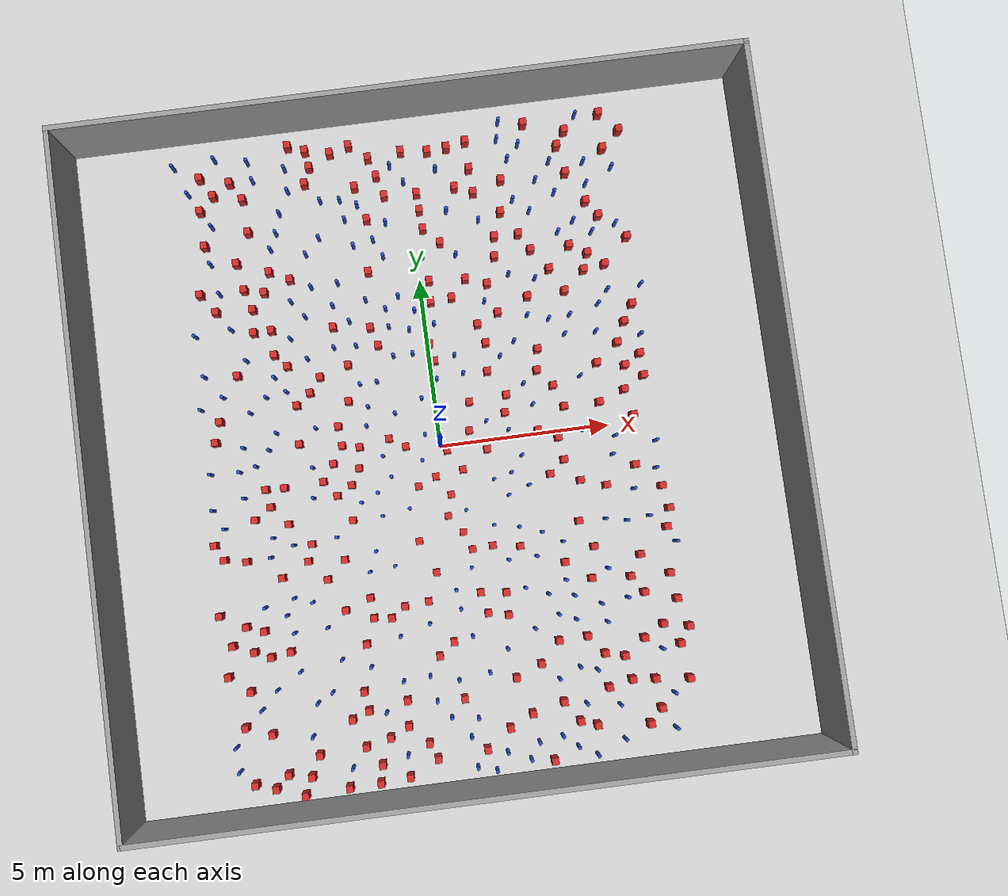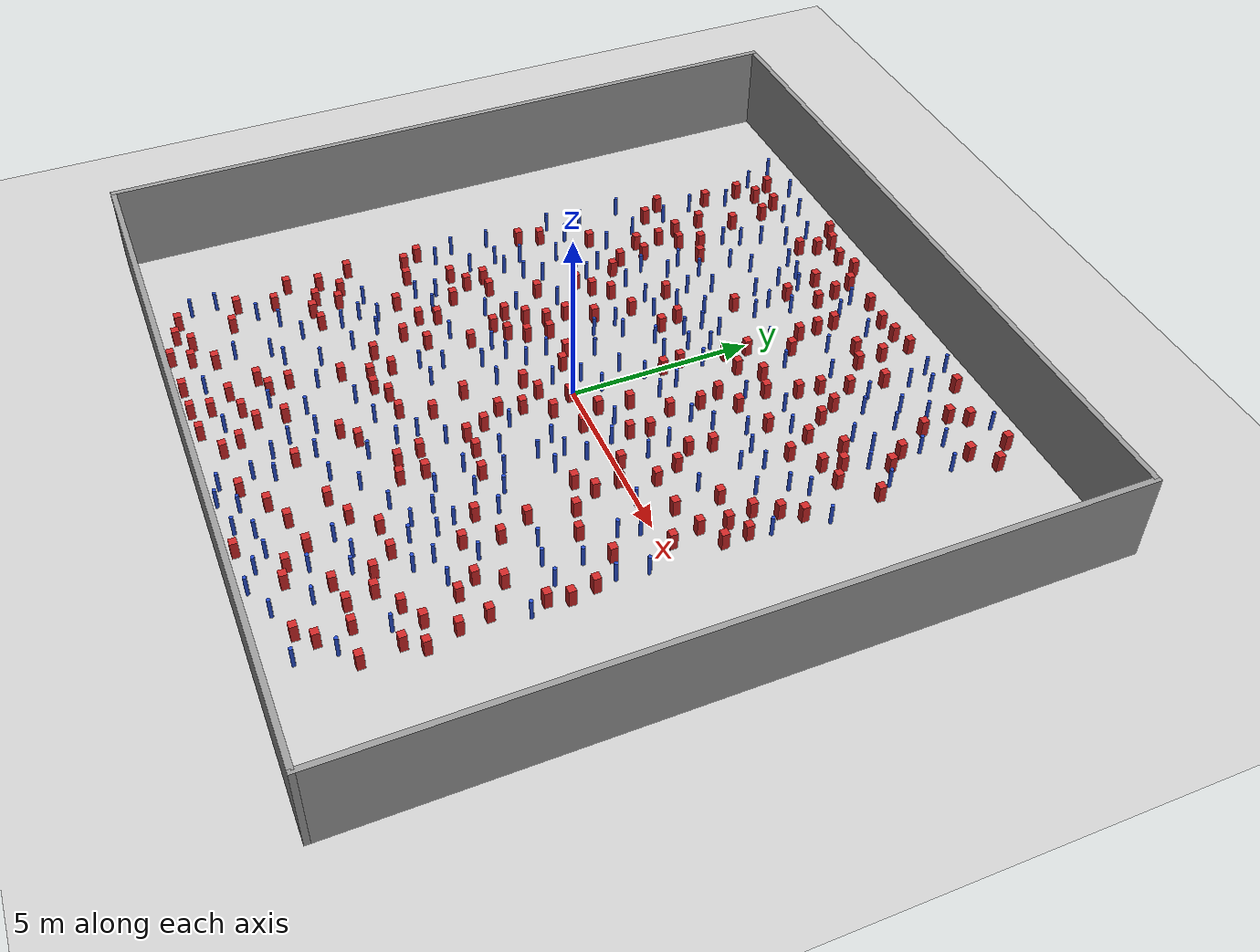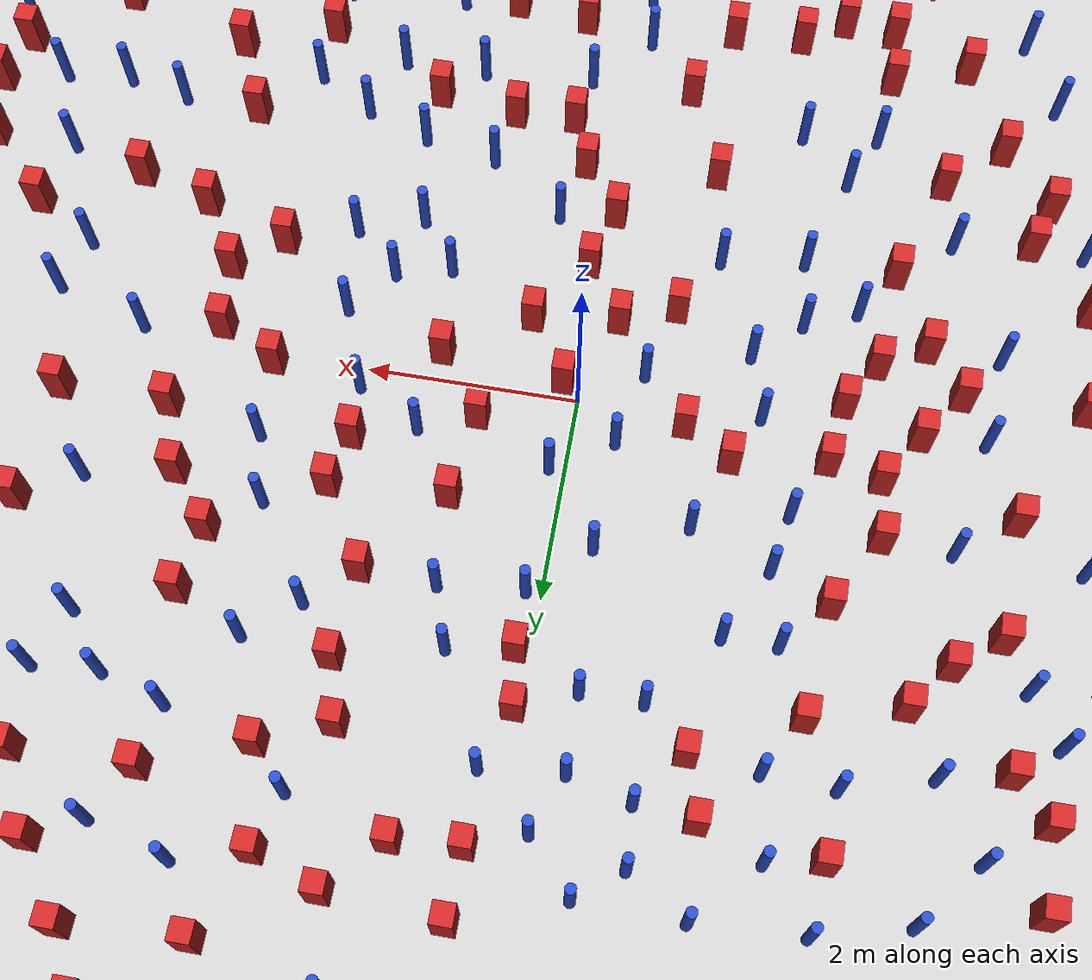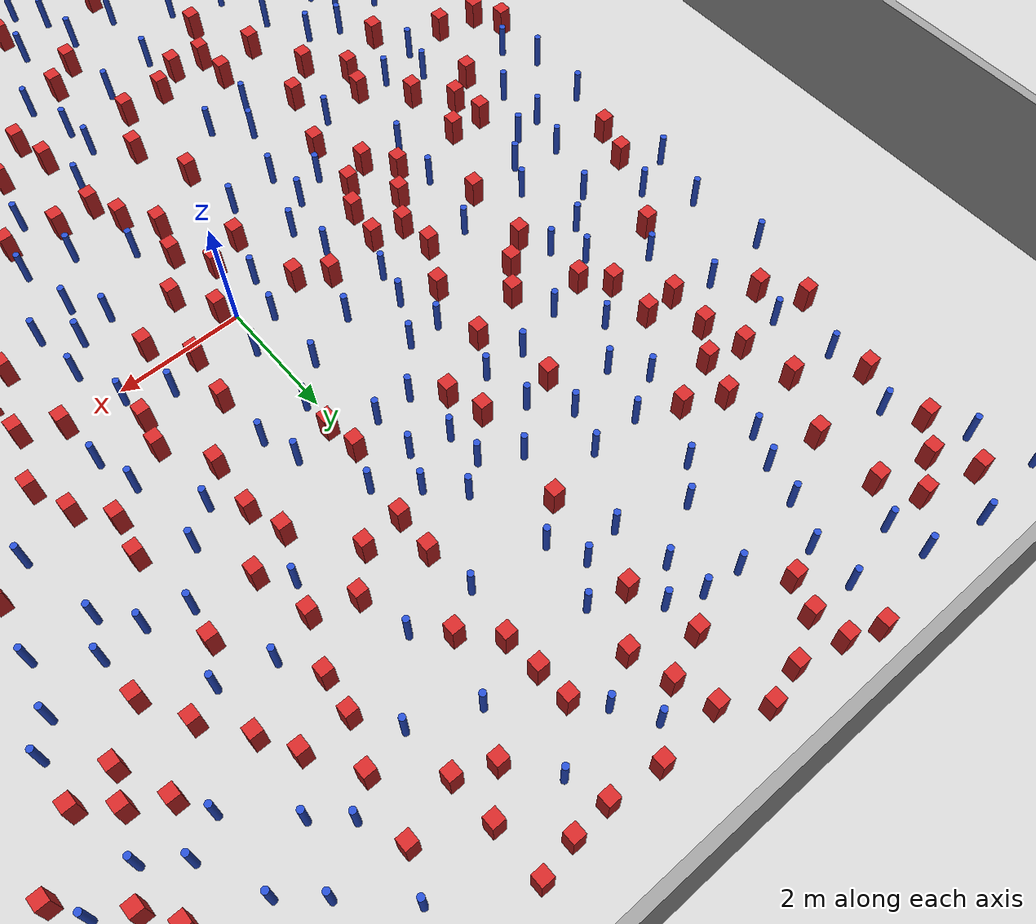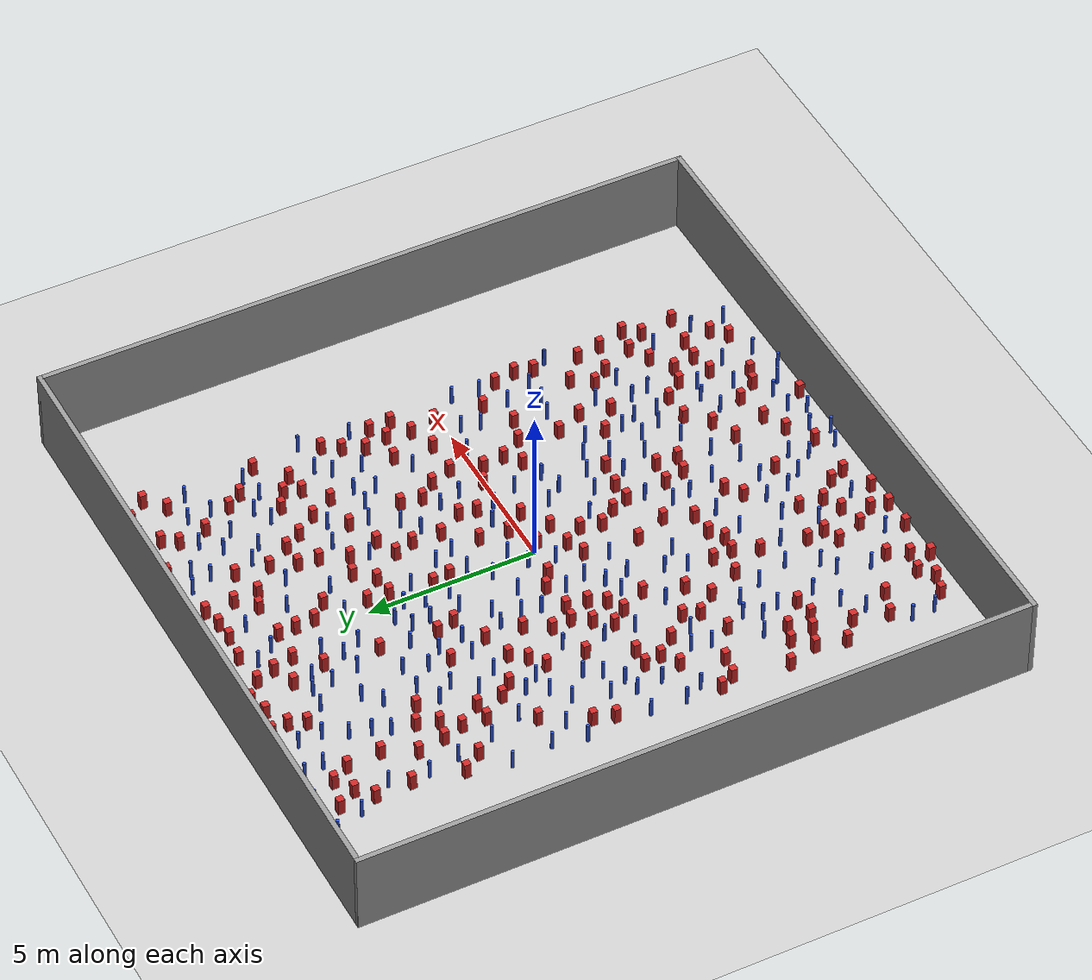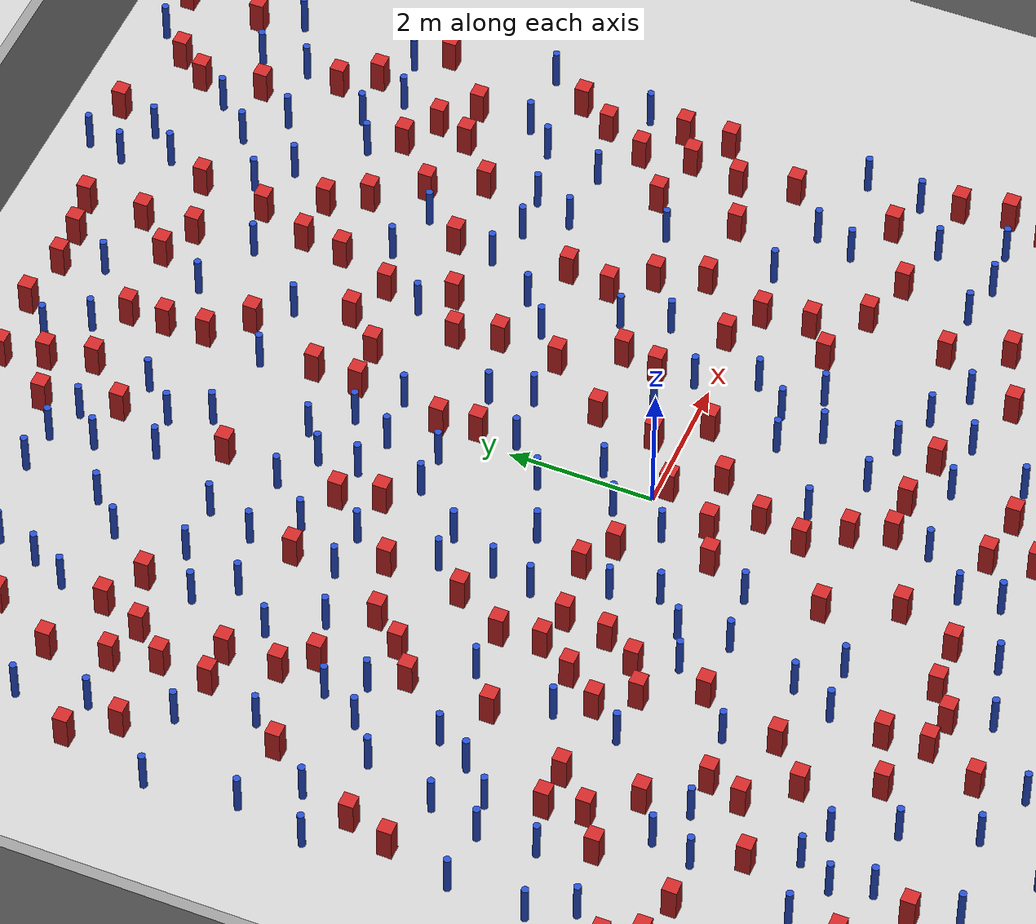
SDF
<sdf version="1.6">
 <world name="default">
  <light name="sun" type="directional">
   <pose>0 0 1000 0 -0 0</pose>
   <diffuse>0.8 0.8 0.8 1</diffuse>
   <specular>0.1 0.1 0.1 1</specular>
   <attenuation>
    <range>1000</range>
    <constant>0.9</constant>
    <linear>0.01</linear>
    <quadratic>0.001</quadratic>
   </attenuation>
   <direction>-0.5 0.5 -1</direction>
  </light>
  <model name="ground_plane">
   <static>1</static>
   <link name="link">
    <collision name="collision">
     <geometry><plane><normal>0 0 1</normal><size>100 100</size></plane></geometry>
     <surface><friction><ode><mu>100</mu><mu2>50</mu2></ode></friction></surface>
    </collision>
    <visual name="visual">
     <cast_shadows>0</cast_shadows>
     <geometry><plane><normal>0 0 1</normal><size>100 100</size></plane></geometry>
     <material>
      <ambient>1.0 1.0 1.0 1.0</ambient>
      <diffuse>0.8 0.8 0.8 1.0</diffuse>
      <specular>0.01 0.01 0.01 1.000000</specular>
     </material>
    </visual>
   </link>
  </model>
  <gravity>0 0 -9.8</gravity>
  <magnetic_field>6e-06 2.3e-05 -4.2e-05</magnetic_field>
  <atmosphere type="adiabatic"/>
  <physics name="default_physics" default="0" type="ode">
   <max_step_size>0.001</max_step_size>
   <real_time_factor>1</real_time_factor>
   <real_time_update_rate>1000</real_time_update_rate>
  </physics>
  <scene><ambient>0.4 0.4 0.4 1</ambient><background>0.7 0.7 0.7 1</background><shadows>1</shadows></scene>
  <spherical_coordinates>
   <surface_model>EARTH_WGS84</surface_model>
   <latitude_deg>0</latitude_deg>
   <longitude_deg>0</longitude_deg>
   <elevation>0</elevation>
   <heading_deg>0</heading_deg>
  </spherical_coordinates>
  <plugin name="gazebo_occupancy_map" filename="libgazebo_2Dmap_plugin.so">
   <map_resolution>0.05</map_resolution>
   <map_topic>generated_map</map_topic>
   <map_height>0.01</map_height>
   <map_size_x>50</map_size_x>
   <map_size_y>50</map_size_y>
  </plugin>
  <model name="NamedLocations">
   <static>true</static>
   <link name="DefaultStart"><pose>8.5 0 0 0 0 3.14</pose></link>
  </model>
  <model name="20x20_walls">
   <pose>0.044518 0.176112 0 0 -0 0</pose>
   <link name="Wall_1">
    <collision name="Wall_1_Collision">
     <geometry><box><size>20 0.15 2.5</size></box></geometry>
     <pose>0 0 1.25 0 -0 0</pose>
    </collision>
    <visual name="Wall_1_Visual">
     <pose>0 0 1.25 0 -0 0</pose>
     <geometry><box><size>20 0.15 2.5</size></box></geometry>
     <material>
      <script><uri>file://media/materials/scripts/gazebo.material</uri><name>Gazebo/Grey</name></script>
      <ambient>0.976471 0.992157 1 1</ambient>
     </material>
     <meta><layer>0</layer></meta>
    </visual>
    <pose>0 9.925 0 0 -0 0</pose>
   </link>
   <link name="Wall_3">
    <collision name="Wall_3_Collision">
     <geometry><box><size>20 0.15 2.5</size></box></geometry>
     <pose>0 0 1.25 0 -0 0</pose>
    </collision>
    <visual name="Wall_3_Visual">
     <pose>0 0 1.25 0 -0 0</pose>
     <geometry><box><size>20 0.15 2.5</size></box></geometry>
     <material>
      <script><uri>file://media/materials/scripts/gazebo.material</uri><name>Gazebo/Grey</name></script>
      <ambient>0.976471 0.992157 1 1</ambient>
     </material>
     <meta><layer>0</layer></meta>
    </visual>
    <pose>9.925 0 0 0 0 -1.5708</pose>
   </link>
   <link name="Wall_4">
    <collision name="Wall_4_Collision">
     <geometry><box><size>20 0.15 2.5</size></box></geometry>
     <pose>0 0 1.25 0 -0 0</pose>
    </collision>
    <visual name="Wall_4_Visual">
     <pose>0 0 1.25 0 -0 0</pose>
     <geometry><box><size>20 0.15 2.5</size></box></geometry>
     <material>
      <script><uri>file://media/materials/scripts/gazebo.material</uri><name>Gazebo/Grey</name></script>
      <ambient>0.976471 0.992157 1 1</ambient>
     </material>
     <meta><layer>0</layer></meta>
    </visual>
    <pose>0 -9.925 0 0 -0 3.14159</pose>
   </link>
   <link name="Wall_5">
    <collision name="Wall_5_Collision">
     <geometry><box><size>20 0.15 2.5</size></box></geometry>
     <pose>0 0 1.25 0 -0 0</pose>
    </collision>
    <visual name="Wall_5_Visual">
     <pose>0 0 1.25 0 -0 0</pose>
     <geometry><box><size>20 0.15 2.5</size></box></geometry>
     <material>
      <script><uri>file://media/materials/scripts/gazebo.material</uri><name>Gazebo/Grey</name></script>
      <ambient>0.976471 0.992157 1 1</ambient>
     </material>
     <meta><layer>0</layer></meta>
    </visual>
    <pose>-9.925 0 0 0 -0 1.5708</pose>
   </link>
   <static>1</static>
  </model>
  <model name="pole_obstacle0">
   <static>true</static>
   <pose>-3.90421917436 -4.82802902542 2.88873142074e-08 -9.90536689859e-09 4.60219948989e-07 -1.20965994961e-07</pose>
   <link name="link">
    <pose>0 0 0.3 0 -0 0</pose>
    <inertial>
     <mass>1</mass>
     <inertia><ixx>0.145833</ixx><ixy>0</ixy><ixz>0</ixz><iyy>0.145833</iyy><iyz>0</iyz><izz>0.125</izz></inertia>
    </inertial>
    <collision name="collision">
     <geometry><cylinder><radius>0.05</radius><length>.6</length></cylinder></geometry>
    </collision>
    <visual name="visual">
     <geometry><cylinder><radius>0.05</radius><length>.6</length></cylinder></geometry>
     <material>
      <script><name>Gazebo/Blue</name><uri>file://media/materials/scripts/gazebo.material</uri></script>
     </material>
    </visual>
   </link>
  </model>
  <model name="pole_obstacle1">
   <static>true</static>
   <pose>-1.12794419745 -1.71041319607 2.88873142074e-08 -9.90536689672e-09 4.60219948993e-07 -1.20965994959e-07</pose>
   <link name="link">
    <pose>0 0 0.3 0 -0 0</pose>
    <inertial>
     <mass>1</mass>
     <inertia><ixx>0.145833</ixx><ixy>0</ixy><ixz>0</ixz><iyy>0.145833</iyy><iyz>0</iyz><izz>0.125</izz></inertia>
    </inertial>
    <collision name="collision">
     <geometry><cylinder><radius>0.05</radius><length>.6</length></cylinder></geometry>
    </collision>
    <visual name="visual">
     <geometry><cylinder><radius>0.05</radius><length>.6</length></cylinder></geometry>
     <material>
      <script><name>Gazebo/Blue</name><uri>file://media/materials/scripts/gazebo.material</uri></script>
     </material>
    </visual>
   </link>
  </model>
  <model name="square_post_obstacle0">
   <static>true</static>
   <pose>-4.23861289255 -2.85928618477 8.22691968438e-08 7.2212513382e-06 -7.54495500217e-07 2.29674213826e-05</pose>
   <link name="link">
    <pose>0 0 0.25 0 -0 0</pose>
    <inertial>
     <mass>100</mass>
     <inertia>
      <ixx>0.166667</ixx>
      <ixy>0</ixy>
      <ixz>0</ixz>
      <iyy>0.166667</iyy>
      <iyz>0</iyz>
      <izz>0.166667</izz>
     </inertia>
    </inertial>
    <collision name="collision"><geometry><box><size>.2 .2 .5</size></box></geometry></collision>
    <visual name="visual">
     <geometry><box><size>.2 .2 .5</size></box></geometry>
     <material>
      <script><name>Gazebo/Red</name><uri>file://media/materials/scripts/gazebo.material</uri></script>
     </material>
    </visual>
   </link>
  </model>
  <model name="square_post_obstacle1">
   <static>true</static>
   <pose>6.15523489396 -6.55460731302 8.22691968438e-08 7.2212513382e-06 -7.54495500217e-07 2.29674213826e-05</pose>
   <link name="link">
    <pose>0 0 0.25 0 -0 0</pose>
    <inertial>
     <mass>100</mass>
     <inertia>
      <ixx>0.166667</ixx>
      <ixy>0</ixy>
      <ixz>0</ixz>
      <iyy>0.166667</iyy>
      <iyz>0</iyz>
      <izz>0.166667</izz>
     </inertia>
    </inertial>
    <collision name="collision"><geometry><box><size>.2 .2 .5</size></box></geometry></collision>
    <visual name="visual">
     <geometry><box><size>.2 .2 .5</size></box></geometry>
     <material>
      <script><name>Gazebo/Red</name><uri>file://media/materials/scripts/gazebo.material</uri></script>
     </material>
    </visual>
   </link>
  </model>
  <model name="pole_obstacle2">
   <static>true</static>
   <pose>-2.06542453884 7.65838804077 2.88873142074e-08 -9.90536689859e-09 4.60219948989e-07 -1.20965994961e-07</pose>
   <link name="link">
    <pose>0 0 0.3 0 -0 0</pose>
    <inertial>
     <mass>1</mass>
     <inertia><ixx>0.145833</ixx><ixy>0</ixy><ixz>0</ixz><iyy>0.145833</iyy><iyz>0</iyz><izz>0.125</izz></inertia>
    </inertial>
    <collision name="collision">
     <geometry><cylinder><radius>0.05</radius><length>.6</length></cylinder></geometry>
    </collision>
    <visual name="visual">
     <geometry><cylinder><radius>0.05</radius><length>.6</length></cylinder></geometry>
     <material>
      <script><name>Gazebo/Blue</name><uri>file://media/materials/scripts/gazebo.material</uri></script>
     </material>
    </visual>
   </link>
  </model>
  <model name="pole_obstacle3">
   <static>true</static>
   <pose>-0.69472149845 4.55980668532 2.88873142074e-08 -9.90536689661e-09 4.60219948993e-07 -1.20965994957e-07</pose>
   <link name="link">
    <pose>0 0 0.3 0 -0 0</pose>
    <inertial>
     <mass>1</mass>
     <inertia><ixx>0.145833</ixx><ixy>0</ixy><ixz>0</ixz><iyy>0.145833</iyy><iyz>0</iyz><izz>0.125</izz></inertia>
    </inertial>
    <collision name="collision">
     <geometry><cylinder><radius>0.05</radius><length>.6</length></cylinder></geometry>
    </collision>
    <visual name="visual">
     <geometry><cylinder><radius>0.05</radius><length>.6</length></cylinder></geometry>
     <material>
      <script><name>Gazebo/Blue</name><uri>file://media/materials/scripts/gazebo.material</uri></script>
     </material>
    </visual>
   </link>
  </model>
  <model name="pole_obstacle4">
   <static>true</static>
   <pose>-4.8280388207 -5.97307406828 2.88873142074e-08 -9.90536690842e-09 4.60219948965e-07 -1.20965994976e-07</pose>
   <link name="link">
    <pose>0 0 0.3 0 -0 0</pose>
    <inertial>
     <mass>1</mass>
     <inertia><ixx>0.145833</ixx><ixy>0</ixy><ixz>0</ixz><iyy>0.145833</iyy><iyz>0</iyz><izz>0.125</izz></inertia>
    </inertial>
    <collision name="collision">
     <geometry><cylinder><radius>0.05</radius><length>.6</length></cylinder></geometry>
    </collision>
    <visual name="visual">
     <geometry><cylinder><radius>0.05</radius><length>.6</length></cylinder></geometry>
     <material>
      <script><name>Gazebo/Blue</name><uri>file://media/materials/scripts/gazebo.material</uri></script>
     </material>
    </visual>
   </link>
  </model>
  <model name="pole_obstacle5">
   <static>true</static>
   <pose>-1.84646677378 -5.33789048613 2.88873142074e-08 -9.90536689852e-09 4.60219948989e-07 -1.2096599496e-07</pose>
   <link name="link">
    <pose>0 0 0.3 0 -0 0</pose>
    <inertial>
     <mass>1</mass>
     <inertia><ixx>0.145833</ixx><ixy>0</ixy><ixz>0</ixz><iyy>0.145833</iyy><iyz>0</iyz><izz>0.125</izz></inertia>
    </inertial>
    <collision name="collision">
     <geometry><cylinder><radius>0.05</radius><length>.6</length></cylinder></geometry>
    </collision>
    <visual name="visual">
     <geometry><cylinder><radius>0.05</radius><length>.6</length></cylinder></geometry>
     <material>
      <script><name>Gazebo/Blue</name><uri>file://media/materials/scripts/gazebo.material</uri></script>
     </material>
    </visual>
   </link>
  </model>
  <model name="pole_obstacle6">
   <static>true</static>
   <pose>6.27253599688 -0.637736351606 2.88873142074e-08 -9.90536689837e-09 4.60219948989e-07 -1.2096599496e-07</pose>
   <link name="link">
    <pose>0 0 0.3 0 -0 0</pose>
    <inertial>
     <mass>1</mass>
     <inertia><ixx>0.145833</ixx><ixy>0</ixy><ixz>0</ixz><iyy>0.145833</iyy><iyz>0</iyz><izz>0.125</izz></inertia>
    </inertial>
    <collision name="collision">
     <geometry><cylinder><radius>0.05</radius><length>.6</length></cylinder></geometry>
    </collision>
    <visual name="visual">
     <geometry><cylinder><radius>0.05</radius><length>.6</length></cylinder></geometry>
     <material>
      <script><name>Gazebo/Blue</name><uri>file://media/materials/scripts/gazebo.material</uri></script>
     </material>
    </visual>
   </link>
  </model>
  <model name="square_post_obstacle2">
   <static>true</static>
   <pose>-0.332540221934 -5.68965694797 8.22691968438e-08 7.2212513382e-06 -7.54495500217e-07 2.29674213826e-05</pose>
   <link name="link">
    <pose>0 0 0.25 0 -0 0</pose>
    <inertial>
     <mass>100</mass>
     <inertia>
      <ixx>0.166667</ixx>
      <ixy>0</ixy>
      <ixz>0</ixz>
      <iyy>0.166667</iyy>
      <iyz>0</iyz>
      <izz>0.166667</izz>
     </inertia>
    </inertial>
    <collision name="collision"><geometry><box><size>.2 .2 .5</size></box></geometry></collision>
    <visual name="visual">
     <geometry><box><size>.2 .2 .5</size></box></geometry>
     <material>
      <script><name>Gazebo/Red</name><uri>file://media/materials/scripts/gazebo.material</uri></script>
     </material>
    </visual>
   </link>
  </model>
  <model name="square_post_obstacle3">
   <static>true</static>
   <pose>-6.22019308932 7.83400990401 8.22691968438e-08 7.22125133819e-06 -7.54495500217e-07 2.29674213826e-05</pose>
   <link name="link">
    <pose>0 0 0.25 0 -0 0</pose>
    <inertial>
     <mass>100</mass>
     <inertia>
      <ixx>0.166667</ixx>
      <ixy>0</ixy>
      <ixz>0</ixz>
      <iyy>0.166667</iyy>
      <iyz>0</iyz>
      <izz>0.166667</izz>
     </inertia>
    </inertial>
    <collision name="collision"><geometry><box><size>.2 .2 .5</size></box></geometry></collision>
    <visual name="visual">
     <geometry><box><size>.2 .2 .5</size></box></geometry>
     <material>
      <script><name>Gazebo/Red</name><uri>file://media/materials/scripts/gazebo.material</uri></script>
     </material>
    </visual>
   </link>
  </model>
  <model name="square_post_obstacle4">
   <static>true</static>
   <pose>1.65579554901 -8.00289531495 8.22691968438e-08 7.22125133819e-06 -7.54495500217e-07 2.29674213826e-05</pose>
   <link name="link">
    <pose>0 0 0.25 0 -0 0</pose>
    <inertial>
     <mass>100</mass>
     <inertia>
      <ixx>0.166667</ixx>
      <ixy>0</ixy>
      <ixz>0</ixz>
      <iyy>0.166667</iyy>
      <iyz>0</iyz>
      <izz>0.166667</izz>
     </inertia>
    </inertial>
    <collision name="collision"><geometry><box><size>.2 .2 .5</size></box></geometry></collision>
    <visual name="visual">
     <geometry><box><size>.2 .2 .5</size></box></geometry>
     <material>
      <script><name>Gazebo/Red</name><uri>file://media/materials/scripts/gazebo.material</uri></script>
     </material>
    </visual>
   </link>
  </model>
  <model name="pole_obstacle7">
   <static>true</static>
   <pose>-3.65876709347 -8.87386158231 2.88873142074e-08 -9.90536692318e-09 4.6021994893e-07 -1.20965994988e-07</pose>
   <link name="link">
    <pose>0 0 0.3 0 -0 0</pose>
    <inertial>
     <mass>1</mass>
     <inertia><ixx>0.145833</ixx><ixy>0</ixy><ixz>0</ixz><iyy>0.145833</iyy><iyz>0</iyz><izz>0.125</izz></inertia>
    </inertial>
    <collision name="collision">
     <geometry><cylinder><radius>0.05</radius><length>.6</length></cylinder></geometry>
    </collision>
    <visual name="visual">
     <geometry><cylinder><radius>0.05</radius><length>.6</length></cylinder></geometry>
     <material>
      <script><name>Gazebo/Blue</name><uri>file://media/materials/scripts/gazebo.material</uri></script>
     </material>
    </visual>
   </link>
  </model>
  <model name="pole_obstacle8">
   <static>true</static>
   <pose>2.83560817841 -9.08859295885 2.88873142074e-08 -9.90536692318e-09 4.6021994893e-07 -1.20965994988e-07</pose>
   <link name="link">
    <pose>0 0 0.3 0 -0 0</pose>
    <inertial>
     <mass>1</mass>
     <inertia><ixx>0.145833</ixx><ixy>0</ixy><ixz>0</ixz><iyy>0.145833</iyy><iyz>0</iyz><izz>0.125</izz></inertia>
    </inertial>
    <collision name="collision">
     <geometry><cylinder><radius>0.05</radius><length>.6</length></cylinder></geometry>
    </collision>
    <visual name="visual">
     <geometry><cylinder><radius>0.05</radius><length>.6</length></cylinder></geometry>
     <material>
      <script><name>Gazebo/Blue</name><uri>file://media/materials/scripts/gazebo.material</uri></script>
     </material>
    </visual>
   </link>
  </model>
  <model name="square_post_obstacle5">
   <static>true</static>
   <pose>-5.83656839227 -7.64539995667 8.22691968438e-08 7.2212513382e-06 -7.54495500217e-07 2.29674213826e-05</pose>
   <link name="link">
    <pose>0 0 0.25 0 -0 0</pose>
    <inertial>
     <mass>100</mass>
     <inertia>
      <ixx>0.166667</ixx>
      <ixy>0</ixy>
      <ixz>0</ixz>
      <iyy>0.166667</iyy>
      <iyz>0</iyz>
      <izz>0.166667</izz>
     </inertia>
    </inertial>
    <collision name="collision"><geometry><box><size>.2 .2 .5</size></box></geometry></collision>
    <visual name="visual">
     <geometry><box><size>.2 .2 .5</size></box></geometry>
     <material>
      <script><name>Gazebo/Red</name><uri>file://media/materials/scripts/gazebo.material</uri></script>
     </material>
    </visual>
   </link>
  </model>
  <model name="square_post_obstacle6">
   <static>true</static>
   <pose>5.55854668269 0.973483236023 8.22691968438e-08 7.2212513382e-06 -7.54495500217e-07 2.29674213826e-05</pose>
   <link name="link">
    <pose>0 0 0.25 0 -0 0</pose>
    <inertial>
     <mass>100</mass>
     <inertia>
      <ixx>0.166667</ixx>
      <ixy>0</ixy>
      <ixz>0</ixz>
      <iyy>0.166667</iyy>
      <iyz>0</iyz>
      <izz>0.166667</izz>
     </inertia>
    </inertial>
    <collision name="collision"><geometry><box><size>.2 .2 .5</size></box></geometry></collision>
    <visual name="visual">
     <geometry><box><size>.2 .2 .5</size></box></geometry>
     <material>
      <script><name>Gazebo/Red</name><uri>file://media/materials/scripts/gazebo.material</uri></script>
     </material>
    </visual>
   </link>
  </model>
  <model name="square_post_obstacle7">
   <static>true</static>
   <pose>-3.04575474347 8.28717111365 8.22691968438e-08 7.2212513382e-06 -7.54495500217e-07 2.29674213826e-05</pose>
   <link name="link">
    <pose>0 0 0.25 0 -0 0</pose>
    <inertial>
     <mass>100</mass>
     <inertia>
      <ixx>0.166667</ixx>
      <ixy>0</ixy>
      <ixz>0</ixz>
      <iyy>0.166667</iyy>
      <iyz>0</iyz>
      <izz>0.166667</izz>
     </inertia>
    </inertial>
    <collision name="collision"><geometry><box><size>.2 .2 .5</size></box></geometry></collision>
    <visual name="visual">
     <geometry><box><size>.2 .2 .5</size></box></geometry>
     <material>
      <script><name>Gazebo/Red</name><uri>file://media/materials/scripts/gazebo.material</uri></script>
     </material>
    </visual>
   </link>
  </model>
  <model name="pole_obstacle9">
   <static>true</static>
   <pose>-0.113606203026 7.9641684089 2.88873142074e-08 -9.9053669038e-09 4.60219948976e-07 -1.20965994968e-07</pose>
   <link name="link">
    <pose>0 0 0.3 0 -0 0</pose>
    <inertial>
     <mass>1</mass>
     <inertia><ixx>0.145833</ixx><ixy>0</ixy><ixz>0</ixz><iyy>0.145833</iyy><iyz>0</iyz><izz>0.125</izz></inertia>
    </inertial>
    <collision name="collision">
     <geometry><cylinder><radius>0.05</radius><length>.6</length></cylinder></geometry>
    </collision>
    <visual name="visual">
     <geometry><cylinder><radius>0.05</radius><length>.6</length></cylinder></geometry>
     <material>
      <script><name>Gazebo/Blue</name><uri>file://media/materials/scripts/gazebo.material</uri></script>
     </material>
    </visual>
   </link>
  </model>
  <model name="pole_obstacle10">
   <static>true</static>
   <pose>-4.67073189763 9.15093612614 2.88873142074e-08 -9.9053668967e-09 4.60219948993e-07 -1.20965994957e-07</pose>
   <link name="link">
    <pose>0 0 0.3 0 -0 0</pose>
    <inertial>
     <mass>1</mass>
     <inertia><ixx>0.145833</ixx><ixy>0</ixy><ixz>0</ixz><iyy>0.145833</iyy><iyz>0</iyz><izz>0.125</izz></inertia>
    </inertial>
    <collision name="collision">
     <geometry><cylinder><radius>0.05</radius><length>.6</length></cylinder></geometry>
    </collision>
    <visual name="visual">
     <geometry><cylinder><radius>0.05</radius><length>.6</length></cylinder></geometry>
     <material>
      <script><name>Gazebo/Blue</name><uri>file://media/materials/scripts/gazebo.material</uri></script>
     </material>
    </visual>
   </link>
  </model>
  <model name="pole_obstacle11">
   <static>true</static>
   <pose>-6.77563240851 4.10837574099 2.88873142074e-08 -9.90536690842e-09 4.60219948965e-07 -1.20965994976e-07</pose>
   <link name="link">
    <pose>0 0 0.3 0 -0 0</pose>
    <inertial>
     <mass>1</mass>
     <inertia><ixx>0.145833</ixx><ixy>0</ixy><ixz>0</ixz><iyy>0.145833</iyy><iyz>0</iyz><izz>0.125</izz></inertia>
    </inertial>
    <collision name="collision">
     <geometry><cylinder><radius>0.05</radius><length>.6</length></cylinder></geometry>
    </collision>
    <visual name="visual">
     <geometry><cylinder><radius>0.05</radius><length>.6</length></cylinder></geometry>
     <material>
      <script><name>Gazebo/Blue</name><uri>file://media/materials/scripts/gazebo.material</uri></script>
     </material>
    </visual>
   </link>
  </model>
  <model name="pole_obstacle12">
   <static>true</static>
   <pose>-0.015884387727 -4.78618979516 2.88873142074e-08 -9.90536689661e-09 4.60219948993e-07 -1.20965994958e-07</pose>
   <link name="link">
    <pose>0 0 0.3 0 -0 0</pose>
    <inertial>
     <mass>1</mass>
     <inertia><ixx>0.145833</ixx><ixy>0</ixy><ixz>0</ixz><iyy>0.145833</iyy><iyz>0</iyz><izz>0.125</izz></inertia>
    </inertial>
    <collision name="collision">
     <geometry><cylinder><radius>0.05</radius><length>.6</length></cylinder></geometry>
    </collision>
    <visual name="visual">
     <geometry><cylinder><radius>0.05</radius><length>.6</length></cylinder></geometry>
     <material>
      <script><name>Gazebo/Blue</name><uri>file://media/materials/scripts/gazebo.material</uri></script>
     </material>
    </visual>
   </link>
  </model>
  <model name="square_post_obstacle8">
   <static>true</static>
   <pose>1.33177363671 -5.12421022262 8.22691968438e-08 7.2212513382e-06 -7.54495500217e-07 2.29674213826e-05</pose>
   <link name="link">
    <pose>0 0 0.25 0 -0 0</pose>
    <inertial>
     <mass>100</mass>
     <inertia>
      <ixx>0.166667</ixx>
      <ixy>0</ixy>
      <ixz>0</ixz>
      <iyy>0.166667</iyy>
      <iyz>0</iyz>
      <izz>0.166667</izz>
     </inertia>
    </inertial>
    <collision name="collision"><geometry><box><size>.2 .2 .5</size></box></geometry></collision>
    <visual name="visual">
     <geometry><box><size>.2 .2 .5</size></box></geometry>
     <material>
      <script><name>Gazebo/Red</name><uri>file://media/materials/scripts/gazebo.material</uri></script>
     </material>
    </visual>
   </link>
  </model>
  <model name="square_post_obstacle9">
   <static>true</static>
   <pose>1.99024103625 0.733178355571 8.22691968438e-08 7.2212513382e-06 -7.54495500217e-07 2.29674213826e-05</pose>
   <link name="link">
    <pose>0 0 0.25 0 -0 0</pose>
    <inertial>
     <mass>100</mass>
     <inertia>
      <ixx>0.166667</ixx>
      <ixy>0</ixy>
      <ixz>0</ixz>
      <iyy>0.166667</iyy>
      <iyz>0</iyz>
      <izz>0.166667</izz>
     </inertia>
    </inertial>
    <collision name="collision"><geometry><box><size>.2 .2 .5</size></box></geometry></collision>
    <visual name="visual">
     <geometry><box><size>.2 .2 .5</size></box></geometry>
     <material>
      <script><name>Gazebo/Red</name><uri>file://media/materials/scripts/gazebo.material</uri></script>
     </material>
    </visual>
   </link>
  </model>
  <model name="pole_obstacle13">
   <static>true</static>
   <pose>-3.25947055534 6.15746719498 2.88873142074e-08 -9.90536689859e-09 4.60219948989e-07 -1.20965994961e-07</pose>
   <link name="link">
    <pose>0 0 0.3 0 -0 0</pose>
    <inertial>
     <mass>1</mass>
     <inertia><ixx>0.145833</ixx><ixy>0</ixy><ixz>0</ixz><iyy>0.145833</iyy><iyz>0</iyz><izz>0.125</izz></inertia>
    </inertial>
    <collision name="collision">
     <geometry><cylinder><radius>0.05</radius><length>.6</length></cylinder></geometry>
    </collision>
    <visual name="visual">
     <geometry><cylinder><radius>0.05</radius><length>.6</length></cylinder></geometry>
     <material>
      <script><name>Gazebo/Blue</name><uri>file://media/materials/scripts/gazebo.material</uri></script>
     </material>
    </visual>
   </link>
  </model>
  <model name="square_post_obstacle10">
   <static>true</static>
   <pose>-6.01871886512 -2.64771498312 8.22691968438e-08 7.2212513382e-06 -7.54495500217e-07 2.29674213826e-05</pose>
   <link name="link">
    <pose>0 0 0.25 0 -0 0</pose>
    <inertial>
     <mass>100</mass>
     <inertia>
      <ixx>0.166667</ixx>
      <ixy>0</ixy>
      <ixz>0</ixz>
      <iyy>0.166667</iyy>
      <iyz>0</iyz>
      <izz>0.166667</izz>
     </inertia>
    </inertial>
    <collision name="collision"><geometry><box><size>.2 .2 .5</size></box></geometry></collision>
    <visual name="visual">
     <geometry><box><size>.2 .2 .5</size></box></geometry>
     <material>
      <script><name>Gazebo/Red</name><uri>file://media/materials/scripts/gazebo.material</uri></script>
     </material>
    </visual>
   </link>
  </model>
  <model name="square_post_obstacle11">
   <static>true</static>
   <pose>3.44342406219 -0.192606901467 8.22691968438e-08 7.2212513382e-06 -7.54495500217e-07 2.29674213826e-05</pose>
   <link name="link">
    <pose>0 0 0.25 0 -0 0</pose>
    <inertial>
     <mass>100</mass>
     <inertia>
      <ixx>0.166667</ixx>
      <ixy>0</ixy>
      <ixz>0</ixz>
      <iyy>0.166667</iyy>
      <iyz>0</iyz>
      <izz>0.166667</izz>
     </inertia>
    </inertial>
    <collision name="collision"><geometry><box><size>.2 .2 .5</size></box></geometry></collision>
    <visual name="visual">
     <geometry><box><size>.2 .2 .5</size></box></geometry>
     <material>
      <script><name>Gazebo/Red</name><uri>file://media/materials/scripts/gazebo.material</uri></script>
     </material>
    </visual>
   </link>
  </model>
  <model name="pole_obstacle14">
   <static>true</static>
   <pose>-2.51315668525 -7.44446797202 2.88873142074e-08 -9.90536689859e-09 4.60219948989e-07 -1.20965994961e-07</pose>
   <link name="link">
    <pose>0 0 0.3 0 -0 0</pose>
    <inertial>
     <mass>1</mass>
     <inertia><ixx>0.145833</ixx><ixy>0</ixy><ixz>0</ixz><iyy>0.145833</iyy><iyz>0</iyz><izz>0.125</izz></inertia>
    </inertial>
    <collision name="collision">
     <geometry><cylinder><radius>0.05</radius><length>.6</length></cylinder></geometry>
    </collision>
    <visual name="visual">
     <geometry><cylinder><radius>0.05</radius><length>.6</length></cylinder></geometry>
     <material>
      <script><name>Gazebo/Blue</name><uri>file://media/materials/scripts/gazebo.material</uri></script>
     </material>
    </visual>
   </link>
  </model>
  <model name="pole_obstacle15">
   <static>true</static>
   <pose>4.20658721971 -0.0656060145119 2.88873142074e-08 -9.90536689153e-09 4.60219949006e-07 -1.20965994951e-07</pose>
   <link name="link">
    <pose>0 0 0.3 0 -0 0</pose>
    <inertial>
     <mass>1</mass>
     <inertia><ixx>0.145833</ixx><ixy>0</ixy><ixz>0</ixz><iyy>0.145833</iyy><iyz>0</iyz><izz>0.125</izz></inertia>
    </inertial>
    <collision name="collision">
     <geometry><cylinder><radius>0.05</radius><length>.6</length></cylinder></geometry>
    </collision>
    <visual name="visual">
     <geometry><cylinder><radius>0.05</radius><length>.6</length></cylinder></geometry>
     <material>
      <script><name>Gazebo/Blue</name><uri>file://media/materials/scripts/gazebo.material</uri></script>
     </material>
    </visual>
   </link>
  </model>
  <model name="square_post_obstacle12">
   <static>true</static>
   <pose>-1.61959890597 -4.50232946245 8.22691968438e-08 7.2212513382e-06 -7.54495500217e-07 2.29674213826e-05</pose>
   <link name="link">
    <pose>0 0 0.25 0 -0 0</pose>
    <inertial>
     <mass>100</mass>
     <inertia>
      <ixx>0.166667</ixx>
      <ixy>0</ixy>
      <ixz>0</ixz>
      <iyy>0.166667</iyy>
      <iyz>0</iyz>
      <izz>0.166667</izz>
     </inertia>
    </inertial>
    <collision name="collision"><geometry><box><size>.2 .2 .5</size></box></geometry></collision>
    <visual name="visual">
     <geometry><box><size>.2 .2 .5</size></box></geometry>
     <material>
      <script><name>Gazebo/Red</name><uri>file://media/materials/scripts/gazebo.material</uri></script>
     </material>
    </visual>
   </link>
  </model>
  <model name="pole_obstacle16">
   <static>true</static>
   <pose>6.44915126913 -3.62196301448 2.88873142074e-08 -9.90536690245e-09 4.6021994898e-07 -1.20965994966e-07</pose>
   <link name="link">
    <pose>0 0 0.3 0 -0 0</pose>
    <inertial>
     <mass>1</mass>
     <inertia><ixx>0.145833</ixx><ixy>0</ixy><ixz>0</ixz><iyy>0.145833</iyy><iyz>0</iyz><izz>0.125</izz></inertia>
    </inertial>
    <collision name="collision">
     <geometry><cylinder><radius>0.05</radius><length>.6</length></cylinder></geometry>
    </collision>
    <visual name="visual">
     <geometry><cylinder><radius>0.05</radius><length>.6</length></cylinder></geometry>
     <material>
      <script><name>Gazebo/Blue</name><uri>file://media/materials/scripts/gazebo.material</uri></script>
     </material>
    </visual>
   </link>
  </model>
  <model name="pole_obstacle17">
   <static>true</static>
   <pose>0.143945520194 0.741125710017 2.88873142074e-08 -9.90536690033e-09 4.60219948985e-07 -1.20965994963e-07</pose>
   <link name="link">
    <pose>0 0 0.3 0 -0 0</pose>
    <inertial>
     <mass>1</mass>
     <inertia><ixx>0.145833</ixx><ixy>0</ixy><ixz>0</ixz><iyy>0.145833</iyy><iyz>0</iyz><izz>0.125</izz></inertia>
    </inertial>
    <collision name="collision">
     <geometry><cylinder><radius>0.05</radius><length>.6</length></cylinder></geometry>
    </collision>
    <visual name="visual">
     <geometry><cylinder><radius>0.05</radius><length>.6</length></cylinder></geometry>
     <material>
      <script><name>Gazebo/Blue</name><uri>file://media/materials/scripts/gazebo.material</uri></script>
     </material>
    </visual>
   </link>
  </model>
  <model name="square_post_obstacle13">
   <static>true</static>
   <pose>-6.90271289844 -2.06878785685 8.22691968438e-08 7.2212513382e-06 -7.54495500217e-07 2.29674213826e-05</pose>
   <link name="link">
    <pose>0 0 0.25 0 -0 0</pose>
    <inertial>
     <mass>100</mass>
     <inertia>
      <ixx>0.166667</ixx>
      <ixy>0</ixy>
      <ixz>0</ixz>
      <iyy>0.166667</iyy>
      <iyz>0</iyz>
      <izz>0.166667</izz>
     </inertia>
    </inertial>
    <collision name="collision"><geometry><box><size>.2 .2 .5</size></box></geometry></collision>
    <visual name="visual">
     <geometry><box><size>.2 .2 .5</size></box></geometry>
     <material>
      <script><name>Gazebo/Red</name><uri>file://media/materials/scripts/gazebo.material</uri></script>
     </material>
    </visual>
   </link>
  </model>
  <model name="pole_obstacle18">
   <static>true</static>
   <pose>-1.91676649097 -6.62138611373 2.88873142074e-08 -9.90536689852e-09 4.60219948989e-07 -1.2096599496e-07</pose>
   <link name="link">
    <pose>0 0 0.3 0 -0 0</pose>
    <inertial>
     <mass>1</mass>
     <inertia><ixx>0.145833</ixx><ixy>0</ixy><ixz>0</ixz><iyy>0.145833</iyy><iyz>0</iyz><izz>0.125</izz></inertia>
    </inertial>
    <collision name="collision">
     <geometry><cylinder><radius>0.05</radius><length>.6</length></cylinder></geometry>
    </collision>
    <visual name="visual">
     <geometry><cylinder><radius>0.05</radius><length>.6</length></cylinder></geometry>
     <material>
      <script><name>Gazebo/Blue</name><uri>file://media/materials/scripts/gazebo.material</uri></script>
     </material>
    </visual>
   </link>
  </model>
  <model name="square_post_obstacle14">
   <static>true</static>
   <pose>-1.48114246793 5.40035358558 8.22691968438e-08 7.2212513382e-06 -7.54495500217e-07 2.29674213826e-05</pose>
   <link name="link">
    <pose>0 0 0.25 0 -0 0</pose>
    <inertial>
     <mass>100</mass>
     <inertia>
      <ixx>0.166667</ixx>
      <ixy>0</ixy>
      <ixz>0</ixz>
      <iyy>0.166667</iyy>
      <iyz>0</iyz>
      <izz>0.166667</izz>
     </inertia>
    </inertial>
    <collision name="collision"><geometry><box><size>.2 .2 .5</size></box></geometry></collision>
    <visual name="visual">
     <geometry><box><size>.2 .2 .5</size></box></geometry>
     <material>
      <script><name>Gazebo/Red</name><uri>file://media/materials/scripts/gazebo.material</uri></script>
     </material>
    </visual>
   </link>
  </model>
  <model name="pole_obstacle19">
   <static>true</static>
   <pose>3.04665153583 8.27095719519 2.88873142074e-08 -9.90536692318e-09 4.6021994893e-07 -1.20965994988e-07</pose>
   <link name="link">
    <pose>0 0 0.3 0 -0 0</pose>
    <inertial>
     <mass>1</mass>
     <inertia><ixx>0.145833</ixx><ixy>0</ixy><ixz>0</ixz><iyy>0.145833</iyy><iyz>0</iyz><izz>0.125</izz></inertia>
    </inertial>
    <collision name="collision">
     <geometry><cylinder><radius>0.05</radius><length>.6</length></cylinder></geometry>
    </collision>
    <visual name="visual">
     <geometry><cylinder><radius>0.05</radius><length>.6</length></cylinder></geometry>
     <material>
      <script><name>Gazebo/Blue</name><uri>file://media/materials/scripts/gazebo.material</uri></script>
     </material>
    </visual>
   </link>
  </model>
  <model name="square_post_obstacle15">
   <static>true</static>
   <pose>5.49864312743 4.75280284831 8.22691968438e-08 7.2212513382e-06 -7.54495500217e-07 2.29674213826e-05</pose>
   <link name="link">
    <pose>0 0 0.25 0 -0 0</pose>
    <inertial>
     <mass>100</mass>
     <inertia>
      <ixx>0.166667</ixx>
      <ixy>0</ixy>
      <ixz>0</ixz>
      <iyy>0.166667</iyy>
      <iyz>0</iyz>
      <izz>0.166667</izz>
     </inertia>
    </inertial>
    <collision name="collision"><geometry><box><size>.2 .2 .5</size></box></geometry></collision>
    <visual name="visual">
     <geometry><box><size>.2 .2 .5</size></box></geometry>
     <material>
      <script><name>Gazebo/Red</name><uri>file://media/materials/scripts/gazebo.material</uri></script>
     </material>
    </visual>
   </link>
  </model>
  <model name="square_post_obstacle16">
   <static>true</static>
   <pose>-5.26272390022 8.59142701754 8.22691968438e-08 7.22125133819e-06 -7.54495500217e-07 2.29674213826e-05</pose>
   <link name="link">
    <pose>0 0 0.25 0 -0 0</pose>
    <inertial>
     <mass>100</mass>
     <inertia>
      <ixx>0.166667</ixx>
      <ixy>0</ixy>
      <ixz>0</ixz>
      <iyy>0.166667</iyy>
      <iyz>0</iyz>
      <izz>0.166667</izz>
     </inertia>
    </inertial>
    <collision name="collision"><geometry><box><size>.2 .2 .5</size></box></geometry></collision>
    <visual name="visual">
     <geometry><box><size>.2 .2 .5</size></box></geometry>
     <material>
      <script><name>Gazebo/Red</name><uri>file://media/materials/scripts/gazebo.material</uri></script>
     </material>
    </visual>
   </link>
  </model>
  <model name="square_post_obstacle17">
   <static>true</static>
   <pose>-3.20637738972 -8.33634282894 8.22691968438e-08 7.22125133819e-06 -7.54495500217e-07 2.29674213826e-05</pose>
   <link name="link">
    <pose>0 0 0.25 0 -0 0</pose>
    <inertial>
     <mass>100</mass>
     <inertia>
      <ixx>0.166667</ixx>
      <ixy>0</ixy>
      <ixz>0</ixz>
      <iyy>0.166667</iyy>
      <iyz>0</iyz>
      <izz>0.166667</izz>
     </inertia>
    </inertial>
    <collision name="collision"><geometry><box><size>.2 .2 .5</size></box></geometry></collision>
    <visual name="visual">
     <geometry><box><size>.2 .2 .5</size></box></geometry>
     <material>
      <script><name>Gazebo/Red</name><uri>file://media/materials/scripts/gazebo.material</uri></script>
     </material>
    </visual>
   </link>
  </model>
  <model name="pole_obstacle20">
   <static>true</static>
   <pose>0.139688920828 1.96752364969 2.88873142074e-08 -9.90536689557e-09 4.60219948996e-07 -1.20965994956e-07</pose>
   <link name="link">
    <pose>0 0 0.3 0 -0 0</pose>
    <inertial>
     <mass>1</mass>
     <inertia><ixx>0.145833</ixx><ixy>0</ixy><ixz>0</ixz><iyy>0.145833</iyy><iyz>0</iyz><izz>0.125</izz></inertia>
    </inertial>
    <collision name="collision">
     <geometry><cylinder><radius>0.05</radius><length>.6</length></cylinder></geometry>
    </collision>
    <visual name="visual">
     <geometry><cylinder><radius>0.05</radius><length>.6</length></cylinder></geometry>
     <material>
      <script><name>Gazebo/Blue</name><uri>file://media/materials/scripts/gazebo.material</uri></script>
     </material>
    </visual>
   </link>
  </model>
  <model name="pole_obstacle21">
   <static>true</static>
   <pose>3.18689587622 -6.85795421566 2.88873142074e-08 -9.90536689859e-09 4.60219948989e-07 -1.20965994961e-07</pose>
   <link name="link">
    <pose>0 0 0.3 0 -0 0</pose>
    <inertial>
     <mass>1</mass>
     <inertia><ixx>0.145833</ixx><ixy>0</ixy><ixz>0</ixz><iyy>0.145833</iyy><iyz>0</iyz><izz>0.125</izz></inertia>
    </inertial>
    <collision name="collision">
     <geometry><cylinder><radius>0.05</radius><length>.6</length></cylinder></geometry>
    </collision>
    <visual name="visual">
     <geometry><cylinder><radius>0.05</radius><length>.6</length></cylinder></geometry>
     <material>
      <script><name>Gazebo/Blue</name><uri>file://media/materials/scripts/gazebo.material</uri></script>
     </material>
    </visual>
   </link>
  </model>
  <model name="pole_obstacle22">
   <static>true</static>
   <pose>2.06500898014 2.41130440198 2.88873142074e-08 -9.90536690232e-09 4.6021994898e-07 -1.20965994968e-07</pose>
   <link name="link">
    <pose>0 0 0.3 0 -0 0</pose>
    <inertial>
     <mass>1</mass>
     <inertia><ixx>0.145833</ixx><ixy>0</ixy><ixz>0</ixz><iyy>0.145833</iyy><iyz>0</iyz><izz>0.125</izz></inertia>
    </inertial>
    <collision name="collision">
     <geometry><cylinder><radius>0.05</radius><length>.6</length></cylinder></geometry>
    </collision>
    <visual name="visual">
     <geometry><cylinder><radius>0.05</radius><length>.6</length></cylinder></geometry>
     <material>
      <script><name>Gazebo/Blue</name><uri>file://media/materials/scripts/gazebo.material</uri></script>
     </material>
    </visual>
   </link>
  </model>
  <model name="pole_obstacle23">
   <static>true</static>
   <pose>-5.70288652627 4.17874647458 2.88873142074e-08 -9.90536690842e-09 4.60219948965e-07 -1.20965994976e-07</pose>
   <link name="link">
    <pose>0 0 0.3 0 -0 0</pose>
    <inertial>
     <mass>1</mass>
     <inertia><ixx>0.145833</ixx><ixy>0</ixy><ixz>0</ixz><iyy>0.145833</iyy><iyz>0</iyz><izz>0.125</izz></inertia>
    </inertial>
    <collision name="collision">
     <geometry><cylinder><radius>0.05</radius><length>.6</length></cylinder></geometry>
    </collision>
    <visual name="visual">
     <geometry><cylinder><radius>0.05</radius><length>.6</length></cylinder></geometry>
     <material>
      <script><name>Gazebo/Blue</name><uri>file://media/materials/scripts/gazebo.material</uri></script>
     </material>
    </visual>
   </link>
  </model>
  <model name="square_post_obstacle18">
   <static>true</static>
   <pose>0.53533978241 -3.11377711182 8.22691968438e-08 7.2212513382e-06 -7.54495500217e-07 2.29674213826e-05</pose>
   <link name="link">
    <pose>0 0 0.25 0 -0 0</pose>
    <inertial>
     <mass>100</mass>
     <inertia>
      <ixx>0.166667</ixx>
      <ixy>0</ixy>
      <ixz>0</ixz>
      <iyy>0.166667</iyy>
      <iyz>0</iyz>
      <izz>0.166667</izz>
     </inertia>
    </inertial>
    <collision name="collision"><geometry><box><size>.2 .2 .5</size></box></geometry></collision>
    <visual name="visual">
     <geometry><box><size>.2 .2 .5</size></box></geometry>
     <material>
      <script><name>Gazebo/Red</name><uri>file://media/materials/scripts/gazebo.material</uri></script>
     </material>
    </visual>
   </link>
  </model>
  <model name="pole_obstacle24">
   <static>true</static>
   <pose>1.82298354878 4.08808406498 2.88873142074e-08 -9.90536689852e-09 4.60219948989e-07 -1.2096599496e-07</pose>
   <link name="link">
    <pose>0 0 0.3 0 -0 0</pose>
    <inertial>
     <mass>1</mass>
     <inertia><ixx>0.145833</ixx><ixy>0</ixy><ixz>0</ixz><iyy>0.145833</iyy><iyz>0</iyz><izz>0.125</izz></inertia>
    </inertial>
    <collision name="collision">
     <geometry><cylinder><radius>0.05</radius><length>.6</length></cylinder></geometry>
    </collision>
    <visual name="visual">
     <geometry><cylinder><radius>0.05</radius><length>.6</length></cylinder></geometry>
     <material>
      <script><name>Gazebo/Blue</name><uri>file://media/materials/scripts/gazebo.material</uri></script>
     </material>
    </visual>
   </link>
  </model>
  <model name="pole_obstacle25">
   <static>true</static>
   <pose>5.22740422593 9.34821643953 2.88873142074e-08 -9.9053668967e-09 4.60219948993e-07 -1.20965994957e-07</pose>
   <link name="link">
    <pose>0 0 0.3 0 -0 0</pose>
    <inertial>
     <mass>1</mass>
     <inertia><ixx>0.145833</ixx><ixy>0</ixy><ixz>0</ixz><iyy>0.145833</iyy><iyz>0</iyz><izz>0.125</izz></inertia>
    </inertial>
    <collision name="collision">
     <geometry><cylinder><radius>0.05</radius><length>.6</length></cylinder></geometry>
    </collision>
    <visual name="visual">
     <geometry><cylinder><radius>0.05</radius><length>.6</length></cylinder></geometry>
     <material>
      <script><name>Gazebo/Blue</name><uri>file://media/materials/scripts/gazebo.material</uri></script>
     </material>
    </visual>
   </link>
  </model>
  <model name="pole_obstacle26">
   <static>true</static>
   <pose>0.443160769518 -3.63857379925 2.88873142074e-08 -9.90536689663e-09 4.60219948993e-07 -1.20965994959e-07</pose>
   <link name="link">
    <pose>0 0 0.3 0 -0 0</pose>
    <inertial>
     <mass>1</mass>
     <inertia><ixx>0.145833</ixx><ixy>0</ixy><ixz>0</ixz><iyy>0.145833</iyy><iyz>0</iyz><izz>0.125</izz></inertia>
    </inertial>
    <collision name="collision">
     <geometry><cylinder><radius>0.05</radius><length>.6</length></cylinder></geometry>
    </collision>
    <visual name="visual">
     <geometry><cylinder><radius>0.05</radius><length>.6</length></cylinder></geometry>
     <material>
      <script><name>Gazebo/Blue</name><uri>file://media/materials/scripts/gazebo.material</uri></script>
     </material>
    </visual>
   </link>
  </model>
  <model name="pole_obstacle27">
   <static>true</static>
   <pose>1.25044944178 -2.49611178456 2.88873142074e-08 -9.90536689791e-09 4.6021994899e-07 -1.20965994959e-07</pose>
   <link name="link">
    <pose>0 0 0.3 0 -0 0</pose>
    <inertial>
     <mass>1</mass>
     <inertia><ixx>0.145833</ixx><ixy>0</ixy><ixz>0</ixz><iyy>0.145833</iyy><iyz>0</iyz><izz>0.125</izz></inertia>
    </inertial>
    <collision name="collision">
     <geometry><cylinder><radius>0.05</radius><length>.6</length></cylinder></geometry>
    </collision>
    <visual name="visual">
     <geometry><cylinder><radius>0.05</radius><length>.6</length></cylinder></geometry>
     <material>
      <script><name>Gazebo/Blue</name><uri>file://media/materials/scripts/gazebo.material</uri></script>
     </material>
    </visual>
   </link>
  </model>
  <model name="pole_obstacle28">
   <static>true</static>
   <pose>1.97701452245 -2.63980536934 2.88873142074e-08 -9.90536689941e-09 4.60219948987e-07 -1.20965994961e-07</pose>
   <link name="link">
    <pose>0 0 0.3 0 -0 0</pose>
    <inertial>
     <mass>1</mass>
     <inertia><ixx>0.145833</ixx><ixy>0</ixy><ixz>0</ixz><iyy>0.145833</iyy><iyz>0</iyz><izz>0.125</izz></inertia>
    </inertial>
    <collision name="collision">
     <geometry><cylinder><radius>0.05</radius><length>.6</length></cylinder></geometry>
    </collision>
    <visual name="visual">
     <geometry><cylinder><radius>0.05</radius><length>.6</length></cylinder></geometry>
     <material>
      <script><name>Gazebo/Blue</name><uri>file://media/materials/scripts/gazebo.material</uri></script>
     </material>
    </visual>
   </link>
  </model>
  <model name="square_post_obstacle19">
   <static>true</static>
   <pose>-2.7245175112 -0.820515916125 8.22691968438e-08 7.2212513382e-06 -7.54495500217e-07 2.29674213826e-05</pose>
   <link name="link">
    <pose>0 0 0.25 0 -0 0</pose>
    <inertial>
     <mass>100</mass>
     <inertia>
      <ixx>0.166667</ixx>
      <ixy>0</ixy>
      <ixz>0</ixz>
      <iyy>0.166667</iyy>
      <iyz>0</iyz>
      <izz>0.166667</izz>
     </inertia>
    </inertial>
    <collision name="collision"><geometry><box><size>.2 .2 .5</size></box></geometry></collision>
    <visual name="visual">
     <geometry><box><size>.2 .2 .5</size></box></geometry>
     <material>
      <script><name>Gazebo/Red</name><uri>file://media/materials/scripts/gazebo.material</uri></script>
     </material>
    </visual>
   </link>
  </model>
  <model name="square_post_obstacle20">
   <static>true</static>
   <pose>-1.01994554242 0.104363808759 8.22691968438e-08 7.2212513382e-06 -7.54495500217e-07 2.29674213826e-05</pose>
   <link name="link">
    <pose>0 0 0.25 0 -0 0</pose>
    <inertial>
     <mass>100</mass>
     <inertia>
      <ixx>0.166667</ixx>
      <ixy>0</ixy>
      <ixz>0</ixz>
      <iyy>0.166667</iyy>
      <iyz>0</iyz>
      <izz>0.166667</izz>
     </inertia>
    </inertial>
    <collision name="collision"><geometry><box><size>.2 .2 .5</size></box></geometry></collision>
    <visual name="visual">
     <geometry><box><size>.2 .2 .5</size></box></geometry>
     <material>
      <script><name>Gazebo/Red</name><uri>file://media/materials/scripts/gazebo.material</uri></script>
     </material>
    </visual>
   </link>
  </model>
  <model name="pole_obstacle29">
   <static>true</static>
   <pose>3.04993943318 7.02499457316 2.88873142074e-08 -9.90536689859e-09 4.60219948989e-07 -1.20965994961e-07</pose>
   <link name="link">
    <pose>0 0 0.3 0 -0 0</pose>
    <inertial>
     <mass>1</mass>
     <inertia><ixx>0.145833</ixx><ixy>0</ixy><ixz>0</ixz><iyy>0.145833</iyy><iyz>0</iyz><izz>0.125</izz></inertia>
    </inertial>
    <collision name="collision">
     <geometry><cylinder><radius>0.05</radius><length>.6</length></cylinder></geometry>
    </collision>
    <visual name="visual">
     <geometry><cylinder><radius>0.05</radius><length>.6</length></cylinder></geometry>
     <material>
      <script><name>Gazebo/Blue</name><uri>file://media/materials/scripts/gazebo.material</uri></script>
     </material>
    </visual>
   </link>
  </model>
  <model name="square_post_obstacle21">
   <static>true</static>
   <pose>4.86648142705 1.85375109788 8.22691968438e-08 7.2212513382e-06 -7.54495500217e-07 2.29674213826e-05</pose>
   <link name="link">
    <pose>0 0 0.25 0 -0 0</pose>
    <inertial>
     <mass>100</mass>
     <inertia>
      <ixx>0.166667</ixx>
      <ixy>0</ixy>
      <ixz>0</ixz>
      <iyy>0.166667</iyy>
      <iyz>0</iyz>
      <izz>0.166667</izz>
     </inertia>
    </inertial>
    <collision name="collision"><geometry><box><size>.2 .2 .5</size></box></geometry></collision>
    <visual name="visual">
     <geometry><box><size>.2 .2 .5</size></box></geometry>
     <material>
      <script><name>Gazebo/Red</name><uri>file://media/materials/scripts/gazebo.material</uri></script>
     </material>
    </visual>
   </link>
  </model>
  <model name="pole_obstacle30">
   <static>true</static>
   <pose>-2.7883637554 -6.09784104883 2.88873142074e-08 -9.90536689859e-09 4.60219948989e-07 -1.20965994961e-07</pose>
   <link name="link">
    <pose>0 0 0.3 0 -0 0</pose>
    <inertial>
     <mass>1</mass>
     <inertia><ixx>0.145833</ixx><ixy>0</ixy><ixz>0</ixz><iyy>0.145833</iyy><iyz>0</iyz><izz>0.125</izz></inertia>
    </inertial>
    <collision name="collision">
     <geometry><cylinder><radius>0.05</radius><length>.6</length></cylinder></geometry>
    </collision>
    <visual name="visual">
     <geometry><cylinder><radius>0.05</radius><length>.6</length></cylinder></geometry>
     <material>
      <script><name>Gazebo/Blue</name><uri>file://media/materials/scripts/gazebo.material</uri></script>
     </material>
    </visual>
   </link>
  </model>
  <model name="square_post_obstacle22">
   <static>true</static>
   <pose>-4.55727015643 -8.39629120217 8.22691968438e-08 7.22125133819e-06 -7.54495500217e-07 2.29674213826e-05</pose>
   <link name="link">
    <pose>0 0 0.25 0 -0 0</pose>
    <inertial>
     <mass>100</mass>
     <inertia>
      <ixx>0.166667</ixx>
      <ixy>0</ixy>
      <ixz>0</ixz>
      <iyy>0.166667</iyy>
      <iyz>0</iyz>
      <izz>0.166667</izz>
     </inertia>
    </inertial>
    <collision name="collision"><geometry><box><size>.2 .2 .5</size></box></geometry></collision>
    <visual name="visual">
     <geometry><box><size>.2 .2 .5</size></box></geometry>
     <material>
      <script><name>Gazebo/Red</name><uri>file://media/materials/scripts/gazebo.material</uri></script>
     </material>
    </visual>
   </link>
  </model>
  <model name="square_post_obstacle23">
   <static>true</static>
   <pose>-3.4143512666 9.47555512349 8.22691968438e-08 7.2212513382e-06 -7.54495500217e-07 2.29674213826e-05</pose>
   <link name="link">
    <pose>0 0 0.25 0 -0 0</pose>
    <inertial>
     <mass>100</mass>
     <inertia>
      <ixx>0.166667</ixx>
      <ixy>0</ixy>
      <ixz>0</ixz>
      <iyy>0.166667</iyy>
      <iyz>0</iyz>
      <izz>0.166667</izz>
     </inertia>
    </inertial>
    <collision name="collision"><geometry><box><size>.2 .2 .5</size></box></geometry></collision>
    <visual name="visual">
     <geometry><box><size>.2 .2 .5</size></box></geometry>
     <material>
      <script><name>Gazebo/Red</name><uri>file://media/materials/scripts/gazebo.material</uri></script>
     </material>
    </visual>
   </link>
  </model>
  <model name="pole_obstacle31">
   <static>true</static>
   <pose>-0.585322574851 -0.355439640165 2.88873142074e-08 -9.90536689558e-09 4.60219948996e-07 -1.20965994957e-07</pose>
   <link name="link">
    <pose>0 0 0.3 0 -0 0</pose>
    <inertial>
     <mass>1</mass>
     <inertia><ixx>0.145833</ixx><ixy>0</ixy><ixz>0</ixz><iyy>0.145833</iyy><iyz>0</iyz><izz>0.125</izz></inertia>
    </inertial>
    <collision name="collision">
     <geometry><cylinder><radius>0.05</radius><length>.6</length></cylinder></geometry>
    </collision>
    <visual name="visual">
     <geometry><cylinder><radius>0.05</radius><length>.6</length></cylinder></geometry>
     <material>
      <script><name>Gazebo/Blue</name><uri>file://media/materials/scripts/gazebo.material</uri></script>
     </material>
    </visual>
   </link>
  </model>
  <model name="square_post_obstacle24">
   <static>true</static>
   <pose>6.23399795048 -5.26352225772 8.22691968438e-08 7.2212513382e-06 -7.54495500217e-07 2.29674213826e-05</pose>
   <link name="link">
    <pose>0 0 0.25 0 -0 0</pose>
    <inertial>
     <mass>100</mass>
     <inertia>
      <ixx>0.166667</ixx>
      <ixy>0</ixy>
      <ixz>0</ixz>
      <iyy>0.166667</iyy>
      <iyz>0</iyz>
      <izz>0.166667</izz>
     </inertia>
    </inertial>
    <collision name="collision"><geometry><box><size>.2 .2 .5</size></box></geometry></collision>
    <visual name="visual">
     <geometry><box><size>.2 .2 .5</size></box></geometry>
     <material>
      <script><name>Gazebo/Red</name><uri>file://media/materials/scripts/gazebo.material</uri></script>
     </material>
    </visual>
   </link>
  </model>
  <model name="square_post_obstacle25">
   <static>true</static>
   <pose>-3.74527833007 -3.45318272488 8.22691968438e-08 7.2212513382e-06 -7.54495500217e-07 2.29674213826e-05</pose>
   <link name="link">
    <pose>0 0 0.25 0 -0 0</pose>
    <inertial>
     <mass>100</mass>
     <inertia>
      <ixx>0.166667</ixx>
      <ixy>0</ixy>
      <ixz>0</ixz>
      <iyy>0.166667</iyy>
      <iyz>0</iyz>
      <izz>0.166667</izz>
     </inertia>
    </inertial>
    <collision name="collision"><geometry><box><size>.2 .2 .5</size></box></geometry></collision>
    <visual name="visual">
     <geometry><box><size>.2 .2 .5</size></box></geometry>
     <material>
      <script><name>Gazebo/Red</name><uri>file://media/materials/scripts/gazebo.material</uri></script>
     </material>
    </visual>
   </link>
  </model>
  <model name="square_post_obstacle26">
   <static>true</static>
   <pose>-0.789775895719 -1.10357461723 8.22691968438e-08 7.2212513382e-06 -7.54495500217e-07 2.29674213826e-05</pose>
   <link name="link">
    <pose>0 0 0.25 0 -0 0</pose>
    <inertial>
     <mass>100</mass>
     <inertia>
      <ixx>0.166667</ixx>
      <ixy>0</ixy>
      <ixz>0</ixz>
      <iyy>0.166667</iyy>
      <iyz>0</iyz>
      <izz>0.166667</izz>
     </inertia>
    </inertial>
    <collision name="collision"><geometry><box><size>.2 .2 .5</size></box></geometry></collision>
    <visual name="visual">
     <geometry><box><size>.2 .2 .5</size></box></geometry>
     <material>
      <script><name>Gazebo/Red</name><uri>file://media/materials/scripts/gazebo.material</uri></script>
     </material>
    </visual>
   </link>
  </model>
  <model name="pole_obstacle32">
   <static>true</static>
   <pose>4.7484195293 6.16862415002 2.88873142074e-08 -9.90536690842e-09 4.60219948965e-07 -1.20965994976e-07</pose>
   <link name="link">
    <pose>0 0 0.3 0 -0 0</pose>
    <inertial>
     <mass>1</mass>
     <inertia><ixx>0.145833</ixx><ixy>0</ixy><ixz>0</ixz><iyy>0.145833</iyy><iyz>0</iyz><izz>0.125</izz></inertia>
    </inertial>
    <collision name="collision">
     <geometry><cylinder><radius>0.05</radius><length>.6</length></cylinder></geometry>
    </collision>
    <visual name="visual">
     <geometry><cylinder><radius>0.05</radius><length>.6</length></cylinder></geometry>
     <material>
      <script><name>Gazebo/Blue</name><uri>file://media/materials/scripts/gazebo.material</uri></script>
     </material>
    </visual>
   </link>
  </model>
  <model name="square_post_obstacle27">
   <static>true</static>
   <pose>1.34927041516 -4.47156705304 8.22691968438e-08 7.2212513382e-06 -7.54495500217e-07 2.29674213826e-05</pose>
   <link name="link">
    <pose>0 0 0.25 0 -0 0</pose>
    <inertial>
     <mass>100</mass>
     <inertia>
      <ixx>0.166667</ixx>
      <ixy>0</ixy>
      <ixz>0</ixz>
      <iyy>0.166667</iyy>
      <iyz>0</iyz>
      <izz>0.166667</izz>
     </inertia>
    </inertial>
    <collision name="collision"><geometry><box><size>.2 .2 .5</size></box></geometry></collision>
    <visual name="visual">
     <geometry><box><size>.2 .2 .5</size></box></geometry>
     <material>
      <script><name>Gazebo/Red</name><uri>file://media/materials/scripts/gazebo.material</uri></script>
     </material>
    </visual>
   </link>
  </model>
  <model name="square_post_obstacle28">
   <static>true</static>
   <pose>-2.52341321598 1.63760050226 8.22691968438e-08 7.2212513382e-06 -7.54495500217e-07 2.29674213826e-05</pose>
   <link name="link">
    <pose>0 0 0.25 0 -0 0</pose>
    <inertial>
     <mass>100</mass>
     <inertia>
      <ixx>0.166667</ixx>
      <ixy>0</ixy>
      <ixz>0</ixz>
      <iyy>0.166667</iyy>
      <iyz>0</iyz>
      <izz>0.166667</izz>
     </inertia>
    </inertial>
    <collision name="collision"><geometry><box><size>.2 .2 .5</size></box></geometry></collision>
    <visual name="visual">
     <geometry><box><size>.2 .2 .5</size></box></geometry>
     <material>
      <script><name>Gazebo/Red</name><uri>file://media/materials/scripts/gazebo.material</uri></script>
     </material>
    </visual>
   </link>
  </model>
  <model name="pole_obstacle33">
   <static>true</static>
   <pose>3.30257602584 -4.80531550788 2.88873142074e-08 -9.90536689859e-09 4.60219948989e-07 -1.20965994961e-07</pose>
   <link name="link">
    <pose>0 0 0.3 0 -0 0</pose>
    <inertial>
     <mass>1</mass>
     <inertia><ixx>0.145833</ixx><ixy>0</ixy><ixz>0</ixz><iyy>0.145833</iyy><iyz>0</iyz><izz>0.125</izz></inertia>
    </inertial>
    <collision name="collision">
     <geometry><cylinder><radius>0.05</radius><length>.6</length></cylinder></geometry>
    </collision>
    <visual name="visual">
     <geometry><cylinder><radius>0.05</radius><length>.6</length></cylinder></geometry>
     <material>
      <script><name>Gazebo/Blue</name><uri>file://media/materials/scripts/gazebo.material</uri></script>
     </material>
    </visual>
   </link>
  </model>
  <model name="pole_obstacle34">
   <static>true</static>
   <pose>4.2005686208 -9.04657228519 2.88873142074e-08 -9.9053668967e-09 4.60219948993e-07 -1.20965994957e-07</pose>
   <link name="link">
    <pose>0 0 0.3 0 -0 0</pose>
    <inertial>
     <mass>1</mass>
     <inertia><ixx>0.145833</ixx><ixy>0</ixy><ixz>0</ixz><iyy>0.145833</iyy><iyz>0</iyz><izz>0.125</izz></inertia>
    </inertial>
    <collision name="collision">
     <geometry><cylinder><radius>0.05</radius><length>.6</length></cylinder></geometry>
    </collision>
    <visual name="visual">
     <geometry><cylinder><radius>0.05</radius><length>.6</length></cylinder></geometry>
     <material>
      <script><name>Gazebo/Blue</name><uri>file://media/materials/scripts/gazebo.material</uri></script>
     </material>
    </visual>
   </link>
  </model>
  <model name="square_post_obstacle29">
   <static>true</static>
   <pose>3.65491956504 9.29031827062 8.22691968438e-08 7.22125133819e-06 -7.54495500217e-07 2.29674213826e-05</pose>
   <link name="link">
    <pose>0 0 0.25 0 -0 0</pose>
    <inertial>
     <mass>100</mass>
     <inertia>
      <ixx>0.166667</ixx>
      <ixy>0</ixy>
      <ixz>0</ixz>
      <iyy>0.166667</iyy>
      <iyz>0</iyz>
      <izz>0.166667</izz>
     </inertia>
    </inertial>
    <collision name="collision"><geometry><box><size>.2 .2 .5</size></box></geometry></collision>
    <visual name="visual">
     <geometry><box><size>.2 .2 .5</size></box></geometry>
     <material>
      <script><name>Gazebo/Red</name><uri>file://media/materials/scripts/gazebo.material</uri></script>
     </material>
    </visual>
   </link>
  </model>
  <model name="pole_obstacle35">
   <static>true</static>
   <pose>-3.89895842767 7.48414964836 2.88873142074e-08 -9.90536689859e-09 4.60219948989e-07 -1.20965994961e-07</pose>
   <link name="link">
    <pose>0 0 0.3 0 -0 0</pose>
    <inertial>
     <mass>1</mass>
     <inertia><ixx>0.145833</ixx><ixy>0</ixy><ixz>0</ixz><iyy>0.145833</iyy><iyz>0</iyz><izz>0.125</izz></inertia>
    </inertial>
    <collision name="collision">
     <geometry><cylinder><radius>0.05</radius><length>.6</length></cylinder></geometry>
    </collision>
    <visual name="visual">
     <geometry><cylinder><radius>0.05</radius><length>.6</length></cylinder></geometry>
     <material>
      <script><name>Gazebo/Blue</name><uri>file://media/materials/scripts/gazebo.material</uri></script>
     </material>
    </visual>
   </link>
  </model>
  <model name="square_post_obstacle30">
   <static>true</static>
   <pose>-3.33133644619 -4.40594873121 8.22691968438e-08 7.2212513382e-06 -7.54495500217e-07 2.29674213826e-05</pose>
   <link name="link">
    <pose>0 0 0.25 0 -0 0</pose>
    <inertial>
     <mass>100</mass>
     <inertia>
      <ixx>0.166667</ixx>
      <ixy>0</ixy>
      <ixz>0</ixz>
      <iyy>0.166667</iyy>
      <iyz>0</iyz>
      <izz>0.166667</izz>
     </inertia>
    </inertial>
    <collision name="collision"><geometry><box><size>.2 .2 .5</size></box></geometry></collision>
    <visual name="visual">
     <geometry><box><size>.2 .2 .5</size></box></geometry>
     <material>
      <script><name>Gazebo/Red</name><uri>file://media/materials/scripts/gazebo.material</uri></script>
     </material>
    </visual>
   </link>
  </model>
  <model name="pole_obstacle36">
   <static>true</static>
   <pose>-2.76131787446 3.27700471664 2.88873142074e-08 -9.90536690232e-09 4.6021994898e-07 -1.20965994968e-07</pose>
   <link name="link">
    <pose>0 0 0.3 0 -0 0</pose>
    <inertial>
     <mass>1</mass>
     <inertia><ixx>0.145833</ixx><ixy>0</ixy><ixz>0</ixz><iyy>0.145833</iyy><iyz>0</iyz><izz>0.125</izz></inertia>
    </inertial>
    <collision name="collision">
     <geometry><cylinder><radius>0.05</radius><length>.6</length></cylinder></geometry>
    </collision>
    <visual name="visual">
     <geometry><cylinder><radius>0.05</radius><length>.6</length></cylinder></geometry>
     <material>
      <script><name>Gazebo/Blue</name><uri>file://media/materials/scripts/gazebo.material</uri></script>
     </material>
    </visual>
   </link>
  </model>
  <model name="pole_obstacle37">
   <static>true</static>
   <pose>-4.91006527726 2.05414150902 2.88873142074e-08 -9.90536690245e-09 4.6021994898e-07 -1.20965994966e-07</pose>
   <link name="link">
    <pose>0 0 0.3 0 -0 0</pose>
    <inertial>
     <mass>1</mass>
     <inertia><ixx>0.145833</ixx><ixy>0</ixy><ixz>0</ixz><iyy>0.145833</iyy><iyz>0</iyz><izz>0.125</izz></inertia>
    </inertial>
    <collision name="collision">
     <geometry><cylinder><radius>0.05</radius><length>.6</length></cylinder></geometry>
    </collision>
    <visual name="visual">
     <geometry><cylinder><radius>0.05</radius><length>.6</length></cylinder></geometry>
     <material>
      <script><name>Gazebo/Blue</name><uri>file://media/materials/scripts/gazebo.material</uri></script>
     </material>
    </visual>
   </link>
  </model>
  <model name="pole_obstacle38">
   <static>true</static>
   <pose>1.74451612299 -8.82360755526 2.88873142074e-08 -9.90536690474e-09 4.60219948974e-07 -1.2096599497e-07</pose>
   <link name="link">
    <pose>0 0 0.3 0 -0 0</pose>
    <inertial>
     <mass>1</mass>
     <inertia><ixx>0.145833</ixx><ixy>0</ixy><ixz>0</ixz><iyy>0.145833</iyy><iyz>0</iyz><izz>0.125</izz></inertia>
    </inertial>
    <collision name="collision">
     <geometry><cylinder><radius>0.05</radius><length>.6</length></cylinder></geometry>
    </collision>
    <visual name="visual">
     <geometry><cylinder><radius>0.05</radius><length>.6</length></cylinder></geometry>
     <material>
      <script><name>Gazebo/Blue</name><uri>file://media/materials/scripts/gazebo.material</uri></script>
     </material>
    </visual>
   </link>
  </model>
  <model name="pole_obstacle39">
   <static>true</static>
   <pose>1.95557416629 -1.03568181372 2.88873142074e-08 -9.9053669074e-09 4.60219948968e-07 -1.20965994975e-07</pose>
   <link name="link">
    <pose>0 0 0.3 0 -0 0</pose>
    <inertial>
     <mass>1</mass>
     <inertia><ixx>0.145833</ixx><ixy>0</ixy><ixz>0</ixz><iyy>0.145833</iyy><iyz>0</iyz><izz>0.125</izz></inertia>
    </inertial>
    <collision name="collision">
     <geometry><cylinder><radius>0.05</radius><length>.6</length></cylinder></geometry>
    </collision>
    <visual name="visual">
     <geometry><cylinder><radius>0.05</radius><length>.6</length></cylinder></geometry>
     <material>
      <script><name>Gazebo/Blue</name><uri>file://media/materials/scripts/gazebo.material</uri></script>
     </material>
    </visual>
   </link>
  </model>
  <model name="pole_obstacle40">
   <static>true</static>
   <pose>-0.265510030972 4.08346401959 2.88873142074e-08 -9.90536689618e-09 4.60219948994e-07 -1.20965994956e-07</pose>
   <link name="link">
    <pose>0 0 0.3 0 -0 0</pose>
    <inertial>
     <mass>1</mass>
     <inertia><ixx>0.145833</ixx><ixy>0</ixy><ixz>0</ixz><iyy>0.145833</iyy><iyz>0</iyz><izz>0.125</izz></inertia>
    </inertial>
    <collision name="collision">
     <geometry><cylinder><radius>0.05</radius><length>.6</length></cylinder></geometry>
    </collision>
    <visual name="visual">
     <geometry><cylinder><radius>0.05</radius><length>.6</length></cylinder></geometry>
     <material>
      <script><name>Gazebo/Blue</name><uri>file://media/materials/scripts/gazebo.material</uri></script>
     </material>
    </visual>
   </link>
  </model>
  <model name="pole_obstacle41">
   <static>true</static>
   <pose>-5.02840246182 -4.33032711811 2.88873142074e-08 -9.90536690842e-09 4.60219948965e-07 -1.20965994976e-07</pose>
   <link name="link">
    <pose>0 0 0.3 0 -0 0</pose>
    <inertial>
     <mass>1</mass>
     <inertia><ixx>0.145833</ixx><ixy>0</ixy><ixz>0</ixz><iyy>0.145833</iyy><iyz>0</iyz><izz>0.125</izz></inertia>
    </inertial>
    <collision name="collision">
     <geometry><cylinder><radius>0.05</radius><length>.6</length></cylinder></geometry>
    </collision>
    <visual name="visual">
     <geometry><cylinder><radius>0.05</radius><length>.6</length></cylinder></geometry>
     <material>
      <script><name>Gazebo/Blue</name><uri>file://media/materials/scripts/gazebo.material</uri></script>
     </material>
    </visual>
   </link>
  </model>
  <model name="pole_obstacle42">
   <static>true</static>
   <pose>-2.21395850634 3.99460249564 2.88873142074e-08 -9.90536690801e-09 4.60219948966e-07 -1.20965994976e-07</pose>
   <link name="link">
    <pose>0 0 0.3 0 -0 0</pose>
    <inertial>
     <mass>1</mass>
     <inertia><ixx>0.145833</ixx><ixy>0</ixy><ixz>0</ixz><iyy>0.145833</iyy><iyz>0</iyz><izz>0.125</izz></inertia>
    </inertial>
    <collision name="collision">
     <geometry><cylinder><radius>0.05</radius><length>.6</length></cylinder></geometry>
    </collision>
    <visual name="visual">
     <geometry><cylinder><radius>0.05</radius><length>.6</length></cylinder></geometry>
     <material>
      <script><name>Gazebo/Blue</name><uri>file://media/materials/scripts/gazebo.material</uri></script>
     </material>
    </visual>
   </link>
  </model>
  <model name="square_post_obstacle31">
   <static>true</static>
   <pose>-2.81220022089 -1.84098452405 8.22691968438e-08 7.2212513382e-06 -7.54495500217e-07 2.29674213826e-05</pose>
   <link name="link">
    <pose>0 0 0.25 0 -0 0</pose>
    <inertial>
     <mass>100</mass>
     <inertia>
      <ixx>0.166667</ixx>
      <ixy>0</ixy>
      <ixz>0</ixz>
      <iyy>0.166667</iyy>
      <iyz>0</iyz>
      <izz>0.166667</izz>
     </inertia>
    </inertial>
    <collision name="collision"><geometry><box><size>.2 .2 .5</size></box></geometry></collision>
    <visual name="visual">
     <geometry><box><size>.2 .2 .5</size></box></geometry>
     <material>
      <script><name>Gazebo/Red</name><uri>file://media/materials/scripts/gazebo.material</uri></script>
     </material>
    </visual>
   </link>
  </model>
  <model name="square_post_obstacle32">
   <static>true</static>
   <pose>4.78458137741 0.69521827296 8.22691968438e-08 7.2212513382e-06 -7.54495500217e-07 2.29674213826e-05</pose>
   <link name="link">
    <pose>0 0 0.25 0 -0 0</pose>
    <inertial>
     <mass>100</mass>
     <inertia>
      <ixx>0.166667</ixx>
      <ixy>0</ixy>
      <ixz>0</ixz>
      <iyy>0.166667</iyy>
      <iyz>0</iyz>
      <izz>0.166667</izz>
     </inertia>
    </inertial>
    <collision name="collision"><geometry><box><size>.2 .2 .5</size></box></geometry></collision>
    <visual name="visual">
     <geometry><box><size>.2 .2 .5</size></box></geometry>
     <material>
      <script><name>Gazebo/Red</name><uri>file://media/materials/scripts/gazebo.material</uri></script>
     </material>
    </visual>
   </link>
  </model>
  <model name="square_post_obstacle33">
   <static>true</static>
   <pose>0.0523208939293 3.03171113122 8.22691968438e-08 7.2212513382e-06 -7.54495500217e-07 2.29674213826e-05</pose>
   <link name="link">
    <pose>0 0 0.25 0 -0 0</pose>
    <inertial>
     <mass>100</mass>
     <inertia>
      <ixx>0.166667</ixx>
      <ixy>0</ixy>
      <ixz>0</ixz>
      <iyy>0.166667</iyy>
      <iyz>0</iyz>
      <izz>0.166667</izz>
     </inertia>
    </inertial>
    <collision name="collision"><geometry><box><size>.2 .2 .5</size></box></geometry></collision>
    <visual name="visual">
     <geometry><box><size>.2 .2 .5</size></box></geometry>
     <material>
      <script><name>Gazebo/Red</name><uri>file://media/materials/scripts/gazebo.material</uri></script>
     </material>
    </visual>
   </link>
  </model>
  <model name="square_post_obstacle34">
   <static>true</static>
   <pose>-1.87673063822 -7.18203720251 8.22691968438e-08 7.2212513382e-06 -7.54495500217e-07 2.29674213826e-05</pose>
   <link name="link">
    <pose>0 0 0.25 0 -0 0</pose>
    <inertial>
     <mass>100</mass>
     <inertia>
      <ixx>0.166667</ixx>
      <ixy>0</ixy>
      <ixz>0</ixz>
      <iyy>0.166667</iyy>
      <iyz>0</iyz>
      <izz>0.166667</izz>
     </inertia>
    </inertial>
    <collision name="collision"><geometry><box><size>.2 .2 .5</size></box></geometry></collision>
    <visual name="visual">
     <geometry><box><size>.2 .2 .5</size></box></geometry>
     <material>
      <script><name>Gazebo/Red</name><uri>file://media/materials/scripts/gazebo.material</uri></script>
     </material>
    </visual>
   </link>
  </model>
  <model name="pole_obstacle43">
   <static>true</static>
   <pose>4.33066802373 1.53504363595 2.88873142074e-08 -9.90536689445e-09 4.60219948999e-07 -1.20965994956e-07</pose>
   <link name="link">
    <pose>0 0 0.3 0 -0 0</pose>
    <inertial>
     <mass>1</mass>
     <inertia><ixx>0.145833</ixx><ixy>0</ixy><ixz>0</ixz><iyy>0.145833</iyy><iyz>0</iyz><izz>0.125</izz></inertia>
    </inertial>
    <collision name="collision">
     <geometry><cylinder><radius>0.05</radius><length>.6</length></cylinder></geometry>
    </collision>
    <visual name="visual">
     <geometry><cylinder><radius>0.05</radius><length>.6</length></cylinder></geometry>
     <material>
      <script><name>Gazebo/Blue</name><uri>file://media/materials/scripts/gazebo.material</uri></script>
     </material>
    </visual>
   </link>
  </model>
  <model name="pole_obstacle44">
   <static>true</static>
   <pose>5.2570854194 5.77108626828 2.88873142074e-08 -9.90536690842e-09 4.60219948965e-07 -1.20965994976e-07</pose>
   <link name="link">
    <pose>0 0 0.3 0 -0 0</pose>
    <inertial>
     <mass>1</mass>
     <inertia><ixx>0.145833</ixx><ixy>0</ixy><ixz>0</ixz><iyy>0.145833</iyy><iyz>0</iyz><izz>0.125</izz></inertia>
    </inertial>
    <collision name="collision">
     <geometry><cylinder><radius>0.05</radius><length>.6</length></cylinder></geometry>
    </collision>
    <visual name="visual">
     <geometry><cylinder><radius>0.05</radius><length>.6</length></cylinder></geometry>
     <material>
      <script><name>Gazebo/Blue</name><uri>file://media/materials/scripts/gazebo.material</uri></script>
     </material>
    </visual>
   </link>
  </model>
  <model name="pole_obstacle45">
   <static>true</static>
   <pose>0.799896845168 -8.98861850064 2.88873142074e-08 -9.90536690779e-09 4.60219948967e-07 -1.20965994975e-07</pose>
   <link name="link">
    <pose>0 0 0.3 0 -0 0</pose>
    <inertial>
     <mass>1</mass>
     <inertia><ixx>0.145833</ixx><ixy>0</ixy><ixz>0</ixz><iyy>0.145833</iyy><iyz>0</iyz><izz>0.125</izz></inertia>
    </inertial>
    <collision name="collision">
     <geometry><cylinder><radius>0.05</radius><length>.6</length></cylinder></geometry>
    </collision>
    <visual name="visual">
     <geometry><cylinder><radius>0.05</radius><length>.6</length></cylinder></geometry>
     <material>
      <script><name>Gazebo/Blue</name><uri>file://media/materials/scripts/gazebo.material</uri></script>
     </material>
    </visual>
   </link>
  </model>
  <model name="square_post_obstacle35">
   <static>true</static>
   <pose>-0.792334989433 -6.04353622292 8.22691968438e-08 7.2212513382e-06 -7.54495500217e-07 2.29674213826e-05</pose>
   <link name="link">
    <pose>0 0 0.25 0 -0 0</pose>
    <inertial>
     <mass>100</mass>
     <inertia>
      <ixx>0.166667</ixx>
      <ixy>0</ixy>
      <ixz>0</ixz>
      <iyy>0.166667</iyy>
      <iyz>0</iyz>
      <izz>0.166667</izz>
     </inertia>
    </inertial>
    <collision name="collision"><geometry><box><size>.2 .2 .5</size></box></geometry></collision>
    <visual name="visual">
     <geometry><box><size>.2 .2 .5</size></box></geometry>
     <material>
      <script><name>Gazebo/Red</name><uri>file://media/materials/scripts/gazebo.material</uri></script>
     </material>
    </visual>
   </link>
  </model>
  <model name="pole_obstacle46">
   <static>true</static>
   <pose>4.96782453727 2.78345421204 2.88873142074e-08 -9.90536690245e-09 4.6021994898e-07 -1.20965994966e-07</pose>
   <link name="link">
    <pose>0 0 0.3 0 -0 0</pose>
    <inertial>
     <mass>1</mass>
     <inertia><ixx>0.145833</ixx><ixy>0</ixy><ixz>0</ixz><iyy>0.145833</iyy><iyz>0</iyz><izz>0.125</izz></inertia>
    </inertial>
    <collision name="collision">
     <geometry><cylinder><radius>0.05</radius><length>.6</length></cylinder></geometry>
    </collision>
    <visual name="visual">
     <geometry><cylinder><radius>0.05</radius><length>.6</length></cylinder></geometry>
     <material>
      <script><name>Gazebo/Blue</name><uri>file://media/materials/scripts/gazebo.material</uri></script>
     </material>
    </visual>
   </link>
  </model>
  <model name="pole_obstacle47">
   <static>true</static>
   <pose>0.223938761433 -5.60012867256 2.88873142074e-08 -9.90536689491e-09 4.60219948997e-07 -1.20965994955e-07</pose>
   <link name="link">
    <pose>0 0 0.3 0 -0 0</pose>
    <inertial>
     <mass>1</mass>
     <inertia><ixx>0.145833</ixx><ixy>0</ixy><ixz>0</ixz><iyy>0.145833</iyy><iyz>0</iyz><izz>0.125</izz></inertia>
    </inertial>
    <collision name="collision">
     <geometry><cylinder><radius>0.05</radius><length>.6</length></cylinder></geometry>
    </collision>
    <visual name="visual">
     <geometry><cylinder><radius>0.05</radius><length>.6</length></cylinder></geometry>
     <material>
      <script><name>Gazebo/Blue</name><uri>file://media/materials/scripts/gazebo.material</uri></script>
     </material>
    </visual>
   </link>
  </model>
  <model name="square_post_obstacle36">
   <static>true</static>
   <pose>3.93582270251 -7.54088329147 8.22691968438e-08 7.2212513382e-06 -7.54495500217e-07 2.29674213826e-05</pose>
   <link name="link">
    <pose>0 0 0.25 0 -0 0</pose>
    <inertial>
     <mass>100</mass>
     <inertia>
      <ixx>0.166667</ixx>
      <ixy>0</ixy>
      <ixz>0</ixz>
      <iyy>0.166667</iyy>
      <iyz>0</iyz>
      <izz>0.166667</izz>
     </inertia>
    </inertial>
    <collision name="collision"><geometry><box><size>.2 .2 .5</size></box></geometry></collision>
    <visual name="visual">
     <geometry><box><size>.2 .2 .5</size></box></geometry>
     <material>
      <script><name>Gazebo/Red</name><uri>file://media/materials/scripts/gazebo.material</uri></script>
     </material>
    </visual>
   </link>
  </model>
  <model name="square_post_obstacle37">
   <static>true</static>
   <pose>-2.19413517458 9.11411543472 8.22691968438e-08 7.22125133819e-06 -7.54495500217e-07 2.29674213826e-05</pose>
   <link name="link">
    <pose>0 0 0.25 0 -0 0</pose>
    <inertial>
     <mass>100</mass>
     <inertia>
      <ixx>0.166667</ixx>
      <ixy>0</ixy>
      <ixz>0</ixz>
      <iyy>0.166667</iyy>
      <iyz>0</iyz>
      <izz>0.166667</izz>
     </inertia>
    </inertial>
    <collision name="collision"><geometry><box><size>.2 .2 .5</size></box></geometry></collision>
    <visual name="visual">
     <geometry><box><size>.2 .2 .5</size></box></geometry>
     <material>
      <script><name>Gazebo/Red</name><uri>file://media/materials/scripts/gazebo.material</uri></script>
     </material>
    </visual>
   </link>
  </model>
  <model name="pole_obstacle48">
   <static>true</static>
   <pose>2.55440678239 -7.12275029767 2.88873142074e-08 -9.90536689859e-09 4.60219948989e-07 -1.20965994961e-07</pose>
   <link name="link">
    <pose>0 0 0.3 0 -0 0</pose>
    <inertial>
     <mass>1</mass>
     <inertia><ixx>0.145833</ixx><ixy>0</ixy><ixz>0</ixz><iyy>0.145833</iyy><iyz>0</iyz><izz>0.125</izz></inertia>
    </inertial>
    <collision name="collision">
     <geometry><cylinder><radius>0.05</radius><length>.6</length></cylinder></geometry>
    </collision>
    <visual name="visual">
     <geometry><cylinder><radius>0.05</radius><length>.6</length></cylinder></geometry>
     <material>
      <script><name>Gazebo/Blue</name><uri>file://media/materials/scripts/gazebo.material</uri></script>
     </material>
    </visual>
   </link>
  </model>
  <model name="square_post_obstacle38">
   <static>true</static>
   <pose>-4.52907720383 4.01823055356 8.22691968438e-08 7.22125133819e-06 -7.54495500217e-07 2.29674213826e-05</pose>
   <link name="link">
    <pose>0 0 0.25 0 -0 0</pose>
    <inertial>
     <mass>100</mass>
     <inertia>
      <ixx>0.166667</ixx>
      <ixy>0</ixy>
      <ixz>0</ixz>
      <iyy>0.166667</iyy>
      <iyz>0</iyz>
      <izz>0.166667</izz>
     </inertia>
    </inertial>
    <collision name="collision"><geometry><box><size>.2 .2 .5</size></box></geometry></collision>
    <visual name="visual">
     <geometry><box><size>.2 .2 .5</size></box></geometry>
     <material>
      <script><name>Gazebo/Red</name><uri>file://media/materials/scripts/gazebo.material</uri></script>
     </material>
    </visual>
   </link>
  </model>
  <model name="square_post_obstacle39">
   <static>true</static>
   <pose>4.70937005417 7.64561651861 8.22691968438e-08 7.2212513382e-06 -7.54495500217e-07 2.29674213826e-05</pose>
   <link name="link">
    <pose>0 0 0.25 0 -0 0</pose>
    <inertial>
     <mass>100</mass>
     <inertia>
      <ixx>0.166667</ixx>
      <ixy>0</ixy>
      <ixz>0</ixz>
      <iyy>0.166667</iyy>
      <iyz>0</iyz>
      <izz>0.166667</izz>
     </inertia>
    </inertial>
    <collision name="collision"><geometry><box><size>.2 .2 .5</size></box></geometry></collision>
    <visual name="visual">
     <geometry><box><size>.2 .2 .5</size></box></geometry>
     <material>
      <script><name>Gazebo/Red</name><uri>file://media/materials/scripts/gazebo.material</uri></script>
     </material>
    </visual>
   </link>
  </model>
  <model name="pole_obstacle49">
   <static>true</static>
   <pose>2.02944779757 0.217782336808 2.88873142074e-08 -9.90536689604e-09 4.60219948995e-07 -1.20965994957e-07</pose>
   <link name="link">
    <pose>0 0 0.3 0 -0 0</pose>
    <inertial>
     <mass>1</mass>
     <inertia><ixx>0.145833</ixx><ixy>0</ixy><ixz>0</ixz><iyy>0.145833</iyy><iyz>0</iyz><izz>0.125</izz></inertia>
    </inertial>
    <collision name="collision">
     <geometry><cylinder><radius>0.05</radius><length>.6</length></cylinder></geometry>
    </collision>
    <visual name="visual">
     <geometry><cylinder><radius>0.05</radius><length>.6</length></cylinder></geometry>
     <material>
      <script><name>Gazebo/Blue</name><uri>file://media/materials/scripts/gazebo.material</uri></script>
     </material>
    </visual>
   </link>
  </model>
  <model name="pole_obstacle50">
   <static>true</static>
   <pose>-3.60276988487 -5.78683461922 2.88873142074e-08 -9.90536692062e-09 4.60219948937e-07 -1.20965994985e-07</pose>
   <link name="link">
    <pose>0 0 0.3 0 -0 0</pose>
    <inertial>
     <mass>1</mass>
     <inertia><ixx>0.145833</ixx><ixy>0</ixy><ixz>0</ixz><iyy>0.145833</iyy><iyz>0</iyz><izz>0.125</izz></inertia>
    </inertial>
    <collision name="collision">
     <geometry><cylinder><radius>0.05</radius><length>.6</length></cylinder></geometry>
    </collision>
    <visual name="visual">
     <geometry><cylinder><radius>0.05</radius><length>.6</length></cylinder></geometry>
     <material>
      <script><name>Gazebo/Blue</name><uri>file://media/materials/scripts/gazebo.material</uri></script>
     </material>
    </visual>
   </link>
  </model>
  <model name="pole_obstacle51">
   <static>true</static>
   <pose>-1.98818045263 7.05100966082 2.88873142074e-08 -9.90536689721e-09 4.60219948992e-07 -1.20965994958e-07</pose>
   <link name="link">
    <pose>0 0 0.3 0 -0 0</pose>
    <inertial>
     <mass>1</mass>
     <inertia><ixx>0.145833</ixx><ixy>0</ixy><ixz>0</ixz><iyy>0.145833</iyy><iyz>0</iyz><izz>0.125</izz></inertia>
    </inertial>
    <collision name="collision">
     <geometry><cylinder><radius>0.05</radius><length>.6</length></cylinder></geometry>
    </collision>
    <visual name="visual">
     <geometry><cylinder><radius>0.05</radius><length>.6</length></cylinder></geometry>
     <material>
      <script><name>Gazebo/Blue</name><uri>file://media/materials/scripts/gazebo.material</uri></script>
     </material>
    </visual>
   </link>
  </model>
  <model name="pole_obstacle52">
   <static>true</static>
   <pose>-2.49685457262 -1.36036051062 2.88873142074e-08 -9.90536689395e-09 4.60219949e-07 -1.20965994953e-07</pose>
   <link name="link">
    <pose>0 0 0.3 0 -0 0</pose>
    <inertial>
     <mass>1</mass>
     <inertia><ixx>0.145833</ixx><ixy>0</ixy><ixz>0</ixz><iyy>0.145833</iyy><iyz>0</iyz><izz>0.125</izz></inertia>
    </inertial>
    <collision name="collision">
     <geometry><cylinder><radius>0.05</radius><length>.6</length></cylinder></geometry>
    </collision>
    <visual name="visual">
     <geometry><cylinder><radius>0.05</radius><length>.6</length></cylinder></geometry>
     <material>
      <script><name>Gazebo/Blue</name><uri>file://media/materials/scripts/gazebo.material</uri></script>
     </material>
    </visual>
   </link>
  </model>
  <model name="pole_obstacle53">
   <static>true</static>
   <pose>-0.415064690158 0.385704121713 2.88873142074e-08 -9.90536689436e-09 4.60219948999e-07 -1.20965994954e-07</pose>
   <link name="link">
    <pose>0 0 0.3 0 -0 0</pose>
    <inertial>
     <mass>1</mass>
     <inertia><ixx>0.145833</ixx><ixy>0</ixy><ixz>0</ixz><iyy>0.145833</iyy><iyz>0</iyz><izz>0.125</izz></inertia>
    </inertial>
    <collision name="collision">
     <geometry><cylinder><radius>0.05</radius><length>.6</length></cylinder></geometry>
    </collision>
    <visual name="visual">
     <geometry><cylinder><radius>0.05</radius><length>.6</length></cylinder></geometry>
     <material>
      <script><name>Gazebo/Blue</name><uri>file://media/materials/scripts/gazebo.material</uri></script>
     </material>
    </visual>
   </link>
  </model>
  <model name="square_post_obstacle40">
   <static>true</static>
   <pose>5.13898463123 -6.26768390109 8.22691968438e-08 7.22125133819e-06 -7.54495500217e-07 2.29674213826e-05</pose>
   <link name="link">
    <pose>0 0 0.25 0 -0 0</pose>
    <inertial>
     <mass>100</mass>
     <inertia>
      <ixx>0.166667</ixx>
      <ixy>0</ixy>
      <ixz>0</ixz>
      <iyy>0.166667</iyy>
      <iyz>0</iyz>
      <izz>0.166667</izz>
     </inertia>
    </inertial>
    <collision name="collision"><geometry><box><size>.2 .2 .5</size></box></geometry></collision>
    <visual name="visual">
     <geometry><box><size>.2 .2 .5</size></box></geometry>
     <material>
      <script><name>Gazebo/Red</name><uri>file://media/materials/scripts/gazebo.material</uri></script>
     </material>
    </visual>
   </link>
  </model>
  <model name="pole_obstacle54">
   <static>true</static>
   <pose>-5.55071646364 -6.42137167709 2.88873142074e-08 -9.90536690842e-09 4.60219948965e-07 -1.20965994976e-07</pose>
   <link name="link">
    <pose>0 0 0.3 0 -0 0</pose>
    <inertial>
     <mass>1</mass>
     <inertia><ixx>0.145833</ixx><ixy>0</ixy><ixz>0</ixz><iyy>0.145833</iyy><iyz>0</iyz><izz>0.125</izz></inertia>
    </inertial>
    <collision name="collision">
     <geometry><cylinder><radius>0.05</radius><length>.6</length></cylinder></geometry>
    </collision>
    <visual name="visual">
     <geometry><cylinder><radius>0.05</radius><length>.6</length></cylinder></geometry>
     <material>
      <script><name>Gazebo/Blue</name><uri>file://media/materials/scripts/gazebo.material</uri></script>
     </material>
    </visual>
   </link>
  </model>
  <model name="square_post_obstacle41">
   <static>true</static>
   <pose>-0.971532044483 -2.6885056783 8.22691968438e-08 7.2212513382e-06 -7.54495500217e-07 2.29674213826e-05</pose>
   <link name="link">
    <pose>0 0 0.25 0 -0 0</pose>
    <inertial>
     <mass>100</mass>
     <inertia>
      <ixx>0.166667</ixx>
      <ixy>0</ixy>
      <ixz>0</ixz>
      <iyy>0.166667</iyy>
      <iyz>0</iyz>
      <izz>0.166667</izz>
     </inertia>
    </inertial>
    <collision name="collision"><geometry><box><size>.2 .2 .5</size></box></geometry></collision>
    <visual name="visual">
     <geometry><box><size>.2 .2 .5</size></box></geometry>
     <material>
      <script><name>Gazebo/Red</name><uri>file://media/materials/scripts/gazebo.material</uri></script>
     </material>
    </visual>
   </link>
  </model>
  <model name="pole_obstacle55">
   <static>true</static>
   <pose>-2.25177406111 -2.81753825649 2.88873142074e-08 -9.90536690232e-09 4.6021994898e-07 -1.20965994968e-07</pose>
   <link name="link">
    <pose>0 0 0.3 0 -0 0</pose>
    <inertial>
     <mass>1</mass>
     <inertia><ixx>0.145833</ixx><ixy>0</ixy><ixz>0</ixz><iyy>0.145833</iyy><iyz>0</iyz><izz>0.125</izz></inertia>
    </inertial>
    <collision name="collision">
     <geometry><cylinder><radius>0.05</radius><length>.6</length></cylinder></geometry>
    </collision>
    <visual name="visual">
     <geometry><cylinder><radius>0.05</radius><length>.6</length></cylinder></geometry>
     <material>
      <script><name>Gazebo/Blue</name><uri>file://media/materials/scripts/gazebo.material</uri></script>
     </material>
    </visual>
   </link>
  </model>
  <model name="square_post_obstacle42">
   <static>true</static>
   <pose>5.57363348183 -1.26492279231 8.22691968438e-08 7.2212513382e-06 -7.54495500217e-07 2.29674213826e-05</pose>
   <link name="link">
    <pose>0 0 0.25 0 -0 0</pose>
    <inertial>
     <mass>100</mass>
     <inertia>
      <ixx>0.166667</ixx>
      <ixy>0</ixy>
      <ixz>0</ixz>
      <iyy>0.166667</iyy>
      <iyz>0</iyz>
      <izz>0.166667</izz>
     </inertia>
    </inertial>
    <collision name="collision"><geometry><box><size>.2 .2 .5</size></box></geometry></collision>
    <visual name="visual">
     <geometry><box><size>.2 .2 .5</size></box></geometry>
     <material>
      <script><name>Gazebo/Red</name><uri>file://media/materials/scripts/gazebo.material</uri></script>
     </material>
    </visual>
   </link>
  </model>
  <model name="square_post_obstacle43">
   <static>true</static>
   <pose>1.32492513881 -6.94075191689 8.22691968438e-08 7.2212513382e-06 -7.54495500217e-07 2.29674213826e-05</pose>
   <link name="link">
    <pose>0 0 0.25 0 -0 0</pose>
    <inertial>
     <mass>100</mass>
     <inertia>
      <ixx>0.166667</ixx>
      <ixy>0</ixy>
      <ixz>0</ixz>
      <iyy>0.166667</iyy>
      <iyz>0</iyz>
      <izz>0.166667</izz>
     </inertia>
    </inertial>
    <collision name="collision"><geometry><box><size>.2 .2 .5</size></box></geometry></collision>
    <visual name="visual">
     <geometry><box><size>.2 .2 .5</size></box></geometry>
     <material>
      <script><name>Gazebo/Red</name><uri>file://media/materials/scripts/gazebo.material</uri></script>
     </material>
    </visual>
   </link>
  </model>
  <model name="pole_obstacle56">
   <static>true</static>
   <pose>-0.325898342578 -6.796367709 2.88873142074e-08 -9.90536689683e-09 4.60219948993e-07 -1.20965994957e-07</pose>
   <link name="link">
    <pose>0 0 0.3 0 -0 0</pose>
    <inertial>
     <mass>1</mass>
     <inertia><ixx>0.145833</ixx><ixy>0</ixy><ixz>0</ixz><iyy>0.145833</iyy><iyz>0</iyz><izz>0.125</izz></inertia>
    </inertial>
    <collision name="collision">
     <geometry><cylinder><radius>0.05</radius><length>.6</length></cylinder></geometry>
    </collision>
    <visual name="visual">
     <geometry><cylinder><radius>0.05</radius><length>.6</length></cylinder></geometry>
     <material>
      <script><name>Gazebo/Blue</name><uri>file://media/materials/scripts/gazebo.material</uri></script>
     </material>
    </visual>
   </link>
  </model>
  <model name="pole_obstacle57">
   <static>true</static>
   <pose>-5.42048572944 1.65124620767 2.88873142074e-08 -9.90536689445e-09 4.60219948999e-07 -1.20965994956e-07</pose>
   <link name="link">
    <pose>0 0 0.3 0 -0 0</pose>
    <inertial>
     <mass>1</mass>
     <inertia><ixx>0.145833</ixx><ixy>0</ixy><ixz>0</ixz><iyy>0.145833</iyy><iyz>0</iyz><izz>0.125</izz></inertia>
    </inertial>
    <collision name="collision">
     <geometry><cylinder><radius>0.05</radius><length>.6</length></cylinder></geometry>
    </collision>
    <visual name="visual">
     <geometry><cylinder><radius>0.05</radius><length>.6</length></cylinder></geometry>
     <material>
      <script><name>Gazebo/Blue</name><uri>file://media/materials/scripts/gazebo.material</uri></script>
     </material>
    </visual>
   </link>
  </model>
  <model name="pole_obstacle58">
   <static>true</static>
   <pose>-6.16917350551 2.21356214619 2.88873142074e-08 -9.90536690245e-09 4.6021994898e-07 -1.20965994966e-07</pose>
   <link name="link">
    <pose>0 0 0.3 0 -0 0</pose>
    <inertial>
     <mass>1</mass>
     <inertia><ixx>0.145833</ixx><ixy>0</ixy><ixz>0</ixz><iyy>0.145833</iyy><iyz>0</iyz><izz>0.125</izz></inertia>
    </inertial>
    <collision name="collision">
     <geometry><cylinder><radius>0.05</radius><length>.6</length></cylinder></geometry>
    </collision>
    <visual name="visual">
     <geometry><cylinder><radius>0.05</radius><length>.6</length></cylinder></geometry>
     <material>
      <script><name>Gazebo/Blue</name><uri>file://media/materials/scripts/gazebo.material</uri></script>
     </material>
    </visual>
   </link>
  </model>
  <model name="square_post_obstacle44">
   <static>true</static>
   <pose>-4.078971965 -2.37898387037 8.22691968438e-08 7.2212513382e-06 -7.54495500217e-07 2.29674213826e-05</pose>
   <link name="link">
    <pose>0 0 0.25 0 -0 0</pose>
    <inertial>
     <mass>100</mass>
     <inertia>
      <ixx>0.166667</ixx>
      <ixy>0</ixy>
      <ixz>0</ixz>
      <iyy>0.166667</iyy>
      <iyz>0</iyz>
      <izz>0.166667</izz>
     </inertia>
    </inertial>
    <collision name="collision"><geometry><box><size>.2 .2 .5</size></box></geometry></collision>
    <visual name="visual">
     <geometry><box><size>.2 .2 .5</size></box></geometry>
     <material>
      <script><name>Gazebo/Red</name><uri>file://media/materials/scripts/gazebo.material</uri></script>
     </material>
    </visual>
   </link>
  </model>
  <model name="pole_obstacle59">
   <static>true</static>
   <pose>2.32423793874 -0.576681091294 2.88873142074e-08 -9.90536689285e-09 4.60219949002e-07 -1.20965994953e-07</pose>
   <link name="link">
    <pose>0 0 0.3 0 -0 0</pose>
    <inertial>
     <mass>1</mass>
     <inertia><ixx>0.145833</ixx><ixy>0</ixy><ixz>0</ixz><iyy>0.145833</iyy><iyz>0</iyz><izz>0.125</izz></inertia>
    </inertial>
    <collision name="collision">
     <geometry><cylinder><radius>0.05</radius><length>.6</length></cylinder></geometry>
    </collision>
    <visual name="visual">
     <geometry><cylinder><radius>0.05</radius><length>.6</length></cylinder></geometry>
     <material>
      <script><name>Gazebo/Blue</name><uri>file://media/materials/scripts/gazebo.material</uri></script>
     </material>
    </visual>
   </link>
  </model>
  <model name="square_post_obstacle45">
   <static>true</static>
   <pose>-6.20215918407 6.77021230163 8.22691968438e-08 7.22125133819e-06 -7.54495500217e-07 2.29674213826e-05</pose>
   <link name="link">
    <pose>0 0 0.25 0 -0 0</pose>
    <inertial>
     <mass>100</mass>
     <inertia>
      <ixx>0.166667</ixx>
      <ixy>0</ixy>
      <ixz>0</ixz>
      <iyy>0.166667</iyy>
      <iyz>0</iyz>
      <izz>0.166667</izz>
     </inertia>
    </inertial>
    <collision name="collision"><geometry><box><size>.2 .2 .5</size></box></geometry></collision>
    <visual name="visual">
     <geometry><box><size>.2 .2 .5</size></box></geometry>
     <material>
      <script><name>Gazebo/Red</name><uri>file://media/materials/scripts/gazebo.material</uri></script>
     </material>
    </visual>
   </link>
  </model>
  <model name="pole_obstacle60">
   <static>true</static>
   <pose>4.04594409541 2.82158873041 2.88873142074e-08 -9.90536689988e-09 4.60219948986e-07 -1.20965994963e-07</pose>
   <link name="link">
    <pose>0 0 0.3 0 -0 0</pose>
    <inertial>
     <mass>1</mass>
     <inertia><ixx>0.145833</ixx><ixy>0</ixy><ixz>0</ixz><iyy>0.145833</iyy><iyz>0</iyz><izz>0.125</izz></inertia>
    </inertial>
    <collision name="collision">
     <geometry><cylinder><radius>0.05</radius><length>.6</length></cylinder></geometry>
    </collision>
    <visual name="visual">
     <geometry><cylinder><radius>0.05</radius><length>.6</length></cylinder></geometry>
     <material>
      <script><name>Gazebo/Blue</name><uri>file://media/materials/scripts/gazebo.material</uri></script>
     </material>
    </visual>
   </link>
  </model>
  <model name="square_post_obstacle46">
   <static>true</static>
   <pose>6.13246911608 -4.51069824366 8.22691968438e-08 7.22125133819e-06 -7.54495500217e-07 2.29674213826e-05</pose>
   <link name="link">
    <pose>0 0 0.25 0 -0 0</pose>
    <inertial>
     <mass>100</mass>
     <inertia>
      <ixx>0.166667</ixx>
      <ixy>0</ixy>
      <ixz>0</ixz>
      <iyy>0.166667</iyy>
      <iyz>0</iyz>
      <izz>0.166667</izz>
     </inertia>
    </inertial>
    <collision name="collision"><geometry><box><size>.2 .2 .5</size></box></geometry></collision>
    <visual name="visual">
     <geometry><box><size>.2 .2 .5</size></box></geometry>
     <material>
      <script><name>Gazebo/Red</name><uri>file://media/materials/scripts/gazebo.material</uri></script>
     </material>
    </visual>
   </link>
  </model>
  <model name="pole_obstacle61">
   <static>true</static>
   <pose>1.79540178664 -1.68147564117 2.88873142074e-08 -9.90536689672e-09 4.60219948993e-07 -1.20965994959e-07</pose>
   <link name="link">
    <pose>0 0 0.3 0 -0 0</pose>
    <inertial>
     <mass>1</mass>
     <inertia><ixx>0.145833</ixx><ixy>0</ixy><ixz>0</ixz><iyy>0.145833</iyy><iyz>0</iyz><izz>0.125</izz></inertia>
    </inertial>
    <collision name="collision">
     <geometry><cylinder><radius>0.05</radius><length>.6</length></cylinder></geometry>
    </collision>
    <visual name="visual">
     <geometry><cylinder><radius>0.05</radius><length>.6</length></cylinder></geometry>
     <material>
      <script><name>Gazebo/Blue</name><uri>file://media/materials/scripts/gazebo.material</uri></script>
     </material>
    </visual>
   </link>
  </model>
  <model name="square_post_obstacle47">
   <static>true</static>
   <pose>0.12163719077 -1.45845846594 8.22691968438e-08 7.2212513382e-06 -7.54495500217e-07 2.29674213826e-05</pose>
   <link name="link">
    <pose>0 0 0.25 0 -0 0</pose>
    <inertial>
     <mass>100</mass>
     <inertia>
      <ixx>0.166667</ixx>
      <ixy>0</ixy>
      <ixz>0</ixz>
      <iyy>0.166667</iyy>
      <iyz>0</iyz>
      <izz>0.166667</izz>
     </inertia>
    </inertial>
    <collision name="collision"><geometry><box><size>.2 .2 .5</size></box></geometry></collision>
    <visual name="visual">
     <geometry><box><size>.2 .2 .5</size></box></geometry>
     <material>
      <script><name>Gazebo/Red</name><uri>file://media/materials/scripts/gazebo.material</uri></script>
     </material>
    </visual>
   </link>
  </model>
  <model name="pole_obstacle62">
   <static>true</static>
   <pose>2.56557301405 -4.67350922247 2.88873142074e-08 -9.90536689859e-09 4.60219948989e-07 -1.20965994961e-07</pose>
   <link name="link">
    <pose>0 0 0.3 0 -0 0</pose>
    <inertial>
     <mass>1</mass>
     <inertia><ixx>0.145833</ixx><ixy>0</ixy><ixz>0</ixz><iyy>0.145833</iyy><iyz>0</iyz><izz>0.125</izz></inertia>
    </inertial>
    <collision name="collision">
     <geometry><cylinder><radius>0.05</radius><length>.6</length></cylinder></geometry>
    </collision>
    <visual name="visual">
     <geometry><cylinder><radius>0.05</radius><length>.6</length></cylinder></geometry>
     <material>
      <script><name>Gazebo/Blue</name><uri>file://media/materials/scripts/gazebo.material</uri></script>
     </material>
    </visual>
   </link>
  </model>
  <model name="square_post_obstacle48">
   <static>true</static>
   <pose>-1.57961267575 7.99666446584 8.22691968438e-08 7.22125133819e-06 -7.54495500217e-07 2.29674213826e-05</pose>
   <link name="link">
    <pose>0 0 0.25 0 -0 0</pose>
    <inertial>
     <mass>100</mass>
     <inertia>
      <ixx>0.166667</ixx>
      <ixy>0</ixy>
      <ixz>0</ixz>
      <iyy>0.166667</iyy>
      <iyz>0</iyz>
      <izz>0.166667</izz>
     </inertia>
    </inertial>
    <collision name="collision"><geometry><box><size>.2 .2 .5</size></box></geometry></collision>
    <visual name="visual">
     <geometry><box><size>.2 .2 .5</size></box></geometry>
     <material>
      <script><name>Gazebo/Red</name><uri>file://media/materials/scripts/gazebo.material</uri></script>
     </material>
    </visual>
   </link>
  </model>
  <model name="square_post_obstacle49">
   <static>true</static>
   <pose>-4.04603913146 1.70511541018 8.22691968438e-08 7.2212513382e-06 -7.54495500217e-07 2.29674213826e-05</pose>
   <link name="link">
    <pose>0 0 0.25 0 -0 0</pose>
    <inertial>
     <mass>100</mass>
     <inertia>
      <ixx>0.166667</ixx>
      <ixy>0</ixy>
      <ixz>0</ixz>
      <iyy>0.166667</iyy>
      <iyz>0</iyz>
      <izz>0.166667</izz>
     </inertia>
    </inertial>
    <collision name="collision"><geometry><box><size>.2 .2 .5</size></box></geometry></collision>
    <visual name="visual">
     <geometry><box><size>.2 .2 .5</size></box></geometry>
     <material>
      <script><name>Gazebo/Red</name><uri>file://media/materials/scripts/gazebo.material</uri></script>
     </material>
    </visual>
   </link>
  </model>
  <model name="pole_obstacle63">
   <static>true</static>
   <pose>0.929581483761 2.04777297678 2.88873142074e-08 -9.90536689995e-09 4.60219948985e-07 -1.20965994962e-07</pose>
   <link name="link">
    <pose>0 0 0.3 0 -0 0</pose>
    <inertial>
     <mass>1</mass>
     <inertia><ixx>0.145833</ixx><ixy>0</ixy><ixz>0</ixz><iyy>0.145833</iyy><iyz>0</iyz><izz>0.125</izz></inertia>
    </inertial>
    <collision name="collision">
     <geometry><cylinder><radius>0.05</radius><length>.6</length></cylinder></geometry>
    </collision>
    <visual name="visual">
     <geometry><cylinder><radius>0.05</radius><length>.6</length></cylinder></geometry>
     <material>
      <script><name>Gazebo/Blue</name><uri>file://media/materials/scripts/gazebo.material</uri></script>
     </material>
    </visual>
   </link>
  </model>
  <model name="pole_obstacle64">
   <static>true</static>
   <pose>4.26929395056 3.37781181993 2.88873142074e-08 -9.90536690245e-09 4.6021994898e-07 -1.20965994966e-07</pose>
   <link name="link">
    <pose>0 0 0.3 0 -0 0</pose>
    <inertial>
     <mass>1</mass>
     <inertia><ixx>0.145833</ixx><ixy>0</ixy><ixz>0</ixz><iyy>0.145833</iyy><iyz>0</iyz><izz>0.125</izz></inertia>
    </inertial>
    <collision name="collision">
     <geometry><cylinder><radius>0.05</radius><length>.6</length></cylinder></geometry>
    </collision>
    <visual name="visual">
     <geometry><cylinder><radius>0.05</radius><length>.6</length></cylinder></geometry>
     <material>
      <script><name>Gazebo/Blue</name><uri>file://media/materials/scripts/gazebo.material</uri></script>
     </material>
    </visual>
   </link>
  </model>
  <model name="pole_obstacle65">
   <static>true</static>
   <pose>2.61288295089 -2.87004977694 2.88873142074e-08 -9.90536690232e-09 4.6021994898e-07 -1.20965994968e-07</pose>
   <link name="link">
    <pose>0 0 0.3 0 -0 0</pose>
    <inertial>
     <mass>1</mass>
     <inertia><ixx>0.145833</ixx><ixy>0</ixy><ixz>0</ixz><iyy>0.145833</iyy><iyz>0</iyz><izz>0.125</izz></inertia>
    </inertial>
    <collision name="collision">
     <geometry><cylinder><radius>0.05</radius><length>.6</length></cylinder></geometry>
    </collision>
    <visual name="visual">
     <geometry><cylinder><radius>0.05</radius><length>.6</length></cylinder></geometry>
     <material>
      <script><name>Gazebo/Blue</name><uri>file://media/materials/scripts/gazebo.material</uri></script>
     </material>
    </visual>
   </link>
  </model>
  <model name="pole_obstacle66">
   <static>true</static>
   <pose>-3.98461921909 -6.67807922393 2.88873142074e-08 -9.90536689401e-09 4.60219948999e-07 -1.20965994955e-07</pose>
   <link name="link">
    <pose>0 0 0.3 0 -0 0</pose>
    <inertial>
     <mass>1</mass>
     <inertia><ixx>0.145833</ixx><ixy>0</ixy><ixz>0</ixz><iyy>0.145833</iyy><iyz>0</iyz><izz>0.125</izz></inertia>
    </inertial>
    <collision name="collision">
     <geometry><cylinder><radius>0.05</radius><length>.6</length></cylinder></geometry>
    </collision>
    <visual name="visual">
     <geometry><cylinder><radius>0.05</radius><length>.6</length></cylinder></geometry>
     <material>
      <script><name>Gazebo/Blue</name><uri>file://media/materials/scripts/gazebo.material</uri></script>
     </material>
    </visual>
   </link>
  </model>
  <model name="square_post_obstacle50">
   <static>true</static>
   <pose>-5.62472955875 -5.46510354735 8.22691968438e-08 7.2212513382e-06 -7.54495500217e-07 2.29674213826e-05</pose>
   <link name="link">
    <pose>0 0 0.25 0 -0 0</pose>
    <inertial>
     <mass>100</mass>
     <inertia>
      <ixx>0.166667</ixx>
      <ixy>0</ixy>
      <ixz>0</ixz>
      <iyy>0.166667</iyy>
      <iyz>0</iyz>
      <izz>0.166667</izz>
     </inertia>
    </inertial>
    <collision name="collision"><geometry><box><size>.2 .2 .5</size></box></geometry></collision>
    <visual name="visual">
     <geometry><box><size>.2 .2 .5</size></box></geometry>
     <material>
      <script><name>Gazebo/Red</name><uri>file://media/materials/scripts/gazebo.material</uri></script>
     </material>
    </visual>
   </link>
  </model>
  <model name="pole_obstacle67">
   <static>true</static>
   <pose>-3.49173772397 4.2969346923 2.88873142074e-08 -9.90536689859e-09 4.60219948989e-07 -1.20965994961e-07</pose>
   <link name="link">
    <pose>0 0 0.3 0 -0 0</pose>
    <inertial>
     <mass>1</mass>
     <inertia><ixx>0.145833</ixx><ixy>0</ixy><ixz>0</ixz><iyy>0.145833</iyy><iyz>0</iyz><izz>0.125</izz></inertia>
    </inertial>
    <collision name="collision">
     <geometry><cylinder><radius>0.05</radius><length>.6</length></cylinder></geometry>
    </collision>
    <visual name="visual">
     <geometry><cylinder><radius>0.05</radius><length>.6</length></cylinder></geometry>
     <material>
      <script><name>Gazebo/Blue</name><uri>file://media/materials/scripts/gazebo.material</uri></script>
     </material>
    </visual>
   </link>
  </model>
  <model name="pole_obstacle68">
   <static>true</static>
   <pose>-5.63773774799 -4.03275519616 2.88873142074e-08 -9.90536690819e-09 4.60219948966e-07 -1.20965994975e-07</pose>
   <link name="link">
    <pose>0 0 0.3 0 -0 0</pose>
    <inertial>
     <mass>1</mass>
     <inertia><ixx>0.145833</ixx><ixy>0</ixy><ixz>0</ixz><iyy>0.145833</iyy><iyz>0</iyz><izz>0.125</izz></inertia>
    </inertial>
    <collision name="collision">
     <geometry><cylinder><radius>0.05</radius><length>.6</length></cylinder></geometry>
    </collision>
    <visual name="visual">
     <geometry><cylinder><radius>0.05</radius><length>.6</length></cylinder></geometry>
     <material>
      <script><name>Gazebo/Blue</name><uri>file://media/materials/scripts/gazebo.material</uri></script>
     </material>
    </visual>
   </link>
  </model>
  <model name="square_post_obstacle51">
   <static>true</static>
   <pose>-5.04753763029 -3.24314444858 8.22691968438e-08 7.2212513382e-06 -7.54495500217e-07 2.29674213826e-05</pose>
   <link name="link">
    <pose>0 0 0.25 0 -0 0</pose>
    <inertial>
     <mass>100</mass>
     <inertia>
      <ixx>0.166667</ixx>
      <ixy>0</ixy>
      <ixz>0</ixz>
      <iyy>0.166667</iyy>
      <iyz>0</iyz>
      <izz>0.166667</izz>
     </inertia>
    </inertial>
    <collision name="collision"><geometry><box><size>.2 .2 .5</size></box></geometry></collision>
    <visual name="visual">
     <geometry><box><size>.2 .2 .5</size></box></geometry>
     <material>
      <script><name>Gazebo/Red</name><uri>file://media/materials/scripts/gazebo.material</uri></script>
     </material>
    </visual>
   </link>
  </model>
  <model name="square_post_obstacle52">
   <static>true</static>
   <pose>5.35603697419 -3.87359024264 8.22691968438e-08 7.2212513382e-06 -7.54495500217e-07 2.29674213826e-05</pose>
   <link name="link">
    <pose>0 0 0.25 0 -0 0</pose>
    <inertial>
     <mass>100</mass>
     <inertia>
      <ixx>0.166667</ixx>
      <ixy>0</ixy>
      <ixz>0</ixz>
      <iyy>0.166667</iyy>
      <iyz>0</iyz>
      <izz>0.166667</izz>
     </inertia>
    </inertial>
    <collision name="collision"><geometry><box><size>.2 .2 .5</size></box></geometry></collision>
    <visual name="visual">
     <geometry><box><size>.2 .2 .5</size></box></geometry>
     <material>
      <script><name>Gazebo/Red</name><uri>file://media/materials/scripts/gazebo.material</uri></script>
     </material>
    </visual>
   </link>
  </model>
  <model name="square_post_obstacle53">
   <static>true</static>
   <pose>-2.48090649213 -8.16580246356 8.22691968438e-08 7.22125133819e-06 -7.54495500217e-07 2.29674213826e-05</pose>
   <link name="link">
    <pose>0 0 0.25 0 -0 0</pose>
    <inertial>
     <mass>100</mass>
     <inertia>
      <ixx>0.166667</ixx>
      <ixy>0</ixy>
      <ixz>0</ixz>
      <iyy>0.166667</iyy>
      <iyz>0</iyz>
      <izz>0.166667</izz>
     </inertia>
    </inertial>
    <collision name="collision"><geometry><box><size>.2 .2 .5</size></box></geometry></collision>
    <visual name="visual">
     <geometry><box><size>.2 .2 .5</size></box></geometry>
     <material>
      <script><name>Gazebo/Red</name><uri>file://media/materials/scripts/gazebo.material</uri></script>
     </material>
    </visual>
   </link>
  </model>
  <model name="square_post_obstacle54">
   <static>true</static>
   <pose>0.275671468082 4.90652635051 8.22691968438e-08 7.22125133819e-06 -7.54495500217e-07 2.29674213826e-05</pose>
   <link name="link">
    <pose>0 0 0.25 0 -0 0</pose>
    <inertial>
     <mass>100</mass>
     <inertia>
      <ixx>0.166667</ixx>
      <ixy>0</ixy>
      <ixz>0</ixz>
      <iyy>0.166667</iyy>
      <iyz>0</iyz>
      <izz>0.166667</izz>
     </inertia>
    </inertial>
    <collision name="collision"><geometry><box><size>.2 .2 .5</size></box></geometry></collision>
    <visual name="visual">
     <geometry><box><size>.2 .2 .5</size></box></geometry>
     <material>
      <script><name>Gazebo/Red</name><uri>file://media/materials/scripts/gazebo.material</uri></script>
     </material>
    </visual>
   </link>
  </model>
  <model name="square_post_obstacle55">
   <static>true</static>
   <pose>-3.8133189962 -9.41762351993 8.22691968438e-08 7.22125133819e-06 -7.54495500217e-07 2.29674213826e-05</pose>
   <link name="link">
    <pose>0 0 0.25 0 -0 0</pose>
    <inertial>
     <mass>100</mass>
     <inertia>
      <ixx>0.166667</ixx>
      <ixy>0</ixy>
      <ixz>0</ixz>
      <iyy>0.166667</iyy>
      <iyz>0</iyz>
      <izz>0.166667</izz>
     </inertia>
    </inertial>
    <collision name="collision"><geometry><box><size>.2 .2 .5</size></box></geometry></collision>
    <visual name="visual">
     <geometry><box><size>.2 .2 .5</size></box></geometry>
     <material>
      <script><name>Gazebo/Red</name><uri>file://media/materials/scripts/gazebo.material</uri></script>
     </material>
    </visual>
   </link>
  </model>
  <model name="square_post_obstacle56">
   <static>true</static>
   <pose>4.65460099179 -1.74797631367 8.22691968438e-08 7.2212513382e-06 -7.54495500217e-07 2.29674213826e-05</pose>
   <link name="link">
    <pose>0 0 0.25 0 -0 0</pose>
    <inertial>
     <mass>100</mass>
     <inertia>
      <ixx>0.166667</ixx>
      <ixy>0</ixy>
      <ixz>0</ixz>
      <iyy>0.166667</iyy>
      <iyz>0</iyz>
      <izz>0.166667</izz>
     </inertia>
    </inertial>
    <collision name="collision"><geometry><box><size>.2 .2 .5</size></box></geometry></collision>
    <visual name="visual">
     <geometry><box><size>.2 .2 .5</size></box></geometry>
     <material>
      <script><name>Gazebo/Red</name><uri>file://media/materials/scripts/gazebo.material</uri></script>
     </material>
    </visual>
   </link>
  </model>
  <model name="square_post_obstacle57">
   <static>true</static>
   <pose>-0.586242287796 -3.6490633079 8.22691968438e-08 7.2212513382e-06 -7.54495500217e-07 2.29674213826e-05</pose>
   <link name="link">
    <pose>0 0 0.25 0 -0 0</pose>
    <inertial>
     <mass>100</mass>
     <inertia>
      <ixx>0.166667</ixx>
      <ixy>0</ixy>
      <ixz>0</ixz>
      <iyy>0.166667</iyy>
      <iyz>0</iyz>
      <izz>0.166667</izz>
     </inertia>
    </inertial>
    <collision name="collision"><geometry><box><size>.2 .2 .5</size></box></geometry></collision>
    <visual name="visual">
     <geometry><box><size>.2 .2 .5</size></box></geometry>
     <material>
      <script><name>Gazebo/Red</name><uri>file://media/materials/scripts/gazebo.material</uri></script>
     </material>
    </visual>
   </link>
  </model>
  <model name="square_post_obstacle58">
   <static>true</static>
   <pose>1.34291297861 4.83389590893 8.22691968438e-08 7.2212513382e-06 -7.54495500217e-07 2.29674213826e-05</pose>
   <link name="link">
    <pose>0 0 0.25 0 -0 0</pose>
    <inertial>
     <mass>100</mass>
     <inertia>
      <ixx>0.166667</ixx>
      <ixy>0</ixy>
      <ixz>0</ixz>
      <iyy>0.166667</iyy>
      <iyz>0</iyz>
      <izz>0.166667</izz>
     </inertia>
    </inertial>
    <collision name="collision"><geometry><box><size>.2 .2 .5</size></box></geometry></collision>
    <visual name="visual">
     <geometry><box><size>.2 .2 .5</size></box></geometry>
     <material>
      <script><name>Gazebo/Red</name><uri>file://media/materials/scripts/gazebo.material</uri></script>
     </material>
    </visual>
   </link>
  </model>
  <model name="pole_obstacle69">
   <static>true</static>
   <pose>-0.667209124763 -7.81376648227 2.88873142074e-08 -9.90536689661e-09 4.60219948993e-07 -1.20965994957e-07</pose>
   <link name="link">
    <pose>0 0 0.3 0 -0 0</pose>
    <inertial>
     <mass>1</mass>
     <inertia><ixx>0.145833</ixx><ixy>0</ixy><ixz>0</ixz><iyy>0.145833</iyy><iyz>0</iyz><izz>0.125</izz></inertia>
    </inertial>
    <collision name="collision">
     <geometry><cylinder><radius>0.05</radius><length>.6</length></cylinder></geometry>
    </collision>
    <visual name="visual">
     <geometry><cylinder><radius>0.05</radius><length>.6</length></cylinder></geometry>
     <material>
      <script><name>Gazebo/Blue</name><uri>file://media/materials/scripts/gazebo.material</uri></script>
     </material>
    </visual>
   </link>
  </model>
  <model name="pole_obstacle70">
   <static>true</static>
   <pose>-6.77782562431 0.00113634829277 2.88873142074e-08 -9.90536689285e-09 4.60219949002e-07 -1.20965994954e-07</pose>
   <link name="link">
    <pose>0 0 0.3 0 -0 0</pose>
    <inertial>
     <mass>1</mass>
     <inertia><ixx>0.145833</ixx><ixy>0</ixy><ixz>0</ixz><iyy>0.145833</iyy><iyz>0</iyz><izz>0.125</izz></inertia>
    </inertial>
    <collision name="collision">
     <geometry><cylinder><radius>0.05</radius><length>.6</length></cylinder></geometry>
    </collision>
    <visual name="visual">
     <geometry><cylinder><radius>0.05</radius><length>.6</length></cylinder></geometry>
     <material>
      <script><name>Gazebo/Blue</name><uri>file://media/materials/scripts/gazebo.material</uri></script>
     </material>
    </visual>
   </link>
  </model>
  <model name="square_post_obstacle59">
   <static>true</static>
   <pose>3.95178121408 -6.5672181276 8.22691968438e-08 7.2212513382e-06 -7.54495500217e-07 2.29674213826e-05</pose>
   <link name="link">
    <pose>0 0 0.25 0 -0 0</pose>
    <inertial>
     <mass>100</mass>
     <inertia>
      <ixx>0.166667</ixx>
      <ixy>0</ixy>
      <ixz>0</ixz>
      <iyy>0.166667</iyy>
      <iyz>0</iyz>
      <izz>0.166667</izz>
     </inertia>
    </inertial>
    <collision name="collision"><geometry><box><size>.2 .2 .5</size></box></geometry></collision>
    <visual name="visual">
     <geometry><box><size>.2 .2 .5</size></box></geometry>
     <material>
      <script><name>Gazebo/Red</name><uri>file://media/materials/scripts/gazebo.material</uri></script>
     </material>
    </visual>
   </link>
  </model>
  <model name="square_post_obstacle60">
   <static>true</static>
   <pose>-1.47909112812 0.391868703132 8.22691968438e-08 7.2212513382e-06 -7.54495500217e-07 2.29674213826e-05</pose>
   <link name="link">
    <pose>0 0 0.25 0 -0 0</pose>
    <inertial>
     <mass>100</mass>
     <inertia>
      <ixx>0.166667</ixx>
      <ixy>0</ixy>
      <ixz>0</ixz>
      <iyy>0.166667</iyy>
      <iyz>0</iyz>
      <izz>0.166667</izz>
     </inertia>
    </inertial>
    <collision name="collision"><geometry><box><size>.2 .2 .5</size></box></geometry></collision>
    <visual name="visual">
     <geometry><box><size>.2 .2 .5</size></box></geometry>
     <material>
      <script><name>Gazebo/Red</name><uri>file://media/materials/scripts/gazebo.material</uri></script>
     </material>
    </visual>
   </link>
  </model>
  <model name="square_post_obstacle61">
   <static>true</static>
   <pose>-4.68151587948 -1.71865466146 8.22691968438e-08 7.2212513382e-06 -7.54495500217e-07 2.29674213826e-05</pose>
   <link name="link">
    <pose>0 0 0.25 0 -0 0</pose>
    <inertial>
     <mass>100</mass>
     <inertia>
      <ixx>0.166667</ixx>
      <ixy>0</ixy>
      <ixz>0</ixz>
      <iyy>0.166667</iyy>
      <iyz>0</iyz>
      <izz>0.166667</izz>
     </inertia>
    </inertial>
    <collision name="collision"><geometry><box><size>.2 .2 .5</size></box></geometry></collision>
    <visual name="visual">
     <geometry><box><size>.2 .2 .5</size></box></geometry>
     <material>
      <script><name>Gazebo/Red</name><uri>file://media/materials/scripts/gazebo.material</uri></script>
     </material>
    </visual>
   </link>
  </model>
  <model name="pole_obstacle71">
   <static>true</static>
   <pose>-2.64916432365 4.52128493507 2.88873142074e-08 -9.90536689859e-09 4.60219948989e-07 -1.20965994961e-07</pose>
   <link name="link">
    <pose>0 0 0.3 0 -0 0</pose>
    <inertial>
     <mass>1</mass>
     <inertia><ixx>0.145833</ixx><ixy>0</ixy><ixz>0</ixz><iyy>0.145833</iyy><iyz>0</iyz><izz>0.125</izz></inertia>
    </inertial>
    <collision name="collision">
     <geometry><cylinder><radius>0.05</radius><length>.6</length></cylinder></geometry>
    </collision>
    <visual name="visual">
     <geometry><cylinder><radius>0.05</radius><length>.6</length></cylinder></geometry>
     <material>
      <script><name>Gazebo/Blue</name><uri>file://media/materials/scripts/gazebo.material</uri></script>
     </material>
    </visual>
   </link>
  </model>
  <model name="pole_obstacle72">
   <static>true</static>
   <pose>-4.57429583736 8.56811374531 2.88873142074e-08 -9.9053668967e-09 4.60219948993e-07 -1.20965994957e-07</pose>
   <link name="link">
    <pose>0 0 0.3 0 -0 0</pose>
    <inertial>
     <mass>1</mass>
     <inertia><ixx>0.145833</ixx><ixy>0</ixy><ixz>0</ixz><iyy>0.145833</iyy><iyz>0</iyz><izz>0.125</izz></inertia>
    </inertial>
    <collision name="collision">
     <geometry><cylinder><radius>0.05</radius><length>.6</length></cylinder></geometry>
    </collision>
    <visual name="visual">
     <geometry><cylinder><radius>0.05</radius><length>.6</length></cylinder></geometry>
     <material>
      <script><name>Gazebo/Blue</name><uri>file://media/materials/scripts/gazebo.material</uri></script>
     </material>
    </visual>
   </link>
  </model>
  <model name="square_post_obstacle62">
   <static>true</static>
   <pose>1.13236847518 -3.08265025337 8.22691968438e-08 7.2212513382e-06 -7.54495500217e-07 2.29674213826e-05</pose>
   <link name="link">
    <pose>0 0 0.25 0 -0 0</pose>
    <inertial>
     <mass>100</mass>
     <inertia>
      <ixx>0.166667</ixx>
      <ixy>0</ixy>
      <ixz>0</ixz>
      <iyy>0.166667</iyy>
      <iyz>0</iyz>
      <izz>0.166667</izz>
     </inertia>
    </inertial>
    <collision name="collision"><geometry><box><size>.2 .2 .5</size></box></geometry></collision>
    <visual name="visual">
     <geometry><box><size>.2 .2 .5</size></box></geometry>
     <material>
      <script><name>Gazebo/Red</name><uri>file://media/materials/scripts/gazebo.material</uri></script>
     </material>
    </visual>
   </link>
  </model>
  <model name="square_post_obstacle63">
   <static>true</static>
   <pose>4.50835091529 -6.70969812702 8.22691968438e-08 7.2212513382e-06 -7.54495500217e-07 2.29674213826e-05</pose>
   <link name="link">
    <pose>0 0 0.25 0 -0 0</pose>
    <inertial>
     <mass>100</mass>
     <inertia>
      <ixx>0.166667</ixx>
      <ixy>0</ixy>
      <ixz>0</ixz>
      <iyy>0.166667</iyy>
      <iyz>0</iyz>
      <izz>0.166667</izz>
     </inertia>
    </inertial>
    <collision name="collision"><geometry><box><size>.2 .2 .5</size></box></geometry></collision>
    <visual name="visual">
     <geometry><box><size>.2 .2 .5</size></box></geometry>
     <material>
      <script><name>Gazebo/Red</name><uri>file://media/materials/scripts/gazebo.material</uri></script>
     </material>
    </visual>
   </link>
  </model>
  <model name="pole_obstacle73">
   <static>true</static>
   <pose>1.95837399342 6.54245236486 2.88873142074e-08 -9.9053668918e-09 4.60219949005e-07 -1.20965994951e-07</pose>
   <link name="link">
    <pose>0 0 0.3 0 -0 0</pose>
    <inertial>
     <mass>1</mass>
     <inertia><ixx>0.145833</ixx><ixy>0</ixy><ixz>0</ixz><iyy>0.145833</iyy><iyz>0</iyz><izz>0.125</izz></inertia>
    </inertial>
    <collision name="collision">
     <geometry><cylinder><radius>0.05</radius><length>.6</length></cylinder></geometry>
    </collision>
    <visual name="visual">
     <geometry><cylinder><radius>0.05</radius><length>.6</length></cylinder></geometry>
     <material>
      <script><name>Gazebo/Blue</name><uri>file://media/materials/scripts/gazebo.material</uri></script>
     </material>
    </visual>
   </link>
  </model>
  <model name="pole_obstacle74">
   <static>true</static>
   <pose>0.500238732774 -1.95959913843 2.88873142074e-08 -9.90536689881e-09 4.60219948988e-07 -1.20965994962e-07</pose>
   <link name="link">
    <pose>0 0 0.3 0 -0 0</pose>
    <inertial>
     <mass>1</mass>
     <inertia><ixx>0.145833</ixx><ixy>0</ixy><ixz>0</ixz><iyy>0.145833</iyy><iyz>0</iyz><izz>0.125</izz></inertia>
    </inertial>
    <collision name="collision">
     <geometry><cylinder><radius>0.05</radius><length>.6</length></cylinder></geometry>
    </collision>
    <visual name="visual">
     <geometry><cylinder><radius>0.05</radius><length>.6</length></cylinder></geometry>
     <material>
      <script><name>Gazebo/Blue</name><uri>file://media/materials/scripts/gazebo.material</uri></script>
     </material>
    </visual>
   </link>
  </model>
  <model name="square_post_obstacle64">
   <static>true</static>
   <pose>-2.91439421249 -9.40062180157 8.22691968438e-08 7.22125133819e-06 -7.54495500217e-07 2.29674213826e-05</pose>
   <link name="link">
    <pose>0 0 0.25 0 -0 0</pose>
    <inertial>
     <mass>100</mass>
     <inertia>
      <ixx>0.166667</ixx>
      <ixy>0</ixy>
      <ixz>0</ixz>
      <iyy>0.166667</iyy>
      <iyz>0</iyz>
      <izz>0.166667</izz>
     </inertia>
    </inertial>
    <collision name="collision"><geometry><box><size>.2 .2 .5</size></box></geometry></collision>
    <visual name="visual">
     <geometry><box><size>.2 .2 .5</size></box></geometry>
     <material>
      <script><name>Gazebo/Red</name><uri>file://media/materials/scripts/gazebo.material</uri></script>
     </material>
    </visual>
   </link>
  </model>
  <model name="pole_obstacle75">
   <static>true</static>
   <pose>-1.75779612502 -3.30815682891 2.88873142074e-08 -9.90536689791e-09 4.6021994899e-07 -1.20965994959e-07</pose>
   <link name="link">
    <pose>0 0 0.3 0 -0 0</pose>
    <inertial>
     <mass>1</mass>
     <inertia><ixx>0.145833</ixx><ixy>0</ixy><ixz>0</ixz><iyy>0.145833</iyy><iyz>0</iyz><izz>0.125</izz></inertia>
    </inertial>
    <collision name="collision">
     <geometry><cylinder><radius>0.05</radius><length>.6</length></cylinder></geometry>
    </collision>
    <visual name="visual">
     <geometry><cylinder><radius>0.05</radius><length>.6</length></cylinder></geometry>
     <material>
      <script><name>Gazebo/Blue</name><uri>file://media/materials/scripts/gazebo.material</uri></script>
     </material>
    </visual>
   </link>
  </model>
  <model name="pole_obstacle76">
   <static>true</static>
   <pose>-6.52225871823 8.38881724046 2.88873142074e-08 -9.9053668967e-09 4.60219948993e-07 -1.20965994957e-07</pose>
   <link name="link">
    <pose>0 0 0.3 0 -0 0</pose>
    <inertial>
     <mass>1</mass>
     <inertia><ixx>0.145833</ixx><ixy>0</ixy><ixz>0</ixz><iyy>0.145833</iyy><iyz>0</iyz><izz>0.125</izz></inertia>
    </inertial>
    <collision name="collision">
     <geometry><cylinder><radius>0.05</radius><length>.6</length></cylinder></geometry>
    </collision>
    <visual name="visual">
     <geometry><cylinder><radius>0.05</radius><length>.6</length></cylinder></geometry>
     <material>
      <script><name>Gazebo/Blue</name><uri>file://media/materials/scripts/gazebo.material</uri></script>
     </material>
    </visual>
   </link>
  </model>
  <model name="square_post_obstacle65">
   <static>true</static>
   <pose>3.51797669317 -6.01852277943 8.22691968438e-08 7.2212513382e-06 -7.54495500217e-07 2.29674213826e-05</pose>
   <link name="link">
    <pose>0 0 0.25 0 -0 0</pose>
    <inertial>
     <mass>100</mass>
     <inertia>
      <ixx>0.166667</ixx>
      <ixy>0</ixy>
      <ixz>0</ixz>
      <iyy>0.166667</iyy>
      <iyz>0</iyz>
      <izz>0.166667</izz>
     </inertia>
    </inertial>
    <collision name="collision"><geometry><box><size>.2 .2 .5</size></box></geometry></collision>
    <visual name="visual">
     <geometry><box><size>.2 .2 .5</size></box></geometry>
     <material>
      <script><name>Gazebo/Red</name><uri>file://media/materials/scripts/gazebo.material</uri></script>
     </material>
    </visual>
   </link>
  </model>
  <model name="pole_obstacle77">
   <static>true</static>
   <pose>-0.461922279163 8.50498473631 2.88873142074e-08 -9.90536690305e-09 4.60219948978e-07 -1.20965994968e-07</pose>
   <link name="link">
    <pose>0 0 0.3 0 -0 0</pose>
    <inertial>
     <mass>1</mass>
     <inertia><ixx>0.145833</ixx><ixy>0</ixy><ixz>0</ixz><iyy>0.145833</iyy><iyz>0</iyz><izz>0.125</izz></inertia>
    </inertial>
    <collision name="collision">
     <geometry><cylinder><radius>0.05</radius><length>.6</length></cylinder></geometry>
    </collision>
    <visual name="visual">
     <geometry><cylinder><radius>0.05</radius><length>.6</length></cylinder></geometry>
     <material>
      <script><name>Gazebo/Blue</name><uri>file://media/materials/scripts/gazebo.material</uri></script>
     </material>
    </visual>
   </link>
  </model>
  <model name="square_post_obstacle66">
   <static>true</static>
   <pose>5.83641155961 2.9767723588 8.22691968438e-08 7.2212513382e-06 -7.54495500217e-07 2.29674213826e-05</pose>
   <link name="link">
    <pose>0 0 0.25 0 -0 0</pose>
    <inertial>
     <mass>100</mass>
     <inertia>
      <ixx>0.166667</ixx>
      <ixy>0</ixy>
      <ixz>0</ixz>
      <iyy>0.166667</iyy>
      <iyz>0</iyz>
      <izz>0.166667</izz>
     </inertia>
    </inertial>
    <collision name="collision"><geometry><box><size>.2 .2 .5</size></box></geometry></collision>
    <visual name="visual">
     <geometry><box><size>.2 .2 .5</size></box></geometry>
     <material>
      <script><name>Gazebo/Red</name><uri>file://media/materials/scripts/gazebo.material</uri></script>
     </material>
    </visual>
   </link>
  </model>
  <model name="pole_obstacle78">
   <static>true</static>
   <pose>0.880067249082 8.24303886958 2.88873142074e-08 -9.90536690779e-09 4.60219948967e-07 -1.20965994975e-07</pose>
   <link name="link">
    <pose>0 0 0.3 0 -0 0</pose>
    <inertial>
     <mass>1</mass>
     <inertia><ixx>0.145833</ixx><ixy>0</ixy><ixz>0</ixz><iyy>0.145833</iyy><iyz>0</iyz><izz>0.125</izz></inertia>
    </inertial>
    <collision name="collision">
     <geometry><cylinder><radius>0.05</radius><length>.6</length></cylinder></geometry>
    </collision>
    <visual name="visual">
     <geometry><cylinder><radius>0.05</radius><length>.6</length></cylinder></geometry>
     <material>
      <script><name>Gazebo/Blue</name><uri>file://media/materials/scripts/gazebo.material</uri></script>
     </material>
    </visual>
   </link>
  </model>
  <model name="pole_obstacle79">
   <static>true</static>
   <pose>-5.87932402268 -0.809223617223 2.88873142074e-08 -9.90536689837e-09 4.60219948989e-07 -1.2096599496e-07</pose>
   <link name="link">
    <pose>0 0 0.3 0 -0 0</pose>
    <inertial>
     <mass>1</mass>
     <inertia><ixx>0.145833</ixx><ixy>0</ixy><ixz>0</ixz><iyy>0.145833</iyy><iyz>0</iyz><izz>0.125</izz></inertia>
    </inertial>
    <collision name="collision">
     <geometry><cylinder><radius>0.05</radius><length>.6</length></cylinder></geometry>
    </collision>
    <visual name="visual">
     <geometry><cylinder><radius>0.05</radius><length>.6</length></cylinder></geometry>
     <material>
      <script><name>Gazebo/Blue</name><uri>file://media/materials/scripts/gazebo.material</uri></script>
     </material>
    </visual>
   </link>
  </model>
  <model name="square_post_obstacle67">
   <static>true</static>
   <pose>2.67918750792 -6.03658297002 8.22691968438e-08 7.2212513382e-06 -7.54495500217e-07 2.29674213826e-05</pose>
   <link name="link">
    <pose>0 0 0.25 0 -0 0</pose>
    <inertial>
     <mass>100</mass>
     <inertia>
      <ixx>0.166667</ixx>
      <ixy>0</ixy>
      <ixz>0</ixz>
      <iyy>0.166667</iyy>
      <iyz>0</iyz>
      <izz>0.166667</izz>
     </inertia>
    </inertial>
    <collision name="collision"><geometry><box><size>.2 .2 .5</size></box></geometry></collision>
    <visual name="visual">
     <geometry><box><size>.2 .2 .5</size></box></geometry>
     <material>
      <script><name>Gazebo/Red</name><uri>file://media/materials/scripts/gazebo.material</uri></script>
     </material>
    </visual>
   </link>
  </model>
  <model name="square_post_obstacle68">
   <static>true</static>
   <pose>5.0352594193 5.14839521115 8.22691968438e-08 7.2212513382e-06 -7.54495500217e-07 2.29674213826e-05</pose>
   <link name="link">
    <pose>0 0 0.25 0 -0 0</pose>
    <inertial>
     <mass>100</mass>
     <inertia>
      <ixx>0.166667</ixx>
      <ixy>0</ixy>
      <ixz>0</ixz>
      <iyy>0.166667</iyy>
      <iyz>0</iyz>
      <izz>0.166667</izz>
     </inertia>
    </inertial>
    <collision name="collision"><geometry><box><size>.2 .2 .5</size></box></geometry></collision>
    <visual name="visual">
     <geometry><box><size>.2 .2 .5</size></box></geometry>
     <material>
      <script><name>Gazebo/Red</name><uri>file://media/materials/scripts/gazebo.material</uri></script>
     </material>
    </visual>
   </link>
  </model>
  <model name="pole_obstacle80">
   <static>true</static>
   <pose>0.584050098353 -6.68560961796 2.88873142074e-08 -9.90536689661e-09 4.60219948993e-07 -1.20965994957e-07</pose>
   <link name="link">
    <pose>0 0 0.3 0 -0 0</pose>
    <inertial>
     <mass>1</mass>
     <inertia><ixx>0.145833</ixx><ixy>0</ixy><ixz>0</ixz><iyy>0.145833</iyy><iyz>0</iyz><izz>0.125</izz></inertia>
    </inertial>
    <collision name="collision">
     <geometry><cylinder><radius>0.05</radius><length>.6</length></cylinder></geometry>
    </collision>
    <visual name="visual">
     <geometry><cylinder><radius>0.05</radius><length>.6</length></cylinder></geometry>
     <material>
      <script><name>Gazebo/Blue</name><uri>file://media/materials/scripts/gazebo.material</uri></script>
     </material>
    </visual>
   </link>
  </model>
  <model name="square_post_obstacle69">
   <static>true</static>
   <pose>-2.80659340157 -8.89364009597 8.22691968438e-08 7.22125133819e-06 -7.54495500217e-07 2.29674213826e-05</pose>
   <link name="link">
    <pose>0 0 0.25 0 -0 0</pose>
    <inertial>
     <mass>100</mass>
     <inertia>
      <ixx>0.166667</ixx>
      <ixy>0</ixy>
      <ixz>0</ixz>
      <iyy>0.166667</iyy>
      <iyz>0</iyz>
      <izz>0.166667</izz>
     </inertia>
    </inertial>
    <collision name="collision"><geometry><box><size>.2 .2 .5</size></box></geometry></collision>
    <visual name="visual">
     <geometry><box><size>.2 .2 .5</size></box></geometry>
     <material>
      <script><name>Gazebo/Red</name><uri>file://media/materials/scripts/gazebo.material</uri></script>
     </material>
    </visual>
   </link>
  </model>
  <model name="pole_obstacle81">
   <static>true</static>
   <pose>-0.382126726747 1.45884209847 2.88873142074e-08 -9.90536689905e-09 4.60219948988e-07 -1.2096599496e-07</pose>
   <link name="link">
    <pose>0 0 0.3 0 -0 0</pose>
    <inertial>
     <mass>1</mass>
     <inertia><ixx>0.145833</ixx><ixy>0</ixy><ixz>0</ixz><iyy>0.145833</iyy><iyz>0</iyz><izz>0.125</izz></inertia>
    </inertial>
    <collision name="collision">
     <geometry><cylinder><radius>0.05</radius><length>.6</length></cylinder></geometry>
    </collision>
    <visual name="visual">
     <geometry><cylinder><radius>0.05</radius><length>.6</length></cylinder></geometry>
     <material>
      <script><name>Gazebo/Blue</name><uri>file://media/materials/scripts/gazebo.material</uri></script>
     </material>
    </visual>
   </link>
  </model>
  <model name="square_post_obstacle70">
   <static>true</static>
   <pose>0.737729937497 6.00797139993 8.22691968438e-08 7.2212513382e-06 -7.54495500217e-07 2.29674213826e-05</pose>
   <link name="link">
    <pose>0 0 0.25 0 -0 0</pose>
    <inertial>
     <mass>100</mass>
     <inertia>
      <ixx>0.166667</ixx>
      <ixy>0</ixy>
      <ixz>0</ixz>
      <iyy>0.166667</iyy>
      <iyz>0</iyz>
      <izz>0.166667</izz>
     </inertia>
    </inertial>
    <collision name="collision"><geometry><box><size>.2 .2 .5</size></box></geometry></collision>
    <visual name="visual">
     <geometry><box><size>.2 .2 .5</size></box></geometry>
     <material>
      <script><name>Gazebo/Red</name><uri>file://media/materials/scripts/gazebo.material</uri></script>
     </material>
    </visual>
   </link>
  </model>
  <model name="pole_obstacle82">
   <static>true</static>
   <pose>-5.36345986784 3.20582645004 2.88873142074e-08 -9.90536690245e-09 4.6021994898e-07 -1.20965994966e-07</pose>
   <link name="link">
    <pose>0 0 0.3 0 -0 0</pose>
    <inertial>
     <mass>1</mass>
     <inertia><ixx>0.145833</ixx><ixy>0</ixy><ixz>0</ixz><iyy>0.145833</iyy><iyz>0</iyz><izz>0.125</izz></inertia>
    </inertial>
    <collision name="collision">
     <geometry><cylinder><radius>0.05</radius><length>.6</length></cylinder></geometry>
    </collision>
    <visual name="visual">
     <geometry><cylinder><radius>0.05</radius><length>.6</length></cylinder></geometry>
     <material>
      <script><name>Gazebo/Blue</name><uri>file://media/materials/scripts/gazebo.material</uri></script>
     </material>
    </visual>
   </link>
  </model>
  <model name="square_post_obstacle71">
   <static>true</static>
   <pose>4.56256185529 8.49492502473 8.22691968438e-08 7.22125133819e-06 -7.54495500217e-07 2.29674213826e-05</pose>
   <link name="link">
    <pose>0 0 0.25 0 -0 0</pose>
    <inertial>
     <mass>100</mass>
     <inertia>
      <ixx>0.166667</ixx>
      <ixy>0</ixy>
      <ixz>0</ixz>
      <iyy>0.166667</iyy>
      <iyz>0</iyz>
      <izz>0.166667</izz>
     </inertia>
    </inertial>
    <collision name="collision"><geometry><box><size>.2 .2 .5</size></box></geometry></collision>
    <visual name="visual">
     <geometry><box><size>.2 .2 .5</size></box></geometry>
     <material>
      <script><name>Gazebo/Red</name><uri>file://media/materials/scripts/gazebo.material</uri></script>
     </material>
    </visual>
   </link>
  </model>
  <model name="square_post_obstacle72">
   <static>true</static>
   <pose>-3.17727930824 -1.07449339515 8.22691968438e-08 7.2212513382e-06 -7.54495500217e-07 2.29674213826e-05</pose>
   <link name="link">
    <pose>0 0 0.25 0 -0 0</pose>
    <inertial>
     <mass>100</mass>
     <inertia>
      <ixx>0.166667</ixx>
      <ixy>0</ixy>
      <ixz>0</ixz>
      <iyy>0.166667</iyy>
      <iyz>0</iyz>
      <izz>0.166667</izz>
     </inertia>
    </inertial>
    <collision name="collision"><geometry><box><size>.2 .2 .5</size></box></geometry></collision>
    <visual name="visual">
     <geometry><box><size>.2 .2 .5</size></box></geometry>
     <material>
      <script><name>Gazebo/Red</name><uri>file://media/materials/scripts/gazebo.material</uri></script>
     </material>
    </visual>
   </link>
  </model>
  <model name="pole_obstacle83">
   <static>true</static>
   <pose>2.37035938175 -3.54299724872 2.88873142074e-08 -9.90536690232e-09 4.6021994898e-07 -1.20965994968e-07</pose>
   <link name="link">
    <pose>0 0 0.3 0 -0 0</pose>
    <inertial>
     <mass>1</mass>
     <inertia><ixx>0.145833</ixx><ixy>0</ixy><ixz>0</ixz><iyy>0.145833</iyy><iyz>0</iyz><izz>0.125</izz></inertia>
    </inertial>
    <collision name="collision">
     <geometry><cylinder><radius>0.05</radius><length>.6</length></cylinder></geometry>
    </collision>
    <visual name="visual">
     <geometry><cylinder><radius>0.05</radius><length>.6</length></cylinder></geometry>
     <material>
      <script><name>Gazebo/Blue</name><uri>file://media/materials/scripts/gazebo.material</uri></script>
     </material>
    </visual>
   </link>
  </model>
  <model name="pole_obstacle84">
   <static>true</static>
   <pose>5.1073528498 -2.84640620946 2.88873142074e-08 -9.90536690245e-09 4.6021994898e-07 -1.20965994966e-07</pose>
   <link name="link">
    <pose>0 0 0.3 0 -0 0</pose>
    <inertial>
     <mass>1</mass>
     <inertia><ixx>0.145833</ixx><ixy>0</ixy><ixz>0</ixz><iyy>0.145833</iyy><iyz>0</iyz><izz>0.125</izz></inertia>
    </inertial>
    <collision name="collision">
     <geometry><cylinder><radius>0.05</radius><length>.6</length></cylinder></geometry>
    </collision>
    <visual name="visual">
     <geometry><cylinder><radius>0.05</radius><length>.6</length></cylinder></geometry>
     <material>
      <script><name>Gazebo/Blue</name><uri>file://media/materials/scripts/gazebo.material</uri></script>
     </material>
    </visual>
   </link>
  </model>
  <model name="pole_obstacle85">
   <static>true</static>
   <pose>-5.63186800427 9.34180558317 2.88873142074e-08 -9.9053668967e-09 4.60219948993e-07 -1.20965994957e-07</pose>
   <link name="link">
    <pose>0 0 0.3 0 -0 0</pose>
    <inertial>
     <mass>1</mass>
     <inertia><ixx>0.145833</ixx><ixy>0</ixy><ixz>0</ixz><iyy>0.145833</iyy><iyz>0</iyz><izz>0.125</izz></inertia>
    </inertial>
    <collision name="collision">
     <geometry><cylinder><radius>0.05</radius><length>.6</length></cylinder></geometry>
    </collision>
    <visual name="visual">
     <geometry><cylinder><radius>0.05</radius><length>.6</length></cylinder></geometry>
     <material>
      <script><name>Gazebo/Blue</name><uri>file://media/materials/scripts/gazebo.material</uri></script>
     </material>
    </visual>
   </link>
  </model>
  <model name="square_post_obstacle73">
   <static>true</static>
   <pose>2.10167367243 -9.39552676679 8.22691968438e-08 7.22125133819e-06 -7.54495500217e-07 2.29674213826e-05</pose>
   <link name="link">
    <pose>0 0 0.25 0 -0 0</pose>
    <inertial>
     <mass>100</mass>
     <inertia>
      <ixx>0.166667</ixx>
      <ixy>0</ixy>
      <ixz>0</ixz>
      <iyy>0.166667</iyy>
      <iyz>0</iyz>
      <izz>0.166667</izz>
     </inertia>
    </inertial>
    <collision name="collision"><geometry><box><size>.2 .2 .5</size></box></geometry></collision>
    <visual name="visual">
     <geometry><box><size>.2 .2 .5</size></box></geometry>
     <material>
      <script><name>Gazebo/Red</name><uri>file://media/materials/scripts/gazebo.material</uri></script>
     </material>
    </visual>
   </link>
  </model>
  <model name="pole_obstacle86">
   <static>true</static>
   <pose>3.25798642361 -5.49286774271 2.88873142074e-08 -9.90536689859e-09 4.60219948989e-07 -1.20965994961e-07</pose>
   <link name="link">
    <pose>0 0 0.3 0 -0 0</pose>
    <inertial>
     <mass>1</mass>
     <inertia><ixx>0.145833</ixx><ixy>0</ixy><ixz>0</ixz><iyy>0.145833</iyy><iyz>0</iyz><izz>0.125</izz></inertia>
    </inertial>
    <collision name="collision">
     <geometry><cylinder><radius>0.05</radius><length>.6</length></cylinder></geometry>
    </collision>
    <visual name="visual">
     <geometry><cylinder><radius>0.05</radius><length>.6</length></cylinder></geometry>
     <material>
      <script><name>Gazebo/Blue</name><uri>file://media/materials/scripts/gazebo.material</uri></script>
     </material>
    </visual>
   </link>
  </model>
  <model name="square_post_obstacle74">
   <static>true</static>
   <pose>5.19543879458 6.71064747718 8.22691968438e-08 7.2212513382e-06 -7.54495500217e-07 2.29674213826e-05</pose>
   <link name="link">
    <pose>0 0 0.25 0 -0 0</pose>
    <inertial>
     <mass>100</mass>
     <inertia>
      <ixx>0.166667</ixx>
      <ixy>0</ixy>
      <ixz>0</ixz>
      <iyy>0.166667</iyy>
      <iyz>0</iyz>
      <izz>0.166667</izz>
     </inertia>
    </inertial>
    <collision name="collision"><geometry><box><size>.2 .2 .5</size></box></geometry></collision>
    <visual name="visual">
     <geometry><box><size>.2 .2 .5</size></box></geometry>
     <material>
      <script><name>Gazebo/Red</name><uri>file://media/materials/scripts/gazebo.material</uri></script>
     </material>
    </visual>
   </link>
  </model>
  <model name="pole_obstacle87">
   <static>true</static>
   <pose>-4.60158974101 -2.34469577858 2.88873142074e-08 -9.90536690245e-09 4.6021994898e-07 -1.20965994966e-07</pose>
   <link name="link">
    <pose>0 0 0.3 0 -0 0</pose>
    <inertial>
     <mass>1</mass>
     <inertia><ixx>0.145833</ixx><ixy>0</ixy><ixz>0</ixz><iyy>0.145833</iyy><iyz>0</iyz><izz>0.125</izz></inertia>
    </inertial>
    <collision name="collision">
     <geometry><cylinder><radius>0.05</radius><length>.6</length></cylinder></geometry>
    </collision>
    <visual name="visual">
     <geometry><cylinder><radius>0.05</radius><length>.6</length></cylinder></geometry>
     <material>
      <script><name>Gazebo/Blue</name><uri>file://media/materials/scripts/gazebo.material</uri></script>
     </material>
    </visual>
   </link>
  </model>
  <model name="pole_obstacle88">
   <static>true</static>
   <pose>-0.100325258526 -9.2987326424 2.88873142074e-08 -9.90536691075e-09 4.6021994896e-07 -1.2096599498e-07</pose>
   <link name="link">
    <pose>0 0 0.3 0 -0 0</pose>
    <inertial>
     <mass>1</mass>
     <inertia><ixx>0.145833</ixx><ixy>0</ixy><ixz>0</ixz><iyy>0.145833</iyy><iyz>0</iyz><izz>0.125</izz></inertia>
    </inertial>
    <collision name="collision">
     <geometry><cylinder><radius>0.05</radius><length>.6</length></cylinder></geometry>
    </collision>
    <visual name="visual">
     <geometry><cylinder><radius>0.05</radius><length>.6</length></cylinder></geometry>
     <material>
      <script><name>Gazebo/Blue</name><uri>file://media/materials/scripts/gazebo.material</uri></script>
     </material>
    </visual>
   </link>
  </model>
  <model name="square_post_obstacle75">
   <static>true</static>
   <pose>-6.09056868907 4.75491149112 8.22691968438e-08 7.22125133819e-06 -7.54495500217e-07 2.29674213826e-05</pose>
   <link name="link">
    <pose>0 0 0.25 0 -0 0</pose>
    <inertial>
     <mass>100</mass>
     <inertia>
      <ixx>0.166667</ixx>
      <ixy>0</ixy>
      <ixz>0</ixz>
      <iyy>0.166667</iyy>
      <iyz>0</iyz>
      <izz>0.166667</izz>
     </inertia>
    </inertial>
    <collision name="collision"><geometry><box><size>.2 .2 .5</size></box></geometry></collision>
    <visual name="visual">
     <geometry><box><size>.2 .2 .5</size></box></geometry>
     <material>
      <script><name>Gazebo/Red</name><uri>file://media/materials/scripts/gazebo.material</uri></script>
     </material>
    </visual>
   </link>
  </model>
  <model name="square_post_obstacle76">
   <static>true</static>
   <pose>6.13826692928 3.46695634229 8.22691968438e-08 7.2212513382e-06 -7.54495500217e-07 2.29674213826e-05</pose>
   <link name="link">
    <pose>0 0 0.25 0 -0 0</pose>
    <inertial>
     <mass>100</mass>
     <inertia>
      <ixx>0.166667</ixx>
      <ixy>0</ixy>
      <ixz>0</ixz>
      <iyy>0.166667</iyy>
      <iyz>0</iyz>
      <izz>0.166667</izz>
     </inertia>
    </inertial>
    <collision name="collision"><geometry><box><size>.2 .2 .5</size></box></geometry></collision>
    <visual name="visual">
     <geometry><box><size>.2 .2 .5</size></box></geometry>
     <material>
      <script><name>Gazebo/Red</name><uri>file://media/materials/scripts/gazebo.material</uri></script>
     </material>
    </visual>
   </link>
  </model>
  <model name="square_post_obstacle77">
   <static>true</static>
   <pose>-5.67796630374 2.79663623075 8.22691968438e-08 7.2212513382e-06 -7.54495500217e-07 2.29674213826e-05</pose>
   <link name="link">
    <pose>0 0 0.25 0 -0 0</pose>
    <inertial>
     <mass>100</mass>
     <inertia>
      <ixx>0.166667</ixx>
      <ixy>0</ixy>
      <ixz>0</ixz>
      <iyy>0.166667</iyy>
      <iyz>0</iyz>
      <izz>0.166667</izz>
     </inertia>
    </inertial>
    <collision name="collision"><geometry><box><size>.2 .2 .5</size></box></geometry></collision>
    <visual name="visual">
     <geometry><box><size>.2 .2 .5</size></box></geometry>
     <material>
      <script><name>Gazebo/Red</name><uri>file://media/materials/scripts/gazebo.material</uri></script>
     </material>
    </visual>
   </link>
  </model>
  <model name="square_post_obstacle78">
   <static>true</static>
   <pose>-0.256691971917 -0.884450498244 8.22691968438e-08 7.2212513382e-06 -7.54495500217e-07 2.29674213826e-05</pose>
   <link name="link">
    <pose>0 0 0.25 0 -0 0</pose>
    <inertial>
     <mass>100</mass>
     <inertia>
      <ixx>0.166667</ixx>
      <ixy>0</ixy>
      <ixz>0</ixz>
      <iyy>0.166667</iyy>
      <iyz>0</iyz>
      <izz>0.166667</izz>
     </inertia>
    </inertial>
    <collision name="collision"><geometry><box><size>.2 .2 .5</size></box></geometry></collision>
    <visual name="visual">
     <geometry><box><size>.2 .2 .5</size></box></geometry>
     <material>
      <script><name>Gazebo/Red</name><uri>file://media/materials/scripts/gazebo.material</uri></script>
     </material>
    </visual>
   </link>
  </model>
  <model name="pole_obstacle89">
   <static>true</static>
   <pose>-4.7338937865 0.972665302821 2.88873142074e-08 -9.90536689329e-09 4.60219949001e-07 -1.20965994952e-07</pose>
   <link name="link">
    <pose>0 0 0.3 0 -0 0</pose>
    <inertial>
     <mass>1</mass>
     <inertia><ixx>0.145833</ixx><ixy>0</ixy><ixz>0</ixz><iyy>0.145833</iyy><iyz>0</iyz><izz>0.125</izz></inertia>
    </inertial>
    <collision name="collision">
     <geometry><cylinder><radius>0.05</radius><length>.6</length></cylinder></geometry>
    </collision>
    <visual name="visual">
     <geometry><cylinder><radius>0.05</radius><length>.6</length></cylinder></geometry>
     <material>
      <script><name>Gazebo/Blue</name><uri>file://media/materials/scripts/gazebo.material</uri></script>
     </material>
    </visual>
   </link>
  </model>
  <model name="square_post_obstacle79">
   <static>true</static>
   <pose>3.08541167611 1.85532679713 8.22691968438e-08 7.2212513382e-06 -7.54495500217e-07 2.29674213826e-05</pose>
   <link name="link">
    <pose>0 0 0.25 0 -0 0</pose>
    <inertial>
     <mass>100</mass>
     <inertia>
      <ixx>0.166667</ixx>
      <ixy>0</ixy>
      <ixz>0</ixz>
      <iyy>0.166667</iyy>
      <iyz>0</iyz>
      <izz>0.166667</izz>
     </inertia>
    </inertial>
    <collision name="collision"><geometry><box><size>.2 .2 .5</size></box></geometry></collision>
    <visual name="visual">
     <geometry><box><size>.2 .2 .5</size></box></geometry>
     <material>
      <script><name>Gazebo/Red</name><uri>file://media/materials/scripts/gazebo.material</uri></script>
     </material>
    </visual>
   </link>
  </model>
  <model name="square_post_obstacle80">
   <static>true</static>
   <pose>5.54754099378 2.38069353637 8.22691968438e-08 7.2212513382e-06 -7.54495500217e-07 2.29674213826e-05</pose>
   <link name="link">
    <pose>0 0 0.25 0 -0 0</pose>
    <inertial>
     <mass>100</mass>
     <inertia>
      <ixx>0.166667</ixx>
      <ixy>0</ixy>
      <ixz>0</ixz>
      <iyy>0.166667</iyy>
      <iyz>0</iyz>
      <izz>0.166667</izz>
     </inertia>
    </inertial>
    <collision name="collision"><geometry><box><size>.2 .2 .5</size></box></geometry></collision>
    <visual name="visual">
     <geometry><box><size>.2 .2 .5</size></box></geometry>
     <material>
      <script><name>Gazebo/Red</name><uri>file://media/materials/scripts/gazebo.material</uri></script>
     </material>
    </visual>
   </link>
  </model>
  <model name="square_post_obstacle81">
   <static>true</static>
   <pose>-1.6248430149 3.73681009289 8.22691968438e-08 7.2212513382e-06 -7.54495500217e-07 2.29674213826e-05</pose>
   <link name="link">
    <pose>0 0 0.25 0 -0 0</pose>
    <inertial>
     <mass>100</mass>
     <inertia>
      <ixx>0.166667</ixx>
      <ixy>0</ixy>
      <ixz>0</ixz>
      <iyy>0.166667</iyy>
      <iyz>0</iyz>
      <izz>0.166667</izz>
     </inertia>
    </inertial>
    <collision name="collision"><geometry><box><size>.2 .2 .5</size></box></geometry></collision>
    <visual name="visual">
     <geometry><box><size>.2 .2 .5</size></box></geometry>
     <material>
      <script><name>Gazebo/Red</name><uri>file://media/materials/scripts/gazebo.material</uri></script>
     </material>
    </visual>
   </link>
  </model>
  <model name="pole_obstacle90">
   <static>true</static>
   <pose>-1.71635670873 -0.0902204012358 2.88873142074e-08 -9.90536689715e-09 4.60219948992e-07 -1.20965994959e-07</pose>
   <link name="link">
    <pose>0 0 0.3 0 -0 0</pose>
    <inertial>
     <mass>1</mass>
     <inertia><ixx>0.145833</ixx><ixy>0</ixy><ixz>0</ixz><iyy>0.145833</iyy><iyz>0</iyz><izz>0.125</izz></inertia>
    </inertial>
    <collision name="collision">
     <geometry><cylinder><radius>0.05</radius><length>.6</length></cylinder></geometry>
    </collision>
    <visual name="visual">
     <geometry><cylinder><radius>0.05</radius><length>.6</length></cylinder></geometry>
     <material>
      <script><name>Gazebo/Blue</name><uri>file://media/materials/scripts/gazebo.material</uri></script>
     </material>
    </visual>
   </link>
  </model>
  <model name="square_post_obstacle82">
   <static>true</static>
   <pose>-4.39697427874 5.76111625856 8.22691968438e-08 7.2212513382e-06 -7.54495500217e-07 2.29674213826e-05</pose>
   <link name="link">
    <pose>0 0 0.25 0 -0 0</pose>
    <inertial>
     <mass>100</mass>
     <inertia>
      <ixx>0.166667</ixx>
      <ixy>0</ixy>
      <ixz>0</ixz>
      <iyy>0.166667</iyy>
      <iyz>0</iyz>
      <izz>0.166667</izz>
     </inertia>
    </inertial>
    <collision name="collision"><geometry><box><size>.2 .2 .5</size></box></geometry></collision>
    <visual name="visual">
     <geometry><box><size>.2 .2 .5</size></box></geometry>
     <material>
      <script><name>Gazebo/Red</name><uri>file://media/materials/scripts/gazebo.material</uri></script>
     </material>
    </visual>
   </link>
  </model>
  <model name="square_post_obstacle83">
   <static>true</static>
   <pose>-0.920028405974 -4.44983123281 8.22691968438e-08 7.22125133819e-06 -7.54495500217e-07 2.29674213826e-05</pose>
   <link name="link">
    <pose>0 0 0.25 0 -0 0</pose>
    <inertial>
     <mass>100</mass>
     <inertia>
      <ixx>0.166667</ixx>
      <ixy>0</ixy>
      <ixz>0</ixz>
      <iyy>0.166667</iyy>
      <iyz>0</iyz>
      <izz>0.166667</izz>
     </inertia>
    </inertial>
    <collision name="collision"><geometry><box><size>.2 .2 .5</size></box></geometry></collision>
    <visual name="visual">
     <geometry><box><size>.2 .2 .5</size></box></geometry>
     <material>
      <script><name>Gazebo/Red</name><uri>file://media/materials/scripts/gazebo.material</uri></script>
     </material>
    </visual>
   </link>
  </model>
  <model name="square_post_obstacle84">
   <static>true</static>
   <pose>2.08957515569 -6.63243327905 8.22691968438e-08 7.22125133819e-06 -7.54495500217e-07 2.29674213826e-05</pose>
   <link name="link">
    <pose>0 0 0.25 0 -0 0</pose>
    <inertial>
     <mass>100</mass>
     <inertia>
      <ixx>0.166667</ixx>
      <ixy>0</ixy>
      <ixz>0</ixz>
      <iyy>0.166667</iyy>
      <iyz>0</iyz>
      <izz>0.166667</izz>
     </inertia>
    </inertial>
    <collision name="collision"><geometry><box><size>.2 .2 .5</size></box></geometry></collision>
    <visual name="visual">
     <geometry><box><size>.2 .2 .5</size></box></geometry>
     <material>
      <script><name>Gazebo/Red</name><uri>file://media/materials/scripts/gazebo.material</uri></script>
     </material>
    </visual>
   </link>
  </model>
  <model name="pole_obstacle91">
   <static>true</static>
   <pose>1.04558706008 6.93937079224 2.88873142074e-08 -9.90536689905e-09 4.60219948988e-07 -1.20965994961e-07</pose>
   <link name="link">
    <pose>0 0 0.3 0 -0 0</pose>
    <inertial>
     <mass>1</mass>
     <inertia><ixx>0.145833</ixx><ixy>0</ixy><ixz>0</ixz><iyy>0.145833</iyy><iyz>0</iyz><izz>0.125</izz></inertia>
    </inertial>
    <collision name="collision">
     <geometry><cylinder><radius>0.05</radius><length>.6</length></cylinder></geometry>
    </collision>
    <visual name="visual">
     <geometry><cylinder><radius>0.05</radius><length>.6</length></cylinder></geometry>
     <material>
      <script><name>Gazebo/Blue</name><uri>file://media/materials/scripts/gazebo.material</uri></script>
     </material>
    </visual>
   </link>
  </model>
  <model name="square_post_obstacle85">
   <static>true</static>
   <pose>5.90828236944 8.2419019928 8.22691968438e-08 7.22125133819e-06 -7.54495500217e-07 2.29674213826e-05</pose>
   <link name="link">
    <pose>0 0 0.25 0 -0 0</pose>
    <inertial>
     <mass>100</mass>
     <inertia>
      <ixx>0.166667</ixx>
      <ixy>0</ixy>
      <ixz>0</ixz>
      <iyy>0.166667</iyy>
      <iyz>0</iyz>
      <izz>0.166667</izz>
     </inertia>
    </inertial>
    <collision name="collision"><geometry><box><size>.2 .2 .5</size></box></geometry></collision>
    <visual name="visual">
     <geometry><box><size>.2 .2 .5</size></box></geometry>
     <material>
      <script><name>Gazebo/Red</name><uri>file://media/materials/scripts/gazebo.material</uri></script>
     </material>
    </visual>
   </link>
  </model>
  <model name="pole_obstacle92">
   <static>true</static>
   <pose>-4.6941851436 -7.85471220374 2.88873142074e-08 -9.90536690842e-09 4.60219948965e-07 -1.20965994976e-07</pose>
   <link name="link">
    <pose>0 0 0.3 0 -0 0</pose>
    <inertial>
     <mass>1</mass>
     <inertia><ixx>0.145833</ixx><ixy>0</ixy><ixz>0</ixz><iyy>0.145833</iyy><iyz>0</iyz><izz>0.125</izz></inertia>
    </inertial>
    <collision name="collision">
     <geometry><cylinder><radius>0.05</radius><length>.6</length></cylinder></geometry>
    </collision>
    <visual name="visual">
     <geometry><cylinder><radius>0.05</radius><length>.6</length></cylinder></geometry>
     <material>
      <script><name>Gazebo/Blue</name><uri>file://media/materials/scripts/gazebo.material</uri></script>
     </material>
    </visual>
   </link>
  </model>
  <model name="pole_obstacle93">
   <static>true</static>
   <pose>-1.0499328702 2.80862182762 2.88873142074e-08 -9.90536689693e-09 4.60219948993e-07 -1.20965994958e-07</pose>
   <link name="link">
    <pose>0 0 0.3 0 -0 0</pose>
    <inertial>
     <mass>1</mass>
     <inertia><ixx>0.145833</ixx><ixy>0</ixy><ixz>0</ixz><iyy>0.145833</iyy><iyz>0</iyz><izz>0.125</izz></inertia>
    </inertial>
    <collision name="collision">
     <geometry><cylinder><radius>0.05</radius><length>.6</length></cylinder></geometry>
    </collision>
    <visual name="visual">
     <geometry><cylinder><radius>0.05</radius><length>.6</length></cylinder></geometry>
     <material>
      <script><name>Gazebo/Blue</name><uri>file://media/materials/scripts/gazebo.material</uri></script>
     </material>
    </visual>
   </link>
  </model>
  <model name="square_post_obstacle86">
   <static>true</static>
   <pose>-0.732815887613 7.62451840899 8.22691968438e-08 7.2212513382e-06 -7.54495500217e-07 2.29674213826e-05</pose>
   <link name="link">
    <pose>0 0 0.25 0 -0 0</pose>
    <inertial>
     <mass>100</mass>
     <inertia>
      <ixx>0.166667</ixx>
      <ixy>0</ixy>
      <ixz>0</ixz>
      <iyy>0.166667</iyy>
      <iyz>0</iyz>
      <izz>0.166667</izz>
     </inertia>
    </inertial>
    <collision name="collision"><geometry><box><size>.2 .2 .5</size></box></geometry></collision>
    <visual name="visual">
     <geometry><box><size>.2 .2 .5</size></box></geometry>
     <material>
      <script><name>Gazebo/Red</name><uri>file://media/materials/scripts/gazebo.material</uri></script>
     </material>
    </visual>
   </link>
  </model>
  <model name="pole_obstacle94">
   <static>true</static>
   <pose>4.82792634187 -5.0581425169 2.88873142074e-08 -9.90536690842e-09 4.60219948965e-07 -1.20965994976e-07</pose>
   <link name="link">
    <pose>0 0 0.3 0 -0 0</pose>
    <inertial>
     <mass>1</mass>
     <inertia><ixx>0.145833</ixx><ixy>0</ixy><ixz>0</ixz><iyy>0.145833</iyy><iyz>0</iyz><izz>0.125</izz></inertia>
    </inertial>
    <collision name="collision">
     <geometry><cylinder><radius>0.05</radius><length>.6</length></cylinder></geometry>
    </collision>
    <visual name="visual">
     <geometry><cylinder><radius>0.05</radius><length>.6</length></cylinder></geometry>
     <material>
      <script><name>Gazebo/Blue</name><uri>file://media/materials/scripts/gazebo.material</uri></script>
     </material>
    </visual>
   </link>
  </model>
  <model name="square_post_obstacle87">
   <static>true</static>
   <pose>3.18703764535 2.47809150173 8.22691968438e-08 7.2212513382e-06 -7.54495500217e-07 2.29674213826e-05</pose>
   <link name="link">
    <pose>0 0 0.25 0 -0 0</pose>
    <inertial>
     <mass>100</mass>
     <inertia>
      <ixx>0.166667</ixx>
      <ixy>0</ixy>
      <ixz>0</ixz>
      <iyy>0.166667</iyy>
      <iyz>0</iyz>
      <izz>0.166667</izz>
     </inertia>
    </inertial>
    <collision name="collision"><geometry><box><size>.2 .2 .5</size></box></geometry></collision>
    <visual name="visual">
     <geometry><box><size>.2 .2 .5</size></box></geometry>
     <material>
      <script><name>Gazebo/Red</name><uri>file://media/materials/scripts/gazebo.material</uri></script>
     </material>
    </visual>
   </link>
  </model>
  <model name="pole_obstacle95">
   <static>true</static>
   <pose>4.25388267683 5.88472788344 2.88873142074e-08 -9.90536690842e-09 4.60219948965e-07 -1.20965994976e-07</pose>
   <link name="link">
    <pose>0 0 0.3 0 -0 0</pose>
    <inertial>
     <mass>1</mass>
     <inertia><ixx>0.145833</ixx><ixy>0</ixy><ixz>0</ixz><iyy>0.145833</iyy><iyz>0</iyz><izz>0.125</izz></inertia>
    </inertial>
    <collision name="collision">
     <geometry><cylinder><radius>0.05</radius><length>.6</length></cylinder></geometry>
    </collision>
    <visual name="visual">
     <geometry><cylinder><radius>0.05</radius><length>.6</length></cylinder></geometry>
     <material>
      <script><name>Gazebo/Blue</name><uri>file://media/materials/scripts/gazebo.material</uri></script>
     </material>
    </visual>
   </link>
  </model>
  <model name="square_post_obstacle88">
   <static>true</static>
   <pose>-3.1866065694 -2.94694183823 8.22691968438e-08 7.2212513382e-06 -7.54495500217e-07 2.29674213826e-05</pose>
   <link name="link">
    <pose>0 0 0.25 0 -0 0</pose>
    <inertial>
     <mass>100</mass>
     <inertia>
      <ixx>0.166667</ixx>
      <ixy>0</ixy>
      <ixz>0</ixz>
      <iyy>0.166667</iyy>
      <iyz>0</iyz>
      <izz>0.166667</izz>
     </inertia>
    </inertial>
    <collision name="collision"><geometry><box><size>.2 .2 .5</size></box></geometry></collision>
    <visual name="visual">
     <geometry><box><size>.2 .2 .5</size></box></geometry>
     <material>
      <script><name>Gazebo/Red</name><uri>file://media/materials/scripts/gazebo.material</uri></script>
     </material>
    </visual>
   </link>
  </model>
  <model name="pole_obstacle96">
   <static>true</static>
   <pose>3.79587017795 7.536692493 2.88873142074e-08 -9.90536689859e-09 4.60219948989e-07 -1.20965994961e-07</pose>
   <link name="link">
    <pose>0 0 0.3 0 -0 0</pose>
    <inertial>
     <mass>1</mass>
     <inertia><ixx>0.145833</ixx><ixy>0</ixy><ixz>0</ixz><iyy>0.145833</iyy><iyz>0</iyz><izz>0.125</izz></inertia>
    </inertial>
    <collision name="collision">
     <geometry><cylinder><radius>0.05</radius><length>.6</length></cylinder></geometry>
    </collision>
    <visual name="visual">
     <geometry><cylinder><radius>0.05</radius><length>.6</length></cylinder></geometry>
     <material>
      <script><name>Gazebo/Blue</name><uri>file://media/materials/scripts/gazebo.material</uri></script>
     </material>
    </visual>
   </link>
  </model>
  <model name="pole_obstacle97">
   <static>true</static>
   <pose>5.79199215935 -7.92675662106 2.88873142074e-08 -9.90536690842e-09 4.60219948965e-07 -1.20965994976e-07</pose>
   <link name="link">
    <pose>0 0 0.3 0 -0 0</pose>
    <inertial>
     <mass>1</mass>
     <inertia><ixx>0.145833</ixx><ixy>0</ixy><ixz>0</ixz><iyy>0.145833</iyy><iyz>0</iyz><izz>0.125</izz></inertia>
    </inertial>
    <collision name="collision">
     <geometry><cylinder><radius>0.05</radius><length>.6</length></cylinder></geometry>
    </collision>
    <visual name="visual">
     <geometry><cylinder><radius>0.05</radius><length>.6</length></cylinder></geometry>
     <material>
      <script><name>Gazebo/Blue</name><uri>file://media/materials/scripts/gazebo.material</uri></script>
     </material>
    </visual>
   </link>
  </model>
  <model name="square_post_obstacle89">
   <static>true</static>
   <pose>-2.36451066055 0.256281378923 8.22691968438e-08 7.2212513382e-06 -7.54495500217e-07 2.29674213826e-05</pose>
   <link name="link">
    <pose>0 0 0.25 0 -0 0</pose>
    <inertial>
     <mass>100</mass>
     <inertia>
      <ixx>0.166667</ixx>
      <ixy>0</ixy>
      <ixz>0</ixz>
      <iyy>0.166667</iyy>
      <iyz>0</iyz>
      <izz>0.166667</izz>
     </inertia>
    </inertial>
    <collision name="collision"><geometry><box><size>.2 .2 .5</size></box></geometry></collision>
    <visual name="visual">
     <geometry><box><size>.2 .2 .5</size></box></geometry>
     <material>
      <script><name>Gazebo/Red</name><uri>file://media/materials/scripts/gazebo.material</uri></script>
     </material>
    </visual>
   </link>
  </model>
  <model name="pole_obstacle98">
   <static>true</static>
   <pose>3.36134961096 -9.39401078143 2.88873142074e-08 -9.90536692318e-09 4.6021994893e-07 -1.20965994988e-07</pose>
   <link name="link">
    <pose>0 0 0.3 0 -0 0</pose>
    <inertial>
     <mass>1</mass>
     <inertia><ixx>0.145833</ixx><ixy>0</ixy><ixz>0</ixz><iyy>0.145833</iyy><iyz>0</iyz><izz>0.125</izz></inertia>
    </inertial>
    <collision name="collision">
     <geometry><cylinder><radius>0.05</radius><length>.6</length></cylinder></geometry>
    </collision>
    <visual name="visual">
     <geometry><cylinder><radius>0.05</radius><length>.6</length></cylinder></geometry>
     <material>
      <script><name>Gazebo/Blue</name><uri>file://media/materials/scripts/gazebo.material</uri></script>
     </material>
    </visual>
   </link>
  </model>
  <model name="pole_obstacle99">
   <static>true</static>
   <pose>2.04340160135 -5.61252961876 2.88873142074e-08 -9.90536689932e-09 4.60219948987e-07 -1.20965994962e-07</pose>
   <link name="link">
    <pose>0 0 0.3 0 -0 0</pose>
    <inertial>
     <mass>1</mass>
     <inertia><ixx>0.145833</ixx><ixy>0</ixy><ixz>0</ixz><iyy>0.145833</iyy><iyz>0</iyz><izz>0.125</izz></inertia>
    </inertial>
    <collision name="collision">
     <geometry><cylinder><radius>0.05</radius><length>.6</length></cylinder></geometry>
    </collision>
    <visual name="visual">
     <geometry><cylinder><radius>0.05</radius><length>.6</length></cylinder></geometry>
     <material>
      <script><name>Gazebo/Blue</name><uri>file://media/materials/scripts/gazebo.material</uri></script>
     </material>
    </visual>
   </link>
  </model>
  <model name="square_post_obstacle90">
   <static>true</static>
   <pose>-6.91313791909 -5.87729744551 8.22691968438e-08 7.22125133819e-06 -7.54495500217e-07 2.29674213826e-05</pose>
   <link name="link">
    <pose>0 0 0.25 0 -0 0</pose>
    <inertial>
     <mass>100</mass>
     <inertia>
      <ixx>0.166667</ixx>
      <ixy>0</ixy>
      <ixz>0</ixz>
      <iyy>0.166667</iyy>
      <iyz>0</iyz>
      <izz>0.166667</izz>
     </inertia>
    </inertial>
    <collision name="collision"><geometry><box><size>.2 .2 .5</size></box></geometry></collision>
    <visual name="visual">
     <geometry><box><size>.2 .2 .5</size></box></geometry>
     <material>
      <script><name>Gazebo/Red</name><uri>file://media/materials/scripts/gazebo.material</uri></script>
     </material>
    </visual>
   </link>
  </model>
  <model name="square_post_obstacle91">
   <static>true</static>
   <pose>4.63076504039 -7.40100267826 8.22691968438e-08 7.2212513382e-06 -7.54495500217e-07 2.29674213826e-05</pose>
   <link name="link">
    <pose>0 0 0.25 0 -0 0</pose>
    <inertial>
     <mass>100</mass>
     <inertia>
      <ixx>0.166667</ixx>
      <ixy>0</ixy>
      <ixz>0</ixz>
      <iyy>0.166667</iyy>
      <iyz>0</iyz>
      <izz>0.166667</izz>
     </inertia>
    </inertial>
    <collision name="collision"><geometry><box><size>.2 .2 .5</size></box></geometry></collision>
    <visual name="visual">
     <geometry><box><size>.2 .2 .5</size></box></geometry>
     <material>
      <script><name>Gazebo/Red</name><uri>file://media/materials/scripts/gazebo.material</uri></script>
     </material>
    </visual>
   </link>
  </model>
  <model name="pole_obstacle100">
   <static>true</static>
   <pose>-3.85446770768 4.79012644996 2.88873142074e-08 -9.90536692062e-09 4.60219948937e-07 -1.20965994985e-07</pose>
   <link name="link">
    <pose>0 0 0.3 0 -0 0</pose>
    <inertial>
     <mass>1</mass>
     <inertia><ixx>0.145833</ixx><ixy>0</ixy><ixz>0</ixz><iyy>0.145833</iyy><iyz>0</iyz><izz>0.125</izz></inertia>
    </inertial>
    <collision name="collision">
     <geometry><cylinder><radius>0.05</radius><length>.6</length></cylinder></geometry>
    </collision>
    <visual name="visual">
     <geometry><cylinder><radius>0.05</radius><length>.6</length></cylinder></geometry>
     <material>
      <script><name>Gazebo/Blue</name><uri>file://media/materials/scripts/gazebo.material</uri></script>
     </material>
    </visual>
   </link>
  </model>
  <model name="square_post_obstacle92">
   <static>true</static>
   <pose>6.17946330299 1.31942860244 8.22691968438e-08 7.2212513382e-06 -7.54495500217e-07 2.29674213826e-05</pose>
   <link name="link">
    <pose>0 0 0.25 0 -0 0</pose>
    <inertial>
     <mass>100</mass>
     <inertia>
      <ixx>0.166667</ixx>
      <ixy>0</ixy>
      <ixz>0</ixz>
      <iyy>0.166667</iyy>
      <iyz>0</iyz>
      <izz>0.166667</izz>
     </inertia>
    </inertial>
    <collision name="collision"><geometry><box><size>.2 .2 .5</size></box></geometry></collision>
    <visual name="visual">
     <geometry><box><size>.2 .2 .5</size></box></geometry>
     <material>
      <script><name>Gazebo/Red</name><uri>file://media/materials/scripts/gazebo.material</uri></script>
     </material>
    </visual>
   </link>
  </model>
  <model name="pole_obstacle101">
   <static>true</static>
   <pose>-1.62427607834 2.10369074525 2.88873142074e-08 -9.90536689791e-09 4.6021994899e-07 -1.20965994959e-07</pose>
   <link name="link">
    <pose>0 0 0.3 0 -0 0</pose>
    <inertial>
     <mass>1</mass>
     <inertia><ixx>0.145833</ixx><ixy>0</ixy><ixz>0</ixz><iyy>0.145833</iyy><iyz>0</iyz><izz>0.125</izz></inertia>
    </inertial>
    <collision name="collision">
     <geometry><cylinder><radius>0.05</radius><length>.6</length></cylinder></geometry>
    </collision>
    <visual name="visual">
     <geometry><cylinder><radius>0.05</radius><length>.6</length></cylinder></geometry>
     <material>
      <script><name>Gazebo/Blue</name><uri>file://media/materials/scripts/gazebo.material</uri></script>
     </material>
    </visual>
   </link>
  </model>
  <model name="square_post_obstacle93">
   <static>true</static>
   <pose>4.85743162066 4.66661174489 8.22691968438e-08 7.2212513382e-06 -7.54495500217e-07 2.29674213826e-05</pose>
   <link name="link">
    <pose>0 0 0.25 0 -0 0</pose>
    <inertial>
     <mass>100</mass>
     <inertia>
      <ixx>0.166667</ixx>
      <ixy>0</ixy>
      <ixz>0</ixz>
      <iyy>0.166667</iyy>
      <iyz>0</iyz>
      <izz>0.166667</izz>
     </inertia>
    </inertial>
    <collision name="collision"><geometry><box><size>.2 .2 .5</size></box></geometry></collision>
    <visual name="visual">
     <geometry><box><size>.2 .2 .5</size></box></geometry>
     <material>
      <script><name>Gazebo/Red</name><uri>file://media/materials/scripts/gazebo.material</uri></script>
     </material>
    </visual>
   </link>
  </model>
  <model name="square_post_obstacle94">
   <static>true</static>
   <pose>3.71553837978 -2.68710303454 8.22691968438e-08 7.2212513382e-06 -7.54495500217e-07 2.29674213826e-05</pose>
   <link name="link">
    <pose>0 0 0.25 0 -0 0</pose>
    <inertial>
     <mass>100</mass>
     <inertia>
      <ixx>0.166667</ixx>
      <ixy>0</ixy>
      <ixz>0</ixz>
      <iyy>0.166667</iyy>
      <iyz>0</iyz>
      <izz>0.166667</izz>
     </inertia>
    </inertial>
    <collision name="collision"><geometry><box><size>.2 .2 .5</size></box></geometry></collision>
    <visual name="visual">
     <geometry><box><size>.2 .2 .5</size></box></geometry>
     <material>
      <script><name>Gazebo/Red</name><uri>file://media/materials/scripts/gazebo.material</uri></script>
     </material>
    </visual>
   </link>
  </model>
  <model name="square_post_obstacle95">
   <static>true</static>
   <pose>-6.13130929467 8.82955583165 8.22691968438e-08 7.22125133819e-06 -7.54495500217e-07 2.29674213826e-05</pose>
   <link name="link">
    <pose>0 0 0.25 0 -0 0</pose>
    <inertial>
     <mass>100</mass>
     <inertia>
      <ixx>0.166667</ixx>
      <ixy>0</ixy>
      <ixz>0</ixz>
      <iyy>0.166667</iyy>
      <iyz>0</iyz>
      <izz>0.166667</izz>
     </inertia>
    </inertial>
    <collision name="collision"><geometry><box><size>.2 .2 .5</size></box></geometry></collision>
    <visual name="visual">
     <geometry><box><size>.2 .2 .5</size></box></geometry>
     <material>
      <script><name>Gazebo/Red</name><uri>file://media/materials/scripts/gazebo.material</uri></script>
     </material>
    </visual>
   </link>
  </model>
  <model name="square_post_obstacle96">
   <static>true</static>
   <pose>6.38773015518 -2.6380050252 8.22691968438e-08 7.2212513382e-06 -7.54495500217e-07 2.29674213826e-05</pose>
   <link name="link">
    <pose>0 0 0.25 0 -0 0</pose>
    <inertial>
     <mass>100</mass>
     <inertia>
      <ixx>0.166667</ixx>
      <ixy>0</ixy>
      <ixz>0</ixz>
      <iyy>0.166667</iyy>
      <iyz>0</iyz>
      <izz>0.166667</izz>
     </inertia>
    </inertial>
    <collision name="collision"><geometry><box><size>.2 .2 .5</size></box></geometry></collision>
    <visual name="visual">
     <geometry><box><size>.2 .2 .5</size></box></geometry>
     <material>
      <script><name>Gazebo/Red</name><uri>file://media/materials/scripts/gazebo.material</uri></script>
     </material>
    </visual>
   </link>
  </model>
  <model name="square_post_obstacle97">
   <static>true</static>
   <pose>0.751550925898 -4.9945828177 8.22691968438e-08 7.2212513382e-06 -7.54495500217e-07 2.29674213826e-05</pose>
   <link name="link">
    <pose>0 0 0.25 0 -0 0</pose>
    <inertial>
     <mass>100</mass>
     <inertia>
      <ixx>0.166667</ixx>
      <ixy>0</ixy>
      <ixz>0</ixz>
      <iyy>0.166667</iyy>
      <iyz>0</iyz>
      <izz>0.166667</izz>
     </inertia>
    </inertial>
    <collision name="collision"><geometry><box><size>.2 .2 .5</size></box></geometry></collision>
    <visual name="visual">
     <geometry><box><size>.2 .2 .5</size></box></geometry>
     <material>
      <script><name>Gazebo/Red</name><uri>file://media/materials/scripts/gazebo.material</uri></script>
     </material>
    </visual>
   </link>
  </model>
  <model name="pole_obstacle102">
   <static>true</static>
   <pose>2.63410899607 4.8058406999 2.88873142074e-08 -9.90536689859e-09 4.60219948989e-07 -1.20965994961e-07</pose>
   <link name="link">
    <pose>0 0 0.3 0 -0 0</pose>
    <inertial>
     <mass>1</mass>
     <inertia><ixx>0.145833</ixx><ixy>0</ixy><ixz>0</ixz><iyy>0.145833</iyy><iyz>0</iyz><izz>0.125</izz></inertia>
    </inertial>
    <collision name="collision">
     <geometry><cylinder><radius>0.05</radius><length>.6</length></cylinder></geometry>
    </collision>
    <visual name="visual">
     <geometry><cylinder><radius>0.05</radius><length>.6</length></cylinder></geometry>
     <material>
      <script><name>Gazebo/Blue</name><uri>file://media/materials/scripts/gazebo.material</uri></script>
     </material>
    </visual>
   </link>
  </model>
  <model name="pole_obstacle103">
   <static>true</static>
   <pose>2.80768999344 8.91369348416 2.88873142074e-08 -9.90536692318e-09 4.6021994893e-07 -1.20965994988e-07</pose>
   <link name="link">
    <pose>0 0 0.3 0 -0 0</pose>
    <inertial>
     <mass>1</mass>
     <inertia><ixx>0.145833</ixx><ixy>0</ixy><ixz>0</ixz><iyy>0.145833</iyy><iyz>0</iyz><izz>0.125</izz></inertia>
    </inertial>
    <collision name="collision">
     <geometry><cylinder><radius>0.05</radius><length>.6</length></cylinder></geometry>
    </collision>
    <visual name="visual">
     <geometry><cylinder><radius>0.05</radius><length>.6</length></cylinder></geometry>
     <material>
      <script><name>Gazebo/Blue</name><uri>file://media/materials/scripts/gazebo.material</uri></script>
     </material>
    </visual>
   </link>
  </model>
  <model name="square_post_obstacle98">
   <static>true</static>
   <pose>0.609797494129 -4.3781889553 8.22691968438e-08 7.22125133819e-06 -7.54495500217e-07 2.29674213826e-05</pose>
   <link name="link">
    <pose>0 0 0.25 0 -0 0</pose>
    <inertial>
     <mass>100</mass>
     <inertia>
      <ixx>0.166667</ixx>
      <ixy>0</ixy>
      <ixz>0</ixz>
      <iyy>0.166667</iyy>
      <iyz>0</iyz>
      <izz>0.166667</izz>
     </inertia>
    </inertial>
    <collision name="collision"><geometry><box><size>.2 .2 .5</size></box></geometry></collision>
    <visual name="visual">
     <geometry><box><size>.2 .2 .5</size></box></geometry>
     <material>
      <script><name>Gazebo/Red</name><uri>file://media/materials/scripts/gazebo.material</uri></script>
     </material>
    </visual>
   </link>
  </model>
  <model name="square_post_obstacle99">
   <static>true</static>
   <pose>-6.69809524459 -5.01233753538 8.22691968438e-08 7.2212513382e-06 -7.54495500217e-07 2.29674213826e-05</pose>
   <link name="link">
    <pose>0 0 0.25 0 -0 0</pose>
    <inertial>
     <mass>100</mass>
     <inertia>
      <ixx>0.166667</ixx>
      <ixy>0</ixy>
      <ixz>0</ixz>
      <iyy>0.166667</iyy>
      <iyz>0</iyz>
      <izz>0.166667</izz>
     </inertia>
    </inertial>
    <collision name="collision"><geometry><box><size>.2 .2 .5</size></box></geometry></collision>
    <visual name="visual">
     <geometry><box><size>.2 .2 .5</size></box></geometry>
     <material>
      <script><name>Gazebo/Red</name><uri>file://media/materials/scripts/gazebo.material</uri></script>
     </material>
    </visual>
   </link>
  </model>
  <model name="pole_obstacle104">
   <static>true</static>
   <pose>-5.7392328854 0.659174610013 2.88873142074e-08 -9.90536689837e-09 4.60219948989e-07 -1.2096599496e-07</pose>
   <link name="link">
    <pose>0 0 0.3 0 -0 0</pose>
    <inertial>
     <mass>1</mass>
     <inertia><ixx>0.145833</ixx><ixy>0</ixy><ixz>0</ixz><iyy>0.145833</iyy><iyz>0</iyz><izz>0.125</izz></inertia>
    </inertial>
    <collision name="collision">
     <geometry><cylinder><radius>0.05</radius><length>.6</length></cylinder></geometry>
    </collision>
    <visual name="visual">
     <geometry><cylinder><radius>0.05</radius><length>.6</length></cylinder></geometry>
     <material>
      <script><name>Gazebo/Blue</name><uri>file://media/materials/scripts/gazebo.material</uri></script>
     </material>
    </visual>
   </link>
  </model>
  <model name="pole_obstacle105">
   <static>true</static>
   <pose>-1.93680773492 -1.82747432737 2.88873142074e-08 -9.90536689672e-09 4.60219948993e-07 -1.20965994959e-07</pose>
   <link name="link">
    <pose>0 0 0.3 0 -0 0</pose>
    <inertial>
     <mass>1</mass>
     <inertia><ixx>0.145833</ixx><ixy>0</ixy><ixz>0</ixz><iyy>0.145833</iyy><iyz>0</iyz><izz>0.125</izz></inertia>
    </inertial>
    <collision name="collision">
     <geometry><cylinder><radius>0.05</radius><length>.6</length></cylinder></geometry>
    </collision>
    <visual name="visual">
     <geometry><cylinder><radius>0.05</radius><length>.6</length></cylinder></geometry>
     <material>
      <script><name>Gazebo/Blue</name><uri>file://media/materials/scripts/gazebo.material</uri></script>
     </material>
    </visual>
   </link>
  </model>
  <model name="square_post_obstacle100">
   <static>true</static>
   <pose>-1.45797895674 3.17906049568 8.22691968438e-08 7.2212513382e-06 -7.54495500217e-07 2.29674213826e-05</pose>
   <link name="link">
    <pose>0 0 0.25 0 -0 0</pose>
    <inertial>
     <mass>100</mass>
     <inertia>
      <ixx>0.166667</ixx>
      <ixy>0</ixy>
      <ixz>0</ixz>
      <iyy>0.166667</iyy>
      <iyz>0</iyz>
      <izz>0.166667</izz>
     </inertia>
    </inertial>
    <collision name="collision"><geometry><box><size>.2 .2 .5</size></box></geometry></collision>
    <visual name="visual">
     <geometry><box><size>.2 .2 .5</size></box></geometry>
     <material>
      <script><name>Gazebo/Red</name><uri>file://media/materials/scripts/gazebo.material</uri></script>
     </material>
    </visual>
   </link>
  </model>
  <model name="pole_obstacle106">
   <static>true</static>
   <pose>-0.174431816251 -8.43111553035 2.88873142074e-08 -9.90536690775e-09 4.60219948967e-07 -1.20965994977e-07</pose>
   <link name="link">
    <pose>0 0 0.3 0 -0 0</pose>
    <inertial>
     <mass>1</mass>
     <inertia><ixx>0.145833</ixx><ixy>0</ixy><ixz>0</ixz><iyy>0.145833</iyy><iyz>0</iyz><izz>0.125</izz></inertia>
    </inertial>
    <collision name="collision">
     <geometry><cylinder><radius>0.05</radius><length>.6</length></cylinder></geometry>
    </collision>
    <visual name="visual">
     <geometry><cylinder><radius>0.05</radius><length>.6</length></cylinder></geometry>
     <material>
      <script><name>Gazebo/Blue</name><uri>file://media/materials/scripts/gazebo.material</uri></script>
     </material>
    </visual>
   </link>
  </model>
  <model name="square_post_obstacle101">
   <static>true</static>
   <pose>-6.53471439938 0.90976206592 8.22691968438e-08 7.2212513382e-06 -7.54495500217e-07 2.29674213826e-05</pose>
   <link name="link">
    <pose>0 0 0.25 0 -0 0</pose>
    <inertial>
     <mass>100</mass>
     <inertia>
      <ixx>0.166667</ixx>
      <ixy>0</ixy>
      <ixz>0</ixz>
      <iyy>0.166667</iyy>
      <iyz>0</iyz>
      <izz>0.166667</izz>
     </inertia>
    </inertial>
    <collision name="collision"><geometry><box><size>.2 .2 .5</size></box></geometry></collision>
    <visual name="visual">
     <geometry><box><size>.2 .2 .5</size></box></geometry>
     <material>
      <script><name>Gazebo/Red</name><uri>file://media/materials/scripts/gazebo.material</uri></script>
     </material>
    </visual>
   </link>
  </model>
  <model name="square_post_obstacle102">
   <static>true</static>
   <pose>-4.10511745954 0.562515398829 8.22691968438e-08 7.2212513382e-06 -7.54495500217e-07 2.29674213826e-05</pose>
   <link name="link">
    <pose>0 0 0.25 0 -0 0</pose>
    <inertial>
     <mass>100</mass>
     <inertia>
      <ixx>0.166667</ixx>
      <ixy>0</ixy>
      <ixz>0</ixz>
      <iyy>0.166667</iyy>
      <iyz>0</iyz>
      <izz>0.166667</izz>
     </inertia>
    </inertial>
    <collision name="collision"><geometry><box><size>.2 .2 .5</size></box></geometry></collision>
    <visual name="visual">
     <geometry><box><size>.2 .2 .5</size></box></geometry>
     <material>
      <script><name>Gazebo/Red</name><uri>file://media/materials/scripts/gazebo.material</uri></script>
     </material>
    </visual>
   </link>
  </model>
  <model name="pole_obstacle107">
   <static>true</static>
   <pose>3.02768697194 3.52371098499 2.88873142074e-08 -9.90536690232e-09 4.6021994898e-07 -1.20965994968e-07</pose>
   <link name="link">
    <pose>0 0 0.3 0 -0 0</pose>
    <inertial>
     <mass>1</mass>
     <inertia><ixx>0.145833</ixx><ixy>0</ixy><ixz>0</ixz><iyy>0.145833</iyy><iyz>0</iyz><izz>0.125</izz></inertia>
    </inertial>
    <collision name="collision">
     <geometry><cylinder><radius>0.05</radius><length>.6</length></cylinder></geometry>
    </collision>
    <visual name="visual">
     <geometry><cylinder><radius>0.05</radius><length>.6</length></cylinder></geometry>
     <material>
      <script><name>Gazebo/Blue</name><uri>file://media/materials/scripts/gazebo.material</uri></script>
     </material>
    </visual>
   </link>
  </model>
  <model name="pole_obstacle108">
   <static>true</static>
   <pose>4.95667891097 -0.880523725206 2.88873142074e-08 -9.90536689837e-09 4.60219948989e-07 -1.2096599496e-07</pose>
   <link name="link">
    <pose>0 0 0.3 0 -0 0</pose>
    <inertial>
     <mass>1</mass>
     <inertia><ixx>0.145833</ixx><ixy>0</ixy><ixz>0</ixz><iyy>0.145833</iyy><iyz>0</iyz><izz>0.125</izz></inertia>
    </inertial>
    <collision name="collision">
     <geometry><cylinder><radius>0.05</radius><length>.6</length></cylinder></geometry>
    </collision>
    <visual name="visual">
     <geometry><cylinder><radius>0.05</radius><length>.6</length></cylinder></geometry>
     <material>
      <script><name>Gazebo/Blue</name><uri>file://media/materials/scripts/gazebo.material</uri></script>
     </material>
    </visual>
   </link>
  </model>
  <model name="pole_obstacle109">
   <static>true</static>
   <pose>0.0920288677362 -7.93177436094 2.88873142074e-08 -9.90536689742e-09 4.60219948992e-07 -1.2096599496e-07</pose>
   <link name="link">
    <pose>0 0 0.3 0 -0 0</pose>
    <inertial>
     <mass>1</mass>
     <inertia><ixx>0.145833</ixx><ixy>0</ixy><ixz>0</ixz><iyy>0.145833</iyy><iyz>0</iyz><izz>0.125</izz></inertia>
    </inertial>
    <collision name="collision">
     <geometry><cylinder><radius>0.05</radius><length>.6</length></cylinder></geometry>
    </collision>
    <visual name="visual">
     <geometry><cylinder><radius>0.05</radius><length>.6</length></cylinder></geometry>
     <material>
      <script><name>Gazebo/Blue</name><uri>file://media/materials/scripts/gazebo.material</uri></script>
     </material>
    </visual>
   </link>
  </model>
  <model name="pole_obstacle110">
   <static>true</static>
   <pose>0.166092889365 5.64815533019 2.88873142074e-08 -9.90536689843e-09 4.60219948989e-07 -1.20965994962e-07</pose>
   <link name="link">
    <pose>0 0 0.3 0 -0 0</pose>
    <inertial>
     <mass>1</mass>
     <inertia><ixx>0.145833</ixx><ixy>0</ixy><ixz>0</ixz><iyy>0.145833</iyy><iyz>0</iyz><izz>0.125</izz></inertia>
    </inertial>
    <collision name="collision">
     <geometry><cylinder><radius>0.05</radius><length>.6</length></cylinder></geometry>
    </collision>
    <visual name="visual">
     <geometry><cylinder><radius>0.05</radius><length>.6</length></cylinder></geometry>
     <material>
      <script><name>Gazebo/Blue</name><uri>file://media/materials/scripts/gazebo.material</uri></script>
     </material>
    </visual>
   </link>
  </model>
  <model name="square_post_obstacle103">
   <static>true</static>
   <pose>-5.14502794473 -1.16108756898 8.22691968438e-08 7.2212513382e-06 -7.54495500217e-07 2.29674213826e-05</pose>
   <link name="link">
    <pose>0 0 0.25 0 -0 0</pose>
    <inertial>
     <mass>100</mass>
     <inertia>
      <ixx>0.166667</ixx>
      <ixy>0</ixy>
      <ixz>0</ixz>
      <iyy>0.166667</iyy>
      <iyz>0</iyz>
      <izz>0.166667</izz>
     </inertia>
    </inertial>
    <collision name="collision"><geometry><box><size>.2 .2 .5</size></box></geometry></collision>
    <visual name="visual">
     <geometry><box><size>.2 .2 .5</size></box></geometry>
     <material>
      <script><name>Gazebo/Red</name><uri>file://media/materials/scripts/gazebo.material</uri></script>
     </material>
    </visual>
   </link>
  </model>
  <model name="square_post_obstacle104">
   <static>true</static>
   <pose>-2.05821308737 -9.33654164684 8.22691968438e-08 7.22125133819e-06 -7.54495500217e-07 2.29674213826e-05</pose>
   <link name="link">
    <pose>0 0 0.25 0 -0 0</pose>
    <inertial>
     <mass>100</mass>
     <inertia>
      <ixx>0.166667</ixx>
      <ixy>0</ixy>
      <ixz>0</ixz>
      <iyy>0.166667</iyy>
      <iyz>0</iyz>
      <izz>0.166667</izz>
     </inertia>
    </inertial>
    <collision name="collision"><geometry><box><size>.2 .2 .5</size></box></geometry></collision>
    <visual name="visual">
     <geometry><box><size>.2 .2 .5</size></box></geometry>
     <material>
      <script><name>Gazebo/Red</name><uri>file://media/materials/scripts/gazebo.material</uri></script>
     </material>
    </visual>
   </link>
  </model>
  <model name="square_post_obstacle105">
   <static>true</static>
   <pose>-1.93006383528 -7.90693670418 8.22691968438e-08 7.2212513382e-06 -7.54495500217e-07 2.29674213826e-05</pose>
   <link name="link">
    <pose>0 0 0.25 0 -0 0</pose>
    <inertial>
     <mass>100</mass>
     <inertia>
      <ixx>0.166667</ixx>
      <ixy>0</ixy>
      <ixz>0</ixz>
      <iyy>0.166667</iyy>
      <iyz>0</iyz>
      <izz>0.166667</izz>
     </inertia>
    </inertial>
    <collision name="collision"><geometry><box><size>.2 .2 .5</size></box></geometry></collision>
    <visual name="visual">
     <geometry><box><size>.2 .2 .5</size></box></geometry>
     <material>
      <script><name>Gazebo/Red</name><uri>file://media/materials/scripts/gazebo.material</uri></script>
     </material>
    </visual>
   </link>
  </model>
  <model name="pole_obstacle111">
   <static>true</static>
   <pose>2.92628457447 9.43345542105 2.88873142074e-08 -9.90536692318e-09 4.6021994893e-07 -1.20965994988e-07</pose>
   <link name="link">
    <pose>0 0 0.3 0 -0 0</pose>
    <inertial>
     <mass>1</mass>
     <inertia><ixx>0.145833</ixx><ixy>0</ixy><ixz>0</ixz><iyy>0.145833</iyy><iyz>0</iyz><izz>0.125</izz></inertia>
    </inertial>
    <collision name="collision">
     <geometry><cylinder><radius>0.05</radius><length>.6</length></cylinder></geometry>
    </collision>
    <visual name="visual">
     <geometry><cylinder><radius>0.05</radius><length>.6</length></cylinder></geometry>
     <material>
      <script><name>Gazebo/Blue</name><uri>file://media/materials/scripts/gazebo.material</uri></script>
     </material>
    </visual>
   </link>
  </model>
  <model name="square_post_obstacle106">
   <static>true</static>
   <pose>6.46926936991 -6.0919839973 8.22691968438e-08 7.2212513382e-06 -7.54495500217e-07 2.29674213826e-05</pose>
   <link name="link">
    <pose>0 0 0.25 0 -0 0</pose>
    <inertial>
     <mass>100</mass>
     <inertia>
      <ixx>0.166667</ixx>
      <ixy>0</ixy>
      <ixz>0</ixz>
      <iyy>0.166667</iyy>
      <iyz>0</iyz>
      <izz>0.166667</izz>
     </inertia>
    </inertial>
    <collision name="collision"><geometry><box><size>.2 .2 .5</size></box></geometry></collision>
    <visual name="visual">
     <geometry><box><size>.2 .2 .5</size></box></geometry>
     <material>
      <script><name>Gazebo/Red</name><uri>file://media/materials/scripts/gazebo.material</uri></script>
     </material>
    </visual>
   </link>
  </model>
  <model name="square_post_obstacle107">
   <static>true</static>
   <pose>-6.49814457836 5.32836846907 8.22691968438e-08 7.22125133819e-06 -7.54495500217e-07 2.29674213826e-05</pose>
   <link name="link">
    <pose>0 0 0.25 0 -0 0</pose>
    <inertial>
     <mass>100</mass>
     <inertia>
      <ixx>0.166667</ixx>
      <ixy>0</ixy>
      <ixz>0</ixz>
      <iyy>0.166667</iyy>
      <iyz>0</iyz>
      <izz>0.166667</izz>
     </inertia>
    </inertial>
    <collision name="collision"><geometry><box><size>.2 .2 .5</size></box></geometry></collision>
    <visual name="visual">
     <geometry><box><size>.2 .2 .5</size></box></geometry>
     <material>
      <script><name>Gazebo/Red</name><uri>file://media/materials/scripts/gazebo.material</uri></script>
     </material>
    </visual>
   </link>
  </model>
  <model name="square_post_obstacle108">
   <static>true</static>
   <pose>1.33389802444 -0.276255303737 8.22691968438e-08 7.22125133819e-06 -7.54495500217e-07 2.29674213826e-05</pose>
   <link name="link">
    <pose>0 0 0.25 0 -0 0</pose>
    <inertial>
     <mass>100</mass>
     <inertia>
      <ixx>0.166667</ixx>
      <ixy>0</ixy>
      <ixz>0</ixz>
      <iyy>0.166667</iyy>
      <iyz>0</iyz>
      <izz>0.166667</izz>
     </inertia>
    </inertial>
    <collision name="collision"><geometry><box><size>.2 .2 .5</size></box></geometry></collision>
    <visual name="visual">
     <geometry><box><size>.2 .2 .5</size></box></geometry>
     <material>
      <script><name>Gazebo/Red</name><uri>file://media/materials/scripts/gazebo.material</uri></script>
     </material>
    </visual>
   </link>
  </model>
  <model name="pole_obstacle112">
   <static>true</static>
   <pose>4.14315950982 -5.67629952282 2.88873142074e-08 -9.90536690842e-09 4.60219948965e-07 -1.20965994976e-07</pose>
   <link name="link">
    <pose>0 0 0.3 0 -0 0</pose>
    <inertial>
     <mass>1</mass>
     <inertia><ixx>0.145833</ixx><ixy>0</ixy><ixz>0</ixz><iyy>0.145833</iyy><iyz>0</iyz><izz>0.125</izz></inertia>
    </inertial>
    <collision name="collision">
     <geometry><cylinder><radius>0.05</radius><length>.6</length></cylinder></geometry>
    </collision>
    <visual name="visual">
     <geometry><cylinder><radius>0.05</radius><length>.6</length></cylinder></geometry>
     <material>
      <script><name>Gazebo/Blue</name><uri>file://media/materials/scripts/gazebo.material</uri></script>
     </material>
    </visual>
   </link>
  </model>
  <model name="square_post_obstacle109">
   <static>true</static>
   <pose>0.700924998519 8.81362943628 8.22691968438e-08 7.22125133819e-06 -7.54495500217e-07 2.29674213826e-05</pose>
   <link name="link">
    <pose>0 0 0.25 0 -0 0</pose>
    <inertial>
     <mass>100</mass>
     <inertia>
      <ixx>0.166667</ixx>
      <ixy>0</ixy>
      <ixz>0</ixz>
      <iyy>0.166667</iyy>
      <iyz>0</iyz>
      <izz>0.166667</izz>
     </inertia>
    </inertial>
    <collision name="collision"><geometry><box><size>.2 .2 .5</size></box></geometry></collision>
    <visual name="visual">
     <geometry><box><size>.2 .2 .5</size></box></geometry>
     <material>
      <script><name>Gazebo/Red</name><uri>file://media/materials/scripts/gazebo.material</uri></script>
     </material>
    </visual>
   </link>
  </model>
  <model name="square_post_obstacle110">
   <static>true</static>
   <pose>5.72329694684 0.19433244433 8.22691968438e-08 7.2212513382e-06 -7.54495500217e-07 2.29674213826e-05</pose>
   <link name="link">
    <pose>0 0 0.25 0 -0 0</pose>
    <inertial>
     <mass>100</mass>
     <inertia>
      <ixx>0.166667</ixx>
      <ixy>0</ixy>
      <ixz>0</ixz>
      <iyy>0.166667</iyy>
      <iyz>0</iyz>
      <izz>0.166667</izz>
     </inertia>
    </inertial>
    <collision name="collision"><geometry><box><size>.2 .2 .5</size></box></geometry></collision>
    <visual name="visual">
     <geometry><box><size>.2 .2 .5</size></box></geometry>
     <material>
      <script><name>Gazebo/Red</name><uri>file://media/materials/scripts/gazebo.material</uri></script>
     </material>
    </visual>
   </link>
  </model>
  <model name="pole_obstacle113">
   <static>true</static>
   <pose>1.42402503109 -1.17280027444 2.88873142074e-08 -9.90536689672e-09 4.60219948993e-07 -1.20965994959e-07</pose>
   <link name="link">
    <pose>0 0 0.3 0 -0 0</pose>
    <inertial>
     <mass>1</mass>
     <inertia><ixx>0.145833</ixx><ixy>0</ixy><ixz>0</ixz><iyy>0.145833</iyy><iyz>0</iyz><izz>0.125</izz></inertia>
    </inertial>
    <collision name="collision">
     <geometry><cylinder><radius>0.05</radius><length>.6</length></cylinder></geometry>
    </collision>
    <visual name="visual">
     <geometry><cylinder><radius>0.05</radius><length>.6</length></cylinder></geometry>
     <material>
      <script><name>Gazebo/Blue</name><uri>file://media/materials/scripts/gazebo.material</uri></script>
     </material>
    </visual>
   </link>
  </model>
  <model name="pole_obstacle114">
   <static>true</static>
   <pose>-6.09430679497 6.20523068892 2.88873142074e-08 -9.90536690842e-09 4.60219948965e-07 -1.20965994976e-07</pose>
   <link name="link">
    <pose>0 0 0.3 0 -0 0</pose>
    <inertial>
     <mass>1</mass>
     <inertia><ixx>0.145833</ixx><ixy>0</ixy><ixz>0</ixz><iyy>0.145833</iyy><iyz>0</iyz><izz>0.125</izz></inertia>
    </inertial>
    <collision name="collision">
     <geometry><cylinder><radius>0.05</radius><length>.6</length></cylinder></geometry>
    </collision>
    <visual name="visual">
     <geometry><cylinder><radius>0.05</radius><length>.6</length></cylinder></geometry>
     <material>
      <script><name>Gazebo/Blue</name><uri>file://media/materials/scripts/gazebo.material</uri></script>
     </material>
    </visual>
   </link>
  </model>
  <model name="square_post_obstacle111">
   <static>true</static>
   <pose>-3.18437519615 -0.134614892445 8.22691968438e-08 7.2212513382e-06 -7.54495500217e-07 2.29674213826e-05</pose>
   <link name="link">
    <pose>0 0 0.25 0 -0 0</pose>
    <inertial>
     <mass>100</mass>
     <inertia>
      <ixx>0.166667</ixx>
      <ixy>0</ixy>
      <ixz>0</ixz>
      <iyy>0.166667</iyy>
      <iyz>0</iyz>
      <izz>0.166667</izz>
     </inertia>
    </inertial>
    <collision name="collision"><geometry><box><size>.2 .2 .5</size></box></geometry></collision>
    <visual name="visual">
     <geometry><box><size>.2 .2 .5</size></box></geometry>
     <material>
      <script><name>Gazebo/Red</name><uri>file://media/materials/scripts/gazebo.material</uri></script>
     </material>
    </visual>
   </link>
  </model>
  <model name="pole_obstacle115">
   <static>true</static>
   <pose>1.54245256722 -3.54941184741 2.88873142074e-08 -9.90536689791e-09 4.6021994899e-07 -1.20965994959e-07</pose>
   <link name="link">
    <pose>0 0 0.3 0 -0 0</pose>
    <inertial>
     <mass>1</mass>
     <inertia><ixx>0.145833</ixx><ixy>0</ixy><ixz>0</ixz><iyy>0.145833</iyy><iyz>0</iyz><izz>0.125</izz></inertia>
    </inertial>
    <collision name="collision">
     <geometry><cylinder><radius>0.05</radius><length>.6</length></cylinder></geometry>
    </collision>
    <visual name="visual">
     <geometry><cylinder><radius>0.05</radius><length>.6</length></cylinder></geometry>
     <material>
      <script><name>Gazebo/Blue</name><uri>file://media/materials/scripts/gazebo.material</uri></script>
     </material>
    </visual>
   </link>
  </model>
  <model name="square_post_obstacle112">
   <static>true</static>
   <pose>1.37549284152 7.61630496292 8.22691968438e-08 7.2212513382e-06 -7.54495500217e-07 2.29674213826e-05</pose>
   <link name="link">
    <pose>0 0 0.25 0 -0 0</pose>
    <inertial>
     <mass>100</mass>
     <inertia>
      <ixx>0.166667</ixx>
      <ixy>0</ixy>
      <ixz>0</ixz>
      <iyy>0.166667</iyy>
      <iyz>0</iyz>
      <izz>0.166667</izz>
     </inertia>
    </inertial>
    <collision name="collision"><geometry><box><size>.2 .2 .5</size></box></geometry></collision>
    <visual name="visual">
     <geometry><box><size>.2 .2 .5</size></box></geometry>
     <material>
      <script><name>Gazebo/Red</name><uri>file://media/materials/scripts/gazebo.material</uri></script>
     </material>
    </visual>
   </link>
  </model>
  <model name="square_post_obstacle113">
   <static>true</static>
   <pose>1.52959961261 3.43104803184 8.22691968438e-08 7.2212513382e-06 -7.54495500217e-07 2.29674213826e-05</pose>
   <link name="link">
    <pose>0 0 0.25 0 -0 0</pose>
    <inertial>
     <mass>100</mass>
     <inertia>
      <ixx>0.166667</ixx>
      <ixy>0</ixy>
      <ixz>0</ixz>
      <iyy>0.166667</iyy>
      <iyz>0</iyz>
      <izz>0.166667</izz>
     </inertia>
    </inertial>
    <collision name="collision"><geometry><box><size>.2 .2 .5</size></box></geometry></collision>
    <visual name="visual">
     <geometry><box><size>.2 .2 .5</size></box></geometry>
     <material>
      <script><name>Gazebo/Red</name><uri>file://media/materials/scripts/gazebo.material</uri></script>
     </material>
    </visual>
   </link>
  </model>
  <model name="square_post_obstacle114">
   <static>true</static>
   <pose>-6.32140390526 -6.36880883017 8.22691968438e-08 7.22125133819e-06 -7.54495500217e-07 2.29674213826e-05</pose>
   <link name="link">
    <pose>0 0 0.25 0 -0 0</pose>
    <inertial>
     <mass>100</mass>
     <inertia>
      <ixx>0.166667</ixx>
      <ixy>0</ixy>
      <ixz>0</ixz>
      <iyy>0.166667</iyy>
      <iyz>0</iyz>
      <izz>0.166667</izz>
     </inertia>
    </inertial>
    <collision name="collision"><geometry><box><size>.2 .2 .5</size></box></geometry></collision>
    <visual name="visual">
     <geometry><box><size>.2 .2 .5</size></box></geometry>
     <material>
      <script><name>Gazebo/Red</name><uri>file://media/materials/scripts/gazebo.material</uri></script>
     </material>
    </visual>
   </link>
  </model>
  <model name="square_post_obstacle115">
   <static>true</static>
   <pose>-5.09319329007 -9.47063039764 8.22691968438e-08 7.22125133819e-06 -7.54495500217e-07 2.29674213826e-05</pose>
   <link name="link">
    <pose>0 0 0.25 0 -0 0</pose>
    <inertial>
     <mass>100</mass>
     <inertia>
      <ixx>0.166667</ixx>
      <ixy>0</ixy>
      <ixz>0</ixz>
      <iyy>0.166667</iyy>
      <iyz>0</iyz>
      <izz>0.166667</izz>
     </inertia>
    </inertial>
    <collision name="collision"><geometry><box><size>.2 .2 .5</size></box></geometry></collision>
    <visual name="visual">
     <geometry><box><size>.2 .2 .5</size></box></geometry>
     <material>
      <script><name>Gazebo/Red</name><uri>file://media/materials/scripts/gazebo.material</uri></script>
     </material>
    </visual>
   </link>
  </model>
  <model name="pole_obstacle116">
   <static>true</static>
   <pose>3.23591113725 -7.91310087199 2.88873142074e-08 -9.90536689859e-09 4.60219948989e-07 -1.20965994961e-07</pose>
   <link name="link">
    <pose>0 0 0.3 0 -0 0</pose>
    <inertial>
     <mass>1</mass>
     <inertia><ixx>0.145833</ixx><ixy>0</ixy><ixz>0</ixz><iyy>0.145833</iyy><iyz>0</iyz><izz>0.125</izz></inertia>
    </inertial>
    <collision name="collision">
     <geometry><cylinder><radius>0.05</radius><length>.6</length></cylinder></geometry>
    </collision>
    <visual name="visual">
     <geometry><cylinder><radius>0.05</radius><length>.6</length></cylinder></geometry>
     <material>
      <script><name>Gazebo/Blue</name><uri>file://media/materials/scripts/gazebo.material</uri></script>
     </material>
    </visual>
   </link>
  </model>
  <model name="pole_obstacle117">
   <static>true</static>
   <pose>-3.79451732979 -0.170295836427 2.88873142074e-08 -9.90536689156e-09 4.60219949005e-07 -1.20965994951e-07</pose>
   <link name="link">
    <pose>0 0 0.3 0 -0 0</pose>
    <inertial>
     <mass>1</mass>
     <inertia><ixx>0.145833</ixx><ixy>0</ixy><ixz>0</ixz><iyy>0.145833</iyy><iyz>0</iyz><izz>0.125</izz></inertia>
    </inertial>
    <collision name="collision">
     <geometry><cylinder><radius>0.05</radius><length>.6</length></cylinder></geometry>
    </collision>
    <visual name="visual">
     <geometry><cylinder><radius>0.05</radius><length>.6</length></cylinder></geometry>
     <material>
      <script><name>Gazebo/Blue</name><uri>file://media/materials/scripts/gazebo.material</uri></script>
     </material>
    </visual>
   </link>
  </model>
  <model name="square_post_obstacle116">
   <static>true</static>
   <pose>4.21566400997 4.1073040141 8.22691968438e-08 7.2212513382e-06 -7.54495500217e-07 2.29674213826e-05</pose>
   <link name="link">
    <pose>0 0 0.25 0 -0 0</pose>
    <inertial>
     <mass>100</mass>
     <inertia>
      <ixx>0.166667</ixx>
      <ixy>0</ixy>
      <ixz>0</ixz>
      <iyy>0.166667</iyy>
      <iyz>0</iyz>
      <izz>0.166667</izz>
     </inertia>
    </inertial>
    <collision name="collision"><geometry><box><size>.2 .2 .5</size></box></geometry></collision>
    <visual name="visual">
     <geometry><box><size>.2 .2 .5</size></box></geometry>
     <material>
      <script><name>Gazebo/Red</name><uri>file://media/materials/scripts/gazebo.material</uri></script>
     </material>
    </visual>
   </link>
  </model>
  <model name="square_post_obstacle117">
   <static>true</static>
   <pose>3.73781608491 0.698578922526 8.22691968438e-08 7.2212513382e-06 -7.54495500217e-07 2.29674213826e-05</pose>
   <link name="link">
    <pose>0 0 0.25 0 -0 0</pose>
    <inertial>
     <mass>100</mass>
     <inertia>
      <ixx>0.166667</ixx>
      <ixy>0</ixy>
      <ixz>0</ixz>
      <iyy>0.166667</iyy>
      <iyz>0</iyz>
      <izz>0.166667</izz>
     </inertia>
    </inertial>
    <collision name="collision"><geometry><box><size>.2 .2 .5</size></box></geometry></collision>
    <visual name="visual">
     <geometry><box><size>.2 .2 .5</size></box></geometry>
     <material>
      <script><name>Gazebo/Red</name><uri>file://media/materials/scripts/gazebo.material</uri></script>
     </material>
    </visual>
   </link>
  </model>
  <model name="square_post_obstacle118">
   <static>true</static>
   <pose>5.51050790653 6.23997386702 8.22691968438e-08 7.2212513382e-06 -7.54495500217e-07 2.29674213826e-05</pose>
   <link name="link">
    <pose>0 0 0.25 0 -0 0</pose>
    <inertial>
     <mass>100</mass>
     <inertia>
      <ixx>0.166667</ixx>
      <ixy>0</ixy>
      <ixz>0</ixz>
      <iyy>0.166667</iyy>
      <iyz>0</iyz>
      <izz>0.166667</izz>
     </inertia>
    </inertial>
    <collision name="collision"><geometry><box><size>.2 .2 .5</size></box></geometry></collision>
    <visual name="visual">
     <geometry><box><size>.2 .2 .5</size></box></geometry>
     <material>
      <script><name>Gazebo/Red</name><uri>file://media/materials/scripts/gazebo.material</uri></script>
     </material>
    </visual>
   </link>
  </model>
  <model name="pole_obstacle118">
   <static>true</static>
   <pose>4.2723034611 8.04762460536 2.88873142074e-08 -9.90536690354e-09 4.60219948977e-07 -1.20965994967e-07</pose>
   <link name="link">
    <pose>0 0 0.3 0 -0 0</pose>
    <inertial>
     <mass>1</mass>
     <inertia><ixx>0.145833</ixx><ixy>0</ixy><ixz>0</ixz><iyy>0.145833</iyy><iyz>0</iyz><izz>0.125</izz></inertia>
    </inertial>
    <collision name="collision">
     <geometry><cylinder><radius>0.05</radius><length>.6</length></cylinder></geometry>
    </collision>
    <visual name="visual">
     <geometry><cylinder><radius>0.05</radius><length>.6</length></cylinder></geometry>
     <material>
      <script><name>Gazebo/Blue</name><uri>file://media/materials/scripts/gazebo.material</uri></script>
     </material>
    </visual>
   </link>
  </model>
  <model name="square_post_obstacle119">
   <static>true</static>
   <pose>-2.54703920062 -4.7254552102 8.22691968438e-08 7.2212513382e-06 -7.54495500217e-07 2.29674213826e-05</pose>
   <link name="link">
    <pose>0 0 0.25 0 -0 0</pose>
    <inertial>
     <mass>100</mass>
     <inertia>
      <ixx>0.166667</ixx>
      <ixy>0</ixy>
      <ixz>0</ixz>
      <iyy>0.166667</iyy>
      <iyz>0</iyz>
      <izz>0.166667</izz>
     </inertia>
    </inertial>
    <collision name="collision"><geometry><box><size>.2 .2 .5</size></box></geometry></collision>
    <visual name="visual">
     <geometry><box><size>.2 .2 .5</size></box></geometry>
     <material>
      <script><name>Gazebo/Red</name><uri>file://media/materials/scripts/gazebo.material</uri></script>
     </material>
    </visual>
   </link>
  </model>
  <model name="square_post_obstacle120">
   <static>true</static>
   <pose>3.86353233844 -4.3803332028 8.22691968438e-08 7.2212513382e-06 -7.54495500217e-07 2.29674213826e-05</pose>
   <link name="link">
    <pose>0 0 0.25 0 -0 0</pose>
    <inertial>
     <mass>100</mass>
     <inertia>
      <ixx>0.166667</ixx>
      <ixy>0</ixy>
      <ixz>0</ixz>
      <iyy>0.166667</iyy>
      <iyz>0</iyz>
      <izz>0.166667</izz>
     </inertia>
    </inertial>
    <collision name="collision"><geometry><box><size>.2 .2 .5</size></box></geometry></collision>
    <visual name="visual">
     <geometry><box><size>.2 .2 .5</size></box></geometry>
     <material>
      <script><name>Gazebo/Red</name><uri>file://media/materials/scripts/gazebo.material</uri></script>
     </material>
    </visual>
   </link>
  </model>
  <model name="pole_obstacle119">
   <static>true</static>
   <pose>-2.64589634657 7.71554325002 2.88873142074e-08 -9.90536689859e-09 4.60219948989e-07 -1.20965994961e-07</pose>
   <link name="link">
    <pose>0 0 0.3 0 -0 0</pose>
    <inertial>
     <mass>1</mass>
     <inertia><ixx>0.145833</ixx><ixy>0</ixy><ixz>0</ixz><iyy>0.145833</iyy><iyz>0</iyz><izz>0.125</izz></inertia>
    </inertial>
    <collision name="collision">
     <geometry><cylinder><radius>0.05</radius><length>.6</length></cylinder></geometry>
    </collision>
    <visual name="visual">
     <geometry><cylinder><radius>0.05</radius><length>.6</length></cylinder></geometry>
     <material>
      <script><name>Gazebo/Blue</name><uri>file://media/materials/scripts/gazebo.material</uri></script>
     </material>
    </visual>
   </link>
  </model>
  <model name="pole_obstacle120">
   <static>true</static>
   <pose>6.27464553563 2.53815864231 2.88873142074e-08 -9.90536690245e-09 4.6021994898e-07 -1.20965994966e-07</pose>
   <link name="link">
    <pose>0 0 0.3 0 -0 0</pose>
    <inertial>
     <mass>1</mass>
     <inertia><ixx>0.145833</ixx><ixy>0</ixy><ixz>0</ixz><iyy>0.145833</iyy><iyz>0</iyz><izz>0.125</izz></inertia>
    </inertial>
    <collision name="collision">
     <geometry><cylinder><radius>0.05</radius><length>.6</length></cylinder></geometry>
    </collision>
    <visual name="visual">
     <geometry><cylinder><radius>0.05</radius><length>.6</length></cylinder></geometry>
     <material>
      <script><name>Gazebo/Blue</name><uri>file://media/materials/scripts/gazebo.material</uri></script>
     </material>
    </visual>
   </link>
  </model>
  <model name="pole_obstacle121">
   <static>true</static>
   <pose>5.77365833471 -2.79167881731 2.88873142074e-08 -9.90536690245e-09 4.6021994898e-07 -1.20965994966e-07</pose>
   <link name="link">
    <pose>0 0 0.3 0 -0 0</pose>
    <inertial>
     <mass>1</mass>
     <inertia><ixx>0.145833</ixx><ixy>0</ixy><ixz>0</ixz><iyy>0.145833</iyy><iyz>0</iyz><izz>0.125</izz></inertia>
    </inertial>
    <collision name="collision">
     <geometry><cylinder><radius>0.05</radius><length>.6</length></cylinder></geometry>
    </collision>
    <visual name="visual">
     <geometry><cylinder><radius>0.05</radius><length>.6</length></cylinder></geometry>
     <material>
      <script><name>Gazebo/Blue</name><uri>file://media/materials/scripts/gazebo.material</uri></script>
     </material>
    </visual>
   </link>
  </model>
  <model name="square_post_obstacle121">
   <static>true</static>
   <pose>-3.27141312453 2.45719981195 8.22691968438e-08 7.2212513382e-06 -7.54495500217e-07 2.29674213826e-05</pose>
   <link name="link">
    <pose>0 0 0.25 0 -0 0</pose>
    <inertial>
     <mass>100</mass>
     <inertia>
      <ixx>0.166667</ixx>
      <ixy>0</ixy>
      <ixz>0</ixz>
      <iyy>0.166667</iyy>
      <iyz>0</iyz>
      <izz>0.166667</izz>
     </inertia>
    </inertial>
    <collision name="collision"><geometry><box><size>.2 .2 .5</size></box></geometry></collision>
    <visual name="visual">
     <geometry><box><size>.2 .2 .5</size></box></geometry>
     <material>
      <script><name>Gazebo/Red</name><uri>file://media/materials/scripts/gazebo.material</uri></script>
     </material>
    </visual>
   </link>
  </model>
  <model name="pole_obstacle122">
   <static>true</static>
   <pose>2.83370796195 0.867647053746 2.88873142074e-08 -9.90536689285e-09 4.60219949002e-07 -1.20965994953e-07</pose>
   <link name="link">
    <pose>0 0 0.3 0 -0 0</pose>
    <inertial>
     <mass>1</mass>
     <inertia><ixx>0.145833</ixx><ixy>0</ixy><ixz>0</ixz><iyy>0.145833</iyy><iyz>0</iyz><izz>0.125</izz></inertia>
    </inertial>
    <collision name="collision">
     <geometry><cylinder><radius>0.05</radius><length>.6</length></cylinder></geometry>
    </collision>
    <visual name="visual">
     <geometry><cylinder><radius>0.05</radius><length>.6</length></cylinder></geometry>
     <material>
      <script><name>Gazebo/Blue</name><uri>file://media/materials/scripts/gazebo.material</uri></script>
     </material>
    </visual>
   </link>
  </model>
  <model name="pole_obstacle123">
   <static>true</static>
   <pose>4.18885670522 -8.06775491812 2.88873142074e-08 -9.9053668967e-09 4.60219948993e-07 -1.20965994957e-07</pose>
   <link name="link">
    <pose>0 0 0.3 0 -0 0</pose>
    <inertial>
     <mass>1</mass>
     <inertia><ixx>0.145833</ixx><ixy>0</ixy><ixz>0</ixz><iyy>0.145833</iyy><iyz>0</iyz><izz>0.125</izz></inertia>
    </inertial>
    <collision name="collision">
     <geometry><cylinder><radius>0.05</radius><length>.6</length></cylinder></geometry>
    </collision>
    <visual name="visual">
     <geometry><cylinder><radius>0.05</radius><length>.6</length></cylinder></geometry>
     <material>
      <script><name>Gazebo/Blue</name><uri>file://media/materials/scripts/gazebo.material</uri></script>
     </material>
    </visual>
   </link>
  </model>
  <model name="pole_obstacle124">
   <static>true</static>
   <pose>-5.17241742051 -2.06234358897 2.88873142074e-08 -9.90536690245e-09 4.6021994898e-07 -1.20965994966e-07</pose>
   <link name="link">
    <pose>0 0 0.3 0 -0 0</pose>
    <inertial>
     <mass>1</mass>
     <inertia><ixx>0.145833</ixx><ixy>0</ixy><ixz>0</ixz><iyy>0.145833</iyy><iyz>0</iyz><izz>0.125</izz></inertia>
    </inertial>
    <collision name="collision">
     <geometry><cylinder><radius>0.05</radius><length>.6</length></cylinder></geometry>
    </collision>
    <visual name="visual">
     <geometry><cylinder><radius>0.05</radius><length>.6</length></cylinder></geometry>
     <material>
      <script><name>Gazebo/Blue</name><uri>file://media/materials/scripts/gazebo.material</uri></script>
     </material>
    </visual>
   </link>
  </model>
  <model name="pole_obstacle125">
   <static>true</static>
   <pose>-1.10863256749 4.24070731927 2.88873142074e-08 -9.90536689852e-09 4.60219948989e-07 -1.2096599496e-07</pose>
   <link name="link">
    <pose>0 0 0.3 0 -0 0</pose>
    <inertial>
     <mass>1</mass>
     <inertia><ixx>0.145833</ixx><ixy>0</ixy><ixz>0</ixz><iyy>0.145833</iyy><iyz>0</iyz><izz>0.125</izz></inertia>
    </inertial>
    <collision name="collision">
     <geometry><cylinder><radius>0.05</radius><length>.6</length></cylinder></geometry>
    </collision>
    <visual name="visual">
     <geometry><cylinder><radius>0.05</radius><length>.6</length></cylinder></geometry>
     <material>
      <script><name>Gazebo/Blue</name><uri>file://media/materials/scripts/gazebo.material</uri></script>
     </material>
    </visual>
   </link>
  </model>
  <model name="pole_obstacle126">
   <static>true</static>
   <pose>1.15932483407 5.59576896852 2.88873142074e-08 -9.90536689852e-09 4.60219948989e-07 -1.2096599496e-07</pose>
   <link name="link">
    <pose>0 0 0.3 0 -0 0</pose>
    <inertial>
     <mass>1</mass>
     <inertia><ixx>0.145833</ixx><ixy>0</ixy><ixz>0</ixz><iyy>0.145833</iyy><iyz>0</iyz><izz>0.125</izz></inertia>
    </inertial>
    <collision name="collision">
     <geometry><cylinder><radius>0.05</radius><length>.6</length></cylinder></geometry>
    </collision>
    <visual name="visual">
     <geometry><cylinder><radius>0.05</radius><length>.6</length></cylinder></geometry>
     <material>
      <script><name>Gazebo/Blue</name><uri>file://media/materials/scripts/gazebo.material</uri></script>
     </material>
    </visual>
   </link>
  </model>
  <model name="square_post_obstacle122">
   <static>true</static>
   <pose>3.07030980465 -1.22289831954 8.22691968438e-08 7.2212513382e-06 -7.54495500217e-07 2.29674213826e-05</pose>
   <link name="link">
    <pose>0 0 0.25 0 -0 0</pose>
    <inertial>
     <mass>100</mass>
     <inertia>
      <ixx>0.166667</ixx>
      <ixy>0</ixy>
      <ixz>0</ixz>
      <iyy>0.166667</iyy>
      <iyz>0</iyz>
      <izz>0.166667</izz>
     </inertia>
    </inertial>
    <collision name="collision"><geometry><box><size>.2 .2 .5</size></box></geometry></collision>
    <visual name="visual">
     <geometry><box><size>.2 .2 .5</size></box></geometry>
     <material>
      <script><name>Gazebo/Red</name><uri>file://media/materials/scripts/gazebo.material</uri></script>
     </material>
    </visual>
   </link>
  </model>
  <model name="pole_obstacle127">
   <static>true</static>
   <pose>-4.44597975027 -6.92927412728 2.88873142074e-08 -9.90536690842e-09 4.60219948965e-07 -1.20965994976e-07</pose>
   <link name="link">
    <pose>0 0 0.3 0 -0 0</pose>
    <inertial>
     <mass>1</mass>
     <inertia><ixx>0.145833</ixx><ixy>0</ixy><ixz>0</ixz><iyy>0.145833</iyy><iyz>0</iyz><izz>0.125</izz></inertia>
    </inertial>
    <collision name="collision">
     <geometry><cylinder><radius>0.05</radius><length>.6</length></cylinder></geometry>
    </collision>
    <visual name="visual">
     <geometry><cylinder><radius>0.05</radius><length>.6</length></cylinder></geometry>
     <material>
      <script><name>Gazebo/Blue</name><uri>file://media/materials/scripts/gazebo.material</uri></script>
     </material>
    </visual>
   </link>
  </model>
  <model name="square_post_obstacle123">
   <static>true</static>
   <pose>1.28526257587 8.85456274518 8.22691968438e-08 7.22125133819e-06 -7.54495500217e-07 2.29674213826e-05</pose>
   <link name="link">
    <pose>0 0 0.25 0 -0 0</pose>
    <inertial>
     <mass>100</mass>
     <inertia>
      <ixx>0.166667</ixx>
      <ixy>0</ixy>
      <ixz>0</ixz>
      <iyy>0.166667</iyy>
      <iyz>0</iyz>
      <izz>0.166667</izz>
     </inertia>
    </inertial>
    <collision name="collision"><geometry><box><size>.2 .2 .5</size></box></geometry></collision>
    <visual name="visual">
     <geometry><box><size>.2 .2 .5</size></box></geometry>
     <material>
      <script><name>Gazebo/Red</name><uri>file://media/materials/scripts/gazebo.material</uri></script>
     </material>
    </visual>
   </link>
  </model>
  <model name="pole_obstacle128">
   <static>true</static>
   <pose>6.09617557317 7.63492072291 2.88873142074e-08 -9.90536690842e-09 4.60219948965e-07 -1.20965994976e-07</pose>
   <link name="link">
    <pose>0 0 0.3 0 -0 0</pose>
    <inertial>
     <mass>1</mass>
     <inertia><ixx>0.145833</ixx><ixy>0</ixy><ixz>0</ixz><iyy>0.145833</iyy><iyz>0</iyz><izz>0.125</izz></inertia>
    </inertial>
    <collision name="collision">
     <geometry><cylinder><radius>0.05</radius><length>.6</length></cylinder></geometry>
    </collision>
    <visual name="visual">
     <geometry><cylinder><radius>0.05</radius><length>.6</length></cylinder></geometry>
     <material>
      <script><name>Gazebo/Blue</name><uri>file://media/materials/scripts/gazebo.material</uri></script>
     </material>
    </visual>
   </link>
  </model>
  <model name="square_post_obstacle124">
   <static>true</static>
   <pose>1.92237601761 -3.20183725591 8.22691968438e-08 7.2212513382e-06 -7.54495500217e-07 2.29674213826e-05</pose>
   <link name="link">
    <pose>0 0 0.25 0 -0 0</pose>
    <inertial>
     <mass>100</mass>
     <inertia>
      <ixx>0.166667</ixx>
      <ixy>0</ixy>
      <ixz>0</ixz>
      <iyy>0.166667</iyy>
      <iyz>0</iyz>
      <izz>0.166667</izz>
     </inertia>
    </inertial>
    <collision name="collision"><geometry><box><size>.2 .2 .5</size></box></geometry></collision>
    <visual name="visual">
     <geometry><box><size>.2 .2 .5</size></box></geometry>
     <material>
      <script><name>Gazebo/Red</name><uri>file://media/materials/scripts/gazebo.material</uri></script>
     </material>
    </visual>
   </link>
  </model>
  <model name="pole_obstacle129">
   <static>true</static>
   <pose>-5.00110988622 0.500717179819 2.88873142074e-08 -9.90536689326e-09 4.60219949001e-07 -1.20965994954e-07</pose>
   <link name="link">
    <pose>0 0 0.3 0 -0 0</pose>
    <inertial>
     <mass>1</mass>
     <inertia><ixx>0.145833</ixx><ixy>0</ixy><ixz>0</ixz><iyy>0.145833</iyy><iyz>0</iyz><izz>0.125</izz></inertia>
    </inertial>
    <collision name="collision">
     <geometry><cylinder><radius>0.05</radius><length>.6</length></cylinder></geometry>
    </collision>
    <visual name="visual">
     <geometry><cylinder><radius>0.05</radius><length>.6</length></cylinder></geometry>
     <material>
      <script><name>Gazebo/Blue</name><uri>file://media/materials/scripts/gazebo.material</uri></script>
     </material>
    </visual>
   </link>
  </model>
  <model name="square_post_obstacle125">
   <static>true</static>
   <pose>3.07713344704 5.98007415622 8.22691968438e-08 7.2212513382e-06 -7.54495500217e-07 2.29674213826e-05</pose>
   <link name="link">
    <pose>0 0 0.25 0 -0 0</pose>
    <inertial>
     <mass>100</mass>
     <inertia>
      <ixx>0.166667</ixx>
      <ixy>0</ixy>
      <ixz>0</ixz>
      <iyy>0.166667</iyy>
      <iyz>0</iyz>
      <izz>0.166667</izz>
     </inertia>
    </inertial>
    <collision name="collision"><geometry><box><size>.2 .2 .5</size></box></geometry></collision>
    <visual name="visual">
     <geometry><box><size>.2 .2 .5</size></box></geometry>
     <material>
      <script><name>Gazebo/Red</name><uri>file://media/materials/scripts/gazebo.material</uri></script>
     </material>
    </visual>
   </link>
  </model>
  <model name="pole_obstacle130">
   <static>true</static>
   <pose>3.4959295349 6.62695267982 2.88873142074e-08 -9.90536689859e-09 4.60219948989e-07 -1.20965994961e-07</pose>
   <link name="link">
    <pose>0 0 0.3 0 -0 0</pose>
    <inertial>
     <mass>1</mass>
     <inertia><ixx>0.145833</ixx><ixy>0</ixy><ixz>0</ixz><iyy>0.145833</iyy><iyz>0</iyz><izz>0.125</izz></inertia>
    </inertial>
    <collision name="collision">
     <geometry><cylinder><radius>0.05</radius><length>.6</length></cylinder></geometry>
    </collision>
    <visual name="visual">
     <geometry><cylinder><radius>0.05</radius><length>.6</length></cylinder></geometry>
     <material>
      <script><name>Gazebo/Blue</name><uri>file://media/materials/scripts/gazebo.material</uri></script>
     </material>
    </visual>
   </link>
  </model>
  <model name="pole_obstacle131">
   <static>true</static>
   <pose>-1.54598782876 -0.724276757912 2.88873142074e-08 -9.90536689692e-09 4.60219948993e-07 -1.20965994958e-07</pose>
   <link name="link">
    <pose>0 0 0.3 0 -0 0</pose>
    <inertial>
     <mass>1</mass>
     <inertia><ixx>0.145833</ixx><ixy>0</ixy><ixz>0</ixz><iyy>0.145833</iyy><iyz>0</iyz><izz>0.125</izz></inertia>
    </inertial>
    <collision name="collision">
     <geometry><cylinder><radius>0.05</radius><length>.6</length></cylinder></geometry>
    </collision>
    <visual name="visual">
     <geometry><cylinder><radius>0.05</radius><length>.6</length></cylinder></geometry>
     <material>
      <script><name>Gazebo/Blue</name><uri>file://media/materials/scripts/gazebo.material</uri></script>
     </material>
    </visual>
   </link>
  </model>
  <model name="square_post_obstacle126">
   <static>true</static>
   <pose>-6.09079599209 -5.26411831491 8.22691968438e-08 7.22125133819e-06 -7.54495500217e-07 2.29674213826e-05</pose>
   <link name="link">
    <pose>0 0 0.25 0 -0 0</pose>
    <inertial>
     <mass>100</mass>
     <inertia>
      <ixx>0.166667</ixx>
      <ixy>0</ixy>
      <ixz>0</ixz>
      <iyy>0.166667</iyy>
      <iyz>0</iyz>
      <izz>0.166667</izz>
     </inertia>
    </inertial>
    <collision name="collision"><geometry><box><size>.2 .2 .5</size></box></geometry></collision>
    <visual name="visual">
     <geometry><box><size>.2 .2 .5</size></box></geometry>
     <material>
      <script><name>Gazebo/Red</name><uri>file://media/materials/scripts/gazebo.material</uri></script>
     </material>
    </visual>
   </link>
  </model>
  <model name="square_post_obstacle127">
   <static>true</static>
   <pose>6.27774237753 -7.57169944631 8.22691968438e-08 7.2212513382e-06 -7.54495500217e-07 2.29674213826e-05</pose>
   <link name="link">
    <pose>0 0 0.25 0 -0 0</pose>
    <inertial>
     <mass>100</mass>
     <inertia>
      <ixx>0.166667</ixx>
      <ixy>0</ixy>
      <ixz>0</ixz>
      <iyy>0.166667</iyy>
      <iyz>0</iyz>
      <izz>0.166667</izz>
     </inertia>
    </inertial>
    <collision name="collision"><geometry><box><size>.2 .2 .5</size></box></geometry></collision>
    <visual name="visual">
     <geometry><box><size>.2 .2 .5</size></box></geometry>
     <material>
      <script><name>Gazebo/Red</name><uri>file://media/materials/scripts/gazebo.material</uri></script>
     </material>
    </visual>
   </link>
  </model>
  <model name="square_post_obstacle128">
   <static>true</static>
   <pose>6.46298179436 8.7329508687 8.22691968438e-08 7.22125133819e-06 -7.54495500217e-07 2.29674213826e-05</pose>
   <link name="link">
    <pose>0 0 0.25 0 -0 0</pose>
    <inertial>
     <mass>100</mass>
     <inertia>
      <ixx>0.166667</ixx>
      <ixy>0</ixy>
      <ixz>0</ixz>
      <iyy>0.166667</iyy>
      <iyz>0</iyz>
      <izz>0.166667</izz>
     </inertia>
    </inertial>
    <collision name="collision"><geometry><box><size>.2 .2 .5</size></box></geometry></collision>
    <visual name="visual">
     <geometry><box><size>.2 .2 .5</size></box></geometry>
     <material>
      <script><name>Gazebo/Red</name><uri>file://media/materials/scripts/gazebo.material</uri></script>
     </material>
    </visual>
   </link>
  </model>
  <model name="pole_obstacle132">
   <static>true</static>
   <pose>-6.85131003778 1.92109682064 2.88873142074e-08 -9.90536689445e-09 4.60219948999e-07 -1.20965994956e-07</pose>
   <link name="link">
    <pose>0 0 0.3 0 -0 0</pose>
    <inertial>
     <mass>1</mass>
     <inertia><ixx>0.145833</ixx><ixy>0</ixy><ixz>0</ixz><iyy>0.145833</iyy><iyz>0</iyz><izz>0.125</izz></inertia>
    </inertial>
    <collision name="collision">
     <geometry><cylinder><radius>0.05</radius><length>.6</length></cylinder></geometry>
    </collision>
    <visual name="visual">
     <geometry><cylinder><radius>0.05</radius><length>.6</length></cylinder></geometry>
     <material>
      <script><name>Gazebo/Blue</name><uri>file://media/materials/scripts/gazebo.material</uri></script>
     </material>
    </visual>
   </link>
  </model>
  <model name="square_post_obstacle129">
   <static>true</static>
   <pose>4.84530076609 8.92120422224 8.22691968438e-08 7.22125133819e-06 -7.54495500217e-07 2.29674213826e-05</pose>
   <link name="link">
    <pose>0 0 0.25 0 -0 0</pose>
    <inertial>
     <mass>100</mass>
     <inertia>
      <ixx>0.166667</ixx>
      <ixy>0</ixy>
      <ixz>0</ixz>
      <iyy>0.166667</iyy>
      <iyz>0</iyz>
      <izz>0.166667</izz>
     </inertia>
    </inertial>
    <collision name="collision"><geometry><box><size>.2 .2 .5</size></box></geometry></collision>
    <visual name="visual">
     <geometry><box><size>.2 .2 .5</size></box></geometry>
     <material>
      <script><name>Gazebo/Red</name><uri>file://media/materials/scripts/gazebo.material</uri></script>
     </material>
    </visual>
   </link>
  </model>
  <model name="square_post_obstacle130">
   <static>true</static>
   <pose>3.92340226886 -1.51888295602 8.22691968438e-08 7.2212513382e-06 -7.54495500217e-07 2.29674213826e-05</pose>
   <link name="link">
    <pose>0 0 0.25 0 -0 0</pose>
    <inertial>
     <mass>100</mass>
     <inertia>
      <ixx>0.166667</ixx>
      <ixy>0</ixy>
      <ixz>0</ixz>
      <iyy>0.166667</iyy>
      <iyz>0</iyz>
      <izz>0.166667</izz>
     </inertia>
    </inertial>
    <collision name="collision"><geometry><box><size>.2 .2 .5</size></box></geometry></collision>
    <visual name="visual">
     <geometry><box><size>.2 .2 .5</size></box></geometry>
     <material>
      <script><name>Gazebo/Red</name><uri>file://media/materials/scripts/gazebo.material</uri></script>
     </material>
    </visual>
   </link>
  </model>
  <model name="square_post_obstacle131">
   <static>true</static>
   <pose>1.63463303445 2.0071123161 8.22691968438e-08 7.2212513382e-06 -7.54495500217e-07 2.29674213826e-05</pose>
   <link name="link">
    <pose>0 0 0.25 0 -0 0</pose>
    <inertial>
     <mass>100</mass>
     <inertia>
      <ixx>0.166667</ixx>
      <ixy>0</ixy>
      <ixz>0</ixz>
      <iyy>0.166667</iyy>
      <iyz>0</iyz>
      <izz>0.166667</izz>
     </inertia>
    </inertial>
    <collision name="collision"><geometry><box><size>.2 .2 .5</size></box></geometry></collision>
    <visual name="visual">
     <geometry><box><size>.2 .2 .5</size></box></geometry>
     <material>
      <script><name>Gazebo/Red</name><uri>file://media/materials/scripts/gazebo.material</uri></script>
     </material>
    </visual>
   </link>
  </model>
  <model name="square_post_obstacle132">
   <static>true</static>
   <pose>3.84406991262 4.8189237755 8.22691968438e-08 7.2212513382e-06 -7.54495500217e-07 2.29674213826e-05</pose>
   <link name="link">
    <pose>0 0 0.25 0 -0 0</pose>
    <inertial>
     <mass>100</mass>
     <inertia>
      <ixx>0.166667</ixx>
      <ixy>0</ixy>
      <ixz>0</ixz>
      <iyy>0.166667</iyy>
      <iyz>0</iyz>
      <izz>0.166667</izz>
     </inertia>
    </inertial>
    <collision name="collision"><geometry><box><size>.2 .2 .5</size></box></geometry></collision>
    <visual name="visual">
     <geometry><box><size>.2 .2 .5</size></box></geometry>
     <material>
      <script><name>Gazebo/Red</name><uri>file://media/materials/scripts/gazebo.material</uri></script>
     </material>
    </visual>
   </link>
  </model>
  <model name="pole_obstacle133">
   <static>true</static>
   <pose>-2.1322127308 2.0992861221 2.88873142074e-08 -9.90536690232e-09 4.6021994898e-07 -1.20965994968e-07</pose>
   <link name="link">
    <pose>0 0 0.3 0 -0 0</pose>
    <inertial>
     <mass>1</mass>
     <inertia><ixx>0.145833</ixx><ixy>0</ixy><ixz>0</ixz><iyy>0.145833</iyy><iyz>0</iyz><izz>0.125</izz></inertia>
    </inertial>
    <collision name="collision">
     <geometry><cylinder><radius>0.05</radius><length>.6</length></cylinder></geometry>
    </collision>
    <visual name="visual">
     <geometry><cylinder><radius>0.05</radius><length>.6</length></cylinder></geometry>
     <material>
      <script><name>Gazebo/Blue</name><uri>file://media/materials/scripts/gazebo.material</uri></script>
     </material>
    </visual>
   </link>
  </model>
  <model name="pole_obstacle134">
   <static>true</static>
   <pose>5.48053169003 3.98501624725 2.88873142074e-08 -9.9053669014e-09 4.60219948982e-07 -1.20965994965e-07</pose>
   <link name="link">
    <pose>0 0 0.3 0 -0 0</pose>
    <inertial>
     <mass>1</mass>
     <inertia><ixx>0.145833</ixx><ixy>0</ixy><ixz>0</ixz><iyy>0.145833</iyy><iyz>0</iyz><izz>0.125</izz></inertia>
    </inertial>
    <collision name="collision">
     <geometry><cylinder><radius>0.05</radius><length>.6</length></cylinder></geometry>
    </collision>
    <visual name="visual">
     <geometry><cylinder><radius>0.05</radius><length>.6</length></cylinder></geometry>
     <material>
      <script><name>Gazebo/Blue</name><uri>file://media/materials/scripts/gazebo.material</uri></script>
     </material>
    </visual>
   </link>
  </model>
  <model name="pole_obstacle135">
   <static>true</static>
   <pose>0.740589111508 2.61106218832 2.88873142074e-08 -9.90536689636e-09 4.60219948994e-07 -1.20965994958e-07</pose>
   <link name="link">
    <pose>0 0 0.3 0 -0 0</pose>
    <inertial>
     <mass>1</mass>
     <inertia><ixx>0.145833</ixx><ixy>0</ixy><ixz>0</ixz><iyy>0.145833</iyy><iyz>0</iyz><izz>0.125</izz></inertia>
    </inertial>
    <collision name="collision">
     <geometry><cylinder><radius>0.05</radius><length>.6</length></cylinder></geometry>
    </collision>
    <visual name="visual">
     <geometry><cylinder><radius>0.05</radius><length>.6</length></cylinder></geometry>
     <material>
      <script><name>Gazebo/Blue</name><uri>file://media/materials/scripts/gazebo.material</uri></script>
     </material>
    </visual>
   </link>
  </model>
  <model name="pole_obstacle136">
   <static>true</static>
   <pose>-6.83197415318 -1.05146874532 2.88873142074e-08 -9.90536689445e-09 4.60219948999e-07 -1.20965994956e-07</pose>
   <link name="link">
    <pose>0 0 0.3 0 -0 0</pose>
    <inertial>
     <mass>1</mass>
     <inertia><ixx>0.145833</ixx><ixy>0</ixy><ixz>0</ixz><iyy>0.145833</iyy><iyz>0</iyz><izz>0.125</izz></inertia>
    </inertial>
    <collision name="collision">
     <geometry><cylinder><radius>0.05</radius><length>.6</length></cylinder></geometry>
    </collision>
    <visual name="visual">
     <geometry><cylinder><radius>0.05</radius><length>.6</length></cylinder></geometry>
     <material>
      <script><name>Gazebo/Blue</name><uri>file://media/materials/scripts/gazebo.material</uri></script>
     </material>
    </visual>
   </link>
  </model>
  <model name="square_post_obstacle133">
   <static>true</static>
   <pose>0.253003445852 7.05548185995 8.22691968438e-08 7.22125133819e-06 -7.54495500217e-07 2.29674213826e-05</pose>
   <link name="link">
    <pose>0 0 0.25 0 -0 0</pose>
    <inertial>
     <mass>100</mass>
     <inertia>
      <ixx>0.166667</ixx>
      <ixy>0</ixy>
      <ixz>0</ixz>
      <iyy>0.166667</iyy>
      <iyz>0</iyz>
      <izz>0.166667</izz>
     </inertia>
    </inertial>
    <collision name="collision"><geometry><box><size>.2 .2 .5</size></box></geometry></collision>
    <visual name="visual">
     <geometry><box><size>.2 .2 .5</size></box></geometry>
     <material>
      <script><name>Gazebo/Red</name><uri>file://media/materials/scripts/gazebo.material</uri></script>
     </material>
    </visual>
   </link>
  </model>
  <model name="pole_obstacle137">
   <static>true</static>
   <pose>-4.86854911501 -4.85825068989 2.88873142074e-08 -9.90536690842e-09 4.60219948965e-07 -1.20965994976e-07</pose>
   <link name="link">
    <pose>0 0 0.3 0 -0 0</pose>
    <inertial>
     <mass>1</mass>
     <inertia><ixx>0.145833</ixx><ixy>0</ixy><ixz>0</ixz><iyy>0.145833</iyy><iyz>0</iyz><izz>0.125</izz></inertia>
    </inertial>
    <collision name="collision">
     <geometry><cylinder><radius>0.05</radius><length>.6</length></cylinder></geometry>
    </collision>
    <visual name="visual">
     <geometry><cylinder><radius>0.05</radius><length>.6</length></cylinder></geometry>
     <material>
      <script><name>Gazebo/Blue</name><uri>file://media/materials/scripts/gazebo.material</uri></script>
     </material>
    </visual>
   </link>
  </model>
  <model name="pole_obstacle138">
   <static>true</static>
   <pose>-3.33397687653 -2.26946309318 2.88873142074e-08 -9.90536690232e-09 4.6021994898e-07 -1.20965994968e-07</pose>
   <link name="link">
    <pose>0 0 0.3 0 -0 0</pose>
    <inertial>
     <mass>1</mass>
     <inertia><ixx>0.145833</ixx><ixy>0</ixy><ixz>0</ixz><iyy>0.145833</iyy><iyz>0</iyz><izz>0.125</izz></inertia>
    </inertial>
    <collision name="collision">
     <geometry><cylinder><radius>0.05</radius><length>.6</length></cylinder></geometry>
    </collision>
    <visual name="visual">
     <geometry><cylinder><radius>0.05</radius><length>.6</length></cylinder></geometry>
     <material>
      <script><name>Gazebo/Blue</name><uri>file://media/materials/scripts/gazebo.material</uri></script>
     </material>
    </visual>
   </link>
  </model>
  <model name="square_post_obstacle134">
   <static>true</static>
   <pose>1.86693811746 8.96910181628 8.22691968438e-08 7.22125133819e-06 -7.54495500217e-07 2.29674213826e-05</pose>
   <link name="link">
    <pose>0 0 0.25 0 -0 0</pose>
    <inertial>
     <mass>100</mass>
     <inertia>
      <ixx>0.166667</ixx>
      <ixy>0</ixy>
      <ixz>0</ixz>
      <iyy>0.166667</iyy>
      <iyz>0</iyz>
      <izz>0.166667</izz>
     </inertia>
    </inertial>
    <collision name="collision"><geometry><box><size>.2 .2 .5</size></box></geometry></collision>
    <visual name="visual">
     <geometry><box><size>.2 .2 .5</size></box></geometry>
     <material>
      <script><name>Gazebo/Red</name><uri>file://media/materials/scripts/gazebo.material</uri></script>
     </material>
    </visual>
   </link>
  </model>
  <model name="pole_obstacle139">
   <static>true</static>
   <pose>-0.47790878298 2.8103282034 2.88873142074e-08 -9.90536689335e-09 4.60219949001e-07 -1.20965994953e-07</pose>
   <link name="link">
    <pose>0 0 0.3 0 -0 0</pose>
    <inertial>
     <mass>1</mass>
     <inertia><ixx>0.145833</ixx><ixy>0</ixy><ixz>0</ixz><iyy>0.145833</iyy><iyz>0</iyz><izz>0.125</izz></inertia>
    </inertial>
    <collision name="collision">
     <geometry><cylinder><radius>0.05</radius><length>.6</length></cylinder></geometry>
    </collision>
    <visual name="visual">
     <geometry><cylinder><radius>0.05</radius><length>.6</length></cylinder></geometry>
     <material>
      <script><name>Gazebo/Blue</name><uri>file://media/materials/scripts/gazebo.material</uri></script>
     </material>
    </visual>
   </link>
  </model>
  <model name="pole_obstacle140">
   <static>true</static>
   <pose>3.18119844155 -3.21917200799 2.88873142074e-08 -9.90536690232e-09 4.6021994898e-07 -1.20965994968e-07</pose>
   <link name="link">
    <pose>0 0 0.3 0 -0 0</pose>
    <inertial>
     <mass>1</mass>
     <inertia><ixx>0.145833</ixx><ixy>0</ixy><ixz>0</ixz><iyy>0.145833</iyy><iyz>0</iyz><izz>0.125</izz></inertia>
    </inertial>
    <collision name="collision">
     <geometry><cylinder><radius>0.05</radius><length>.6</length></cylinder></geometry>
    </collision>
    <visual name="visual">
     <geometry><cylinder><radius>0.05</radius><length>.6</length></cylinder></geometry>
     <material>
      <script><name>Gazebo/Blue</name><uri>file://media/materials/scripts/gazebo.material</uri></script>
     </material>
    </visual>
   </link>
  </model>
  <model name="square_post_obstacle135">
   <static>true</static>
   <pose>0.990789645759 1.16828792939 8.22691968438e-08 7.2212513382e-06 -7.54495500217e-07 2.29674213826e-05</pose>
   <link name="link">
    <pose>0 0 0.25 0 -0 0</pose>
    <inertial>
     <mass>100</mass>
     <inertia>
      <ixx>0.166667</ixx>
      <ixy>0</ixy>
      <ixz>0</ixz>
      <iyy>0.166667</iyy>
      <iyz>0</iyz>
      <izz>0.166667</izz>
     </inertia>
    </inertial>
    <collision name="collision"><geometry><box><size>.2 .2 .5</size></box></geometry></collision>
    <visual name="visual">
     <geometry><box><size>.2 .2 .5</size></box></geometry>
     <material>
      <script><name>Gazebo/Red</name><uri>file://media/materials/scripts/gazebo.material</uri></script>
     </material>
    </visual>
   </link>
  </model>
  <model name="square_post_obstacle136">
   <static>true</static>
   <pose>-0.085791148713 8.90567465335 8.22691968438e-08 7.22125133819e-06 -7.54495500217e-07 2.29674213826e-05</pose>
   <link name="link">
    <pose>0 0 0.25 0 -0 0</pose>
    <inertial>
     <mass>100</mass>
     <inertia>
      <ixx>0.166667</ixx>
      <ixy>0</ixy>
      <ixz>0</ixz>
      <iyy>0.166667</iyy>
      <iyz>0</iyz>
      <izz>0.166667</izz>
     </inertia>
    </inertial>
    <collision name="collision"><geometry><box><size>.2 .2 .5</size></box></geometry></collision>
    <visual name="visual">
     <geometry><box><size>.2 .2 .5</size></box></geometry>
     <material>
      <script><name>Gazebo/Red</name><uri>file://media/materials/scripts/gazebo.material</uri></script>
     </material>
    </visual>
   </link>
  </model>
  <model name="square_post_obstacle137">
   <static>true</static>
   <pose>2.98960954385 -8.38658918743 8.22691968438e-08 7.22125133819e-06 -7.54495500217e-07 2.29674213826e-05</pose>
   <link name="link">
    <pose>0 0 0.25 0 -0 0</pose>
    <inertial>
     <mass>100</mass>
     <inertia>
      <ixx>0.166667</ixx>
      <ixy>0</ixy>
      <ixz>0</ixz>
      <iyy>0.166667</iyy>
      <iyz>0</iyz>
      <izz>0.166667</izz>
     </inertia>
    </inertial>
    <collision name="collision"><geometry><box><size>.2 .2 .5</size></box></geometry></collision>
    <visual name="visual">
     <geometry><box><size>.2 .2 .5</size></box></geometry>
     <material>
      <script><name>Gazebo/Red</name><uri>file://media/materials/scripts/gazebo.material</uri></script>
     </material>
    </visual>
   </link>
  </model>
  <model name="pole_obstacle141">
   <static>true</static>
   <pose>-4.60399679322 2.60563398328 2.88873142074e-08 -9.90536690245e-09 4.6021994898e-07 -1.20965994966e-07</pose>
   <link name="link">
    <pose>0 0 0.3 0 -0 0</pose>
    <inertial>
     <mass>1</mass>
     <inertia><ixx>0.145833</ixx><ixy>0</ixy><ixz>0</ixz><iyy>0.145833</iyy><iyz>0</iyz><izz>0.125</izz></inertia>
    </inertial>
    <collision name="collision">
     <geometry><cylinder><radius>0.05</radius><length>.6</length></cylinder></geometry>
    </collision>
    <visual name="visual">
     <geometry><cylinder><radius>0.05</radius><length>.6</length></cylinder></geometry>
     <material>
      <script><name>Gazebo/Blue</name><uri>file://media/materials/scripts/gazebo.material</uri></script>
     </material>
    </visual>
   </link>
  </model>
  <model name="square_post_obstacle138">
   <static>true</static>
   <pose>-4.68442025595 -0.652154622862 8.22691968438e-08 7.2212513382e-06 -7.54495500217e-07 2.29674213826e-05</pose>
   <link name="link">
    <pose>0 0 0.25 0 -0 0</pose>
    <inertial>
     <mass>100</mass>
     <inertia>
      <ixx>0.166667</ixx>
      <ixy>0</ixy>
      <ixz>0</ixz>
      <iyy>0.166667</iyy>
      <iyz>0</iyz>
      <izz>0.166667</izz>
     </inertia>
    </inertial>
    <collision name="collision"><geometry><box><size>.2 .2 .5</size></box></geometry></collision>
    <visual name="visual">
     <geometry><box><size>.2 .2 .5</size></box></geometry>
     <material>
      <script><name>Gazebo/Red</name><uri>file://media/materials/scripts/gazebo.material</uri></script>
     </material>
    </visual>
   </link>
  </model>
  <model name="pole_obstacle142">
   <static>true</static>
   <pose>-1.13946655507 -6.57450155342 2.88873142074e-08 -9.90536689852e-09 4.60219948989e-07 -1.2096599496e-07</pose>
   <link name="link">
    <pose>0 0 0.3 0 -0 0</pose>
    <inertial>
     <mass>1</mass>
     <inertia><ixx>0.145833</ixx><ixy>0</ixy><ixz>0</ixz><iyy>0.145833</iyy><iyz>0</iyz><izz>0.125</izz></inertia>
    </inertial>
    <collision name="collision">
     <geometry><cylinder><radius>0.05</radius><length>.6</length></cylinder></geometry>
    </collision>
    <visual name="visual">
     <geometry><cylinder><radius>0.05</radius><length>.6</length></cylinder></geometry>
     <material>
      <script><name>Gazebo/Blue</name><uri>file://media/materials/scripts/gazebo.material</uri></script>
     </material>
    </visual>
   </link>
  </model>
  <model name="square_post_obstacle139">
   <static>true</static>
   <pose>0.284751243862 6.485855284 8.22691968438e-08 7.22125133819e-06 -7.54495500217e-07 2.29674213826e-05</pose>
   <link name="link">
    <pose>0 0 0.25 0 -0 0</pose>
    <inertial>
     <mass>100</mass>
     <inertia>
      <ixx>0.166667</ixx>
      <ixy>0</ixy>
      <ixz>0</ixz>
      <iyy>0.166667</iyy>
      <iyz>0</iyz>
      <izz>0.166667</izz>
     </inertia>
    </inertial>
    <collision name="collision"><geometry><box><size>.2 .2 .5</size></box></geometry></collision>
    <visual name="visual">
     <geometry><box><size>.2 .2 .5</size></box></geometry>
     <material>
      <script><name>Gazebo/Red</name><uri>file://media/materials/scripts/gazebo.material</uri></script>
     </material>
    </visual>
   </link>
  </model>
  <model name="pole_obstacle143">
   <static>true</static>
   <pose>-1.97464377758 1.40919822014 2.88873142074e-08 -9.90536690043e-09 4.60219948984e-07 -1.20965994963e-07</pose>
   <link name="link">
    <pose>0 0 0.3 0 -0 0</pose>
    <inertial>
     <mass>1</mass>
     <inertia><ixx>0.145833</ixx><ixy>0</ixy><ixz>0</ixz><iyy>0.145833</iyy><iyz>0</iyz><izz>0.125</izz></inertia>
    </inertial>
    <collision name="collision">
     <geometry><cylinder><radius>0.05</radius><length>.6</length></cylinder></geometry>
    </collision>
    <visual name="visual">
     <geometry><cylinder><radius>0.05</radius><length>.6</length></cylinder></geometry>
     <material>
      <script><name>Gazebo/Blue</name><uri>file://media/materials/scripts/gazebo.material</uri></script>
     </material>
    </visual>
   </link>
  </model>
  <model name="pole_obstacle144">
   <static>true</static>
   <pose>-3.86995197708 -1.05901008571 2.88873142074e-08 -9.90536691123e-09 4.60219948959e-07 -1.20965994982e-07</pose>
   <link name="link">
    <pose>0 0 0.3 0 -0 0</pose>
    <inertial>
     <mass>1</mass>
     <inertia><ixx>0.145833</ixx><ixy>0</ixy><ixz>0</ixz><iyy>0.145833</iyy><iyz>0</iyz><izz>0.125</izz></inertia>
    </inertial>
    <collision name="collision">
     <geometry><cylinder><radius>0.05</radius><length>.6</length></cylinder></geometry>
    </collision>
    <visual name="visual">
     <geometry><cylinder><radius>0.05</radius><length>.6</length></cylinder></geometry>
     <material>
      <script><name>Gazebo/Blue</name><uri>file://media/materials/scripts/gazebo.material</uri></script>
     </material>
    </visual>
   </link>
  </model>
  <model name="pole_obstacle145">
   <static>true</static>
   <pose>5.61520709312 -6.63913285828 2.88873142074e-08 -9.90536690842e-09 4.60219948965e-07 -1.20965994976e-07</pose>
   <link name="link">
    <pose>0 0 0.3 0 -0 0</pose>
    <inertial>
     <mass>1</mass>
     <inertia><ixx>0.145833</ixx><ixy>0</ixy><ixz>0</ixz><iyy>0.145833</iyy><iyz>0</iyz><izz>0.125</izz></inertia>
    </inertial>
    <collision name="collision">
     <geometry><cylinder><radius>0.05</radius><length>.6</length></cylinder></geometry>
    </collision>
    <visual name="visual">
     <geometry><cylinder><radius>0.05</radius><length>.6</length></cylinder></geometry>
     <material>
      <script><name>Gazebo/Blue</name><uri>file://media/materials/scripts/gazebo.material</uri></script>
     </material>
    </visual>
   </link>
  </model>
  <model name="square_post_obstacle140">
   <static>true</static>
   <pose>5.35845588256 -8.30735839934 8.22691968438e-08 7.22125133819e-06 -7.54495500217e-07 2.29674213826e-05</pose>
   <link name="link">
    <pose>0 0 0.25 0 -0 0</pose>
    <inertial>
     <mass>100</mass>
     <inertia>
      <ixx>0.166667</ixx>
      <ixy>0</ixy>
      <ixz>0</ixz>
      <iyy>0.166667</iyy>
      <iyz>0</iyz>
      <izz>0.166667</izz>
     </inertia>
    </inertial>
    <collision name="collision"><geometry><box><size>.2 .2 .5</size></box></geometry></collision>
    <visual name="visual">
     <geometry><box><size>.2 .2 .5</size></box></geometry>
     <material>
      <script><name>Gazebo/Red</name><uri>file://media/materials/scripts/gazebo.material</uri></script>
     </material>
    </visual>
   </link>
  </model>
  <model name="pole_obstacle146">
   <static>true</static>
   <pose>-3.57365294057 8.12636009269 2.88873142074e-08 -9.90536692318e-09 4.6021994893e-07 -1.20965994988e-07</pose>
   <link name="link">
    <pose>0 0 0.3 0 -0 0</pose>
    <inertial>
     <mass>1</mass>
     <inertia><ixx>0.145833</ixx><ixy>0</ixy><ixz>0</ixz><iyy>0.145833</iyy><iyz>0</iyz><izz>0.125</izz></inertia>
    </inertial>
    <collision name="collision">
     <geometry><cylinder><radius>0.05</radius><length>.6</length></cylinder></geometry>
    </collision>
    <visual name="visual">
     <geometry><cylinder><radius>0.05</radius><length>.6</length></cylinder></geometry>
     <material>
      <script><name>Gazebo/Blue</name><uri>file://media/materials/scripts/gazebo.material</uri></script>
     </material>
    </visual>
   </link>
  </model>
  <model name="pole_obstacle147">
   <static>true</static>
   <pose>-3.59022938022 8.81500340856 2.88873142074e-08 -9.90536692318e-09 4.6021994893e-07 -1.20965994988e-07</pose>
   <link name="link">
    <pose>0 0 0.3 0 -0 0</pose>
    <inertial>
     <mass>1</mass>
     <inertia><ixx>0.145833</ixx><ixy>0</ixy><ixz>0</ixz><iyy>0.145833</iyy><iyz>0</iyz><izz>0.125</izz></inertia>
    </inertial>
    <collision name="collision">
     <geometry><cylinder><radius>0.05</radius><length>.6</length></cylinder></geometry>
    </collision>
    <visual name="visual">
     <geometry><cylinder><radius>0.05</radius><length>.6</length></cylinder></geometry>
     <material>
      <script><name>Gazebo/Blue</name><uri>file://media/materials/scripts/gazebo.material</uri></script>
     </material>
    </visual>
   </link>
  </model>
  <model name="square_post_obstacle141">
   <static>true</static>
   <pose>-5.23245823112 -0.636901605071 8.22691968438e-08 7.2212513382e-06 -7.54495500217e-07 2.29674213826e-05</pose>
   <link name="link">
    <pose>0 0 0.25 0 -0 0</pose>
    <inertial>
     <mass>100</mass>
     <inertia>
      <ixx>0.166667</ixx>
      <ixy>0</ixy>
      <ixz>0</ixz>
      <iyy>0.166667</iyy>
      <iyz>0</iyz>
      <izz>0.166667</izz>
     </inertia>
    </inertial>
    <collision name="collision"><geometry><box><size>.2 .2 .5</size></box></geometry></collision>
    <visual name="visual">
     <geometry><box><size>.2 .2 .5</size></box></geometry>
     <material>
      <script><name>Gazebo/Red</name><uri>file://media/materials/scripts/gazebo.material</uri></script>
     </material>
    </visual>
   </link>
  </model>
  <model name="pole_obstacle148">
   <static>true</static>
   <pose>-3.99962553138 3.69641043614 2.88873142074e-08 -9.90536690748e-09 4.60219948968e-07 -1.20965994974e-07</pose>
   <link name="link">
    <pose>0 0 0.3 0 -0 0</pose>
    <inertial>
     <mass>1</mass>
     <inertia><ixx>0.145833</ixx><ixy>0</ixy><ixz>0</ixz><iyy>0.145833</iyy><iyz>0</iyz><izz>0.125</izz></inertia>
    </inertial>
    <collision name="collision">
     <geometry><cylinder><radius>0.05</radius><length>.6</length></cylinder></geometry>
    </collision>
    <visual name="visual">
     <geometry><cylinder><radius>0.05</radius><length>.6</length></cylinder></geometry>
     <material>
      <script><name>Gazebo/Blue</name><uri>file://media/materials/scripts/gazebo.material</uri></script>
     </material>
    </visual>
   </link>
  </model>
  <model name="pole_obstacle149">
   <static>true</static>
   <pose>-6.88315740093 -8.57808453088 2.88873142074e-08 -9.9053668967e-09 4.60219948993e-07 -1.20965994957e-07</pose>
   <link name="link">
    <pose>0 0 0.3 0 -0 0</pose>
    <inertial>
     <mass>1</mass>
     <inertia><ixx>0.145833</ixx><ixy>0</ixy><ixz>0</ixz><iyy>0.145833</iyy><iyz>0</iyz><izz>0.125</izz></inertia>
    </inertial>
    <collision name="collision">
     <geometry><cylinder><radius>0.05</radius><length>.6</length></cylinder></geometry>
    </collision>
    <visual name="visual">
     <geometry><cylinder><radius>0.05</radius><length>.6</length></cylinder></geometry>
     <material>
      <script><name>Gazebo/Blue</name><uri>file://media/materials/scripts/gazebo.material</uri></script>
     </material>
    </visual>
   </link>
  </model>
  <model name="square_post_obstacle142">
   <static>true</static>
   <pose>2.63715184069 6.6995599667 8.22691968438e-08 7.2212513382e-06 -7.54495500217e-07 2.29674213826e-05</pose>
   <link name="link">
    <pose>0 0 0.25 0 -0 0</pose>
    <inertial>
     <mass>100</mass>
     <inertia>
      <ixx>0.166667</ixx>
      <ixy>0</ixy>
      <ixz>0</ixz>
      <iyy>0.166667</iyy>
      <iyz>0</iyz>
      <izz>0.166667</izz>
     </inertia>
    </inertial>
    <collision name="collision"><geometry><box><size>.2 .2 .5</size></box></geometry></collision>
    <visual name="visual">
     <geometry><box><size>.2 .2 .5</size></box></geometry>
     <material>
      <script><name>Gazebo/Red</name><uri>file://media/materials/scripts/gazebo.material</uri></script>
     </material>
    </visual>
   </link>
  </model>
  <model name="square_post_obstacle143">
   <static>true</static>
   <pose>4.52881382544 5.44836196263 8.22691968438e-08 7.2212513382e-06 -7.54495500217e-07 2.29674213826e-05</pose>
   <link name="link">
    <pose>0 0 0.25 0 -0 0</pose>
    <inertial>
     <mass>100</mass>
     <inertia>
      <ixx>0.166667</ixx>
      <ixy>0</ixy>
      <ixz>0</ixz>
      <iyy>0.166667</iyy>
      <iyz>0</iyz>
      <izz>0.166667</izz>
     </inertia>
    </inertial>
    <collision name="collision"><geometry><box><size>.2 .2 .5</size></box></geometry></collision>
    <visual name="visual">
     <geometry><box><size>.2 .2 .5</size></box></geometry>
     <material>
      <script><name>Gazebo/Red</name><uri>file://media/materials/scripts/gazebo.material</uri></script>
     </material>
    </visual>
   </link>
  </model>
  <model name="square_post_obstacle144">
   <static>true</static>
   <pose>5.67989755165 1.68259536944 8.22691968438e-08 7.2212513382e-06 -7.54495500217e-07 2.29674213826e-05</pose>
   <link name="link">
    <pose>0 0 0.25 0 -0 0</pose>
    <inertial>
     <mass>100</mass>
     <inertia>
      <ixx>0.166667</ixx>
      <ixy>0</ixy>
      <ixz>0</ixz>
      <iyy>0.166667</iyy>
      <iyz>0</iyz>
      <izz>0.166667</izz>
     </inertia>
    </inertial>
    <collision name="collision"><geometry><box><size>.2 .2 .5</size></box></geometry></collision>
    <visual name="visual">
     <geometry><box><size>.2 .2 .5</size></box></geometry>
     <material>
      <script><name>Gazebo/Red</name><uri>file://media/materials/scripts/gazebo.material</uri></script>
     </material>
    </visual>
   </link>
  </model>
  <model name="pole_obstacle150">
   <static>true</static>
   <pose>-5.92222689624 5.27282686308 2.88873142074e-08 -9.90536690842e-09 4.60219948965e-07 -1.20965994976e-07</pose>
   <link name="link">
    <pose>0 0 0.3 0 -0 0</pose>
    <inertial>
     <mass>1</mass>
     <inertia><ixx>0.145833</ixx><ixy>0</ixy><ixz>0</ixz><iyy>0.145833</iyy><iyz>0</iyz><izz>0.125</izz></inertia>
    </inertial>
    <collision name="collision">
     <geometry><cylinder><radius>0.05</radius><length>.6</length></cylinder></geometry>
    </collision>
    <visual name="visual">
     <geometry><cylinder><radius>0.05</radius><length>.6</length></cylinder></geometry>
     <material>
      <script><name>Gazebo/Blue</name><uri>file://media/materials/scripts/gazebo.material</uri></script>
     </material>
    </visual>
   </link>
  </model>
  <model name="pole_obstacle151">
   <static>true</static>
   <pose>2.41806348518 -1.46427201735 2.88873142074e-08 -9.90536689395e-09 4.60219949e-07 -1.20965994953e-07</pose>
   <link name="link">
    <pose>0 0 0.3 0 -0 0</pose>
    <inertial>
     <mass>1</mass>
     <inertia><ixx>0.145833</ixx><ixy>0</ixy><ixz>0</ixz><iyy>0.145833</iyy><iyz>0</iyz><izz>0.125</izz></inertia>
    </inertial>
    <collision name="collision">
     <geometry><cylinder><radius>0.05</radius><length>.6</length></cylinder></geometry>
    </collision>
    <visual name="visual">
     <geometry><cylinder><radius>0.05</radius><length>.6</length></cylinder></geometry>
     <material>
      <script><name>Gazebo/Blue</name><uri>file://media/materials/scripts/gazebo.material</uri></script>
     </material>
    </visual>
   </link>
  </model>
  <model name="pole_obstacle152">
   <static>true</static>
   <pose>-1.21346422736 1.11588481434 2.88873142074e-08 -9.90536689672e-09 4.60219948993e-07 -1.20965994959e-07</pose>
   <link name="link">
    <pose>0 0 0.3 0 -0 0</pose>
    <inertial>
     <mass>1</mass>
     <inertia><ixx>0.145833</ixx><ixy>0</ixy><ixz>0</ixz><iyy>0.145833</iyy><iyz>0</iyz><izz>0.125</izz></inertia>
    </inertial>
    <collision name="collision">
     <geometry><cylinder><radius>0.05</radius><length>.6</length></cylinder></geometry>
    </collision>
    <visual name="visual">
     <geometry><cylinder><radius>0.05</radius><length>.6</length></cylinder></geometry>
     <material>
      <script><name>Gazebo/Blue</name><uri>file://media/materials/scripts/gazebo.material</uri></script>
     </material>
    </visual>
   </link>
  </model>
  <model name="square_post_obstacle145">
   <static>true</static>
   <pose>0.882015064534 0.333374403068 8.22691968438e-08 7.22125133819e-06 -7.54495500217e-07 2.29674213826e-05</pose>
   <link name="link">
    <pose>0 0 0.25 0 -0 0</pose>
    <inertial>
     <mass>100</mass>
     <inertia>
      <ixx>0.166667</ixx>
      <ixy>0</ixy>
      <ixz>0</ixz>
      <iyy>0.166667</iyy>
      <iyz>0</iyz>
      <izz>0.166667</izz>
     </inertia>
    </inertial>
    <collision name="collision"><geometry><box><size>.2 .2 .5</size></box></geometry></collision>
    <visual name="visual">
     <geometry><box><size>.2 .2 .5</size></box></geometry>
     <material>
      <script><name>Gazebo/Red</name><uri>file://media/materials/scripts/gazebo.material</uri></script>
     </material>
    </visual>
   </link>
  </model>
  <model name="square_post_obstacle146">
   <static>true</static>
   <pose>3.46208118138 -8.5578440997 8.22691968438e-08 7.22125133819e-06 -7.54495500217e-07 2.29674213826e-05</pose>
   <link name="link">
    <pose>0 0 0.25 0 -0 0</pose>
    <inertial>
     <mass>100</mass>
     <inertia>
      <ixx>0.166667</ixx>
      <ixy>0</ixy>
      <ixz>0</ixz>
      <iyy>0.166667</iyy>
      <iyz>0</iyz>
      <izz>0.166667</izz>
     </inertia>
    </inertial>
    <collision name="collision"><geometry><box><size>.2 .2 .5</size></box></geometry></collision>
    <visual name="visual">
     <geometry><box><size>.2 .2 .5</size></box></geometry>
     <material>
      <script><name>Gazebo/Red</name><uri>file://media/materials/scripts/gazebo.material</uri></script>
     </material>
    </visual>
   </link>
  </model>
  <model name="square_post_obstacle147">
   <static>true</static>
   <pose>0.232023718733 7.58020245504 8.22691968438e-08 7.2212513382e-06 -7.54495500217e-07 2.29674213826e-05</pose>
   <link name="link">
    <pose>0 0 0.25 0 -0 0</pose>
    <inertial>
     <mass>100</mass>
     <inertia>
      <ixx>0.166667</ixx>
      <ixy>0</ixy>
      <ixz>0</ixz>
      <iyy>0.166667</iyy>
      <iyz>0</iyz>
      <izz>0.166667</izz>
     </inertia>
    </inertial>
    <collision name="collision"><geometry><box><size>.2 .2 .5</size></box></geometry></collision>
    <visual name="visual">
     <geometry><box><size>.2 .2 .5</size></box></geometry>
     <material>
      <script><name>Gazebo/Red</name><uri>file://media/materials/scripts/gazebo.material</uri></script>
     </material>
    </visual>
   </link>
  </model>
  <model name="square_post_obstacle148">
   <static>true</static>
   <pose>-4.61269730788 5.16970509982 8.22691968438e-08 7.2212513382e-06 -7.54495500217e-07 2.29674213826e-05</pose>
   <link name="link">
    <pose>0 0 0.25 0 -0 0</pose>
    <inertial>
     <mass>100</mass>
     <inertia>
      <ixx>0.166667</ixx>
      <ixy>0</ixy>
      <ixz>0</ixz>
      <iyy>0.166667</iyy>
      <iyz>0</iyz>
      <izz>0.166667</izz>
     </inertia>
    </inertial>
    <collision name="collision"><geometry><box><size>.2 .2 .5</size></box></geometry></collision>
    <visual name="visual">
     <geometry><box><size>.2 .2 .5</size></box></geometry>
     <material>
      <script><name>Gazebo/Red</name><uri>file://media/materials/scripts/gazebo.material</uri></script>
     </material>
    </visual>
   </link>
  </model>
  <model name="square_post_obstacle149">
   <static>true</static>
   <pose>1.69820858407 2.85003193875 8.22691968438e-08 7.2212513382e-06 -7.54495500217e-07 2.29674213826e-05</pose>
   <link name="link">
    <pose>0 0 0.25 0 -0 0</pose>
    <inertial>
     <mass>100</mass>
     <inertia>
      <ixx>0.166667</ixx>
      <ixy>0</ixy>
      <ixz>0</ixz>
      <iyy>0.166667</iyy>
      <iyz>0</iyz>
      <izz>0.166667</izz>
     </inertia>
    </inertial>
    <collision name="collision"><geometry><box><size>.2 .2 .5</size></box></geometry></collision>
    <visual name="visual">
     <geometry><box><size>.2 .2 .5</size></box></geometry>
     <material>
      <script><name>Gazebo/Red</name><uri>file://media/materials/scripts/gazebo.material</uri></script>
     </material>
    </visual>
   </link>
  </model>
  <model name="square_post_obstacle150">
   <static>true</static>
   <pose>1.96776913418 4.60192768696 8.22691968438e-08 7.2212513382e-06 -7.54495500217e-07 2.29674213826e-05</pose>
   <link name="link">
    <pose>0 0 0.25 0 -0 0</pose>
    <inertial>
     <mass>100</mass>
     <inertia>
      <ixx>0.166667</ixx>
      <ixy>0</ixy>
      <ixz>0</ixz>
      <iyy>0.166667</iyy>
      <iyz>0</iyz>
      <izz>0.166667</izz>
     </inertia>
    </inertial>
    <collision name="collision"><geometry><box><size>.2 .2 .5</size></box></geometry></collision>
    <visual name="visual">
     <geometry><box><size>.2 .2 .5</size></box></geometry>
     <material>
      <script><name>Gazebo/Red</name><uri>file://media/materials/scripts/gazebo.material</uri></script>
     </material>
    </visual>
   </link>
  </model>
  <model name="pole_obstacle153">
   <static>true</static>
   <pose>-5.31014575566 -2.61487754724 2.88873142074e-08 -9.90536690245e-09 4.6021994898e-07 -1.20965994966e-07</pose>
   <link name="link">
    <pose>0 0 0.3 0 -0 0</pose>
    <inertial>
     <mass>1</mass>
     <inertia><ixx>0.145833</ixx><ixy>0</ixy><ixz>0</ixz><iyy>0.145833</iyy><iyz>0</iyz><izz>0.125</izz></inertia>
    </inertial>
    <collision name="collision">
     <geometry><cylinder><radius>0.05</radius><length>.6</length></cylinder></geometry>
    </collision>
    <visual name="visual">
     <geometry><cylinder><radius>0.05</radius><length>.6</length></cylinder></geometry>
     <material>
      <script><name>Gazebo/Blue</name><uri>file://media/materials/scripts/gazebo.material</uri></script>
     </material>
    </visual>
   </link>
  </model>
  <model name="pole_obstacle154">
   <static>true</static>
   <pose>-1.22794937467 6.34129450959 2.88873142074e-08 -9.90536689852e-09 4.60219948989e-07 -1.2096599496e-07</pose>
   <link name="link">
    <pose>0 0 0.3 0 -0 0</pose>
    <inertial>
     <mass>1</mass>
     <inertia><ixx>0.145833</ixx><ixy>0</ixy><ixz>0</ixz><iyy>0.145833</iyy><iyz>0</iyz><izz>0.125</izz></inertia>
    </inertial>
    <collision name="collision">
     <geometry><cylinder><radius>0.05</radius><length>.6</length></cylinder></geometry>
    </collision>
    <visual name="visual">
     <geometry><cylinder><radius>0.05</radius><length>.6</length></cylinder></geometry>
     <material>
      <script><name>Gazebo/Blue</name><uri>file://media/materials/scripts/gazebo.material</uri></script>
     </material>
    </visual>
   </link>
  </model>
  <model name="square_post_obstacle151">
   <static>true</static>
   <pose>-5.00357162475 4.70130885883 8.22691968438e-08 7.2212513382e-06 -7.54495500217e-07 2.29674213826e-05</pose>
   <link name="link">
    <pose>0 0 0.25 0 -0 0</pose>
    <inertial>
     <mass>100</mass>
     <inertia>
      <ixx>0.166667</ixx>
      <ixy>0</ixy>
      <ixz>0</ixz>
      <iyy>0.166667</iyy>
      <iyz>0</iyz>
      <izz>0.166667</izz>
     </inertia>
    </inertial>
    <collision name="collision"><geometry><box><size>.2 .2 .5</size></box></geometry></collision>
    <visual name="visual">
     <geometry><box><size>.2 .2 .5</size></box></geometry>
     <material>
      <script><name>Gazebo/Red</name><uri>file://media/materials/scripts/gazebo.material</uri></script>
     </material>
    </visual>
   </link>
  </model>
  <model name="pole_obstacle155">
   <static>true</static>
   <pose>0.430248924914 -9.45967326833 2.88873142074e-08 -9.90536691079e-09 4.6021994896e-07 -1.2096599498e-07</pose>
   <link name="link">
    <pose>0 0 0.3 0 -0 0</pose>
    <inertial>
     <mass>1</mass>
     <inertia><ixx>0.145833</ixx><ixy>0</ixy><ixz>0</ixz><iyy>0.145833</iyy><iyz>0</iyz><izz>0.125</izz></inertia>
    </inertial>
    <collision name="collision">
     <geometry><cylinder><radius>0.05</radius><length>.6</length></cylinder></geometry>
    </collision>
    <visual name="visual">
     <geometry><cylinder><radius>0.05</radius><length>.6</length></cylinder></geometry>
     <material>
      <script><name>Gazebo/Blue</name><uri>file://media/materials/scripts/gazebo.material</uri></script>
     </material>
    </visual>
   </link>
  </model>
  <model name="pole_obstacle156">
   <static>true</static>
   <pose>-2.4976063585 -3.39023252343 2.88873142074e-08 -9.90536690232e-09 4.6021994898e-07 -1.20965994968e-07</pose>
   <link name="link">
    <pose>0 0 0.3 0 -0 0</pose>
    <inertial>
     <mass>1</mass>
     <inertia><ixx>0.145833</ixx><ixy>0</ixy><ixz>0</ixz><iyy>0.145833</iyy><iyz>0</iyz><izz>0.125</izz></inertia>
    </inertial>
    <collision name="collision">
     <geometry><cylinder><radius>0.05</radius><length>.6</length></cylinder></geometry>
    </collision>
    <visual name="visual">
     <geometry><cylinder><radius>0.05</radius><length>.6</length></cylinder></geometry>
     <material>
      <script><name>Gazebo/Blue</name><uri>file://media/materials/scripts/gazebo.material</uri></script>
     </material>
    </visual>
   </link>
  </model>
  <model name="square_post_obstacle152">
   <static>true</static>
   <pose>6.26121523382 5.49113726116 8.22691968438e-08 7.2212513382e-06 -7.54495500217e-07 2.29674213826e-05</pose>
   <link name="link">
    <pose>0 0 0.25 0 -0 0</pose>
    <inertial>
     <mass>100</mass>
     <inertia>
      <ixx>0.166667</ixx>
      <ixy>0</ixy>
      <ixz>0</ixz>
      <iyy>0.166667</iyy>
      <iyz>0</iyz>
      <izz>0.166667</izz>
     </inertia>
    </inertial>
    <collision name="collision"><geometry><box><size>.2 .2 .5</size></box></geometry></collision>
    <visual name="visual">
     <geometry><box><size>.2 .2 .5</size></box></geometry>
     <material>
      <script><name>Gazebo/Red</name><uri>file://media/materials/scripts/gazebo.material</uri></script>
     </material>
    </visual>
   </link>
  </model>
  <model name="pole_obstacle157">
   <static>true</static>
   <pose>-3.57198224548 3.04293914126 2.88873142074e-08 -9.90536689597e-09 4.60219948995e-07 -1.20965994957e-07</pose>
   <link name="link">
    <pose>0 0 0.3 0 -0 0</pose>
    <inertial>
     <mass>1</mass>
     <inertia><ixx>0.145833</ixx><ixy>0</ixy><ixz>0</ixz><iyy>0.145833</iyy><iyz>0</iyz><izz>0.125</izz></inertia>
    </inertial>
    <collision name="collision">
     <geometry><cylinder><radius>0.05</radius><length>.6</length></cylinder></geometry>
    </collision>
    <visual name="visual">
     <geometry><cylinder><radius>0.05</radius><length>.6</length></cylinder></geometry>
     <material>
      <script><name>Gazebo/Blue</name><uri>file://media/materials/scripts/gazebo.material</uri></script>
     </material>
    </visual>
   </link>
  </model>
  <model name="pole_obstacle158">
   <static>true</static>
   <pose>5.98068474412 5.92787201898 2.88873142074e-08 -9.90536690842e-09 4.60219948965e-07 -1.20965994976e-07</pose>
   <link name="link">
    <pose>0 0 0.3 0 -0 0</pose>
    <inertial>
     <mass>1</mass>
     <inertia><ixx>0.145833</ixx><ixy>0</ixy><ixz>0</ixz><iyy>0.145833</iyy><iyz>0</iyz><izz>0.125</izz></inertia>
    </inertial>
    <collision name="collision">
     <geometry><cylinder><radius>0.05</radius><length>.6</length></cylinder></geometry>
    </collision>
    <visual name="visual">
     <geometry><cylinder><radius>0.05</radius><length>.6</length></cylinder></geometry>
     <material>
      <script><name>Gazebo/Blue</name><uri>file://media/materials/scripts/gazebo.material</uri></script>
     </material>
    </visual>
   </link>
  </model>
  <model name="square_post_obstacle153">
   <static>true</static>
   <pose>4.05371934971 -3.47938743968 8.22691968438e-08 7.2212513382e-06 -7.54495500217e-07 2.29674213826e-05</pose>
   <link name="link">
    <pose>0 0 0.25 0 -0 0</pose>
    <inertial>
     <mass>100</mass>
     <inertia>
      <ixx>0.166667</ixx>
      <ixy>0</ixy>
      <ixz>0</ixz>
      <iyy>0.166667</iyy>
      <iyz>0</iyz>
      <izz>0.166667</izz>
     </inertia>
    </inertial>
    <collision name="collision"><geometry><box><size>.2 .2 .5</size></box></geometry></collision>
    <visual name="visual">
     <geometry><box><size>.2 .2 .5</size></box></geometry>
     <material>
      <script><name>Gazebo/Red</name><uri>file://media/materials/scripts/gazebo.material</uri></script>
     </material>
    </visual>
   </link>
  </model>
  <model name="pole_obstacle159">
   <static>true</static>
   <pose>4.49632705448 -2.71722082482 2.88873142074e-08 -9.90536690245e-09 4.6021994898e-07 -1.20965994966e-07</pose>
   <link name="link">
    <pose>0 0 0.3 0 -0 0</pose>
    <inertial>
     <mass>1</mass>
     <inertia><ixx>0.145833</ixx><ixy>0</ixy><ixz>0</ixz><iyy>0.145833</iyy><iyz>0</iyz><izz>0.125</izz></inertia>
    </inertial>
    <collision name="collision">
     <geometry><cylinder><radius>0.05</radius><length>.6</length></cylinder></geometry>
    </collision>
    <visual name="visual">
     <geometry><cylinder><radius>0.05</radius><length>.6</length></cylinder></geometry>
     <material>
      <script><name>Gazebo/Blue</name><uri>file://media/materials/scripts/gazebo.material</uri></script>
     </material>
    </visual>
   </link>
  </model>
  <model name="pole_obstacle160">
   <static>true</static>
   <pose>1.17814003068 -6.08426059343 2.88873142074e-08 -9.90536689852e-09 4.60219948989e-07 -1.2096599496e-07</pose>
   <link name="link">
    <pose>0 0 0.3 0 -0 0</pose>
    <inertial>
     <mass>1</mass>
     <inertia><ixx>0.145833</ixx><ixy>0</ixy><ixz>0</ixz><iyy>0.145833</iyy><iyz>0</iyz><izz>0.125</izz></inertia>
    </inertial>
    <collision name="collision">
     <geometry><cylinder><radius>0.05</radius><length>.6</length></cylinder></geometry>
    </collision>
    <visual name="visual">
     <geometry><cylinder><radius>0.05</radius><length>.6</length></cylinder></geometry>
     <material>
      <script><name>Gazebo/Blue</name><uri>file://media/materials/scripts/gazebo.material</uri></script>
     </material>
    </visual>
   </link>
  </model>
  <model name="pole_obstacle161">
   <static>true</static>
   <pose>-5.92803954759 7.32455500197 2.88873142074e-08 -9.90536690842e-09 4.60219948965e-07 -1.20965994976e-07</pose>
   <link name="link">
    <pose>0 0 0.3 0 -0 0</pose>
    <inertial>
     <mass>1</mass>
     <inertia><ixx>0.145833</ixx><ixy>0</ixy><ixz>0</ixz><iyy>0.145833</iyy><iyz>0</iyz><izz>0.125</izz></inertia>
    </inertial>
    <collision name="collision">
     <geometry><cylinder><radius>0.05</radius><length>.6</length></cylinder></geometry>
    </collision>
    <visual name="visual">
     <geometry><cylinder><radius>0.05</radius><length>.6</length></cylinder></geometry>
     <material>
      <script><name>Gazebo/Blue</name><uri>file://media/materials/scripts/gazebo.material</uri></script>
     </material>
    </visual>
   </link>
  </model>
  <model name="pole_obstacle162">
   <static>true</static>
   <pose>3.11532776529 -4.33285320249 2.88873142074e-08 -9.90536689859e-09 4.60219948989e-07 -1.20965994961e-07</pose>
   <link name="link">
    <pose>0 0 0.3 0 -0 0</pose>
    <inertial>
     <mass>1</mass>
     <inertia><ixx>0.145833</ixx><ixy>0</ixy><ixz>0</ixz><iyy>0.145833</iyy><iyz>0</iyz><izz>0.125</izz></inertia>
    </inertial>
    <collision name="collision">
     <geometry><cylinder><radius>0.05</radius><length>.6</length></cylinder></geometry>
    </collision>
    <visual name="visual">
     <geometry><cylinder><radius>0.05</radius><length>.6</length></cylinder></geometry>
     <material>
      <script><name>Gazebo/Blue</name><uri>file://media/materials/scripts/gazebo.material</uri></script>
     </material>
    </visual>
   </link>
  </model>
  <model name="pole_obstacle163">
   <static>true</static>
   <pose>-0.488090851947 3.53193762028 2.88873142074e-08 -9.90536689335e-09 4.60219949001e-07 -1.20965994953e-07</pose>
   <link name="link">
    <pose>0 0 0.3 0 -0 0</pose>
    <inertial>
     <mass>1</mass>
     <inertia><ixx>0.145833</ixx><ixy>0</ixy><ixz>0</ixz><iyy>0.145833</iyy><iyz>0</iyz><izz>0.125</izz></inertia>
    </inertial>
    <collision name="collision">
     <geometry><cylinder><radius>0.05</radius><length>.6</length></cylinder></geometry>
    </collision>
    <visual name="visual">
     <geometry><cylinder><radius>0.05</radius><length>.6</length></cylinder></geometry>
     <material>
      <script><name>Gazebo/Blue</name><uri>file://media/materials/scripts/gazebo.material</uri></script>
     </material>
    </visual>
   </link>
  </model>
  <model name="square_post_obstacle154">
   <static>true</static>
   <pose>6.25989792247 -1.97180245266 8.22691968438e-08 7.2212513382e-06 -7.54495500217e-07 2.29674213826e-05</pose>
   <link name="link">
    <pose>0 0 0.25 0 -0 0</pose>
    <inertial>
     <mass>100</mass>
     <inertia>
      <ixx>0.166667</ixx>
      <ixy>0</ixy>
      <ixz>0</ixz>
      <iyy>0.166667</iyy>
      <iyz>0</iyz>
      <izz>0.166667</izz>
     </inertia>
    </inertial>
    <collision name="collision"><geometry><box><size>.2 .2 .5</size></box></geometry></collision>
    <visual name="visual">
     <geometry><box><size>.2 .2 .5</size></box></geometry>
     <material>
      <script><name>Gazebo/Red</name><uri>file://media/materials/scripts/gazebo.material</uri></script>
     </material>
    </visual>
   </link>
  </model>
  <model name="pole_obstacle164">
   <static>true</static>
   <pose>2.5342944423 2.8018750995 2.88873142074e-08 -9.90536690232e-09 4.6021994898e-07 -1.20965994968e-07</pose>
   <link name="link">
    <pose>0 0 0.3 0 -0 0</pose>
    <inertial>
     <mass>1</mass>
     <inertia><ixx>0.145833</ixx><ixy>0</ixy><ixz>0</ixz><iyy>0.145833</iyy><iyz>0</iyz><izz>0.125</izz></inertia>
    </inertial>
    <collision name="collision">
     <geometry><cylinder><radius>0.05</radius><length>.6</length></cylinder></geometry>
    </collision>
    <visual name="visual">
     <geometry><cylinder><radius>0.05</radius><length>.6</length></cylinder></geometry>
     <material>
      <script><name>Gazebo/Blue</name><uri>file://media/materials/scripts/gazebo.material</uri></script>
     </material>
    </visual>
   </link>
  </model>
  <model name="square_post_obstacle155">
   <static>true</static>
   <pose>-2.84707314405 -5.44113861222 8.22691968438e-08 7.2212513382e-06 -7.54495500217e-07 2.29674213826e-05</pose>
   <link name="link">
    <pose>0 0 0.25 0 -0 0</pose>
    <inertial>
     <mass>100</mass>
     <inertia>
      <ixx>0.166667</ixx>
      <ixy>0</ixy>
      <ixz>0</ixz>
      <iyy>0.166667</iyy>
      <iyz>0</iyz>
      <izz>0.166667</izz>
     </inertia>
    </inertial>
    <collision name="collision"><geometry><box><size>.2 .2 .5</size></box></geometry></collision>
    <visual name="visual">
     <geometry><box><size>.2 .2 .5</size></box></geometry>
     <material>
      <script><name>Gazebo/Red</name><uri>file://media/materials/scripts/gazebo.material</uri></script>
     </material>
    </visual>
   </link>
  </model>
  <model name="square_post_obstacle156">
   <static>true</static>
   <pose>-3.50970342403 -7.52217682172 8.22691968438e-08 7.22125133819e-06 -7.54495500217e-07 2.29674213826e-05</pose>
   <link name="link">
    <pose>0 0 0.25 0 -0 0</pose>
    <inertial>
     <mass>100</mass>
     <inertia>
      <ixx>0.166667</ixx>
      <ixy>0</ixy>
      <ixz>0</ixz>
      <iyy>0.166667</iyy>
      <iyz>0</iyz>
      <izz>0.166667</izz>
     </inertia>
    </inertial>
    <collision name="collision"><geometry><box><size>.2 .2 .5</size></box></geometry></collision>
    <visual name="visual">
     <geometry><box><size>.2 .2 .5</size></box></geometry>
     <material>
      <script><name>Gazebo/Red</name><uri>file://media/materials/scripts/gazebo.material</uri></script>
     </material>
    </visual>
   </link>
  </model>
  <model name="square_post_obstacle157">
   <static>true</static>
   <pose>-2.45445587732 -0.357969701947 8.22691968438e-08 7.2212513382e-06 -7.54495500217e-07 2.29674213826e-05</pose>
   <link name="link">
    <pose>0 0 0.25 0 -0 0</pose>
    <inertial>
     <mass>100</mass>
     <inertia>
      <ixx>0.166667</ixx>
      <ixy>0</ixy>
      <ixz>0</ixz>
      <iyy>0.166667</iyy>
      <iyz>0</iyz>
      <izz>0.166667</izz>
     </inertia>
    </inertial>
    <collision name="collision"><geometry><box><size>.2 .2 .5</size></box></geometry></collision>
    <visual name="visual">
     <geometry><box><size>.2 .2 .5</size></box></geometry>
     <material>
      <script><name>Gazebo/Red</name><uri>file://media/materials/scripts/gazebo.material</uri></script>
     </material>
    </visual>
   </link>
  </model>
  <model name="square_post_obstacle158">
   <static>true</static>
   <pose>2.58879133568 -7.78857002042 8.22691968438e-08 7.2212513382e-06 -7.54495500217e-07 2.29674213826e-05</pose>
   <link name="link">
    <pose>0 0 0.25 0 -0 0</pose>
    <inertial>
     <mass>100</mass>
     <inertia>
      <ixx>0.166667</ixx>
      <ixy>0</ixy>
      <ixz>0</ixz>
      <iyy>0.166667</iyy>
      <iyz>0</iyz>
      <izz>0.166667</izz>
     </inertia>
    </inertial>
    <collision name="collision"><geometry><box><size>.2 .2 .5</size></box></geometry></collision>
    <visual name="visual">
     <geometry><box><size>.2 .2 .5</size></box></geometry>
     <material>
      <script><name>Gazebo/Red</name><uri>file://media/materials/scripts/gazebo.material</uri></script>
     </material>
    </visual>
   </link>
  </model>
  <model name="pole_obstacle165">
   <static>true</static>
   <pose>-6.87094337459 9.25075398083 2.88873142074e-08 -9.9053668967e-09 4.60219948993e-07 -1.20965994957e-07</pose>
   <link name="link">
    <pose>0 0 0.3 0 -0 0</pose>
    <inertial>
     <mass>1</mass>
     <inertia><ixx>0.145833</ixx><ixy>0</ixy><ixz>0</ixz><iyy>0.145833</iyy><iyz>0</iyz><izz>0.125</izz></inertia>
    </inertial>
    <collision name="collision">
     <geometry><cylinder><radius>0.05</radius><length>.6</length></cylinder></geometry>
    </collision>
    <visual name="visual">
     <geometry><cylinder><radius>0.05</radius><length>.6</length></cylinder></geometry>
     <material>
      <script><name>Gazebo/Blue</name><uri>file://media/materials/scripts/gazebo.material</uri></script>
     </material>
    </visual>
   </link>
  </model>
  <model name="square_post_obstacle159">
   <static>true</static>
   <pose>-5.04343059752 -5.38028235078 8.22691968438e-08 7.2212513382e-06 -7.54495500217e-07 2.29674213826e-05</pose>
   <link name="link">
    <pose>0 0 0.25 0 -0 0</pose>
    <inertial>
     <mass>100</mass>
     <inertia>
      <ixx>0.166667</ixx>
      <ixy>0</ixy>
      <ixz>0</ixz>
      <iyy>0.166667</iyy>
      <iyz>0</iyz>
      <izz>0.166667</izz>
     </inertia>
    </inertial>
    <collision name="collision"><geometry><box><size>.2 .2 .5</size></box></geometry></collision>
    <visual name="visual">
     <geometry><box><size>.2 .2 .5</size></box></geometry>
     <material>
      <script><name>Gazebo/Red</name><uri>file://media/materials/scripts/gazebo.material</uri></script>
     </material>
    </visual>
   </link>
  </model>
  <model name="square_post_obstacle160">
   <static>true</static>
   <pose>-0.236415329249 -7.33722044749 8.22691968438e-08 7.2212513382e-06 -7.54495500217e-07 2.29674213826e-05</pose>
   <link name="link">
    <pose>0 0 0.25 0 -0 0</pose>
    <inertial>
     <mass>100</mass>
     <inertia>
      <ixx>0.166667</ixx>
      <ixy>0</ixy>
      <ixz>0</ixz>
      <iyy>0.166667</iyy>
      <iyz>0</iyz>
      <izz>0.166667</izz>
     </inertia>
    </inertial>
    <collision name="collision"><geometry><box><size>.2 .2 .5</size></box></geometry></collision>
    <visual name="visual">
     <geometry><box><size>.2 .2 .5</size></box></geometry>
     <material>
      <script><name>Gazebo/Red</name><uri>file://media/materials/scripts/gazebo.material</uri></script>
     </material>
    </visual>
   </link>
  </model>
  <model name="square_post_obstacle161">
   <static>true</static>
   <pose>0.965153273995 -8.32995368188 8.22691968438e-08 7.22125133819e-06 -7.54495500217e-07 2.29674213826e-05</pose>
   <link name="link">
    <pose>0 0 0.25 0 -0 0</pose>
    <inertial>
     <mass>100</mass>
     <inertia>
      <ixx>0.166667</ixx>
      <ixy>0</ixy>
      <ixz>0</ixz>
      <iyy>0.166667</iyy>
      <iyz>0</iyz>
      <izz>0.166667</izz>
     </inertia>
    </inertial>
    <collision name="collision"><geometry><box><size>.2 .2 .5</size></box></geometry></collision>
    <visual name="visual">
     <geometry><box><size>.2 .2 .5</size></box></geometry>
     <material>
      <script><name>Gazebo/Red</name><uri>file://media/materials/scripts/gazebo.material</uri></script>
     </material>
    </visual>
   </link>
  </model>
  <model name="square_post_obstacle162">
   <static>true</static>
   <pose>-0.901398866375 8.25149516119 8.22691968438e-08 7.22125133819e-06 -7.54495500217e-07 2.29674213826e-05</pose>
   <link name="link">
    <pose>0 0 0.25 0 -0 0</pose>
    <inertial>
     <mass>100</mass>
     <inertia>
      <ixx>0.166667</ixx>
      <ixy>0</ixy>
      <ixz>0</ixz>
      <iyy>0.166667</iyy>
      <iyz>0</iyz>
      <izz>0.166667</izz>
     </inertia>
    </inertial>
    <collision name="collision"><geometry><box><size>.2 .2 .5</size></box></geometry></collision>
    <visual name="visual">
     <geometry><box><size>.2 .2 .5</size></box></geometry>
     <material>
      <script><name>Gazebo/Red</name><uri>file://media/materials/scripts/gazebo.material</uri></script>
     </material>
    </visual>
   </link>
  </model>
  <model name="square_post_obstacle163">
   <static>true</static>
   <pose>2.28683087736 5.38735554825 8.22691968438e-08 7.2212513382e-06 -7.54495500217e-07 2.29674213826e-05</pose>
   <link name="link">
    <pose>0 0 0.25 0 -0 0</pose>
    <inertial>
     <mass>100</mass>
     <inertia>
      <ixx>0.166667</ixx>
      <ixy>0</ixy>
      <ixz>0</ixz>
      <iyy>0.166667</iyy>
      <iyz>0</iyz>
      <izz>0.166667</izz>
     </inertia>
    </inertial>
    <collision name="collision"><geometry><box><size>.2 .2 .5</size></box></geometry></collision>
    <visual name="visual">
     <geometry><box><size>.2 .2 .5</size></box></geometry>
     <material>
      <script><name>Gazebo/Red</name><uri>file://media/materials/scripts/gazebo.material</uri></script>
     </material>
    </visual>
   </link>
  </model>
  <model name="pole_obstacle166">
   <static>true</static>
   <pose>-1.66366379713 4.57512772268 2.88873142074e-08 -9.90536689852e-09 4.60219948989e-07 -1.2096599496e-07</pose>
   <link name="link">
    <pose>0 0 0.3 0 -0 0</pose>
    <inertial>
     <mass>1</mass>
     <inertia><ixx>0.145833</ixx><ixy>0</ixy><ixz>0</ixz><iyy>0.145833</iyy><iyz>0</iyz><izz>0.125</izz></inertia>
    </inertial>
    <collision name="collision">
     <geometry><cylinder><radius>0.05</radius><length>.6</length></cylinder></geometry>
    </collision>
    <visual name="visual">
     <geometry><cylinder><radius>0.05</radius><length>.6</length></cylinder></geometry>
     <material>
      <script><name>Gazebo/Blue</name><uri>file://media/materials/scripts/gazebo.material</uri></script>
     </material>
    </visual>
   </link>
  </model>
  <model name="square_post_obstacle164">
   <static>true</static>
   <pose>-5.73853484167 -4.70432738972 8.22691968438e-08 7.22125133819e-06 -7.54495500217e-07 2.29674213826e-05</pose>
   <link name="link">
    <pose>0 0 0.25 0 -0 0</pose>
    <inertial>
     <mass>100</mass>
     <inertia>
      <ixx>0.166667</ixx>
      <ixy>0</ixy>
      <ixz>0</ixz>
      <iyy>0.166667</iyy>
      <iyz>0</iyz>
      <izz>0.166667</izz>
     </inertia>
    </inertial>
    <collision name="collision"><geometry><box><size>.2 .2 .5</size></box></geometry></collision>
    <visual name="visual">
     <geometry><box><size>.2 .2 .5</size></box></geometry>
     <material>
      <script><name>Gazebo/Red</name><uri>file://media/materials/scripts/gazebo.material</uri></script>
     </material>
    </visual>
   </link>
  </model>
  <model name="pole_obstacle167">
   <static>true</static>
   <pose>-6.9077992136 -7.88442641584 2.88873142074e-08 -9.90536690842e-09 4.60219948965e-07 -1.20965994976e-07</pose>
   <link name="link">
    <pose>0 0 0.3 0 -0 0</pose>
    <inertial>
     <mass>1</mass>
     <inertia><ixx>0.145833</ixx><ixy>0</ixy><ixz>0</ixz><iyy>0.145833</iyy><iyz>0</iyz><izz>0.125</izz></inertia>
    </inertial>
    <collision name="collision">
     <geometry><cylinder><radius>0.05</radius><length>.6</length></cylinder></geometry>
    </collision>
    <visual name="visual">
     <geometry><cylinder><radius>0.05</radius><length>.6</length></cylinder></geometry>
     <material>
      <script><name>Gazebo/Blue</name><uri>file://media/materials/scripts/gazebo.material</uri></script>
     </material>
    </visual>
   </link>
  </model>
  <model name="pole_obstacle168">
   <static>true</static>
   <pose>3.64106215783 3.33571791473 2.88873142074e-08 -9.90536690232e-09 4.6021994898e-07 -1.20965994968e-07</pose>
   <link name="link">
    <pose>0 0 0.3 0 -0 0</pose>
    <inertial>
     <mass>1</mass>
     <inertia><ixx>0.145833</ixx><ixy>0</ixy><ixz>0</ixz><iyy>0.145833</iyy><iyz>0</iyz><izz>0.125</izz></inertia>
    </inertial>
    <collision name="collision">
     <geometry><cylinder><radius>0.05</radius><length>.6</length></cylinder></geometry>
    </collision>
    <visual name="visual">
     <geometry><cylinder><radius>0.05</radius><length>.6</length></cylinder></geometry>
     <material>
      <script><name>Gazebo/Blue</name><uri>file://media/materials/scripts/gazebo.material</uri></script>
     </material>
    </visual>
   </link>
  </model>
  <model name="square_post_obstacle165">
   <static>true</static>
   <pose>-3.0812301212 -6.77810157877 8.22691968438e-08 7.22125133819e-06 -7.54495500217e-07 2.29674213826e-05</pose>
   <link name="link">
    <pose>0 0 0.25 0 -0 0</pose>
    <inertial>
     <mass>100</mass>
     <inertia>
      <ixx>0.166667</ixx>
      <ixy>0</ixy>
      <ixz>0</ixz>
      <iyy>0.166667</iyy>
      <iyz>0</iyz>
      <izz>0.166667</izz>
     </inertia>
    </inertial>
    <collision name="collision"><geometry><box><size>.2 .2 .5</size></box></geometry></collision>
    <visual name="visual">
     <geometry><box><size>.2 .2 .5</size></box></geometry>
     <material>
      <script><name>Gazebo/Red</name><uri>file://media/materials/scripts/gazebo.material</uri></script>
     </material>
    </visual>
   </link>
  </model>
  <model name="square_post_obstacle166">
   <static>true</static>
   <pose>0.55386468401 -0.776315525793 8.22691968438e-08 7.2212513382e-06 -7.54495500217e-07 2.29674213826e-05</pose>
   <link name="link">
    <pose>0 0 0.25 0 -0 0</pose>
    <inertial>
     <mass>100</mass>
     <inertia>
      <ixx>0.166667</ixx>
      <ixy>0</ixy>
      <ixz>0</ixz>
      <iyy>0.166667</iyy>
      <iyz>0</iyz>
      <izz>0.166667</izz>
     </inertia>
    </inertial>
    <collision name="collision"><geometry><box><size>.2 .2 .5</size></box></geometry></collision>
    <visual name="visual">
     <geometry><box><size>.2 .2 .5</size></box></geometry>
     <material>
      <script><name>Gazebo/Red</name><uri>file://media/materials/scripts/gazebo.material</uri></script>
     </material>
    </visual>
   </link>
  </model>
  <model name="square_post_obstacle167">
   <static>true</static>
   <pose>3.49828076364 1.35198143566 8.22691968438e-08 7.2212513382e-06 -7.54495500217e-07 2.29674213826e-05</pose>
   <link name="link">
    <pose>0 0 0.25 0 -0 0</pose>
    <inertial>
     <mass>100</mass>
     <inertia>
      <ixx>0.166667</ixx>
      <ixy>0</ixy>
      <ixz>0</ixz>
      <iyy>0.166667</iyy>
      <iyz>0</iyz>
      <izz>0.166667</izz>
     </inertia>
    </inertial>
    <collision name="collision"><geometry><box><size>.2 .2 .5</size></box></geometry></collision>
    <visual name="visual">
     <geometry><box><size>.2 .2 .5</size></box></geometry>
     <material>
      <script><name>Gazebo/Red</name><uri>file://media/materials/scripts/gazebo.material</uri></script>
     </material>
    </visual>
   </link>
  </model>
  <model name="pole_obstacle169">
   <static>true</static>
   <pose>-2.04721991217 -8.71417729208 2.88873142074e-08 -9.9053669068e-09 4.60219948969e-07 -1.20965994974e-07</pose>
   <link name="link">
    <pose>0 0 0.3 0 -0 0</pose>
    <inertial>
     <mass>1</mass>
     <inertia><ixx>0.145833</ixx><ixy>0</ixy><ixz>0</ixz><iyy>0.145833</iyy><iyz>0</iyz><izz>0.125</izz></inertia>
    </inertial>
    <collision name="collision">
     <geometry><cylinder><radius>0.05</radius><length>.6</length></cylinder></geometry>
    </collision>
    <visual name="visual">
     <geometry><cylinder><radius>0.05</radius><length>.6</length></cylinder></geometry>
     <material>
      <script><name>Gazebo/Blue</name><uri>file://media/materials/scripts/gazebo.material</uri></script>
     </material>
    </visual>
   </link>
  </model>
  <model name="square_post_obstacle168">
   <static>true</static>
   <pose>-5.902277353 -9.18071852028 8.22691968438e-08 7.22125133819e-06 -7.54495500217e-07 2.29674213826e-05</pose>
   <link name="link">
    <pose>0 0 0.25 0 -0 0</pose>
    <inertial>
     <mass>100</mass>
     <inertia>
      <ixx>0.166667</ixx>
      <ixy>0</ixy>
      <ixz>0</ixz>
      <iyy>0.166667</iyy>
      <iyz>0</iyz>
      <izz>0.166667</izz>
     </inertia>
    </inertial>
    <collision name="collision"><geometry><box><size>.2 .2 .5</size></box></geometry></collision>
    <visual name="visual">
     <geometry><box><size>.2 .2 .5</size></box></geometry>
     <material>
      <script><name>Gazebo/Red</name><uri>file://media/materials/scripts/gazebo.material</uri></script>
     </material>
    </visual>
   </link>
  </model>
  <model name="square_post_obstacle169">
   <static>true</static>
   <pose>5.93096108197 9.31706938261 8.22691968438e-08 7.22125133819e-06 -7.54495500217e-07 2.29674213826e-05</pose>
   <link name="link">
    <pose>0 0 0.25 0 -0 0</pose>
    <inertial>
     <mass>100</mass>
     <inertia>
      <ixx>0.166667</ixx>
      <ixy>0</ixy>
      <ixz>0</ixz>
      <iyy>0.166667</iyy>
      <iyz>0</iyz>
      <izz>0.166667</izz>
     </inertia>
    </inertial>
    <collision name="collision"><geometry><box><size>.2 .2 .5</size></box></geometry></collision>
    <visual name="visual">
     <geometry><box><size>.2 .2 .5</size></box></geometry>
     <material>
      <script><name>Gazebo/Red</name><uri>file://media/materials/scripts/gazebo.material</uri></script>
     </material>
    </visual>
   </link>
  </model>
  <model name="square_post_obstacle170">
   <static>true</static>
   <pose>2.09738252955 1.24396604945 8.22691968438e-08 7.2212513382e-06 -7.54495500217e-07 2.29674213826e-05</pose>
   <link name="link">
    <pose>0 0 0.25 0 -0 0</pose>
    <inertial>
     <mass>100</mass>
     <inertia>
      <ixx>0.166667</ixx>
      <ixy>0</ixy>
      <ixz>0</ixz>
      <iyy>0.166667</iyy>
      <iyz>0</iyz>
      <izz>0.166667</izz>
     </inertia>
    </inertial>
    <collision name="collision"><geometry><box><size>.2 .2 .5</size></box></geometry></collision>
    <visual name="visual">
     <geometry><box><size>.2 .2 .5</size></box></geometry>
     <material>
      <script><name>Gazebo/Red</name><uri>file://media/materials/scripts/gazebo.material</uri></script>
     </material>
    </visual>
   </link>
  </model>
  <model name="square_post_obstacle171">
   <static>true</static>
   <pose>6.23219858331 -3.17108723489 8.22691968438e-08 7.2212513382e-06 -7.54495500217e-07 2.29674213826e-05</pose>
   <link name="link">
    <pose>0 0 0.25 0 -0 0</pose>
    <inertial>
     <mass>100</mass>
     <inertia>
      <ixx>0.166667</ixx>
      <ixy>0</ixy>
      <ixz>0</ixz>
      <iyy>0.166667</iyy>
      <iyz>0</iyz>
      <izz>0.166667</izz>
     </inertia>
    </inertial>
    <collision name="collision"><geometry><box><size>.2 .2 .5</size></box></geometry></collision>
    <visual name="visual">
     <geometry><box><size>.2 .2 .5</size></box></geometry>
     <material>
      <script><name>Gazebo/Red</name><uri>file://media/materials/scripts/gazebo.material</uri></script>
     </material>
    </visual>
   </link>
  </model>
  <model name="pole_obstacle170">
   <static>true</static>
   <pose>-0.0852292676665 -4.22491063104 2.88873142074e-08 -9.90536689804e-09 4.6021994899e-07 -1.2096599496e-07</pose>
   <link name="link">
    <pose>0 0 0.3 0 -0 0</pose>
    <inertial>
     <mass>1</mass>
     <inertia><ixx>0.145833</ixx><ixy>0</ixy><ixz>0</ixz><iyy>0.145833</iyy><iyz>0</iyz><izz>0.125</izz></inertia>
    </inertial>
    <collision name="collision">
     <geometry><cylinder><radius>0.05</radius><length>.6</length></cylinder></geometry>
    </collision>
    <visual name="visual">
     <geometry><cylinder><radius>0.05</radius><length>.6</length></cylinder></geometry>
     <material>
      <script><name>Gazebo/Blue</name><uri>file://media/materials/scripts/gazebo.material</uri></script>
     </material>
    </visual>
   </link>
  </model>
  <model name="pole_obstacle171">
   <static>true</static>
   <pose>4.37156854101 -4.15251762419 2.88873142074e-08 -9.90536690842e-09 4.60219948965e-07 -1.20965994976e-07</pose>
   <link name="link">
    <pose>0 0 0.3 0 -0 0</pose>
    <inertial>
     <mass>1</mass>
     <inertia><ixx>0.145833</ixx><ixy>0</ixy><ixz>0</ixz><iyy>0.145833</iyy><iyz>0</iyz><izz>0.125</izz></inertia>
    </inertial>
    <collision name="collision">
     <geometry><cylinder><radius>0.05</radius><length>.6</length></cylinder></geometry>
    </collision>
    <visual name="visual">
     <geometry><cylinder><radius>0.05</radius><length>.6</length></cylinder></geometry>
     <material>
      <script><name>Gazebo/Blue</name><uri>file://media/materials/scripts/gazebo.material</uri></script>
     </material>
    </visual>
   </link>
  </model>
  <model name="pole_obstacle172">
   <static>true</static>
   <pose>0.261448724849 3.61112018632 2.88873142074e-08 -9.9053668968e-09 4.60219948993e-07 -1.20965994959e-07</pose>
   <link name="link">
    <pose>0 0 0.3 0 -0 0</pose>
    <inertial>
     <mass>1</mass>
     <inertia><ixx>0.145833</ixx><ixy>0</ixy><ixz>0</ixz><iyy>0.145833</iyy><iyz>0</iyz><izz>0.125</izz></inertia>
    </inertial>
    <collision name="collision">
     <geometry><cylinder><radius>0.05</radius><length>.6</length></cylinder></geometry>
    </collision>
    <visual name="visual">
     <geometry><cylinder><radius>0.05</radius><length>.6</length></cylinder></geometry>
     <material>
      <script><name>Gazebo/Blue</name><uri>file://media/materials/scripts/gazebo.material</uri></script>
     </material>
    </visual>
   </link>
  </model>
  <model name="pole_obstacle173">
   <static>true</static>
   <pose>3.39704625506 4.59385779269 2.88873142074e-08 -9.90536689859e-09 4.60219948989e-07 -1.20965994961e-07</pose>
   <link name="link">
    <pose>0 0 0.3 0 -0 0</pose>
    <inertial>
     <mass>1</mass>
     <inertia><ixx>0.145833</ixx><ixy>0</ixy><ixz>0</ixz><iyy>0.145833</iyy><iyz>0</iyz><izz>0.125</izz></inertia>
    </inertial>
    <collision name="collision">
     <geometry><cylinder><radius>0.05</radius><length>.6</length></cylinder></geometry>
    </collision>
    <visual name="visual">
     <geometry><cylinder><radius>0.05</radius><length>.6</length></cylinder></geometry>
     <material>
      <script><name>Gazebo/Blue</name><uri>file://media/materials/scripts/gazebo.material</uri></script>
     </material>
    </visual>
   </link>
  </model>
  <model name="pole_obstacle174">
   <static>true</static>
   <pose>-0.964102841111 -5.08686789376 2.88873142074e-08 -9.90536689644e-09 4.60219948994e-07 -1.20965994957e-07</pose>
   <link name="link">
    <pose>0 0 0.3 0 -0 0</pose>
    <inertial>
     <mass>1</mass>
     <inertia><ixx>0.145833</ixx><ixy>0</ixy><ixz>0</ixz><iyy>0.145833</iyy><iyz>0</iyz><izz>0.125</izz></inertia>
    </inertial>
    <collision name="collision">
     <geometry><cylinder><radius>0.05</radius><length>.6</length></cylinder></geometry>
    </collision>
    <visual name="visual">
     <geometry><cylinder><radius>0.05</radius><length>.6</length></cylinder></geometry>
     <material>
      <script><name>Gazebo/Blue</name><uri>file://media/materials/scripts/gazebo.material</uri></script>
     </material>
    </visual>
   </link>
  </model>
  <model name="square_post_obstacle172">
   <static>true</static>
   <pose>-1.39460616331 -8.46158332431 8.22691968438e-08 7.2212513382e-06 -7.54495500217e-07 2.29674213826e-05</pose>
   <link name="link">
    <pose>0 0 0.25 0 -0 0</pose>
    <inertial>
     <mass>100</mass>
     <inertia>
      <ixx>0.166667</ixx>
      <ixy>0</ixy>
      <ixz>0</ixz>
      <iyy>0.166667</iyy>
      <iyz>0</iyz>
      <izz>0.166667</izz>
     </inertia>
    </inertial>
    <collision name="collision"><geometry><box><size>.2 .2 .5</size></box></geometry></collision>
    <visual name="visual">
     <geometry><box><size>.2 .2 .5</size></box></geometry>
     <material>
      <script><name>Gazebo/Red</name><uri>file://media/materials/scripts/gazebo.material</uri></script>
     </material>
    </visual>
   </link>
  </model>
  <model name="square_post_obstacle173">
   <static>true</static>
   <pose>-6.48204360788 -8.99993631579 8.22691968438e-08 7.22125133819e-06 -7.54495500217e-07 2.29674213826e-05</pose>
   <link name="link">
    <pose>0 0 0.25 0 -0 0</pose>
    <inertial>
     <mass>100</mass>
     <inertia>
      <ixx>0.166667</ixx>
      <ixy>0</ixy>
      <ixz>0</ixz>
      <iyy>0.166667</iyy>
      <iyz>0</iyz>
      <izz>0.166667</izz>
     </inertia>
    </inertial>
    <collision name="collision"><geometry><box><size>.2 .2 .5</size></box></geometry></collision>
    <visual name="visual">
     <geometry><box><size>.2 .2 .5</size></box></geometry>
     <material>
      <script><name>Gazebo/Red</name><uri>file://media/materials/scripts/gazebo.material</uri></script>
     </material>
    </visual>
   </link>
  </model>
  <model name="pole_obstacle175">
   <static>true</static>
   <pose>6.16162077921 -1.43386622294 2.88873142074e-08 -9.90536689445e-09 4.60219948999e-07 -1.20965994956e-07</pose>
   <link name="link">
    <pose>0 0 0.3 0 -0 0</pose>
    <inertial>
     <mass>1</mass>
     <inertia><ixx>0.145833</ixx><ixy>0</ixy><ixz>0</ixz><iyy>0.145833</iyy><iyz>0</iyz><izz>0.125</izz></inertia>
    </inertial>
    <collision name="collision">
     <geometry><cylinder><radius>0.05</radius><length>.6</length></cylinder></geometry>
    </collision>
    <visual name="visual">
     <geometry><cylinder><radius>0.05</radius><length>.6</length></cylinder></geometry>
     <material>
      <script><name>Gazebo/Blue</name><uri>file://media/materials/scripts/gazebo.material</uri></script>
     </material>
    </visual>
   </link>
  </model>
  <model name="pole_obstacle176">
   <static>true</static>
   <pose>-6.54430575501 -1.62077481353 2.88873142074e-08 -9.90536689445e-09 4.60219948999e-07 -1.20965994956e-07</pose>
   <link name="link">
    <pose>0 0 0.3 0 -0 0</pose>
    <inertial>
     <mass>1</mass>
     <inertia><ixx>0.145833</ixx><ixy>0</ixy><ixz>0</ixz><iyy>0.145833</iyy><iyz>0</iyz><izz>0.125</izz></inertia>
    </inertial>
    <collision name="collision">
     <geometry><cylinder><radius>0.05</radius><length>.6</length></cylinder></geometry>
    </collision>
    <visual name="visual">
     <geometry><cylinder><radius>0.05</radius><length>.6</length></cylinder></geometry>
     <material>
      <script><name>Gazebo/Blue</name><uri>file://media/materials/scripts/gazebo.material</uri></script>
     </material>
    </visual>
   </link>
  </model>
  <model name="square_post_obstacle174">
   <static>true</static>
   <pose>-1.07711926104 8.8267268094 8.22691968438e-08 7.22125133819e-06 -7.54495500217e-07 2.29674213826e-05</pose>
   <link name="link">
    <pose>0 0 0.25 0 -0 0</pose>
    <inertial>
     <mass>100</mass>
     <inertia>
      <ixx>0.166667</ixx>
      <ixy>0</ixy>
      <ixz>0</ixz>
      <iyy>0.166667</iyy>
      <iyz>0</iyz>
      <izz>0.166667</izz>
     </inertia>
    </inertial>
    <collision name="collision"><geometry><box><size>.2 .2 .5</size></box></geometry></collision>
    <visual name="visual">
     <geometry><box><size>.2 .2 .5</size></box></geometry>
     <material>
      <script><name>Gazebo/Red</name><uri>file://media/materials/scripts/gazebo.material</uri></script>
     </material>
    </visual>
   </link>
  </model>
  <model name="pole_obstacle177">
   <static>true</static>
   <pose>-0.985897568583 5.80148665359 2.88873142074e-08 -9.90536689644e-09 4.60219948994e-07 -1.20965994957e-07</pose>
   <link name="link">
    <pose>0 0 0.3 0 -0 0</pose>
    <inertial>
     <mass>1</mass>
     <inertia><ixx>0.145833</ixx><ixy>0</ixy><ixz>0</ixz><iyy>0.145833</iyy><iyz>0</iyz><izz>0.125</izz></inertia>
    </inertial>
    <collision name="collision">
     <geometry><cylinder><radius>0.05</radius><length>.6</length></cylinder></geometry>
    </collision>
    <visual name="visual">
     <geometry><cylinder><radius>0.05</radius><length>.6</length></cylinder></geometry>
     <material>
      <script><name>Gazebo/Blue</name><uri>file://media/materials/scripts/gazebo.material</uri></script>
     </material>
    </visual>
   </link>
  </model>
  <model name="pole_obstacle178">
   <static>true</static>
   <pose>2.78429531516 -5.29387578012 2.88873142074e-08 -9.90536689859e-09 4.60219948989e-07 -1.20965994961e-07</pose>
   <link name="link">
    <pose>0 0 0.3 0 -0 0</pose>
    <inertial>
     <mass>1</mass>
     <inertia><ixx>0.145833</ixx><ixy>0</ixy><ixz>0</ixz><iyy>0.145833</iyy><iyz>0</iyz><izz>0.125</izz></inertia>
    </inertial>
    <collision name="collision">
     <geometry><cylinder><radius>0.05</radius><length>.6</length></cylinder></geometry>
    </collision>
    <visual name="visual">
     <geometry><cylinder><radius>0.05</radius><length>.6</length></cylinder></geometry>
     <material>
      <script><name>Gazebo/Blue</name><uri>file://media/materials/scripts/gazebo.material</uri></script>
     </material>
    </visual>
   </link>
  </model>
  <model name="pole_obstacle179">
   <static>true</static>
   <pose>6.47791747611 4.01715542648 2.88873142074e-08 -9.90536690763e-09 4.60219948967e-07 -1.20965994975e-07</pose>
   <link name="link">
    <pose>0 0 0.3 0 -0 0</pose>
    <inertial>
     <mass>1</mass>
     <inertia><ixx>0.145833</ixx><ixy>0</ixy><ixz>0</ixz><iyy>0.145833</iyy><iyz>0</iyz><izz>0.125</izz></inertia>
    </inertial>
    <collision name="collision">
     <geometry><cylinder><radius>0.05</radius><length>.6</length></cylinder></geometry>
    </collision>
    <visual name="visual">
     <geometry><cylinder><radius>0.05</radius><length>.6</length></cylinder></geometry>
     <material>
      <script><name>Gazebo/Blue</name><uri>file://media/materials/scripts/gazebo.material</uri></script>
     </material>
    </visual>
   </link>
  </model>
  <model name="square_post_obstacle175">
   <static>true</static>
   <pose>3.5256726151 -0.857673649089 8.22691968438e-08 7.2212513382e-06 -7.54495500217e-07 2.29674213826e-05</pose>
   <link name="link">
    <pose>0 0 0.25 0 -0 0</pose>
    <inertial>
     <mass>100</mass>
     <inertia>
      <ixx>0.166667</ixx>
      <ixy>0</ixy>
      <ixz>0</ixz>
      <iyy>0.166667</iyy>
      <iyz>0</iyz>
      <izz>0.166667</izz>
     </inertia>
    </inertial>
    <collision name="collision"><geometry><box><size>.2 .2 .5</size></box></geometry></collision>
    <visual name="visual">
     <geometry><box><size>.2 .2 .5</size></box></geometry>
     <material>
      <script><name>Gazebo/Red</name><uri>file://media/materials/scripts/gazebo.material</uri></script>
     </material>
    </visual>
   </link>
  </model>
  <model name="square_post_obstacle176">
   <static>true</static>
   <pose>1.8726331263 8.12636055415 8.22691968438e-08 7.22125133819e-06 -7.54495500217e-07 2.29674213826e-05</pose>
   <link name="link">
    <pose>0 0 0.25 0 -0 0</pose>
    <inertial>
     <mass>100</mass>
     <inertia>
      <ixx>0.166667</ixx>
      <ixy>0</ixy>
      <ixz>0</ixz>
      <iyy>0.166667</iyy>
      <iyz>0</iyz>
      <izz>0.166667</izz>
     </inertia>
    </inertial>
    <collision name="collision"><geometry><box><size>.2 .2 .5</size></box></geometry></collision>
    <visual name="visual">
     <geometry><box><size>.2 .2 .5</size></box></geometry>
     <material>
      <script><name>Gazebo/Red</name><uri>file://media/materials/scripts/gazebo.material</uri></script>
     </material>
    </visual>
   </link>
  </model>
  <model name="square_post_obstacle177">
   <static>true</static>
   <pose>-3.53413355078 -0.616390315092 8.22691968438e-08 7.2212513382e-06 -7.54495500217e-07 2.29674213826e-05</pose>
   <link name="link">
    <pose>0 0 0.25 0 -0 0</pose>
    <inertial>
     <mass>100</mass>
     <inertia>
      <ixx>0.166667</ixx>
      <ixy>0</ixy>
      <ixz>0</ixz>
      <iyy>0.166667</iyy>
      <iyz>0</iyz>
      <izz>0.166667</izz>
     </inertia>
    </inertial>
    <collision name="collision"><geometry><box><size>.2 .2 .5</size></box></geometry></collision>
    <visual name="visual">
     <geometry><box><size>.2 .2 .5</size></box></geometry>
     <material>
      <script><name>Gazebo/Red</name><uri>file://media/materials/scripts/gazebo.material</uri></script>
     </material>
    </visual>
   </link>
  </model>
  <model name="square_post_obstacle178">
   <static>true</static>
   <pose>-3.00930877289 -7.3296397543 8.22691968438e-08 7.22125133819e-06 -7.54495500217e-07 2.29674213826e-05</pose>
   <link name="link">
    <pose>0 0 0.25 0 -0 0</pose>
    <inertial>
     <mass>100</mass>
     <inertia>
      <ixx>0.166667</ixx>
      <ixy>0</ixy>
      <ixz>0</ixz>
      <iyy>0.166667</iyy>
      <iyz>0</iyz>
      <izz>0.166667</izz>
     </inertia>
    </inertial>
    <collision name="collision"><geometry><box><size>.2 .2 .5</size></box></geometry></collision>
    <visual name="visual">
     <geometry><box><size>.2 .2 .5</size></box></geometry>
     <material>
      <script><name>Gazebo/Red</name><uri>file://media/materials/scripts/gazebo.material</uri></script>
     </material>
    </visual>
   </link>
  </model>
  <model name="square_post_obstacle179">
   <static>true</static>
   <pose>-2.71119179438 3.88615090434 8.22691968438e-08 7.2212513382e-06 -7.54495500217e-07 2.29674213826e-05</pose>
   <link name="link">
    <pose>0 0 0.25 0 -0 0</pose>
    <inertial>
     <mass>100</mass>
     <inertia>
      <ixx>0.166667</ixx>
      <ixy>0</ixy>
      <ixz>0</ixz>
      <iyy>0.166667</iyy>
      <iyz>0</iyz>
      <izz>0.166667</izz>
     </inertia>
    </inertial>
    <collision name="collision"><geometry><box><size>.2 .2 .5</size></box></geometry></collision>
    <visual name="visual">
     <geometry><box><size>.2 .2 .5</size></box></geometry>
     <material>
      <script><name>Gazebo/Red</name><uri>file://media/materials/scripts/gazebo.material</uri></script>
     </material>
    </visual>
   </link>
  </model>
  <model name="pole_obstacle180">
   <static>true</static>
   <pose>5.11571978966 -0.348294049912 2.88873142074e-08 -9.90536689981e-09 4.60219948986e-07 -1.20965994962e-07</pose>
   <link name="link">
    <pose>0 0 0.3 0 -0 0</pose>
    <inertial>
     <mass>1</mass>
     <inertia><ixx>0.145833</ixx><ixy>0</ixy><ixz>0</ixz><iyy>0.145833</iyy><iyz>0</iyz><izz>0.125</izz></inertia>
    </inertial>
    <collision name="collision">
     <geometry><cylinder><radius>0.05</radius><length>.6</length></cylinder></geometry>
    </collision>
    <visual name="visual">
     <geometry><cylinder><radius>0.05</radius><length>.6</length></cylinder></geometry>
     <material>
      <script><name>Gazebo/Blue</name><uri>file://media/materials/scripts/gazebo.material</uri></script>
     </material>
    </visual>
   </link>
  </model>
  <model name="square_post_obstacle180">
   <static>true</static>
   <pose>-6.97665532639 -4.11283758462 8.22691968438e-08 7.22125133819e-06 -7.54495500217e-07 2.29674213826e-05</pose>
   <link name="link">
    <pose>0 0 0.25 0 -0 0</pose>
    <inertial>
     <mass>100</mass>
     <inertia>
      <ixx>0.166667</ixx>
      <ixy>0</ixy>
      <ixz>0</ixz>
      <iyy>0.166667</iyy>
      <iyz>0</iyz>
      <izz>0.166667</izz>
     </inertia>
    </inertial>
    <collision name="collision"><geometry><box><size>.2 .2 .5</size></box></geometry></collision>
    <visual name="visual">
     <geometry><box><size>.2 .2 .5</size></box></geometry>
     <material>
      <script><name>Gazebo/Red</name><uri>file://media/materials/scripts/gazebo.material</uri></script>
     </material>
    </visual>
   </link>
  </model>
  <model name="pole_obstacle181">
   <static>true</static>
   <pose>-4.06401021409 6.8993823968 2.88873142074e-08 -9.90536690842e-09 4.60219948965e-07 -1.20965994976e-07</pose>
   <link name="link">
    <pose>0 0 0.3 0 -0 0</pose>
    <inertial>
     <mass>1</mass>
     <inertia><ixx>0.145833</ixx><ixy>0</ixy><ixz>0</ixz><iyy>0.145833</iyy><iyz>0</iyz><izz>0.125</izz></inertia>
    </inertial>
    <collision name="collision">
     <geometry><cylinder><radius>0.05</radius><length>.6</length></cylinder></geometry>
    </collision>
    <visual name="visual">
     <geometry><cylinder><radius>0.05</radius><length>.6</length></cylinder></geometry>
     <material>
      <script><name>Gazebo/Blue</name><uri>file://media/materials/scripts/gazebo.material</uri></script>
     </material>
    </visual>
   </link>
  </model>
  <model name="square_post_obstacle181">
   <static>true</static>
   <pose>0.132081567931 2.50478969282 8.22691968438e-08 7.2212513382e-06 -7.54495500217e-07 2.29674213826e-05</pose>
   <link name="link">
    <pose>0 0 0.25 0 -0 0</pose>
    <inertial>
     <mass>100</mass>
     <inertia>
      <ixx>0.166667</ixx>
      <ixy>0</ixy>
      <ixz>0</ixz>
      <iyy>0.166667</iyy>
      <iyz>0</iyz>
      <izz>0.166667</izz>
     </inertia>
    </inertial>
    <collision name="collision"><geometry><box><size>.2 .2 .5</size></box></geometry></collision>
    <visual name="visual">
     <geometry><box><size>.2 .2 .5</size></box></geometry>
     <material>
      <script><name>Gazebo/Red</name><uri>file://media/materials/scripts/gazebo.material</uri></script>
     </material>
    </visual>
   </link>
  </model>
  <model name="pole_obstacle182">
   <static>true</static>
   <pose>-4.7635875324 -3.86516620105 2.88873142074e-08 -9.90536690245e-09 4.6021994898e-07 -1.20965994966e-07</pose>
   <link name="link">
    <pose>0 0 0.3 0 -0 0</pose>
    <inertial>
     <mass>1</mass>
     <inertia><ixx>0.145833</ixx><ixy>0</ixy><ixz>0</ixz><iyy>0.145833</iyy><iyz>0</iyz><izz>0.125</izz></inertia>
    </inertial>
    <collision name="collision">
     <geometry><cylinder><radius>0.05</radius><length>.6</length></cylinder></geometry>
    </collision>
    <visual name="visual">
     <geometry><cylinder><radius>0.05</radius><length>.6</length></cylinder></geometry>
     <material>
      <script><name>Gazebo/Blue</name><uri>file://media/materials/scripts/gazebo.material</uri></script>
     </material>
    </visual>
   </link>
  </model>
  <model name="square_post_obstacle182">
   <static>true</static>
   <pose>-3.8111544931 5.46468395405 8.22691968438e-08 7.2212513382e-06 -7.54495500217e-07 2.29674213826e-05</pose>
   <link name="link">
    <pose>0 0 0.25 0 -0 0</pose>
    <inertial>
     <mass>100</mass>
     <inertia>
      <ixx>0.166667</ixx>
      <ixy>0</ixy>
      <ixz>0</ixz>
      <iyy>0.166667</iyy>
      <iyz>0</iyz>
      <izz>0.166667</izz>
     </inertia>
    </inertial>
    <collision name="collision"><geometry><box><size>.2 .2 .5</size></box></geometry></collision>
    <visual name="visual">
     <geometry><box><size>.2 .2 .5</size></box></geometry>
     <material>
      <script><name>Gazebo/Red</name><uri>file://media/materials/scripts/gazebo.material</uri></script>
     </material>
    </visual>
   </link>
  </model>
  <model name="pole_obstacle183">
   <static>true</static>
   <pose>3.4193244773 8.68258590561 2.88873142074e-08 -9.90536692318e-09 4.6021994893e-07 -1.20965994988e-07</pose>
   <link name="link">
    <pose>0 0 0.3 0 -0 0</pose>
    <inertial>
     <mass>1</mass>
     <inertia><ixx>0.145833</ixx><ixy>0</ixy><ixz>0</ixz><iyy>0.145833</iyy><iyz>0</iyz><izz>0.125</izz></inertia>
    </inertial>
    <collision name="collision">
     <geometry><cylinder><radius>0.05</radius><length>.6</length></cylinder></geometry>
    </collision>
    <visual name="visual">
     <geometry><cylinder><radius>0.05</radius><length>.6</length></cylinder></geometry>
     <material>
      <script><name>Gazebo/Blue</name><uri>file://media/materials/scripts/gazebo.material</uri></script>
     </material>
    </visual>
   </link>
  </model>
  <model name="square_post_obstacle183">
   <static>true</static>
   <pose>5.32241975391 -4.96717654231 8.22691968438e-08 7.22125133819e-06 -7.54495500217e-07 2.29674213826e-05</pose>
   <link name="link">
    <pose>0 0 0.25 0 -0 0</pose>
    <inertial>
     <mass>100</mass>
     <inertia>
      <ixx>0.166667</ixx>
      <ixy>0</ixy>
      <ixz>0</ixz>
      <iyy>0.166667</iyy>
      <iyz>0</iyz>
      <izz>0.166667</izz>
     </inertia>
    </inertial>
    <collision name="collision"><geometry><box><size>.2 .2 .5</size></box></geometry></collision>
    <visual name="visual">
     <geometry><box><size>.2 .2 .5</size></box></geometry>
     <material>
      <script><name>Gazebo/Red</name><uri>file://media/materials/scripts/gazebo.material</uri></script>
     </material>
    </visual>
   </link>
  </model>
  <model name="pole_obstacle184">
   <static>true</static>
   <pose>1.44408533583 -9.27260449338 2.88873142074e-08 -9.90536690474e-09 4.60219948974e-07 -1.2096599497e-07</pose>
   <link name="link">
    <pose>0 0 0.3 0 -0 0</pose>
    <inertial>
     <mass>1</mass>
     <inertia><ixx>0.145833</ixx><ixy>0</ixy><ixz>0</ixz><iyy>0.145833</iyy><iyz>0</iyz><izz>0.125</izz></inertia>
    </inertial>
    <collision name="collision">
     <geometry><cylinder><radius>0.05</radius><length>.6</length></cylinder></geometry>
    </collision>
    <visual name="visual">
     <geometry><cylinder><radius>0.05</radius><length>.6</length></cylinder></geometry>
     <material>
      <script><name>Gazebo/Blue</name><uri>file://media/materials/scripts/gazebo.material</uri></script>
     </material>
    </visual>
   </link>
  </model>
  <model name="pole_obstacle185">
   <static>true</static>
   <pose>-4.24871500413 -4.05331351362 2.88873142074e-08 -9.90536690842e-09 4.60219948965e-07 -1.20965994976e-07</pose>
   <link name="link">
    <pose>0 0 0.3 0 -0 0</pose>
    <inertial>
     <mass>1</mass>
     <inertia><ixx>0.145833</ixx><ixy>0</ixy><ixz>0</ixz><iyy>0.145833</iyy><iyz>0</iyz><izz>0.125</izz></inertia>
    </inertial>
    <collision name="collision">
     <geometry><cylinder><radius>0.05</radius><length>.6</length></cylinder></geometry>
    </collision>
    <visual name="visual">
     <geometry><cylinder><radius>0.05</radius><length>.6</length></cylinder></geometry>
     <material>
      <script><name>Gazebo/Blue</name><uri>file://media/materials/scripts/gazebo.material</uri></script>
     </material>
    </visual>
   </link>
  </model>
  <model name="square_post_obstacle184">
   <static>true</static>
   <pose>1.90894778504 7.39155078217 8.22691968438e-08 7.2212513382e-06 -7.54495500217e-07 2.29674213826e-05</pose>
   <link name="link">
    <pose>0 0 0.25 0 -0 0</pose>
    <inertial>
     <mass>100</mass>
     <inertia>
      <ixx>0.166667</ixx>
      <ixy>0</ixy>
      <ixz>0</ixz>
      <iyy>0.166667</iyy>
      <iyz>0</iyz>
      <izz>0.166667</izz>
     </inertia>
    </inertial>
    <collision name="collision"><geometry><box><size>.2 .2 .5</size></box></geometry></collision>
    <visual name="visual">
     <geometry><box><size>.2 .2 .5</size></box></geometry>
     <material>
      <script><name>Gazebo/Red</name><uri>file://media/materials/scripts/gazebo.material</uri></script>
     </material>
    </visual>
   </link>
  </model>
  <model name="square_post_obstacle185">
   <static>true</static>
   <pose>-2.40959284107 2.70635362147 8.22691968438e-08 7.2212513382e-06 -7.54495500217e-07 2.29674213826e-05</pose>
   <link name="link">
    <pose>0 0 0.25 0 -0 0</pose>
    <inertial>
     <mass>100</mass>
     <inertia>
      <ixx>0.166667</ixx>
      <ixy>0</ixy>
      <ixz>0</ixz>
      <iyy>0.166667</iyy>
      <iyz>0</iyz>
      <izz>0.166667</izz>
     </inertia>
    </inertial>
    <collision name="collision"><geometry><box><size>.2 .2 .5</size></box></geometry></collision>
    <visual name="visual">
     <geometry><box><size>.2 .2 .5</size></box></geometry>
     <material>
      <script><name>Gazebo/Red</name><uri>file://media/materials/scripts/gazebo.material</uri></script>
     </material>
    </visual>
   </link>
  </model>
  <model name="square_post_obstacle186">
   <static>true</static>
   <pose>-1.20415742116 -8.92686245772 8.22691968438e-08 7.22125133819e-06 -7.54495500217e-07 2.29674213826e-05</pose>
   <link name="link">
    <pose>0 0 0.25 0 -0 0</pose>
    <inertial>
     <mass>100</mass>
     <inertia>
      <ixx>0.166667</ixx>
      <ixy>0</ixy>
      <ixz>0</ixz>
      <iyy>0.166667</iyy>
      <iyz>0</iyz>
      <izz>0.166667</izz>
     </inertia>
    </inertial>
    <collision name="collision"><geometry><box><size>.2 .2 .5</size></box></geometry></collision>
    <visual name="visual">
     <geometry><box><size>.2 .2 .5</size></box></geometry>
     <material>
      <script><name>Gazebo/Red</name><uri>file://media/materials/scripts/gazebo.material</uri></script>
     </material>
    </visual>
   </link>
  </model>
  <model name="pole_obstacle186">
   <static>true</static>
   <pose>-0.791931456045 6.80994155771 2.88873142074e-08 -9.90536689661e-09 4.60219948993e-07 -1.20965994957e-07</pose>
   <link name="link">
    <pose>0 0 0.3 0 -0 0</pose>
    <inertial>
     <mass>1</mass>
     <inertia><ixx>0.145833</ixx><ixy>0</ixy><ixz>0</ixz><iyy>0.145833</iyy><iyz>0</iyz><izz>0.125</izz></inertia>
    </inertial>
    <collision name="collision">
     <geometry><cylinder><radius>0.05</radius><length>.6</length></cylinder></geometry>
    </collision>
    <visual name="visual">
     <geometry><cylinder><radius>0.05</radius><length>.6</length></cylinder></geometry>
     <material>
      <script><name>Gazebo/Blue</name><uri>file://media/materials/scripts/gazebo.material</uri></script>
     </material>
    </visual>
   </link>
  </model>
  <model name="square_post_obstacle187">
   <static>true</static>
   <pose>-6.24407585763 -4.51671707931 8.22691968438e-08 7.22125133819e-06 -7.54495500217e-07 2.29674213826e-05</pose>
   <link name="link">
    <pose>0 0 0.25 0 -0 0</pose>
    <inertial>
     <mass>100</mass>
     <inertia>
      <ixx>0.166667</ixx>
      <ixy>0</ixy>
      <ixz>0</ixz>
      <iyy>0.166667</iyy>
      <iyz>0</iyz>
      <izz>0.166667</izz>
     </inertia>
    </inertial>
    <collision name="collision"><geometry><box><size>.2 .2 .5</size></box></geometry></collision>
    <visual name="visual">
     <geometry><box><size>.2 .2 .5</size></box></geometry>
     <material>
      <script><name>Gazebo/Red</name><uri>file://media/materials/scripts/gazebo.material</uri></script>
     </material>
    </visual>
   </link>
  </model>
  <model name="square_post_obstacle188">
   <static>true</static>
   <pose>-6.58368868772 -7.36547512697 8.22691968438e-08 7.22125133819e-06 -7.54495500217e-07 2.29674213826e-05</pose>
   <link name="link">
    <pose>0 0 0.25 0 -0 0</pose>
    <inertial>
     <mass>100</mass>
     <inertia>
      <ixx>0.166667</ixx>
      <ixy>0</ixy>
      <ixz>0</ixz>
      <iyy>0.166667</iyy>
      <iyz>0</iyz>
      <izz>0.166667</izz>
     </inertia>
    </inertial>
    <collision name="collision"><geometry><box><size>.2 .2 .5</size></box></geometry></collision>
    <visual name="visual">
     <geometry><box><size>.2 .2 .5</size></box></geometry>
     <material>
      <script><name>Gazebo/Red</name><uri>file://media/materials/scripts/gazebo.material</uri></script>
     </material>
    </visual>
   </link>
  </model>
  <model name="square_post_obstacle189">
   <static>true</static>
   <pose>4.97971113182 -8.71012689874 8.22691968438e-08 7.2212513382e-06 -7.54495500217e-07 2.29674213826e-05</pose>
   <link name="link">
    <pose>0 0 0.25 0 -0 0</pose>
    <inertial>
     <mass>100</mass>
     <inertia>
      <ixx>0.166667</ixx>
      <ixy>0</ixy>
      <ixz>0</ixz>
      <iyy>0.166667</iyy>
      <iyz>0</iyz>
      <izz>0.166667</izz>
     </inertia>
    </inertial>
    <collision name="collision"><geometry><box><size>.2 .2 .5</size></box></geometry></collision>
    <visual name="visual">
     <geometry><box><size>.2 .2 .5</size></box></geometry>
     <material>
      <script><name>Gazebo/Red</name><uri>file://media/materials/scripts/gazebo.material</uri></script>
     </material>
    </visual>
   </link>
  </model>
  <model name="square_post_obstacle190">
   <static>true</static>
   <pose>-4.8761132876 7.03185941224 8.22691968438e-08 7.22125133819e-06 -7.54495500217e-07 2.29674213826e-05</pose>
   <link name="link">
    <pose>0 0 0.25 0 -0 0</pose>
    <inertial>
     <mass>100</mass>
     <inertia>
      <ixx>0.166667</ixx>
      <ixy>0</ixy>
      <ixz>0</ixz>
      <iyy>0.166667</iyy>
      <iyz>0</iyz>
      <izz>0.166667</izz>
     </inertia>
    </inertial>
    <collision name="collision"><geometry><box><size>.2 .2 .5</size></box></geometry></collision>
    <visual name="visual">
     <geometry><box><size>.2 .2 .5</size></box></geometry>
     <material>
      <script><name>Gazebo/Red</name><uri>file://media/materials/scripts/gazebo.material</uri></script>
     </material>
    </visual>
   </link>
  </model>
  <model name="square_post_obstacle191">
   <static>true</static>
   <pose>4.99244560864 -4.46647624353 8.22691968438e-08 7.2212513382e-06 -7.54495500217e-07 2.29674213826e-05</pose>
   <link name="link">
    <pose>0 0 0.25 0 -0 0</pose>
    <inertial>
     <mass>100</mass>
     <inertia>
      <ixx>0.166667</ixx>
      <ixy>0</ixy>
      <ixz>0</ixz>
      <iyy>0.166667</iyy>
      <iyz>0</iyz>
      <izz>0.166667</izz>
     </inertia>
    </inertial>
    <collision name="collision"><geometry><box><size>.2 .2 .5</size></box></geometry></collision>
    <visual name="visual">
     <geometry><box><size>.2 .2 .5</size></box></geometry>
     <material>
      <script><name>Gazebo/Red</name><uri>file://media/materials/scripts/gazebo.material</uri></script>
     </material>
    </visual>
   </link>
  </model>
  <model name="square_post_obstacle192">
   <static>true</static>
   <pose>-2.85442466642 8.77036252472 8.22691968438e-08 7.22125133819e-06 -7.54495500217e-07 2.29674213826e-05</pose>
   <link name="link">
    <pose>0 0 0.25 0 -0 0</pose>
    <inertial>
     <mass>100</mass>
     <inertia>
      <ixx>0.166667</ixx>
      <ixy>0</ixy>
      <ixz>0</ixz>
      <iyy>0.166667</iyy>
      <iyz>0</iyz>
      <izz>0.166667</izz>
     </inertia>
    </inertial>
    <collision name="collision"><geometry><box><size>.2 .2 .5</size></box></geometry></collision>
    <visual name="visual">
     <geometry><box><size>.2 .2 .5</size></box></geometry>
     <material>
      <script><name>Gazebo/Red</name><uri>file://media/materials/scripts/gazebo.material</uri></script>
     </material>
    </visual>
   </link>
  </model>
  <model name="pole_obstacle187">
   <static>true</static>
   <pose>5.43675715045 -1.95479450778 2.88873142074e-08 -9.90536689117e-09 4.60219949006e-07 -1.20965994949e-07</pose>
   <link name="link">
    <pose>0 0 0.3 0 -0 0</pose>
    <inertial>
     <mass>1</mass>
     <inertia><ixx>0.145833</ixx><ixy>0</ixy><ixz>0</ixz><iyy>0.145833</iyy><iyz>0</iyz><izz>0.125</izz></inertia>
    </inertial>
    <collision name="collision">
     <geometry><cylinder><radius>0.05</radius><length>.6</length></cylinder></geometry>
    </collision>
    <visual name="visual">
     <geometry><cylinder><radius>0.05</radius><length>.6</length></cylinder></geometry>
     <material>
      <script><name>Gazebo/Blue</name><uri>file://media/materials/scripts/gazebo.material</uri></script>
     </material>
    </visual>
   </link>
  </model>
  <model name="square_post_obstacle193">
   <static>true</static>
   <pose>3.1002479262 4.079292953 8.22691968438e-08 7.22125133819e-06 -7.54495500217e-07 2.29674213826e-05</pose>
   <link name="link">
    <pose>0 0 0.25 0 -0 0</pose>
    <inertial>
     <mass>100</mass>
     <inertia>
      <ixx>0.166667</ixx>
      <ixy>0</ixy>
      <ixz>0</ixz>
      <iyy>0.166667</iyy>
      <iyz>0</iyz>
      <izz>0.166667</izz>
     </inertia>
    </inertial>
    <collision name="collision"><geometry><box><size>.2 .2 .5</size></box></geometry></collision>
    <visual name="visual">
     <geometry><box><size>.2 .2 .5</size></box></geometry>
     <material>
      <script><name>Gazebo/Red</name><uri>file://media/materials/scripts/gazebo.material</uri></script>
     </material>
    </visual>
   </link>
  </model>
  <model name="square_post_obstacle194">
   <static>true</static>
   <pose>-5.64348467227 -1.47724055688 8.22691968438e-08 7.2212513382e-06 -7.54495500217e-07 2.29674213826e-05</pose>
   <link name="link">
    <pose>0 0 0.25 0 -0 0</pose>
    <inertial>
     <mass>100</mass>
     <inertia>
      <ixx>0.166667</ixx>
      <ixy>0</ixy>
      <ixz>0</ixz>
      <iyy>0.166667</iyy>
      <iyz>0</iyz>
      <izz>0.166667</izz>
     </inertia>
    </inertial>
    <collision name="collision"><geometry><box><size>.2 .2 .5</size></box></geometry></collision>
    <visual name="visual">
     <geometry><box><size>.2 .2 .5</size></box></geometry>
     <material>
      <script><name>Gazebo/Red</name><uri>file://media/materials/scripts/gazebo.material</uri></script>
     </material>
    </visual>
   </link>
  </model>
  <model name="square_post_obstacle195">
   <static>true</static>
   <pose>-4.18480890892 2.89437468227 8.22691968438e-08 7.2212513382e-06 -7.54495500217e-07 2.29674213826e-05</pose>
   <link name="link">
    <pose>0 0 0.25 0 -0 0</pose>
    <inertial>
     <mass>100</mass>
     <inertia>
      <ixx>0.166667</ixx>
      <ixy>0</ixy>
      <ixz>0</ixz>
      <iyy>0.166667</iyy>
      <iyz>0</iyz>
      <izz>0.166667</izz>
     </inertia>
    </inertial>
    <collision name="collision"><geometry><box><size>.2 .2 .5</size></box></geometry></collision>
    <visual name="visual">
     <geometry><box><size>.2 .2 .5</size></box></geometry>
     <material>
      <script><name>Gazebo/Red</name><uri>file://media/materials/scripts/gazebo.material</uri></script>
     </material>
    </visual>
   </link>
  </model>
  <model name="square_post_obstacle196">
   <static>true</static>
   <pose>-4.93632737341 8.04225550994 8.22691968438e-08 7.22125133819e-06 -7.54495500217e-07 2.29674213826e-05</pose>
   <link name="link">
    <pose>0 0 0.25 0 -0 0</pose>
    <inertial>
     <mass>100</mass>
     <inertia>
      <ixx>0.166667</ixx>
      <ixy>0</ixy>
      <ixz>0</ixz>
      <iyy>0.166667</iyy>
      <iyz>0</iyz>
      <izz>0.166667</izz>
     </inertia>
    </inertial>
    <collision name="collision"><geometry><box><size>.2 .2 .5</size></box></geometry></collision>
    <visual name="visual">
     <geometry><box><size>.2 .2 .5</size></box></geometry>
     <material>
      <script><name>Gazebo/Red</name><uri>file://media/materials/scripts/gazebo.material</uri></script>
     </material>
    </visual>
   </link>
  </model>
  <model name="pole_obstacle188">
   <static>true</static>
   <pose>-5.93320265341 -0.0327498427787 2.88873142074e-08 -9.90536689836e-09 4.60219948989e-07 -1.20965994962e-07</pose>
   <link name="link">
    <pose>0 0 0.3 0 -0 0</pose>
    <inertial>
     <mass>1</mass>
     <inertia><ixx>0.145833</ixx><ixy>0</ixy><ixz>0</ixz><iyy>0.145833</iyy><iyz>0</iyz><izz>0.125</izz></inertia>
    </inertial>
    <collision name="collision">
     <geometry><cylinder><radius>0.05</radius><length>.6</length></cylinder></geometry>
    </collision>
    <visual name="visual">
     <geometry><cylinder><radius>0.05</radius><length>.6</length></cylinder></geometry>
     <material>
      <script><name>Gazebo/Blue</name><uri>file://media/materials/scripts/gazebo.material</uri></script>
     </material>
    </visual>
   </link>
  </model>
  <model name="square_post_obstacle197">
   <static>true</static>
   <pose>-2.92318715105 9.27855510245 8.22691968438e-08 7.22125133819e-06 -7.54495500217e-07 2.29674213826e-05</pose>
   <link name="link">
    <pose>0 0 0.25 0 -0 0</pose>
    <inertial>
     <mass>100</mass>
     <inertia>
      <ixx>0.166667</ixx>
      <ixy>0</ixy>
      <ixz>0</ixz>
      <iyy>0.166667</iyy>
      <iyz>0</iyz>
      <izz>0.166667</izz>
     </inertia>
    </inertial>
    <collision name="collision"><geometry><box><size>.2 .2 .5</size></box></geometry></collision>
    <visual name="visual">
     <geometry><box><size>.2 .2 .5</size></box></geometry>
     <material>
      <script><name>Gazebo/Red</name><uri>file://media/materials/scripts/gazebo.material</uri></script>
     </material>
    </visual>
   </link>
  </model>
  <model name="pole_obstacle189">
   <static>true</static>
   <pose>1.91990672941 -4.41336717544 2.88873142074e-08 -9.90536689852e-09 4.60219948989e-07 -1.2096599496e-07</pose>
   <link name="link">
    <pose>0 0 0.3 0 -0 0</pose>
    <inertial>
     <mass>1</mass>
     <inertia><ixx>0.145833</ixx><ixy>0</ixy><ixz>0</ixz><iyy>0.145833</iyy><iyz>0</iyz><izz>0.125</izz></inertia>
    </inertial>
    <collision name="collision">
     <geometry><cylinder><radius>0.05</radius><length>.6</length></cylinder></geometry>
    </collision>
    <visual name="visual">
     <geometry><cylinder><radius>0.05</radius><length>.6</length></cylinder></geometry>
     <material>
      <script><name>Gazebo/Blue</name><uri>file://media/materials/scripts/gazebo.material</uri></script>
     </material>
    </visual>
   </link>
  </model>
  <model name="pole_obstacle190">
   <static>true</static>
   <pose>5.28264101675 7.90912802256 2.88873142074e-08 -9.90536690842e-09 4.60219948965e-07 -1.20965994976e-07</pose>
   <link name="link">
    <pose>0 0 0.3 0 -0 0</pose>
    <inertial>
     <mass>1</mass>
     <inertia><ixx>0.145833</ixx><ixy>0</ixy><ixz>0</ixz><iyy>0.145833</iyy><iyz>0</iyz><izz>0.125</izz></inertia>
    </inertial>
    <collision name="collision">
     <geometry><cylinder><radius>0.05</radius><length>.6</length></cylinder></geometry>
    </collision>
    <visual name="visual">
     <geometry><cylinder><radius>0.05</radius><length>.6</length></cylinder></geometry>
     <material>
      <script><name>Gazebo/Blue</name><uri>file://media/materials/scripts/gazebo.material</uri></script>
     </material>
    </visual>
   </link>
  </model>
  <model name="square_post_obstacle198">
   <static>true</static>
   <pose>5.29511588237 -7.46707636866 8.22691968438e-08 7.22125133819e-06 -7.54495500217e-07 2.29674213826e-05</pose>
   <link name="link">
    <pose>0 0 0.25 0 -0 0</pose>
    <inertial>
     <mass>100</mass>
     <inertia>
      <ixx>0.166667</ixx>
      <ixy>0</ixy>
      <ixz>0</ixz>
      <iyy>0.166667</iyy>
      <iyz>0</iyz>
      <izz>0.166667</izz>
     </inertia>
    </inertial>
    <collision name="collision"><geometry><box><size>.2 .2 .5</size></box></geometry></collision>
    <visual name="visual">
     <geometry><box><size>.2 .2 .5</size></box></geometry>
     <material>
      <script><name>Gazebo/Red</name><uri>file://media/materials/scripts/gazebo.material</uri></script>
     </material>
    </visual>
   </link>
  </model>
  <model name="square_post_obstacle199">
   <static>true</static>
   <pose>2.88166161774 0.0981266510979 8.22691968438e-08 7.2212513382e-06 -7.54495500217e-07 2.29674213826e-05</pose>
   <link name="link">
    <pose>0 0 0.25 0 -0 0</pose>
    <inertial>
     <mass>100</mass>
     <inertia>
      <ixx>0.166667</ixx>
      <ixy>0</ixy>
      <ixz>0</ixz>
      <iyy>0.166667</iyy>
      <iyz>0</iyz>
      <izz>0.166667</izz>
     </inertia>
    </inertial>
    <collision name="collision"><geometry><box><size>.2 .2 .5</size></box></geometry></collision>
    <visual name="visual">
     <geometry><box><size>.2 .2 .5</size></box></geometry>
     <material>
      <script><name>Gazebo/Red</name><uri>file://media/materials/scripts/gazebo.material</uri></script>
     </material>
    </visual>
   </link>
  </model>
  <model name="square_post_obstacle200">
   <static>true</static>
   <pose>2.16918164164 3.71035061086 8.22691968438e-08 7.2212513382e-06 -7.54495500217e-07 2.29674213826e-05</pose>
   <link name="link">
    <pose>0 0 0.25 0 -0 0</pose>
    <inertial>
     <mass>100</mass>
     <inertia>
      <ixx>0.166667</ixx>
      <ixy>0</ixy>
      <ixz>0</ixz>
      <iyy>0.166667</iyy>
      <iyz>0</iyz>
      <izz>0.166667</izz>
     </inertia>
    </inertial>
    <collision name="collision"><geometry><box><size>.2 .2 .5</size></box></geometry></collision>
    <visual name="visual">
     <geometry><box><size>.2 .2 .5</size></box></geometry>
     <material>
      <script><name>Gazebo/Red</name><uri>file://media/materials/scripts/gazebo.material</uri></script>
     </material>
    </visual>
   </link>
  </model>
  <model name="square_post_obstacle201">
   <static>true</static>
   <pose>-4.53021417939 3.27545300015 8.22691968438e-08 7.2212513382e-06 -7.54495500217e-07 2.29674213826e-05</pose>
   <link name="link">
    <pose>0 0 0.25 0 -0 0</pose>
    <inertial>
     <mass>100</mass>
     <inertia>
      <ixx>0.166667</ixx>
      <ixy>0</ixy>
      <ixz>0</ixz>
      <iyy>0.166667</iyy>
      <iyz>0</iyz>
      <izz>0.166667</izz>
     </inertia>
    </inertial>
    <collision name="collision"><geometry><box><size>.2 .2 .5</size></box></geometry></collision>
    <visual name="visual">
     <geometry><box><size>.2 .2 .5</size></box></geometry>
     <material>
      <script><name>Gazebo/Red</name><uri>file://media/materials/scripts/gazebo.material</uri></script>
     </material>
    </visual>
   </link>
  </model>
  <model name="pole_obstacle191">
   <static>true</static>
   <pose>-1.57013873457 7.45218018397 2.88873142074e-08 -9.90536689852e-09 4.60219948989e-07 -1.2096599496e-07</pose>
   <link name="link">
    <pose>0 0 0.3 0 -0 0</pose>
    <inertial>
     <mass>1</mass>
     <inertia><ixx>0.145833</ixx><ixy>0</ixy><ixz>0</ixz><iyy>0.145833</iyy><iyz>0</iyz><izz>0.125</izz></inertia>
    </inertial>
    <collision name="collision">
     <geometry><cylinder><radius>0.05</radius><length>.6</length></cylinder></geometry>
    </collision>
    <visual name="visual">
     <geometry><cylinder><radius>0.05</radius><length>.6</length></cylinder></geometry>
     <material>
      <script><name>Gazebo/Blue</name><uri>file://media/materials/scripts/gazebo.material</uri></script>
     </material>
    </visual>
   </link>
  </model>
  <model name="pole_obstacle192">
   <static>true</static>
   <pose>2.64936769515 1.51971789326 2.88873142074e-08 -9.90536689395e-09 4.60219949e-07 -1.20965994953e-07</pose>
   <link name="link">
    <pose>0 0 0.3 0 -0 0</pose>
    <inertial>
     <mass>1</mass>
     <inertia><ixx>0.145833</ixx><ixy>0</ixy><ixz>0</ixz><iyy>0.145833</iyy><iyz>0</iyz><izz>0.125</izz></inertia>
    </inertial>
    <collision name="collision">
     <geometry><cylinder><radius>0.05</radius><length>.6</length></cylinder></geometry>
    </collision>
    <visual name="visual">
     <geometry><cylinder><radius>0.05</radius><length>.6</length></cylinder></geometry>
     <material>
      <script><name>Gazebo/Blue</name><uri>file://media/materials/scripts/gazebo.material</uri></script>
     </material>
    </visual>
   </link>
  </model>
  <model name="square_post_obstacle202">
   <static>true</static>
   <pose>3.15510853147 -3.82489448447 8.22691968438e-08 7.2212513382e-06 -7.54495500217e-07 2.29674213826e-05</pose>
   <link name="link">
    <pose>0 0 0.25 0 -0 0</pose>
    <inertial>
     <mass>100</mass>
     <inertia>
      <ixx>0.166667</ixx>
      <ixy>0</ixy>
      <ixz>0</ixz>
      <iyy>0.166667</iyy>
      <iyz>0</iyz>
      <izz>0.166667</izz>
     </inertia>
    </inertial>
    <collision name="collision"><geometry><box><size>.2 .2 .5</size></box></geometry></collision>
    <visual name="visual">
     <geometry><box><size>.2 .2 .5</size></box></geometry>
     <material>
      <script><name>Gazebo/Red</name><uri>file://media/materials/scripts/gazebo.material</uri></script>
     </material>
    </visual>
   </link>
  </model>
  <model name="square_post_obstacle203">
   <static>true</static>
   <pose>-5.79037979728 8.25102654665 8.22691968438e-08 7.22125133819e-06 -7.54495500217e-07 2.29674213826e-05</pose>
   <link name="link">
    <pose>0 0 0.25 0 -0 0</pose>
    <inertial>
     <mass>100</mass>
     <inertia>
      <ixx>0.166667</ixx>
      <ixy>0</ixy>
      <ixz>0</ixz>
      <iyy>0.166667</iyy>
      <iyz>0</iyz>
      <izz>0.166667</izz>
     </inertia>
    </inertial>
    <collision name="collision"><geometry><box><size>.2 .2 .5</size></box></geometry></collision>
    <visual name="visual">
     <geometry><box><size>.2 .2 .5</size></box></geometry>
     <material>
      <script><name>Gazebo/Red</name><uri>file://media/materials/scripts/gazebo.material</uri></script>
     </material>
    </visual>
   </link>
  </model>
  <model name="square_post_obstacle204">
   <static>true</static>
   <pose>-6.34376419577 1.50395610705 8.22691968438e-08 7.2212513382e-06 -7.54495500217e-07 2.29674213826e-05</pose>
   <link name="link">
    <pose>0 0 0.25 0 -0 0</pose>
    <inertial>
     <mass>100</mass>
     <inertia>
      <ixx>0.166667</ixx>
      <ixy>0</ixy>
      <ixz>0</ixz>
      <iyy>0.166667</iyy>
      <iyz>0</iyz>
      <izz>0.166667</izz>
     </inertia>
    </inertial>
    <collision name="collision"><geometry><box><size>.2 .2 .5</size></box></geometry></collision>
    <visual name="visual">
     <geometry><box><size>.2 .2 .5</size></box></geometry>
     <material>
      <script><name>Gazebo/Red</name><uri>file://media/materials/scripts/gazebo.material</uri></script>
     </material>
    </visual>
   </link>
  </model>
  <model name="square_post_obstacle205">
   <static>true</static>
   <pose>-2.91206556604 0.940808635139 8.22691968438e-08 7.2212513382e-06 -7.54495500217e-07 2.29674213826e-05</pose>
   <link name="link">
    <pose>0 0 0.25 0 -0 0</pose>
    <inertial>
     <mass>100</mass>
     <inertia>
      <ixx>0.166667</ixx>
      <ixy>0</ixy>
      <ixz>0</ixz>
      <iyy>0.166667</iyy>
      <iyz>0</iyz>
      <izz>0.166667</izz>
     </inertia>
    </inertial>
    <collision name="collision"><geometry><box><size>.2 .2 .5</size></box></geometry></collision>
    <visual name="visual">
     <geometry><box><size>.2 .2 .5</size></box></geometry>
     <material>
      <script><name>Gazebo/Red</name><uri>file://media/materials/scripts/gazebo.material</uri></script>
     </material>
    </visual>
   </link>
  </model>
  <model name="square_post_obstacle206">
   <static>true</static>
   <pose>-5.05533667621 4.01107454046 8.22691968438e-08 7.22125133819e-06 -7.54495500217e-07 2.29674213826e-05</pose>
   <link name="link">
    <pose>0 0 0.25 0 -0 0</pose>
    <inertial>
     <mass>100</mass>
     <inertia>
      <ixx>0.166667</ixx>
      <ixy>0</ixy>
      <ixz>0</ixz>
      <iyy>0.166667</iyy>
      <iyz>0</iyz>
      <izz>0.166667</izz>
     </inertia>
    </inertial>
    <collision name="collision"><geometry><box><size>.2 .2 .5</size></box></geometry></collision>
    <visual name="visual">
     <geometry><box><size>.2 .2 .5</size></box></geometry>
     <material>
      <script><name>Gazebo/Red</name><uri>file://media/materials/scripts/gazebo.material</uri></script>
     </material>
    </visual>
   </link>
  </model>
  <model name="pole_obstacle193">
   <static>true</static>
   <pose>-1.02351038181 -7.30318938938 2.88873142074e-08 -9.90536689792e-09 4.6021994899e-07 -1.2096599496e-07</pose>
   <link name="link">
    <pose>0 0 0.3 0 -0 0</pose>
    <inertial>
     <mass>1</mass>
     <inertia><ixx>0.145833</ixx><ixy>0</ixy><ixz>0</ixz><iyy>0.145833</iyy><iyz>0</iyz><izz>0.125</izz></inertia>
    </inertial>
    <collision name="collision">
     <geometry><cylinder><radius>0.05</radius><length>.6</length></cylinder></geometry>
    </collision>
    <visual name="visual">
     <geometry><cylinder><radius>0.05</radius><length>.6</length></cylinder></geometry>
     <material>
      <script><name>Gazebo/Blue</name><uri>file://media/materials/scripts/gazebo.material</uri></script>
     </material>
    </visual>
   </link>
  </model>
  <model name="pole_obstacle194">
   <static>true</static>
   <pose>-2.08412253761 0.847754778426 2.88873142074e-08 -9.90536689285e-09 4.60219949002e-07 -1.20965994953e-07</pose>
   <link name="link">
    <pose>0 0 0.3 0 -0 0</pose>
    <inertial>
     <mass>1</mass>
     <inertia><ixx>0.145833</ixx><ixy>0</ixy><ixz>0</ixz><iyy>0.145833</iyy><iyz>0</iyz><izz>0.125</izz></inertia>
    </inertial>
    <collision name="collision">
     <geometry><cylinder><radius>0.05</radius><length>.6</length></cylinder></geometry>
    </collision>
    <visual name="visual">
     <geometry><cylinder><radius>0.05</radius><length>.6</length></cylinder></geometry>
     <material>
      <script><name>Gazebo/Blue</name><uri>file://media/materials/scripts/gazebo.material</uri></script>
     </material>
    </visual>
   </link>
  </model>
  <model name="pole_obstacle195">
   <static>true</static>
   <pose>-1.07814888927 3.6897301636 2.88873142074e-08 -9.90536689791e-09 4.6021994899e-07 -1.20965994959e-07</pose>
   <link name="link">
    <pose>0 0 0.3 0 -0 0</pose>
    <inertial>
     <mass>1</mass>
     <inertia><ixx>0.145833</ixx><ixy>0</ixy><ixz>0</ixz><iyy>0.145833</iyy><iyz>0</iyz><izz>0.125</izz></inertia>
    </inertial>
    <collision name="collision">
     <geometry><cylinder><radius>0.05</radius><length>.6</length></cylinder></geometry>
    </collision>
    <visual name="visual">
     <geometry><cylinder><radius>0.05</radius><length>.6</length></cylinder></geometry>
     <material>
      <script><name>Gazebo/Blue</name><uri>file://media/materials/scripts/gazebo.material</uri></script>
     </material>
    </visual>
   </link>
  </model>
  <model name="pole_obstacle196">
   <static>true</static>
   <pose>1.4166938067 0.554940787985 2.88873142074e-08 -9.90536689692e-09 4.60219948993e-07 -1.20965994958e-07</pose>
   <link name="link">
    <pose>0 0 0.3 0 -0 0</pose>
    <inertial>
     <mass>1</mass>
     <inertia><ixx>0.145833</ixx><ixy>0</ixy><ixz>0</ixz><iyy>0.145833</iyy><iyz>0</iyz><izz>0.125</izz></inertia>
    </inertial>
    <collision name="collision">
     <geometry><cylinder><radius>0.05</radius><length>.6</length></cylinder></geometry>
    </collision>
    <visual name="visual">
     <geometry><cylinder><radius>0.05</radius><length>.6</length></cylinder></geometry>
     <material>
      <script><name>Gazebo/Blue</name><uri>file://media/materials/scripts/gazebo.material</uri></script>
     </material>
    </visual>
   </link>
  </model>
  <model name="pole_obstacle197">
   <static>true</static>
   <pose>-2.82146687148 6.5990859791 2.88873142074e-08 -9.90536689859e-09 4.60219948989e-07 -1.20965994961e-07</pose>
   <link name="link">
    <pose>0 0 0.3 0 -0 0</pose>
    <inertial>
     <mass>1</mass>
     <inertia><ixx>0.145833</ixx><ixy>0</ixy><ixz>0</ixz><iyy>0.145833</iyy><iyz>0</iyz><izz>0.125</izz></inertia>
    </inertial>
    <collision name="collision">
     <geometry><cylinder><radius>0.05</radius><length>.6</length></cylinder></geometry>
    </collision>
    <visual name="visual">
     <geometry><cylinder><radius>0.05</radius><length>.6</length></cylinder></geometry>
     <material>
      <script><name>Gazebo/Blue</name><uri>file://media/materials/scripts/gazebo.material</uri></script>
     </material>
    </visual>
   </link>
  </model>
  <model name="pole_obstacle198">
   <static>true</static>
   <pose>-2.10435159725 3.24815770209 2.88873142074e-08 -9.90536690232e-09 4.6021994898e-07 -1.20965994968e-07</pose>
   <link name="link">
    <pose>0 0 0.3 0 -0 0</pose>
    <inertial>
     <mass>1</mass>
     <inertia><ixx>0.145833</ixx><ixy>0</ixy><ixz>0</ixz><iyy>0.145833</iyy><iyz>0</iyz><izz>0.125</izz></inertia>
    </inertial>
    <collision name="collision">
     <geometry><cylinder><radius>0.05</radius><length>.6</length></cylinder></geometry>
    </collision>
    <visual name="visual">
     <geometry><cylinder><radius>0.05</radius><length>.6</length></cylinder></geometry>
     <material>
      <script><name>Gazebo/Blue</name><uri>file://media/materials/scripts/gazebo.material</uri></script>
     </material>
    </visual>
   </link>
  </model>
  <model name="pole_obstacle199">
   <static>true</static>
   <pose>5.27344106978 7.23106756317 2.88873142074e-08 -9.90536690842e-09 4.60219948965e-07 -1.20965994976e-07</pose>
   <link name="link">
    <pose>0 0 0.3 0 -0 0</pose>
    <inertial>
     <mass>1</mass>
     <inertia><ixx>0.145833</ixx><ixy>0</ixy><ixz>0</ixz><iyy>0.145833</iyy><iyz>0</iyz><izz>0.125</izz></inertia>
    </inertial>
    <collision name="collision">
     <geometry><cylinder><radius>0.05</radius><length>.6</length></cylinder></geometry>
    </collision>
    <visual name="visual">
     <geometry><cylinder><radius>0.05</radius><length>.6</length></cylinder></geometry>
     <material>
      <script><name>Gazebo/Blue</name><uri>file://media/materials/scripts/gazebo.material</uri></script>
     </material>
    </visual>
   </link>
  </model>
  <model name="pole_obstacle200">
   <static>true</static>
   <pose>-6.64222150634 2.8800952488 2.88873142074e-08 -9.90536690245e-09 4.6021994898e-07 -1.20965994966e-07</pose>
   <link name="link">
    <pose>0 0 0.3 0 -0 0</pose>
    <inertial>
     <mass>1</mass>
     <inertia><ixx>0.145833</ixx><ixy>0</ixy><ixz>0</ixz><iyy>0.145833</iyy><iyz>0</iyz><izz>0.125</izz></inertia>
    </inertial>
    <collision name="collision">
     <geometry><cylinder><radius>0.05</radius><length>.6</length></cylinder></geometry>
    </collision>
    <visual name="visual">
     <geometry><cylinder><radius>0.05</radius><length>.6</length></cylinder></geometry>
     <material>
      <script><name>Gazebo/Blue</name><uri>file://media/materials/scripts/gazebo.material</uri></script>
     </material>
    </visual>
   </link>
  </model>
  <model name="pole_obstacle201">
   <static>true</static>
   <pose>-1.99607492412 -1.13812627215 2.88873142074e-08 -9.90536690043e-09 4.60219948984e-07 -1.20965994963e-07</pose>
   <link name="link">
    <pose>0 0 0.3 0 -0 0</pose>
    <inertial>
     <mass>1</mass>
     <inertia><ixx>0.145833</ixx><ixy>0</ixy><ixz>0</ixz><iyy>0.145833</iyy><iyz>0</iyz><izz>0.125</izz></inertia>
    </inertial>
    <collision name="collision">
     <geometry><cylinder><radius>0.05</radius><length>.6</length></cylinder></geometry>
    </collision>
    <visual name="visual">
     <geometry><cylinder><radius>0.05</radius><length>.6</length></cylinder></geometry>
     <material>
      <script><name>Gazebo/Blue</name><uri>file://media/materials/scripts/gazebo.material</uri></script>
     </material>
    </visual>
   </link>
  </model>
  <model name="pole_obstacle202">
   <static>true</static>
   <pose>-4.27882072648 6.42818153769 2.88873142074e-08 -9.90536690842e-09 4.60219948965e-07 -1.20965994976e-07</pose>
   <link name="link">
    <pose>0 0 0.3 0 -0 0</pose>
    <inertial>
     <mass>1</mass>
     <inertia><ixx>0.145833</ixx><ixy>0</ixy><ixz>0</ixz><iyy>0.145833</iyy><iyz>0</iyz><izz>0.125</izz></inertia>
    </inertial>
    <collision name="collision">
     <geometry><cylinder><radius>0.05</radius><length>.6</length></cylinder></geometry>
    </collision>
    <visual name="visual">
     <geometry><cylinder><radius>0.05</radius><length>.6</length></cylinder></geometry>
     <material>
      <script><name>Gazebo/Blue</name><uri>file://media/materials/scripts/gazebo.material</uri></script>
     </material>
    </visual>
   </link>
  </model>
  <model name="pole_obstacle203">
   <static>true</static>
   <pose>-6.05097020882 -6.92767578309 2.88873142074e-08 -9.90536690842e-09 4.60219948965e-07 -1.20965994976e-07</pose>
   <link name="link">
    <pose>0 0 0.3 0 -0 0</pose>
    <inertial>
     <mass>1</mass>
     <inertia><ixx>0.145833</ixx><ixy>0</ixy><ixz>0</ixz><iyy>0.145833</iyy><iyz>0</iyz><izz>0.125</izz></inertia>
    </inertial>
    <collision name="collision">
     <geometry><cylinder><radius>0.05</radius><length>.6</length></cylinder></geometry>
    </collision>
    <visual name="visual">
     <geometry><cylinder><radius>0.05</radius><length>.6</length></cylinder></geometry>
     <material>
      <script><name>Gazebo/Blue</name><uri>file://media/materials/scripts/gazebo.material</uri></script>
     </material>
    </visual>
   </link>
  </model>
  <model name="pole_obstacle204">
   <static>true</static>
   <pose>-5.43768150954 0.072916320365 2.88873142074e-08 -9.90536689222e-09 4.60219949004e-07 -1.20965994951e-07</pose>
   <link name="link">
    <pose>0 0 0.3 0 -0 0</pose>
    <inertial>
     <mass>1</mass>
     <inertia><ixx>0.145833</ixx><ixy>0</ixy><ixz>0</ixz><iyy>0.145833</iyy><iyz>0</iyz><izz>0.125</izz></inertia>
    </inertial>
    <collision name="collision">
     <geometry><cylinder><radius>0.05</radius><length>.6</length></cylinder></geometry>
    </collision>
    <visual name="visual">
     <geometry><cylinder><radius>0.05</radius><length>.6</length></cylinder></geometry>
     <material>
      <script><name>Gazebo/Blue</name><uri>file://media/materials/scripts/gazebo.material</uri></script>
     </material>
    </visual>
   </link>
  </model>
  <model name="pole_obstacle205">
   <static>true</static>
   <pose>2.43189044611 -8.7387055438 2.88873142074e-08 -9.90536692318e-09 4.6021994893e-07 -1.20965994988e-07</pose>
   <link name="link">
    <pose>0 0 0.3 0 -0 0</pose>
    <inertial>
     <mass>1</mass>
     <inertia><ixx>0.145833</ixx><ixy>0</ixy><ixz>0</ixz><iyy>0.145833</iyy><iyz>0</iyz><izz>0.125</izz></inertia>
    </inertial>
    <collision name="collision">
     <geometry><cylinder><radius>0.05</radius><length>.6</length></cylinder></geometry>
    </collision>
    <visual name="visual">
     <geometry><cylinder><radius>0.05</radius><length>.6</length></cylinder></geometry>
     <material>
      <script><name>Gazebo/Blue</name><uri>file://media/materials/scripts/gazebo.material</uri></script>
     </material>
    </visual>
   </link>
  </model>
  <model name="pole_obstacle206">
   <static>true</static>
   <pose>3.67244478578 -7.00342872907 2.88873142074e-08 -9.90536689859e-09 4.60219948989e-07 -1.20965994961e-07</pose>
   <link name="link">
    <pose>0 0 0.3 0 -0 0</pose>
    <inertial>
     <mass>1</mass>
     <inertia><ixx>0.145833</ixx><ixy>0</ixy><ixz>0</ixz><iyy>0.145833</iyy><iyz>0</iyz><izz>0.125</izz></inertia>
    </inertial>
    <collision name="collision">
     <geometry><cylinder><radius>0.05</radius><length>.6</length></cylinder></geometry>
    </collision>
    <visual name="visual">
     <geometry><cylinder><radius>0.05</radius><length>.6</length></cylinder></geometry>
     <material>
      <script><name>Gazebo/Blue</name><uri>file://media/materials/scripts/gazebo.material</uri></script>
     </material>
    </visual>
   </link>
  </model>
  <model name="pole_obstacle207">
   <static>true</static>
   <pose>-2.42600556015 5.18055958149 2.88873142074e-08 -9.90536689859e-09 4.60219948989e-07 -1.20965994961e-07</pose>
   <link name="link">
    <pose>0 0 0.3 0 -0 0</pose>
    <inertial>
     <mass>1</mass>
     <inertia><ixx>0.145833</ixx><ixy>0</ixy><ixz>0</ixz><iyy>0.145833</iyy><iyz>0</iyz><izz>0.125</izz></inertia>
    </inertial>
    <collision name="collision">
     <geometry><cylinder><radius>0.05</radius><length>.6</length></cylinder></geometry>
    </collision>
    <visual name="visual">
     <geometry><cylinder><radius>0.05</radius><length>.6</length></cylinder></geometry>
     <material>
      <script><name>Gazebo/Blue</name><uri>file://media/materials/scripts/gazebo.material</uri></script>
     </material>
    </visual>
   </link>
  </model>
  <model name="pole_obstacle208">
   <static>true</static>
   <pose>5.14629279561 3.5961895284 2.88873142074e-08 -9.90536690245e-09 4.6021994898e-07 -1.20965994966e-07</pose>
   <link name="link">
    <pose>0 0 0.3 0 -0 0</pose>
    <inertial>
     <mass>1</mass>
     <inertia><ixx>0.145833</ixx><ixy>0</ixy><ixz>0</ixz><iyy>0.145833</iyy><iyz>0</iyz><izz>0.125</izz></inertia>
    </inertial>
    <collision name="collision">
     <geometry><cylinder><radius>0.05</radius><length>.6</length></cylinder></geometry>
    </collision>
    <visual name="visual">
     <geometry><cylinder><radius>0.05</radius><length>.6</length></cylinder></geometry>
     <material>
      <script><name>Gazebo/Blue</name><uri>file://media/materials/scripts/gazebo.material</uri></script>
     </material>
    </visual>
   </link>
  </model>
  <model name="pole_obstacle209">
   <static>true</static>
   <pose>-3.57204984944 0.969678596814 2.88873142074e-08 -9.90536689701e-09 4.60219948992e-07 -1.20965994959e-07</pose>
   <link name="link">
    <pose>0 0 0.3 0 -0 0</pose>
    <inertial>
     <mass>1</mass>
     <inertia><ixx>0.145833</ixx><ixy>0</ixy><ixz>0</ixz><iyy>0.145833</iyy><iyz>0</iyz><izz>0.125</izz></inertia>
    </inertial>
    <collision name="collision">
     <geometry><cylinder><radius>0.05</radius><length>.6</length></cylinder></geometry>
    </collision>
    <visual name="visual">
     <geometry><cylinder><radius>0.05</radius><length>.6</length></cylinder></geometry>
     <material>
      <script><name>Gazebo/Blue</name><uri>file://media/materials/scripts/gazebo.material</uri></script>
     </material>
    </visual>
   </link>
  </model>
  <model name="pole_obstacle210">
   <static>true</static>
   <pose>4.30336941547 7.08511848329 2.88873142074e-08 -9.90536690842e-09 4.60219948965e-07 -1.20965994976e-07</pose>
   <link name="link">
    <pose>0 0 0.3 0 -0 0</pose>
    <inertial>
     <mass>1</mass>
     <inertia><ixx>0.145833</ixx><ixy>0</ixy><ixz>0</ixz><iyy>0.145833</iyy><iyz>0</iyz><izz>0.125</izz></inertia>
    </inertial>
    <collision name="collision">
     <geometry><cylinder><radius>0.05</radius><length>.6</length></cylinder></geometry>
    </collision>
    <visual name="visual">
     <geometry><cylinder><radius>0.05</radius><length>.6</length></cylinder></geometry>
     <material>
      <script><name>Gazebo/Blue</name><uri>file://media/materials/scripts/gazebo.material</uri></script>
     </material>
    </visual>
   </link>
  </model>
  <model name="pole_obstacle211">
   <static>true</static>
   <pose>-3.21732665356 5.1594399082 2.88873142074e-08 -9.90536689859e-09 4.60219948989e-07 -1.20965994961e-07</pose>
   <link name="link">
    <pose>0 0 0.3 0 -0 0</pose>
    <inertial>
     <mass>1</mass>
     <inertia><ixx>0.145833</ixx><ixy>0</ixy><ixz>0</ixz><iyy>0.145833</iyy><iyz>0</iyz><izz>0.125</izz></inertia>
    </inertial>
    <collision name="collision">
     <geometry><cylinder><radius>0.05</radius><length>.6</length></cylinder></geometry>
    </collision>
    <visual name="visual">
     <geometry><cylinder><radius>0.05</radius><length>.6</length></cylinder></geometry>
     <material>
      <script><name>Gazebo/Blue</name><uri>file://media/materials/scripts/gazebo.material</uri></script>
     </material>
    </visual>
   </link>
  </model>
  <model name="pole_obstacle212">
   <static>true</static>
   <pose>4.04713337033 -5.13937798205 2.88873142074e-08 -9.90536690822e-09 4.60219948966e-07 -1.20965994976e-07</pose>
   <link name="link">
    <pose>0 0 0.3 0 -0 0</pose>
    <inertial>
     <mass>1</mass>
     <inertia><ixx>0.145833</ixx><ixy>0</ixy><ixz>0</ixz><iyy>0.145833</iyy><iyz>0</iyz><izz>0.125</izz></inertia>
    </inertial>
    <collision name="collision">
     <geometry><cylinder><radius>0.05</radius><length>.6</length></cylinder></geometry>
    </collision>
    <visual name="visual">
     <geometry><cylinder><radius>0.05</radius><length>.6</length></cylinder></geometry>
     <material>
      <script><name>Gazebo/Blue</name><uri>file://media/materials/scripts/gazebo.material</uri></script>
     </material>
    </visual>
   </link>
  </model>
  <model name="pole_obstacle213">
   <static>true</static>
   <pose>5.69798239209 -8.91635763632 2.88873142074e-08 -9.9053668967e-09 4.60219948993e-07 -1.20965994957e-07</pose>
   <link name="link">
    <pose>0 0 0.3 0 -0 0</pose>
    <inertial>
     <mass>1</mass>
     <inertia><ixx>0.145833</ixx><ixy>0</ixy><ixz>0</ixz><iyy>0.145833</iyy><iyz>0</iyz><izz>0.125</izz></inertia>
    </inertial>
    <collision name="collision">
     <geometry><cylinder><radius>0.05</radius><length>.6</length></cylinder></geometry>
    </collision>
    <visual name="visual">
     <geometry><cylinder><radius>0.05</radius><length>.6</length></cylinder></geometry>
     <material>
      <script><name>Gazebo/Blue</name><uri>file://media/materials/scripts/gazebo.material</uri></script>
     </material>
    </visual>
   </link>
  </model>
  <model name="pole_obstacle214">
   <static>true</static>
   <pose>-4.29787223083 2.15010279966 2.88873142074e-08 -9.90536690245e-09 4.6021994898e-07 -1.20965994966e-07</pose>
   <link name="link">
    <pose>0 0 0.3 0 -0 0</pose>
    <inertial>
     <mass>1</mass>
     <inertia><ixx>0.145833</ixx><ixy>0</ixy><ixz>0</ixz><iyy>0.145833</iyy><iyz>0</iyz><izz>0.125</izz></inertia>
    </inertial>
    <collision name="collision">
     <geometry><cylinder><radius>0.05</radius><length>.6</length></cylinder></geometry>
    </collision>
    <visual name="visual">
     <geometry><cylinder><radius>0.05</radius><length>.6</length></cylinder></geometry>
     <material>
      <script><name>Gazebo/Blue</name><uri>file://media/materials/scripts/gazebo.material</uri></script>
     </material>
    </visual>
   </link>
  </model>
  <model name="pole_obstacle215">
   <static>true</static>
   <pose>-1.82211511649 6.23372628187 2.88873142074e-08 -9.90536689852e-09 4.60219948989e-07 -1.2096599496e-07</pose>
   <link name="link">
    <pose>0 0 0.3 0 -0 0</pose>
    <inertial>
     <mass>1</mass>
     <inertia><ixx>0.145833</ixx><ixy>0</ixy><ixz>0</ixz><iyy>0.145833</iyy><iyz>0</iyz><izz>0.125</izz></inertia>
    </inertial>
    <collision name="collision">
     <geometry><cylinder><radius>0.05</radius><length>.6</length></cylinder></geometry>
    </collision>
    <visual name="visual">
     <geometry><cylinder><radius>0.05</radius><length>.6</length></cylinder></geometry>
     <material>
      <script><name>Gazebo/Blue</name><uri>file://media/materials/scripts/gazebo.material</uri></script>
     </material>
    </visual>
   </link>
  </model>
  <model name="square_post_obstacle207">
   <static>true</static>
   <pose>0.334086032622 -2.58899003534 8.22691968438e-08 7.22125133819e-06 -7.54495500217e-07 2.29674213826e-05</pose>
   <link name="link">
    <pose>0 0 0.25 0 -0 0</pose>
    <inertial>
     <mass>100</mass>
     <inertia>
      <ixx>0.166667</ixx>
      <ixy>0</ixy>
      <ixz>0</ixz>
      <iyy>0.166667</iyy>
      <iyz>0</iyz>
      <izz>0.166667</izz>
     </inertia>
    </inertial>
    <collision name="collision"><geometry><box><size>.2 .2 .5</size></box></geometry></collision>
    <visual name="visual">
     <geometry><box><size>.2 .2 .5</size></box></geometry>
     <material>
      <script><name>Gazebo/Red</name><uri>file://media/materials/scripts/gazebo.material</uri></script>
     </material>
    </visual>
   </link>
  </model>
  <model name="square_post_obstacle208">
   <static>true</static>
   <pose>-1.33465996738 6.97927996466 8.22691968438e-08 7.2212513382e-06 -7.54495500217e-07 2.29674213826e-05</pose>
   <link name="link">
    <pose>0 0 0.25 0 -0 0</pose>
    <inertial>
     <mass>100</mass>
     <inertia>
      <ixx>0.166667</ixx>
      <ixy>0</ixy>
      <ixz>0</ixz>
      <iyy>0.166667</iyy>
      <iyz>0</iyz>
      <izz>0.166667</izz>
     </inertia>
    </inertial>
    <collision name="collision"><geometry><box><size>.2 .2 .5</size></box></geometry></collision>
    <visual name="visual">
     <geometry><box><size>.2 .2 .5</size></box></geometry>
     <material>
      <script><name>Gazebo/Red</name><uri>file://media/materials/scripts/gazebo.material</uri></script>
     </material>
    </visual>
   </link>
  </model>
  <model name="square_post_obstacle209">
   <static>true</static>
   <pose>-5.18944996738 5.31943996466 8.22691968438e-08 7.22125133819e-06 -7.54495500217e-07 2.29674213826e-05</pose>
   <link name="link">
    <pose>0 0 0.25 0 -0 0</pose>
    <inertial>
     <mass>100</mass>
     <inertia>
      <ixx>0.166667</ixx>
      <ixy>0</ixy>
      <ixz>0</ixz>
      <iyy>0.166667</iyy>
      <iyz>0</iyz>
      <izz>0.166667</izz>
     </inertia>
    </inertial>
    <collision name="collision"><geometry><box><size>.2 .2 .5</size></box></geometry></collision>
    <visual name="visual">
     <geometry><box><size>.2 .2 .5</size></box></geometry>
     <material>
      <script><name>Gazebo/Red</name><uri>file://media/materials/scripts/gazebo.material</uri></script>
     </material>
    </visual>
   </link>
  </model>
  <model name="square_post_obstacle210">
   <static>true</static>
   <pose>0.234585032622 -8.84661003534 8.22691968438e-08 7.22125133819e-06 -7.54495500217e-07 2.29674213826e-05</pose>
   <link name="link">
    <pose>0 0 0.25 0 -0 0</pose>
    <inertial>
     <mass>100</mass>
     <inertia>
      <ixx>0.166667</ixx>
      <ixy>0</ixy>
      <ixz>0</ixz>
      <iyy>0.166667</iyy>
      <iyz>0</iyz>
      <izz>0.166667</izz>
     </inertia>
    </inertial>
    <collision name="collision"><geometry><box><size>.2 .2 .5</size></box></geometry></collision>
    <visual name="visual">
     <geometry><box><size>.2 .2 .5</size></box></geometry>
     <material>
      <script><name>Gazebo/Red</name><uri>file://media/materials/scripts/gazebo.material</uri></script>
     </material>
    </visual>
   </link>
  </model>
  <model name="square_post_obstacle211">
   <static>true</static>
   <pose>-3.61737996738 2.02824996466 8.22691968438e-08 7.2212513382e-06 -7.54495500217e-07 2.29674213826e-05</pose>
   <link name="link">
    <pose>0 0 0.25 0 -0 0</pose>
    <inertial>
     <mass>100</mass>
     <inertia>
      <ixx>0.166667</ixx>
      <ixy>0</ixy>
      <ixz>0</ixz>
      <iyy>0.166667</iyy>
      <iyz>0</iyz>
      <izz>0.166667</izz>
     </inertia>
    </inertial>
    <collision name="collision"><geometry><box><size>.2 .2 .5</size></box></geometry></collision>
    <visual name="visual">
     <geometry><box><size>.2 .2 .5</size></box></geometry>
     <material>
      <script><name>Gazebo/Red</name><uri>file://media/materials/scripts/gazebo.material</uri></script>
     </material>
    </visual>
   </link>
  </model>
  <model name="square_post_obstacle212">
   <static>true</static>
   <pose>-4.84914996738 -8.97260003534 8.22691968438e-08 7.22125133819e-06 -7.54495500217e-07 2.29674213826e-05</pose>
   <link name="link">
    <pose>0 0 0.25 0 -0 0</pose>
    <inertial>
     <mass>100</mass>
     <inertia>
      <ixx>0.166667</ixx>
      <ixy>0</ixy>
      <ixz>0</ixz>
      <iyy>0.166667</iyy>
      <iyz>0</iyz>
      <izz>0.166667</izz>
     </inertia>
    </inertial>
    <collision name="collision"><geometry><box><size>.2 .2 .5</size></box></geometry></collision>
    <visual name="visual">
     <geometry><box><size>.2 .2 .5</size></box></geometry>
     <material>
      <script><name>Gazebo/Red</name><uri>file://media/materials/scripts/gazebo.material</uri></script>
     </material>
    </visual>
   </link>
  </model>
  <model name="square_post_obstacle213">
   <static>true</static>
   <pose>-5.50441996738 -8.83258003534 8.22691968438e-08 7.22125133819e-06 -7.54495500217e-07 2.29674213826e-05</pose>
   <link name="link">
    <pose>0 0 0.25 0 -0 0</pose>
    <inertial>
     <mass>100</mass>
     <inertia>
      <ixx>0.166667</ixx>
      <ixy>0</ixy>
      <ixz>0</ixz>
      <iyy>0.166667</iyy>
      <iyz>0</iyz>
      <izz>0.166667</izz>
     </inertia>
    </inertial>
    <collision name="collision"><geometry><box><size>.2 .2 .5</size></box></geometry></collision>
    <visual name="visual">
     <geometry><box><size>.2 .2 .5</size></box></geometry>
     <material>
      <script><name>Gazebo/Red</name><uri>file://media/materials/scripts/gazebo.material</uri></script>
     </material>
    </visual>
   </link>
  </model>
  <model name="square_post_obstacle214">
   <static>true</static>
   <pose>2.77508003262 7.66401996466 8.22691968438e-08 7.22125133819e-06 -7.54495500217e-07 2.29674213826e-05</pose>
   <link name="link">
    <pose>0 0 0.25 0 -0 0</pose>
    <inertial>
     <mass>100</mass>
     <inertia>
      <ixx>0.166667</ixx>
      <ixy>0</ixy>
      <ixz>0</ixz>
      <iyy>0.166667</iyy>
      <iyz>0</iyz>
      <izz>0.166667</izz>
     </inertia>
    </inertial>
    <collision name="collision"><geometry><box><size>.2 .2 .5</size></box></geometry></collision>
    <visual name="visual">
     <geometry><box><size>.2 .2 .5</size></box></geometry>
     <material>
      <script><name>Gazebo/Red</name><uri>file://media/materials/scripts/gazebo.material</uri></script>
     </material>
    </visual>
   </link>
  </model>
  <model name="square_post_obstacle215">
   <static>true</static>
   <pose>-0.0430239673784 -2.06560003534 8.22691968438e-08 7.22125133819e-06 -7.54495500217e-07 2.29674213826e-05</pose>
   <link name="link">
    <pose>0 0 0.25 0 -0 0</pose>
    <inertial>
     <mass>100</mass>
     <inertia>
      <ixx>0.166667</ixx>
      <ixy>0</ixy>
      <ixz>0</ixz>
      <iyy>0.166667</iyy>
      <iyz>0</iyz>
      <izz>0.166667</izz>
     </inertia>
    </inertial>
    <collision name="collision"><geometry><box><size>.2 .2 .5</size></box></geometry></collision>
    <visual name="visual">
     <geometry><box><size>.2 .2 .5</size></box></geometry>
     <material>
      <script><name>Gazebo/Red</name><uri>file://media/materials/scripts/gazebo.material</uri></script>
     </material>
    </visual>
   </link>
  </model>
  <model name="square_post_obstacle216">
   <static>true</static>
   <pose>6.15785003262 1.97567996466 8.22691968438e-08 7.2212513382e-06 -7.54495500217e-07 2.29674213826e-05</pose>
   <link name="link">
    <pose>0 0 0.25 0 -0 0</pose>
    <inertial>
     <mass>100</mass>
     <inertia>
      <ixx>0.166667</ixx>
      <ixy>0</ixy>
      <ixz>0</ixz>
      <iyy>0.166667</iyy>
      <iyz>0</iyz>
      <izz>0.166667</izz>
     </inertia>
    </inertial>
    <collision name="collision"><geometry><box><size>.2 .2 .5</size></box></geometry></collision>
    <visual name="visual">
     <geometry><box><size>.2 .2 .5</size></box></geometry>
     <material>
      <script><name>Gazebo/Red</name><uri>file://media/materials/scripts/gazebo.material</uri></script>
     </material>
    </visual>
   </link>
  </model>
  <model name="square_post_obstacle217">
   <static>true</static>
   <pose>0.162893032622 -0.162428035341 8.22691968438e-08 7.22125133819e-06 -7.54495500217e-07 2.29674213826e-05</pose>
   <link name="link">
    <pose>0 0 0.25 0 -0 0</pose>
    <inertial>
     <mass>100</mass>
     <inertia>
      <ixx>0.166667</ixx>
      <ixy>0</ixy>
      <ixz>0</ixz>
      <iyy>0.166667</iyy>
      <iyz>0</iyz>
      <izz>0.166667</izz>
     </inertia>
    </inertial>
    <collision name="collision"><geometry><box><size>.2 .2 .5</size></box></geometry></collision>
    <visual name="visual">
     <geometry><box><size>.2 .2 .5</size></box></geometry>
     <material>
      <script><name>Gazebo/Red</name><uri>file://media/materials/scripts/gazebo.material</uri></script>
     </material>
    </visual>
   </link>
  </model>
  <model name="square_post_obstacle218">
   <static>true</static>
   <pose>3.37587003262 5.45688996466 8.22691968438e-08 7.2212513382e-06 -7.54495500217e-07 2.29674213826e-05</pose>
   <link name="link">
    <pose>0 0 0.25 0 -0 0</pose>
    <inertial>
     <mass>100</mass>
     <inertia>
      <ixx>0.166667</ixx>
      <ixy>0</ixy>
      <ixz>0</ixz>
      <iyy>0.166667</iyy>
      <iyz>0</iyz>
      <izz>0.166667</izz>
     </inertia>
    </inertial>
    <collision name="collision"><geometry><box><size>.2 .2 .5</size></box></geometry></collision>
    <visual name="visual">
     <geometry><box><size>.2 .2 .5</size></box></geometry>
     <material>
      <script><name>Gazebo/Red</name><uri>file://media/materials/scripts/gazebo.material</uri></script>
     </material>
    </visual>
   </link>
  </model>
  <model name="square_post_obstacle219">
   <static>true</static>
   <pose>0.247179032622 4.27026996466 8.22691968438e-08 7.2212513382e-06 -7.54495500217e-07 2.29674213826e-05</pose>
   <link name="link">
    <pose>0 0 0.25 0 -0 0</pose>
    <inertial>
     <mass>100</mass>
     <inertia>
      <ixx>0.166667</ixx>
      <ixy>0</ixy>
      <ixz>0</ixz>
      <iyy>0.166667</iyy>
      <iyz>0</iyz>
      <izz>0.166667</izz>
     </inertia>
    </inertial>
    <collision name="collision"><geometry><box><size>.2 .2 .5</size></box></geometry></collision>
    <visual name="visual">
     <geometry><box><size>.2 .2 .5</size></box></geometry>
     <material>
      <script><name>Gazebo/Red</name><uri>file://media/materials/scripts/gazebo.material</uri></script>
     </material>
    </visual>
   </link>
  </model>
  <model name="square_post_obstacle220">
   <static>true</static>
   <pose>-5.32470996738 6.13430996466 8.22691968438e-08 7.22125133819e-06 -7.54495500217e-07 2.29674213826e-05</pose>
   <link name="link">
    <pose>0 0 0.25 0 -0 0</pose>
    <inertial>
     <mass>100</mass>
     <inertia>
      <ixx>0.166667</ixx>
      <ixy>0</ixy>
      <ixz>0</ixz>
      <iyy>0.166667</iyy>
      <iyz>0</iyz>
      <izz>0.166667</izz>
     </inertia>
    </inertial>
    <collision name="collision"><geometry><box><size>.2 .2 .5</size></box></geometry></collision>
    <visual name="visual">
     <geometry><box><size>.2 .2 .5</size></box></geometry>
     <material>
      <script><name>Gazebo/Red</name><uri>file://media/materials/scripts/gazebo.material</uri></script>
     </material>
    </visual>
   </link>
  </model>
  <model name="square_post_obstacle221">
   <static>true</static>
   <pose>5.73868003262 -5.93600003534 8.22691968438e-08 7.22125133819e-06 -7.54495500217e-07 2.29674213826e-05</pose>
   <link name="link">
    <pose>0 0 0.25 0 -0 0</pose>
    <inertial>
     <mass>100</mass>
     <inertia>
      <ixx>0.166667</ixx>
      <ixy>0</ixy>
      <ixz>0</ixz>
      <iyy>0.166667</iyy>
      <iyz>0</iyz>
      <izz>0.166667</izz>
     </inertia>
    </inertial>
    <collision name="collision"><geometry><box><size>.2 .2 .5</size></box></geometry></collision>
    <visual name="visual">
     <geometry><box><size>.2 .2 .5</size></box></geometry>
     <material>
      <script><name>Gazebo/Red</name><uri>file://media/materials/scripts/gazebo.material</uri></script>
     </material>
    </visual>
   </link>
  </model>
  <model name="square_post_obstacle222">
   <static>true</static>
   <pose>2.36195003262 5.98357996466 8.22691968438e-08 7.2212513382e-06 -7.54495500217e-07 2.29674213826e-05</pose>
   <link name="link">
    <pose>0 0 0.25 0 -0 0</pose>
    <inertial>
     <mass>100</mass>
     <inertia>
      <ixx>0.166667</ixx>
      <ixy>0</ixy>
      <ixz>0</ixz>
      <iyy>0.166667</iyy>
      <iyz>0</iyz>
      <izz>0.166667</izz>
     </inertia>
    </inertial>
    <collision name="collision"><geometry><box><size>.2 .2 .5</size></box></geometry></collision>
    <visual name="visual">
     <geometry><box><size>.2 .2 .5</size></box></geometry>
     <material>
      <script><name>Gazebo/Red</name><uri>file://media/materials/scripts/gazebo.material</uri></script>
     </material>
    </visual>
   </link>
  </model>
  <model name="square_post_obstacle223">
   <static>true</static>
   <pose>-2.03791996738 -4.78856003534 8.22691968438e-08 7.2212513382e-06 -7.54495500217e-07 2.29674213826e-05</pose>
   <link name="link">
    <pose>0 0 0.25 0 -0 0</pose>
    <inertial>
     <mass>100</mass>
     <inertia>
      <ixx>0.166667</ixx>
      <ixy>0</ixy>
      <ixz>0</ixz>
      <iyy>0.166667</iyy>
      <iyz>0</iyz>
      <izz>0.166667</izz>
     </inertia>
    </inertial>
    <collision name="collision"><geometry><box><size>.2 .2 .5</size></box></geometry></collision>
    <visual name="visual">
     <geometry><box><size>.2 .2 .5</size></box></geometry>
     <material>
      <script><name>Gazebo/Red</name><uri>file://media/materials/scripts/gazebo.material</uri></script>
     </material>
    </visual>
   </link>
  </model>
  <model name="square_post_obstacle224">
   <static>true</static>
   <pose>-1.61038996738 9.26833996466 8.22691968438e-08 7.22125133819e-06 -7.54495500217e-07 2.29674213826e-05</pose>
   <link name="link">
    <pose>0 0 0.25 0 -0 0</pose>
    <inertial>
     <mass>100</mass>
     <inertia>
      <ixx>0.166667</ixx>
      <ixy>0</ixy>
      <ixz>0</ixz>
      <iyy>0.166667</iyy>
      <iyz>0</iyz>
      <izz>0.166667</izz>
     </inertia>
    </inertial>
    <collision name="collision"><geometry><box><size>.2 .2 .5</size></box></geometry></collision>
    <visual name="visual">
     <geometry><box><size>.2 .2 .5</size></box></geometry>
     <material>
      <script><name>Gazebo/Red</name><uri>file://media/materials/scripts/gazebo.material</uri></script>
     </material>
    </visual>
   </link>
  </model>
  <model name="square_post_obstacle225">
   <static>true</static>
   <pose>0.871241032622 4.32563996466 8.22691968438e-08 7.2212513382e-06 -7.54495500217e-07 2.29674213826e-05</pose>
   <link name="link">
    <pose>0 0 0.25 0 -0 0</pose>
    <inertial>
     <mass>100</mass>
     <inertia>
      <ixx>0.166667</ixx>
      <ixy>0</ixy>
      <ixz>0</ixz>
      <iyy>0.166667</iyy>
      <iyz>0</iyz>
      <izz>0.166667</izz>
     </inertia>
    </inertial>
    <collision name="collision"><geometry><box><size>.2 .2 .5</size></box></geometry></collision>
    <visual name="visual">
     <geometry><box><size>.2 .2 .5</size></box></geometry>
     <material>
      <script><name>Gazebo/Red</name><uri>file://media/materials/scripts/gazebo.material</uri></script>
     </material>
    </visual>
   </link>
  </model>
  <model name="square_post_obstacle226">
   <static>true</static>
   <pose>-2.58308996738 -4.13474003534 8.22691968438e-08 7.22125133819e-06 -7.54495500217e-07 2.29674213826e-05</pose>
   <link name="link">
    <pose>0 0 0.25 0 -0 0</pose>
    <inertial>
     <mass>100</mass>
     <inertia>
      <ixx>0.166667</ixx>
      <ixy>0</ixy>
      <ixz>0</ixz>
      <iyy>0.166667</iyy>
      <iyz>0</iyz>
      <izz>0.166667</izz>
     </inertia>
    </inertial>
    <collision name="collision"><geometry><box><size>.2 .2 .5</size></box></geometry></collision>
    <visual name="visual">
     <geometry><box><size>.2 .2 .5</size></box></geometry>
     <material>
      <script><name>Gazebo/Red</name><uri>file://media/materials/scripts/gazebo.material</uri></script>
     </material>
    </visual>
   </link>
  </model>
  <model name="square_post_obstacle227">
   <static>true</static>
   <pose>-2.86770996738 0.360515964659 8.22691968438e-08 7.2212513382e-06 -7.54495500217e-07 2.29674213826e-05</pose>
   <link name="link">
    <pose>0 0 0.25 0 -0 0</pose>
    <inertial>
     <mass>100</mass>
     <inertia>
      <ixx>0.166667</ixx>
      <ixy>0</ixy>
      <ixz>0</ixz>
      <iyy>0.166667</iyy>
      <iyz>0</iyz>
      <izz>0.166667</izz>
     </inertia>
    </inertial>
    <collision name="collision"><geometry><box><size>.2 .2 .5</size></box></geometry></collision>
    <visual name="visual">
     <geometry><box><size>.2 .2 .5</size></box></geometry>
     <material>
      <script><name>Gazebo/Red</name><uri>file://media/materials/scripts/gazebo.material</uri></script>
     </material>
    </visual>
   </link>
  </model>
  <model name="square_post_obstacle228">
   <static>true</static>
   <pose>-6.66256996738 -2.52126003534 8.22691968438e-08 7.2212513382e-06 -7.54495500217e-07 2.29674213826e-05</pose>
   <link name="link">
    <pose>0 0 0.25 0 -0 0</pose>
    <inertial>
     <mass>100</mass>
     <inertia>
      <ixx>0.166667</ixx>
      <ixy>0</ixy>
      <ixz>0</ixz>
      <iyy>0.166667</iyy>
      <iyz>0</iyz>
      <izz>0.166667</izz>
     </inertia>
    </inertial>
    <collision name="collision"><geometry><box><size>.2 .2 .5</size></box></geometry></collision>
    <visual name="visual">
     <geometry><box><size>.2 .2 .5</size></box></geometry>
     <material>
      <script><name>Gazebo/Red</name><uri>file://media/materials/scripts/gazebo.material</uri></script>
     </material>
    </visual>
   </link>
  </model>
 </world>
</sdf>
